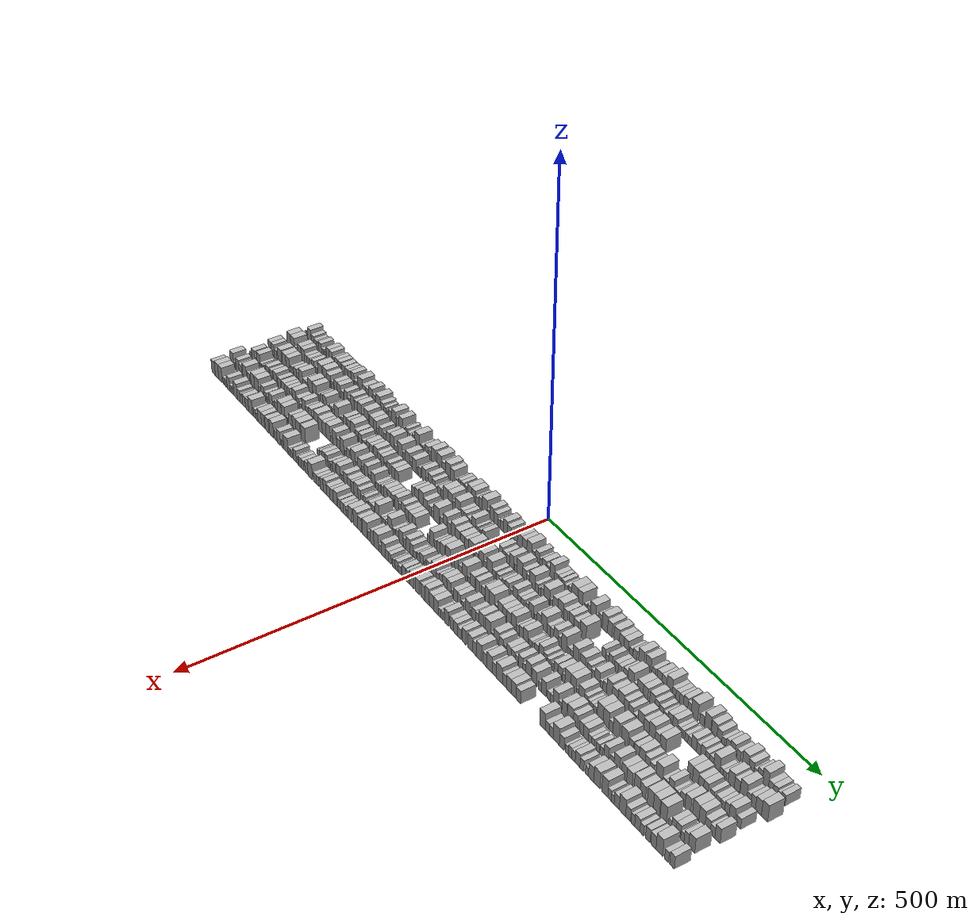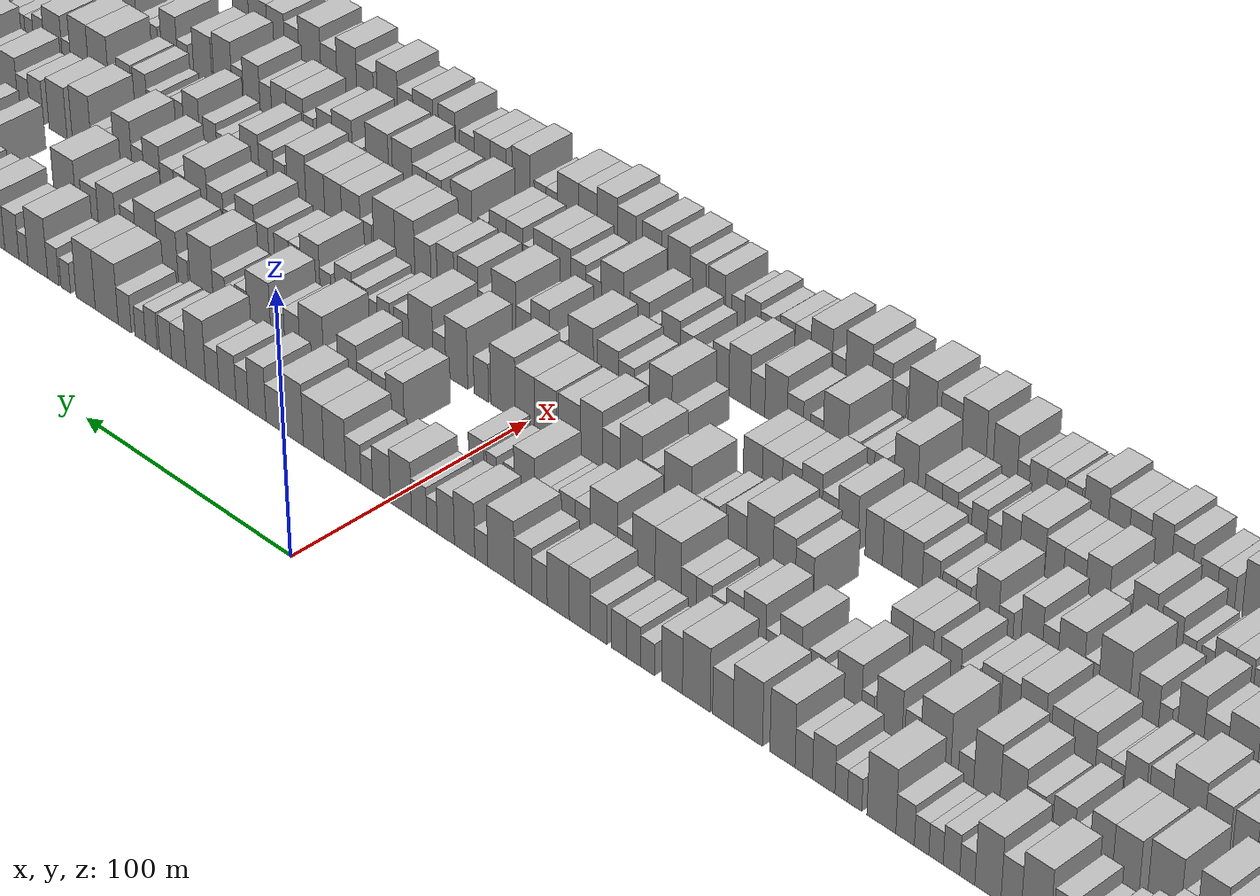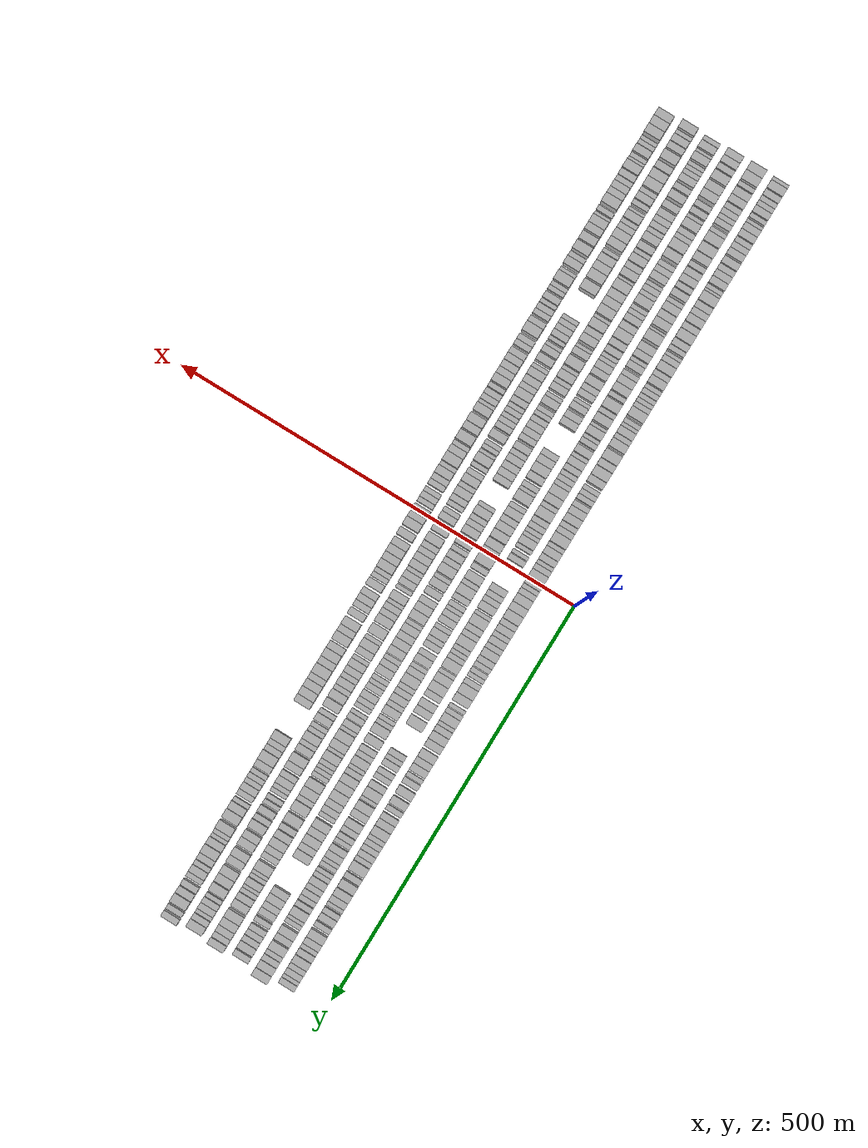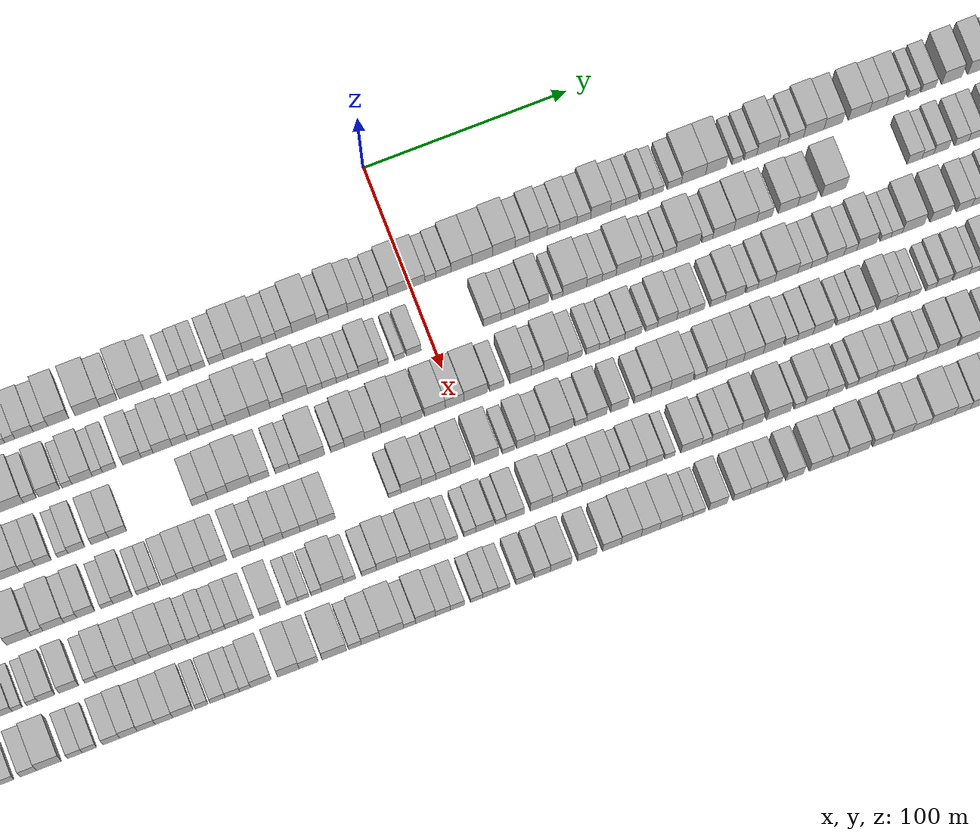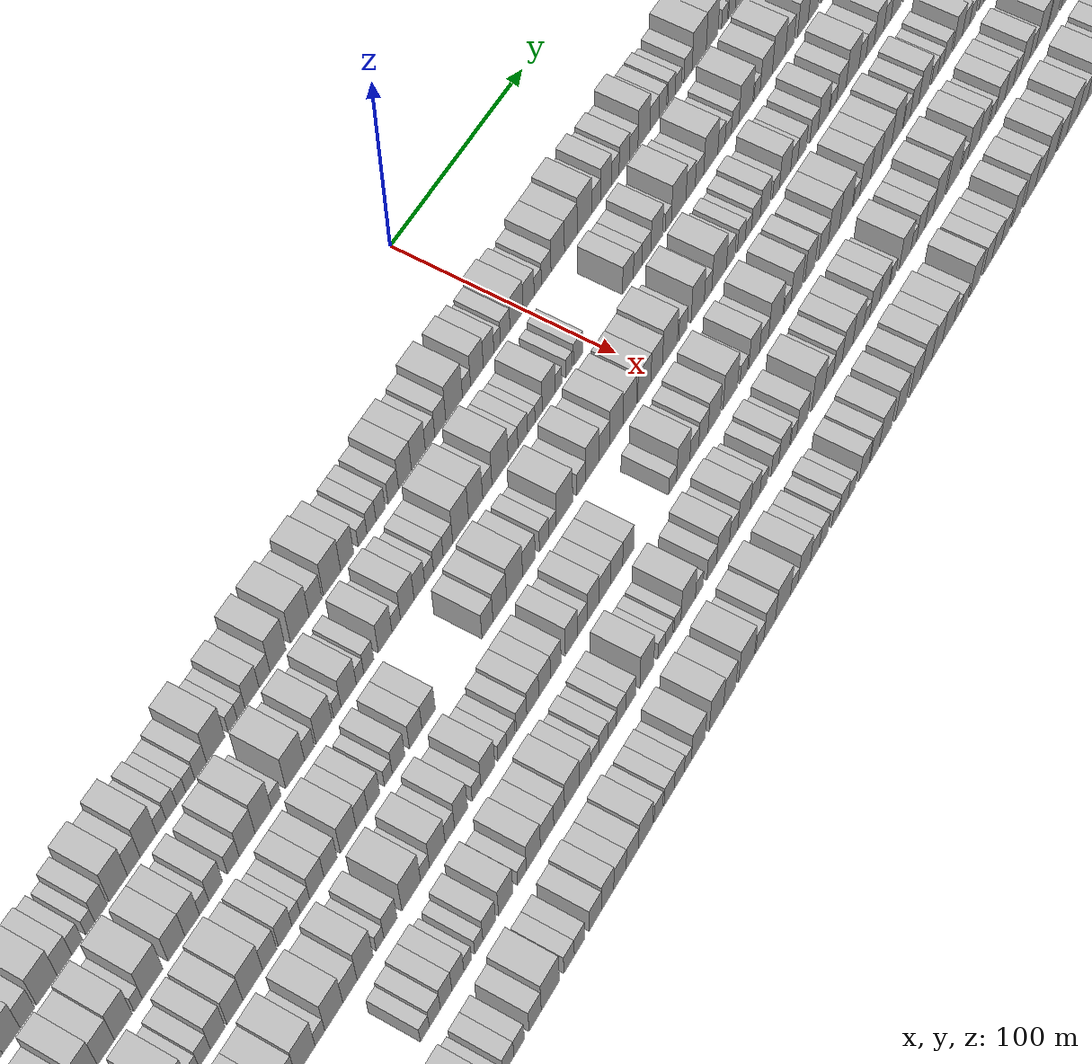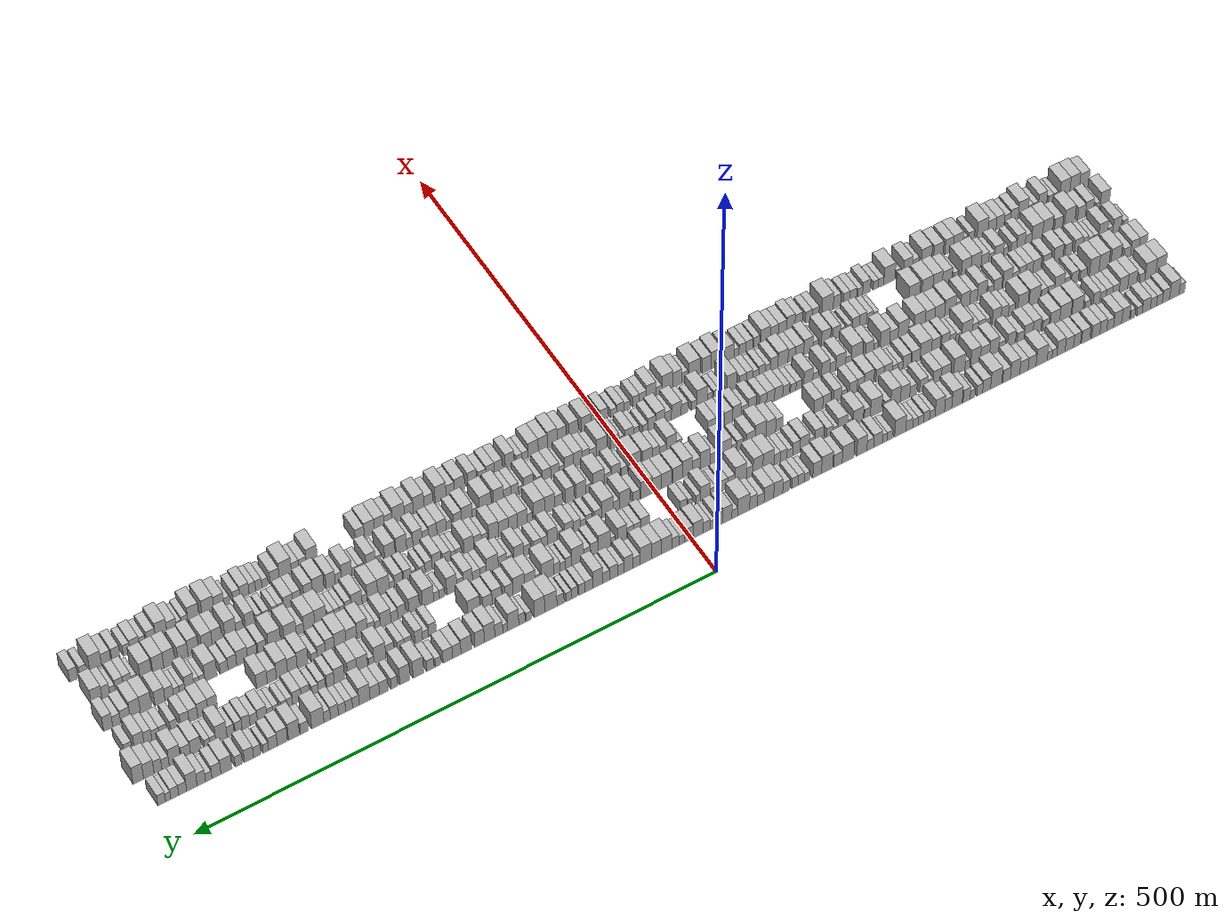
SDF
<sdf version="1.6">
 <world name="default">
  <scene>
   <sky><clouds><speed>12</speed></clouds></sky>
   <ambient>0.4 0.4 0.4 1</ambient>
   <background>0.7 0.7 0.7 1</background>
   <shadows>1</shadows>
  </scene>
  <gravity>0 0 -9.8066</gravity>
  <magnetic_field>6e-06 2.3e-05 -4.2e-05</magnetic_field>
  <physics default="0" name="default_physics" type="ode">
   <ode>
    <solver>
     <type>quick</type>
     <iters>10</iters>
     <sor>1.0</sor>
     <use_dynamic_moi_rescaling>0</use_dynamic_moi_rescaling>
    </solver>
    <constraints>
     <cfm>0</cfm>
     <erp>0.2</erp>
     <contact_max_correcting_vel>100</contact_max_correcting_vel>
     <contact_surface_layer>0.001</contact_surface_layer>
    </constraints>
   </ode>
   <max_step_size>0.004</max_step_size>
   <real_time_factor>1</real_time_factor>
   <real_time_update_rate>250</real_time_update_rate>
  </physics>
  <light name="sun" type="directional">
   <pose>0 0 10 0 0 0</pose>
   <diffuse>0.8 0.8 0.8 1</diffuse>
   <specular>0.2 0.2 0.2 1</specular>
   <attenuation>
    <range>1000</range>
    <constant>0.9</constant>
    <linear>0.01</linear>
    <quadratic>0.001</quadratic>
   </attenuation>
   <direction>-0.5 0.1 -0.9</direction>
  </light>
  <model name="building_1">
   <static>1</static>
   <pose>50.0000 -506.9916 0 0.000000 0.000000 0.000000</pose>
   <link name="link">
    <pose>0 0 7.50 0 0 0</pose>
    <collision name="collision"><geometry><box><size>20.0000 6.0168 15.0000</size></box></geometry></collision>
    <visual name="visual">
     <cast_shadows>0</cast_shadows>
     <geometry><box><size>20.0000 6.0168 15.0000</size></box></geometry>
     <material>
      <script>
       <uri>model://HANNAS_wall/materials/scripts</uri>
       <uri>model://HANNAS_wall/materials/textures</uri>
       <name>vrc/HANNAS_wall</name>
      </script>
     </material>
    </visual>
   </link>
  </model>
  <model name="building_2">
   <static>1</static>
   <pose>50.0000 -498.9707 0 0.000000 0.000000 0.000000</pose>
   <link name="link">
    <pose>0 0 12.00 0 0 0</pose>
    <collision name="collision"><geometry><box><size>20.0000 10.0249 24.0000</size></box></geometry></collision>
    <visual name="visual">
     <cast_shadows>0</cast_shadows>
     <geometry><box><size>20.0000 10.0249 24.0000</size></box></geometry>
     <material>
      <script>
       <uri>model://HANNAS_wall/materials/scripts</uri>
       <uri>model://HANNAS_wall/materials/textures</uri>
       <name>vrc/HANNAS_wall</name>
      </script>
     </material>
    </visual>
   </link>
  </model>
  <model name="building_3">
   <static>1</static>
   <pose>50.0000 -490.0602 0 0.000000 0.000000 0.000000</pose>
   <link name="link">
    <pose>0 0 9.00 0 0 0</pose>
    <collision name="collision"><geometry><box><size>20.0000 7.7961 18.0000</size></box></geometry></collision>
    <visual name="visual">
     <cast_shadows>0</cast_shadows>
     <geometry><box><size>20.0000 7.7961 18.0000</size></box></geometry>
     <material>
      <script>
       <uri>model://HANNAS_wall/materials/scripts</uri>
       <uri>model://HANNAS_wall/materials/textures</uri>
       <name>vrc/HANNAS_wall</name>
      </script>
     </material>
    </visual>
   </link>
  </model>
  <model name="building_4">
   <static>1</static>
   <pose>50.0000 -483.0821 0 0.000000 0.000000 0.000000</pose>
   <link name="link">
    <pose>0 0 7.50 0 0 0</pose>
    <collision name="collision"><geometry><box><size>20.0000 6.1601 15.0000</size></box></geometry></collision>
    <visual name="visual">
     <cast_shadows>0</cast_shadows>
     <geometry><box><size>20.0000 6.1601 15.0000</size></box></geometry>
     <material>
      <script>
       <uri>model://HANNAS_wall/materials/scripts</uri>
       <uri>model://HANNAS_wall/materials/textures</uri>
       <name>vrc/HANNAS_wall</name>
      </script>
     </material>
    </visual>
   </link>
  </model>
  <model name="building_5">
   <static>1</static>
   <pose>50.0000 -476.6821 0 0.000000 0.000000 0.000000</pose>
   <link name="link">
    <pose>0 0 7.50 0 0 0</pose>
    <collision name="collision"><geometry><box><size>20.0000 6.6398 15.0000</size></box></geometry></collision>
    <visual name="visual">
     <cast_shadows>0</cast_shadows>
     <geometry><box><size>20.0000 6.6398 15.0000</size></box></geometry>
     <material>
      <script>
       <uri>model://HANNAS_wall/materials/scripts</uri>
       <uri>model://HANNAS_wall/materials/textures</uri>
       <name>vrc/HANNAS_wall</name>
      </script>
     </material>
    </visual>
   </link>
  </model>
  <model name="building_6">
   <static>1</static>
   <pose>50.0000 -469.0434 0 0.000000 0.000000 0.000000</pose>
   <link name="link">
    <pose>0 0 9.00 0 0 0</pose>
    <collision name="collision"><geometry><box><size>20.0000 8.6375 18.0000</size></box></geometry></collision>
    <visual name="visual">
     <cast_shadows>0</cast_shadows>
     <geometry><box><size>20.0000 8.6375 18.0000</size></box></geometry>
     <material>
      <script>
       <uri>model://HANNAS_wall/materials/scripts</uri>
       <uri>model://HANNAS_wall/materials/textures</uri>
       <name>vrc/HANNAS_wall</name>
      </script>
     </material>
    </visual>
   </link>
  </model>
  <model name="building_7">
   <static>1</static>
   <pose>50.0000 -461.8559 0 0.000000 0.000000 0.000000</pose>
   <link name="link">
    <pose>0 0 6.00 0 0 0</pose>
    <collision name="collision"><geometry><box><size>20.0000 5.7375 12.0000</size></box></geometry></collision>
    <visual name="visual">
     <cast_shadows>0</cast_shadows>
     <geometry><box><size>20.0000 5.7375 12.0000</size></box></geometry>
     <material>
      <script>
       <uri>model://HANNAS_wall/materials/scripts</uri>
       <uri>model://HANNAS_wall/materials/textures</uri>
       <name>vrc/HANNAS_wall</name>
      </script>
     </material>
    </visual>
   </link>
  </model>
  <model name="building_8">
   <static>1</static>
   <pose>50.0000 -454.5249 0 0.000000 0.000000 0.000000</pose>
   <link name="link">
    <pose>0 0 6.00 0 0 0</pose>
    <collision name="collision"><geometry><box><size>20.0000 4.9245 12.0000</size></box></geometry></collision>
    <visual name="visual">
     <cast_shadows>0</cast_shadows>
     <geometry><box><size>20.0000 4.9245 12.0000</size></box></geometry>
     <material>
      <script>
       <uri>model://HANNAS_wall/materials/scripts</uri>
       <uri>model://HANNAS_wall/materials/textures</uri>
       <name>vrc/HANNAS_wall</name>
      </script>
     </material>
    </visual>
   </link>
  </model>
  <model name="building_9">
   <static>1</static>
   <pose>50.0000 -446.8596 0 0.000000 0.000000 0.000000</pose>
   <link name="link">
    <pose>0 0 10.50 0 0 0</pose>
    <collision name="collision"><geometry><box><size>20.0000 8.4061 21.0000</size></box></geometry></collision>
    <visual name="visual">
     <cast_shadows>0</cast_shadows>
     <geometry><box><size>20.0000 8.4061 21.0000</size></box></geometry>
     <material>
      <script>
       <uri>model://HANNAS_wall/materials/scripts</uri>
       <uri>model://HANNAS_wall/materials/textures</uri>
       <name>vrc/HANNAS_wall</name>
      </script>
     </material>
    </visual>
   </link>
  </model>
  <model name="building_10">
   <static>1</static>
   <pose>50.0000 -438.3523 0 0.000000 0.000000 0.000000</pose>
   <link name="link">
    <pose>0 0 10.50 0 0 0</pose>
    <collision name="collision"><geometry><box><size>20.0000 8.6085 21.0000</size></box></geometry></collision>
    <visual name="visual">
     <cast_shadows>0</cast_shadows>
     <geometry><box><size>20.0000 8.6085 21.0000</size></box></geometry>
     <material>
      <script>
       <uri>model://HANNAS_wall/materials/scripts</uri>
       <uri>model://HANNAS_wall/materials/textures</uri>
       <name>vrc/HANNAS_wall</name>
      </script>
     </material>
    </visual>
   </link>
  </model>
  <model name="building_11">
   <static>1</static>
   <pose>50.0000 -430.5139 0 0.000000 0.000000 0.000000</pose>
   <link name="link">
    <pose>0 0 7.50 0 0 0</pose>
    <collision name="collision"><geometry><box><size>20.0000 7.0684 15.0000</size></box></geometry></collision>
    <visual name="visual">
     <cast_shadows>0</cast_shadows>
     <geometry><box><size>20.0000 7.0684 15.0000</size></box></geometry>
     <material>
      <script>
       <uri>model://HANNAS_wall/materials/scripts</uri>
       <uri>model://HANNAS_wall/materials/textures</uri>
       <name>vrc/HANNAS_wall</name>
      </script>
     </material>
    </visual>
   </link>
  </model>
  <model name="building_12">
   <static>1</static>
   <pose>50.0000 -423.2863 0 0.000000 0.000000 0.000000</pose>
   <link name="link">
    <pose>0 0 9.00 0 0 0</pose>
    <collision name="collision"><geometry><box><size>20.0000 7.3868 18.0000</size></box></geometry></collision>
    <visual name="visual">
     <cast_shadows>0</cast_shadows>
     <geometry><box><size>20.0000 7.3868 18.0000</size></box></geometry>
     <material>
      <script>
       <uri>model://HANNAS_wall/materials/scripts</uri>
       <uri>model://HANNAS_wall/materials/textures</uri>
       <name>vrc/HANNAS_wall</name>
      </script>
     </material>
    </visual>
   </link>
  </model>
  <model name="building_13">
   <static>1</static>
   <pose>50.0000 -415.2839 0 0.000000 0.000000 0.000000</pose>
   <link name="link">
    <pose>0 0 9.00 0 0 0</pose>
    <collision name="collision"><geometry><box><size>20.0000 8.6180 18.0000</size></box></geometry></collision>
    <visual name="visual">
     <cast_shadows>0</cast_shadows>
     <geometry><box><size>20.0000 8.6180 18.0000</size></box></geometry>
     <material>
      <script>
       <uri>model://HANNAS_wall/materials/scripts</uri>
       <uri>model://HANNAS_wall/materials/textures</uri>
       <name>vrc/HANNAS_wall</name>
      </script>
     </material>
    </visual>
   </link>
  </model>
  <model name="building_14">
   <static>1</static>
   <pose>50.0000 -404.5082 0 0.000000 0.000000 0.000000</pose>
   <link name="link">
    <pose>0 0 9.00 0 0 0</pose>
    <collision name="collision"><geometry><box><size>20.0000 8.9333 18.0000</size></box></geometry></collision>
    <visual name="visual">
     <cast_shadows>0</cast_shadows>
     <geometry><box><size>20.0000 8.9333 18.0000</size></box></geometry>
     <material>
      <script>
       <uri>model://HANNAS_wall/materials/scripts</uri>
       <uri>model://HANNAS_wall/materials/textures</uri>
       <name>vrc/HANNAS_wall</name>
      </script>
     </material>
    </visual>
   </link>
  </model>
  <model name="building_15">
   <static>1</static>
   <pose>50.0000 -395.3753 0 0.000000 0.000000 0.000000</pose>
   <link name="link">
    <pose>0 0 9.00 0 0 0</pose>
    <collision name="collision"><geometry><box><size>20.0000 7.3325 18.0000</size></box></geometry></collision>
    <visual name="visual">
     <cast_shadows>0</cast_shadows>
     <geometry><box><size>20.0000 7.3325 18.0000</size></box></geometry>
     <material>
      <script>
       <uri>model://HANNAS_wall/materials/scripts</uri>
       <uri>model://HANNAS_wall/materials/textures</uri>
       <name>vrc/HANNAS_wall</name>
      </script>
     </material>
    </visual>
   </link>
  </model>
  <model name="building_16">
   <static>1</static>
   <pose>50.0000 -387.2432 0 0.000000 0.000000 0.000000</pose>
   <link name="link">
    <pose>0 0 9.00 0 0 0</pose>
    <collision name="collision"><geometry><box><size>20.0000 8.9317 18.0000</size></box></geometry></collision>
    <visual name="visual">
     <cast_shadows>0</cast_shadows>
     <geometry><box><size>20.0000 8.9317 18.0000</size></box></geometry>
     <material>
      <script>
       <uri>model://HANNAS_wall/materials/scripts</uri>
       <uri>model://HANNAS_wall/materials/textures</uri>
       <name>vrc/HANNAS_wall</name>
      </script>
     </material>
    </visual>
   </link>
  </model>
  <model name="building_17">
   <static>1</static>
   <pose>50.0000 -378.4819 0 0.000000 0.000000 0.000000</pose>
   <link name="link">
    <pose>0 0 10.50 0 0 0</pose>
    <collision name="collision"><geometry><box><size>20.0000 8.5909 21.0000</size></box></geometry></collision>
    <visual name="visual">
     <cast_shadows>0</cast_shadows>
     <geometry><box><size>20.0000 8.5909 21.0000</size></box></geometry>
     <material>
      <script>
       <uri>model://HANNAS_wall/materials/scripts</uri>
       <uri>model://HANNAS_wall/materials/textures</uri>
       <name>vrc/HANNAS_wall</name>
      </script>
     </material>
    </visual>
   </link>
  </model>
  <model name="building_18">
   <static>1</static>
   <pose>50.0000 -371.5824 0 0.000000 0.000000 0.000000</pose>
   <link name="link">
    <pose>0 0 6.00 0 0 0</pose>
    <collision name="collision"><geometry><box><size>20.0000 5.2082 12.0000</size></box></geometry></collision>
    <visual name="visual">
     <cast_shadows>0</cast_shadows>
     <geometry><box><size>20.0000 5.2082 12.0000</size></box></geometry>
     <material>
      <script>
       <uri>model://HANNAS_wall/materials/scripts</uri>
       <uri>model://HANNAS_wall/materials/textures</uri>
       <name>vrc/HANNAS_wall</name>
      </script>
     </material>
    </visual>
   </link>
  </model>
  <model name="building_19">
   <static>1</static>
   <pose>50.0000 -366.4472 0 0.000000 0.000000 0.000000</pose>
   <link name="link">
    <pose>0 0 6.00 0 0 0</pose>
    <collision name="collision"><geometry><box><size>20.0000 5.0620 12.0000</size></box></geometry></collision>
    <visual name="visual">
     <cast_shadows>0</cast_shadows>
     <geometry><box><size>20.0000 5.0620 12.0000</size></box></geometry>
     <material>
      <script>
       <uri>model://HANNAS_wall/materials/scripts</uri>
       <uri>model://HANNAS_wall/materials/textures</uri>
       <name>vrc/HANNAS_wall</name>
      </script>
     </material>
    </visual>
   </link>
  </model>
  <model name="building_20">
   <static>1</static>
   <pose>50.0000 -358.0317 0 0.000000 0.000000 0.000000</pose>
   <link name="link">
    <pose>0 0 12.00 0 0 0</pose>
    <collision name="collision"><geometry><box><size>20.0000 11.7691 24.0000</size></box></geometry></collision>
    <visual name="visual">
     <cast_shadows>0</cast_shadows>
     <geometry><box><size>20.0000 11.7691 24.0000</size></box></geometry>
     <material>
      <script>
       <uri>model://HANNAS_wall/materials/scripts</uri>
       <uri>model://HANNAS_wall/materials/textures</uri>
       <name>vrc/HANNAS_wall</name>
      </script>
     </material>
    </visual>
   </link>
  </model>
  <model name="building_21">
   <static>1</static>
   <pose>50.0000 -347.9946 0 0.000000 0.000000 0.000000</pose>
   <link name="link">
    <pose>0 0 9.00 0 0 0</pose>
    <collision name="collision"><geometry><box><size>20.0000 8.3049 18.0000</size></box></geometry></collision>
    <visual name="visual">
     <cast_shadows>0</cast_shadows>
     <geometry><box><size>20.0000 8.3049 18.0000</size></box></geometry>
     <material>
      <script>
       <uri>model://HANNAS_wall/materials/scripts</uri>
       <uri>model://HANNAS_wall/materials/textures</uri>
       <name>vrc/HANNAS_wall</name>
      </script>
     </material>
    </visual>
   </link>
  </model>
  <model name="building_22">
   <static>1</static>
   <pose>50.0000 -339.3955 0 0.000000 0.000000 0.000000</pose>
   <link name="link">
    <pose>0 0 9.00 0 0 0</pose>
    <collision name="collision"><geometry><box><size>20.0000 8.8934 18.0000</size></box></geometry></collision>
    <visual name="visual">
     <cast_shadows>0</cast_shadows>
     <geometry><box><size>20.0000 8.8934 18.0000</size></box></geometry>
     <material>
      <script>
       <uri>model://HANNAS_wall/materials/scripts</uri>
       <uri>model://HANNAS_wall/materials/textures</uri>
       <name>vrc/HANNAS_wall</name>
      </script>
     </material>
    </visual>
   </link>
  </model>
  <model name="building_23">
   <static>1</static>
   <pose>50.0000 -330.0623 0 0.000000 0.000000 0.000000</pose>
   <link name="link">
    <pose>0 0 12.00 0 0 0</pose>
    <collision name="collision"><geometry><box><size>20.0000 9.7729 24.0000</size></box></geometry></collision>
    <visual name="visual">
     <cast_shadows>0</cast_shadows>
     <geometry><box><size>20.0000 9.7729 24.0000</size></box></geometry>
     <material>
      <script>
       <uri>model://HANNAS_wall/materials/scripts</uri>
       <uri>model://HANNAS_wall/materials/textures</uri>
       <name>vrc/HANNAS_wall</name>
      </script>
     </material>
    </visual>
   </link>
  </model>
  <model name="building_24">
   <static>1</static>
   <pose>50.0000 -321.1893 0 0.000000 0.000000 0.000000</pose>
   <link name="link">
    <pose>0 0 9.00 0 0 0</pose>
    <collision name="collision"><geometry><box><size>20.0000 7.9732 18.0000</size></box></geometry></collision>
    <visual name="visual">
     <cast_shadows>0</cast_shadows>
     <geometry><box><size>20.0000 7.9732 18.0000</size></box></geometry>
     <material>
      <script>
       <uri>model://HANNAS_wall/materials/scripts</uri>
       <uri>model://HANNAS_wall/materials/textures</uri>
       <name>vrc/HANNAS_wall</name>
      </script>
     </material>
    </visual>
   </link>
  </model>
  <model name="building_25">
   <static>1</static>
   <pose>50.0000 -310.3967 0 0.000000 0.000000 0.000000</pose>
   <link name="link">
    <pose>0 0 12.00 0 0 0</pose>
    <collision name="collision"><geometry><box><size>20.0000 11.6121 24.0000</size></box></geometry></collision>
    <visual name="visual">
     <cast_shadows>0</cast_shadows>
     <geometry><box><size>20.0000 11.6121 24.0000</size></box></geometry>
     <material>
      <script>
       <uri>model://HANNAS_wall/materials/scripts</uri>
       <uri>model://HANNAS_wall/materials/textures</uri>
       <name>vrc/HANNAS_wall</name>
      </script>
     </material>
    </visual>
   </link>
  </model>
  <model name="building_26">
   <static>1</static>
   <pose>50.0000 -300.4433 0 0.000000 0.000000 0.000000</pose>
   <link name="link">
    <pose>0 0 9.00 0 0 0</pose>
    <collision name="collision"><geometry><box><size>20.0000 8.2946 18.0000</size></box></geometry></collision>
    <visual name="visual">
     <cast_shadows>0</cast_shadows>
     <geometry><box><size>20.0000 8.2946 18.0000</size></box></geometry>
     <material>
      <script>
       <uri>model://HANNAS_wall/materials/scripts</uri>
       <uri>model://HANNAS_wall/materials/textures</uri>
       <name>vrc/HANNAS_wall</name>
      </script>
     </material>
    </visual>
   </link>
  </model>
  <model name="building_27">
   <static>1</static>
   <pose>50.0000 -293.2828 0 0.000000 0.000000 0.000000</pose>
   <link name="link">
    <pose>0 0 7.50 0 0 0</pose>
    <collision name="collision"><geometry><box><size>20.0000 6.0265 15.0000</size></box></geometry></collision>
    <visual name="visual">
     <cast_shadows>0</cast_shadows>
     <geometry><box><size>20.0000 6.0265 15.0000</size></box></geometry>
     <material>
      <script>
       <uri>model://HANNAS_wall/materials/scripts</uri>
       <uri>model://HANNAS_wall/materials/textures</uri>
       <name>vrc/HANNAS_wall</name>
      </script>
     </material>
    </visual>
   </link>
  </model>
  <model name="building_28">
   <static>1</static>
   <pose>50.0000 -285.7366 0 0.000000 0.000000 0.000000</pose>
   <link name="link">
    <pose>0 0 6.00 0 0 0</pose>
    <collision name="collision"><geometry><box><size>20.0000 5.0660 12.0000</size></box></geometry></collision>
    <visual name="visual">
     <cast_shadows>0</cast_shadows>
     <geometry><box><size>20.0000 5.0660 12.0000</size></box></geometry>
     <material>
      <script>
       <uri>model://HANNAS_wall/materials/scripts</uri>
       <uri>model://HANNAS_wall/materials/textures</uri>
       <name>vrc/HANNAS_wall</name>
      </script>
     </material>
    </visual>
   </link>
  </model>
  <model name="building_29">
   <static>1</static>
   <pose>50.0000 -279.5629 0 0.000000 0.000000 0.000000</pose>
   <link name="link">
    <pose>0 0 9.00 0 0 0</pose>
    <collision name="collision"><geometry><box><size>20.0000 7.2814 18.0000</size></box></geometry></collision>
    <visual name="visual">
     <cast_shadows>0</cast_shadows>
     <geometry><box><size>20.0000 7.2814 18.0000</size></box></geometry>
     <material>
      <script>
       <uri>model://HANNAS_wall/materials/scripts</uri>
       <uri>model://HANNAS_wall/materials/textures</uri>
       <name>vrc/HANNAS_wall</name>
      </script>
     </material>
    </visual>
   </link>
  </model>
  <model name="building_30">
   <static>1</static>
   <pose>50.0000 -269.5517 0 0.000000 0.000000 0.000000</pose>
   <link name="link">
    <pose>0 0 12.00 0 0 0</pose>
    <collision name="collision"><geometry><box><size>20.0000 10.7412 24.0000</size></box></geometry></collision>
    <visual name="visual">
     <cast_shadows>0</cast_shadows>
     <geometry><box><size>20.0000 10.7412 24.0000</size></box></geometry>
     <material>
      <script>
       <uri>model://HANNAS_wall/materials/scripts</uri>
       <uri>model://HANNAS_wall/materials/textures</uri>
       <name>vrc/HANNAS_wall</name>
      </script>
     </material>
    </visual>
   </link>
  </model>
  <model name="building_31">
   <static>1</static>
   <pose>50.0000 -260.4156 0 0.000000 0.000000 0.000000</pose>
   <link name="link">
    <pose>0 0 9.00 0 0 0</pose>
    <collision name="collision"><geometry><box><size>20.0000 7.5309 18.0000</size></box></geometry></collision>
    <visual name="visual">
     <cast_shadows>0</cast_shadows>
     <geometry><box><size>20.0000 7.5309 18.0000</size></box></geometry>
     <material>
      <script>
       <uri>model://HANNAS_wall/materials/scripts</uri>
       <uri>model://HANNAS_wall/materials/textures</uri>
       <name>vrc/HANNAS_wall</name>
      </script>
     </material>
    </visual>
   </link>
  </model>
  <model name="building_32">
   <static>1</static>
   <pose>50.0000 -251.7488 0 0.000000 0.000000 0.000000</pose>
   <link name="link">
    <pose>0 0 12.00 0 0 0</pose>
    <collision name="collision"><geometry><box><size>20.0000 9.8027 24.0000</size></box></geometry></collision>
    <visual name="visual">
     <cast_shadows>0</cast_shadows>
     <geometry><box><size>20.0000 9.8027 24.0000</size></box></geometry>
     <material>
      <script>
       <uri>model://HANNAS_wall/materials/scripts</uri>
       <uri>model://HANNAS_wall/materials/textures</uri>
       <name>vrc/HANNAS_wall</name>
      </script>
     </material>
    </visual>
   </link>
  </model>
  <model name="building_33">
   <static>1</static>
   <pose>50.0000 -243.9909 0 0.000000 0.000000 0.000000</pose>
   <link name="link">
    <pose>0 0 6.00 0 0 0</pose>
    <collision name="collision"><geometry><box><size>20.0000 5.7133 12.0000</size></box></geometry></collision>
    <visual name="visual">
     <cast_shadows>0</cast_shadows>
     <geometry><box><size>20.0000 5.7133 12.0000</size></box></geometry>
     <material>
      <script>
       <uri>model://HANNAS_wall/materials/scripts</uri>
       <uri>model://HANNAS_wall/materials/textures</uri>
       <name>vrc/HANNAS_wall</name>
      </script>
     </material>
    </visual>
   </link>
  </model>
  <model name="building_34">
   <static>1</static>
   <pose>50.0000 -237.9982 0 0.000000 0.000000 0.000000</pose>
   <link name="link">
    <pose>0 0 7.50 0 0 0</pose>
    <collision name="collision"><geometry><box><size>20.0000 6.2720 15.0000</size></box></geometry></collision>
    <visual name="visual">
     <cast_shadows>0</cast_shadows>
     <geometry><box><size>20.0000 6.2720 15.0000</size></box></geometry>
     <material>
      <script>
       <uri>model://HANNAS_wall/materials/scripts</uri>
       <uri>model://HANNAS_wall/materials/textures</uri>
       <name>vrc/HANNAS_wall</name>
      </script>
     </material>
    </visual>
   </link>
  </model>
  <model name="building_35">
   <static>1</static>
   <pose>50.0000 -232.0915 0 0.000000 0.000000 0.000000</pose>
   <link name="link">
    <pose>0 0 6.00 0 0 0</pose>
    <collision name="collision"><geometry><box><size>20.0000 5.5413 12.0000</size></box></geometry></collision>
    <visual name="visual">
     <cast_shadows>0</cast_shadows>
     <geometry><box><size>20.0000 5.5413 12.0000</size></box></geometry>
     <material>
      <script>
       <uri>model://HANNAS_wall/materials/scripts</uri>
       <uri>model://HANNAS_wall/materials/textures</uri>
       <name>vrc/HANNAS_wall</name>
      </script>
     </material>
    </visual>
   </link>
  </model>
  <model name="building_36">
   <static>1</static>
   <pose>50.0000 -226.5477 0 0.000000 0.000000 0.000000</pose>
   <link name="link">
    <pose>0 0 6.00 0 0 0</pose>
    <collision name="collision"><geometry><box><size>20.0000 5.5463 12.0000</size></box></geometry></collision>
    <visual name="visual">
     <cast_shadows>0</cast_shadows>
     <geometry><box><size>20.0000 5.5463 12.0000</size></box></geometry>
     <material>
      <script>
       <uri>model://HANNAS_wall/materials/scripts</uri>
       <uri>model://HANNAS_wall/materials/textures</uri>
       <name>vrc/HANNAS_wall</name>
      </script>
     </material>
    </visual>
   </link>
  </model>
  <model name="building_37">
   <static>1</static>
   <pose>50.0000 -220.1757 0 0.000000 0.000000 0.000000</pose>
   <link name="link">
    <pose>0 0 7.50 0 0 0</pose>
    <collision name="collision"><geometry><box><size>20.0000 7.1975 15.0000</size></box></geometry></collision>
    <visual name="visual">
     <cast_shadows>0</cast_shadows>
     <geometry><box><size>20.0000 7.1975 15.0000</size></box></geometry>
     <material>
      <script>
       <uri>model://HANNAS_wall/materials/scripts</uri>
       <uri>model://HANNAS_wall/materials/textures</uri>
       <name>vrc/HANNAS_wall</name>
      </script>
     </material>
    </visual>
   </link>
  </model>
  <model name="building_38">
   <static>1</static>
   <pose>50.0000 -210.9292 0 0.000000 0.000000 0.000000</pose>
   <link name="link">
    <pose>0 0 12.00 0 0 0</pose>
    <collision name="collision"><geometry><box><size>20.0000 11.2955 24.0000</size></box></geometry></collision>
    <visual name="visual">
     <cast_shadows>0</cast_shadows>
     <geometry><box><size>20.0000 11.2955 24.0000</size></box></geometry>
     <material>
      <script>
       <uri>model://HANNAS_wall/materials/scripts</uri>
       <uri>model://HANNAS_wall/materials/textures</uri>
       <name>vrc/HANNAS_wall</name>
      </script>
     </material>
    </visual>
   </link>
  </model>
  <model name="building_39">
   <static>1</static>
   <pose>50.0000 -200.4385 0 0.000000 0.000000 0.000000</pose>
   <link name="link">
    <pose>0 0 6.00 0 0 0</pose>
    <collision name="collision"><geometry><box><size>20.0000 5.6861 12.0000</size></box></geometry></collision>
    <visual name="visual">
     <cast_shadows>0</cast_shadows>
     <geometry><box><size>20.0000 5.6861 12.0000</size></box></geometry>
     <material>
      <script>
       <uri>model://HANNAS_wall/materials/scripts</uri>
       <uri>model://HANNAS_wall/materials/textures</uri>
       <name>vrc/HANNAS_wall</name>
      </script>
     </material>
    </visual>
   </link>
  </model>
  <model name="building_40">
   <static>1</static>
   <pose>50.0000 -195.1196 0 0.000000 0.000000 0.000000</pose>
   <link name="link">
    <pose>0 0 6.00 0 0 0</pose>
    <collision name="collision"><geometry><box><size>20.0000 4.9517 12.0000</size></box></geometry></collision>
    <visual name="visual">
     <cast_shadows>0</cast_shadows>
     <geometry><box><size>20.0000 4.9517 12.0000</size></box></geometry>
     <material>
      <script>
       <uri>model://HANNAS_wall/materials/scripts</uri>
       <uri>model://HANNAS_wall/materials/textures</uri>
       <name>vrc/HANNAS_wall</name>
      </script>
     </material>
    </visual>
   </link>
  </model>
  <model name="building_41">
   <static>1</static>
   <pose>50.0000 -188.1827 0 0.000000 0.000000 0.000000</pose>
   <link name="link">
    <pose>0 0 9.00 0 0 0</pose>
    <collision name="collision"><geometry><box><size>20.0000 8.9222 18.0000</size></box></geometry></collision>
    <visual name="visual">
     <cast_shadows>0</cast_shadows>
     <geometry><box><size>20.0000 8.9222 18.0000</size></box></geometry>
     <material>
      <script>
       <uri>model://HANNAS_wall/materials/scripts</uri>
       <uri>model://HANNAS_wall/materials/textures</uri>
       <name>vrc/HANNAS_wall</name>
      </script>
     </material>
    </visual>
   </link>
  </model>
  <model name="building_42">
   <static>1</static>
   <pose>50.0000 -180.2216 0 0.000000 0.000000 0.000000</pose>
   <link name="link">
    <pose>0 0 7.50 0 0 0</pose>
    <collision name="collision"><geometry><box><size>20.0000 7.0001 15.0000</size></box></geometry></collision>
    <visual name="visual">
     <cast_shadows>0</cast_shadows>
     <geometry><box><size>20.0000 7.0001 15.0000</size></box></geometry>
     <material>
      <script>
       <uri>model://HANNAS_wall/materials/scripts</uri>
       <uri>model://HANNAS_wall/materials/textures</uri>
       <name>vrc/HANNAS_wall</name>
      </script>
     </material>
    </visual>
   </link>
  </model>
  <model name="building_43">
   <static>1</static>
   <pose>50.0000 -171.6145 0 0.000000 0.000000 0.000000</pose>
   <link name="link">
    <pose>0 0 12.00 0 0 0</pose>
    <collision name="collision"><geometry><box><size>20.0000 10.2140 24.0000</size></box></geometry></collision>
    <visual name="visual">
     <cast_shadows>0</cast_shadows>
     <geometry><box><size>20.0000 10.2140 24.0000</size></box></geometry>
     <material>
      <script>
       <uri>model://HANNAS_wall/materials/scripts</uri>
       <uri>model://HANNAS_wall/materials/textures</uri>
       <name>vrc/HANNAS_wall</name>
      </script>
     </material>
    </visual>
   </link>
  </model>
  <model name="building_44">
   <static>1</static>
   <pose>50.0000 -157.5136 0 0.000000 0.000000 0.000000</pose>
   <link name="link">
    <pose>0 0 12.00 0 0 0</pose>
    <collision name="collision"><geometry><box><size>20.0000 11.9879 24.0000</size></box></geometry></collision>
    <visual name="visual">
     <cast_shadows>0</cast_shadows>
     <geometry><box><size>20.0000 11.9879 24.0000</size></box></geometry>
     <material>
      <script>
       <uri>model://HANNAS_wall/materials/scripts</uri>
       <uri>model://HANNAS_wall/materials/textures</uri>
       <name>vrc/HANNAS_wall</name>
      </script>
     </material>
    </visual>
   </link>
  </model>
  <model name="building_45">
   <static>1</static>
   <pose>50.0000 -147.2561 0 0.000000 0.000000 0.000000</pose>
   <link name="link">
    <pose>0 0 9.00 0 0 0</pose>
    <collision name="collision"><geometry><box><size>20.0000 8.5272 18.0000</size></box></geometry></collision>
    <visual name="visual">
     <cast_shadows>0</cast_shadows>
     <geometry><box><size>20.0000 8.5272 18.0000</size></box></geometry>
     <material>
      <script>
       <uri>model://HANNAS_wall/materials/scripts</uri>
       <uri>model://HANNAS_wall/materials/textures</uri>
       <name>vrc/HANNAS_wall</name>
      </script>
     </material>
    </visual>
   </link>
  </model>
  <model name="building_46">
   <static>1</static>
   <pose>50.0000 -136.2313 0 0.000000 0.000000 0.000000</pose>
   <link name="link">
    <pose>0 0 12.00 0 0 0</pose>
    <collision name="collision"><geometry><box><size>20.0000 11.5224 24.0000</size></box></geometry></collision>
    <visual name="visual">
     <cast_shadows>0</cast_shadows>
     <geometry><box><size>20.0000 11.5224 24.0000</size></box></geometry>
     <material>
      <script>
       <uri>model://HANNAS_wall/materials/scripts</uri>
       <uri>model://HANNAS_wall/materials/textures</uri>
       <name>vrc/HANNAS_wall</name>
      </script>
     </material>
    </visual>
   </link>
  </model>
  <model name="building_47">
   <static>1</static>
   <pose>50.0000 -126.0759 0 0.000000 0.000000 0.000000</pose>
   <link name="link">
    <pose>0 0 10.50 0 0 0</pose>
    <collision name="collision"><geometry><box><size>20.0000 8.7885 21.0000</size></box></geometry></collision>
    <visual name="visual">
     <cast_shadows>0</cast_shadows>
     <geometry><box><size>20.0000 8.7885 21.0000</size></box></geometry>
     <material>
      <script>
       <uri>model://HANNAS_wall/materials/scripts</uri>
       <uri>model://HANNAS_wall/materials/textures</uri>
       <name>vrc/HANNAS_wall</name>
      </script>
     </material>
    </visual>
   </link>
  </model>
  <model name="building_48">
   <static>1</static>
   <pose>50.0000 -115.7312 0 0.000000 0.000000 0.000000</pose>
   <link name="link">
    <pose>0 0 6.00 0 0 0</pose>
    <collision name="collision"><geometry><box><size>20.0000 5.9009 12.0000</size></box></geometry></collision>
    <visual name="visual">
     <cast_shadows>0</cast_shadows>
     <geometry><box><size>20.0000 5.9009 12.0000</size></box></geometry>
     <material>
      <script>
       <uri>model://HANNAS_wall/materials/scripts</uri>
       <uri>model://HANNAS_wall/materials/textures</uri>
       <name>vrc/HANNAS_wall</name>
      </script>
     </material>
    </visual>
   </link>
  </model>
  <model name="building_49">
   <static>1</static>
   <pose>50.0000 -109.6827 0 0.000000 0.000000 0.000000</pose>
   <link name="link">
    <pose>0 0 7.50 0 0 0</pose>
    <collision name="collision"><geometry><box><size>20.0000 6.1962 15.0000</size></box></geometry></collision>
    <visual name="visual">
     <cast_shadows>0</cast_shadows>
     <geometry><box><size>20.0000 6.1962 15.0000</size></box></geometry>
     <material>
      <script>
       <uri>model://HANNAS_wall/materials/scripts</uri>
       <uri>model://HANNAS_wall/materials/textures</uri>
       <name>vrc/HANNAS_wall</name>
      </script>
     </material>
    </visual>
   </link>
  </model>
  <model name="building_50">
   <static>1</static>
   <pose>50.0000 -103.4571 0 0.000000 0.000000 0.000000</pose>
   <link name="link">
    <pose>0 0 7.50 0 0 0</pose>
    <collision name="collision"><geometry><box><size>20.0000 6.2550 15.0000</size></box></geometry></collision>
    <visual name="visual">
     <cast_shadows>0</cast_shadows>
     <geometry><box><size>20.0000 6.2550 15.0000</size></box></geometry>
     <material>
      <script>
       <uri>model://HANNAS_wall/materials/scripts</uri>
       <uri>model://HANNAS_wall/materials/textures</uri>
       <name>vrc/HANNAS_wall</name>
      </script>
     </material>
    </visual>
   </link>
  </model>
  <model name="building_51">
   <static>1</static>
   <pose>50.0000 -94.7267 0 0.000000 0.000000 0.000000</pose>
   <link name="link">
    <pose>0 0 7.50 0 0 0</pose>
    <collision name="collision"><geometry><box><size>20.0000 7.2057 15.0000</size></box></geometry></collision>
    <visual name="visual">
     <cast_shadows>0</cast_shadows>
     <geometry><box><size>20.0000 7.2057 15.0000</size></box></geometry>
     <material>
      <script>
       <uri>model://HANNAS_wall/materials/scripts</uri>
       <uri>model://HANNAS_wall/materials/textures</uri>
       <name>vrc/HANNAS_wall</name>
      </script>
     </material>
    </visual>
   </link>
  </model>
  <model name="building_52">
   <static>1</static>
   <pose>50.0000 -86.5692 0 0.000000 0.000000 0.000000</pose>
   <link name="link">
    <pose>0 0 10.50 0 0 0</pose>
    <collision name="collision"><geometry><box><size>20.0000 9.1093 21.0000</size></box></geometry></collision>
    <visual name="visual">
     <cast_shadows>0</cast_shadows>
     <geometry><box><size>20.0000 9.1093 21.0000</size></box></geometry>
     <material>
      <script>
       <uri>model://HANNAS_wall/materials/scripts</uri>
       <uri>model://HANNAS_wall/materials/textures</uri>
       <name>vrc/HANNAS_wall</name>
      </script>
     </material>
    </visual>
   </link>
  </model>
  <model name="building_53">
   <static>1</static>
   <pose>50.0000 -77.1655 0 0.000000 0.000000 0.000000</pose>
   <link name="link">
    <pose>0 0 10.50 0 0 0</pose>
    <collision name="collision"><geometry><box><size>20.0000 9.6979 21.0000</size></box></geometry></collision>
    <visual name="visual">
     <cast_shadows>0</cast_shadows>
     <geometry><box><size>20.0000 9.6979 21.0000</size></box></geometry>
     <material>
      <script>
       <uri>model://HANNAS_wall/materials/scripts</uri>
       <uri>model://HANNAS_wall/materials/textures</uri>
       <name>vrc/HANNAS_wall</name>
      </script>
     </material>
    </visual>
   </link>
  </model>
  <model name="building_54">
   <static>1</static>
   <pose>50.0000 -68.9674 0 0.000000 0.000000 0.000000</pose>
   <link name="link">
    <pose>0 0 7.50 0 0 0</pose>
    <collision name="collision"><geometry><box><size>20.0000 6.6983 15.0000</size></box></geometry></collision>
    <visual name="visual">
     <cast_shadows>0</cast_shadows>
     <geometry><box><size>20.0000 6.6983 15.0000</size></box></geometry>
     <material>
      <script>
       <uri>model://HANNAS_wall/materials/scripts</uri>
       <uri>model://HANNAS_wall/materials/textures</uri>
       <name>vrc/HANNAS_wall</name>
      </script>
     </material>
    </visual>
   </link>
  </model>
  <model name="building_55">
   <static>1</static>
   <pose>50.0000 -61.6997 0 0.000000 0.000000 0.000000</pose>
   <link name="link">
    <pose>0 0 9.00 0 0 0</pose>
    <collision name="collision"><geometry><box><size>20.0000 7.8370 18.0000</size></box></geometry></collision>
    <visual name="visual">
     <cast_shadows>0</cast_shadows>
     <geometry><box><size>20.0000 7.8370 18.0000</size></box></geometry>
     <material>
      <script>
       <uri>model://HANNAS_wall/materials/scripts</uri>
       <uri>model://HANNAS_wall/materials/textures</uri>
       <name>vrc/HANNAS_wall</name>
      </script>
     </material>
    </visual>
   </link>
  </model>
  <model name="building_56">
   <static>1</static>
   <pose>50.0000 -51.8079 0 0.000000 0.000000 0.000000</pose>
   <link name="link">
    <pose>0 0 12.00 0 0 0</pose>
    <collision name="collision"><geometry><box><size>20.0000 11.9467 24.0000</size></box></geometry></collision>
    <visual name="visual">
     <cast_shadows>0</cast_shadows>
     <geometry><box><size>20.0000 11.9467 24.0000</size></box></geometry>
     <material>
      <script>
       <uri>model://HANNAS_wall/materials/scripts</uri>
       <uri>model://HANNAS_wall/materials/textures</uri>
       <name>vrc/HANNAS_wall</name>
      </script>
     </material>
    </visual>
   </link>
  </model>
  <model name="building_57">
   <static>1</static>
   <pose>50.0000 -42.8947 0 0.000000 0.000000 0.000000</pose>
   <link name="link">
    <pose>0 0 6.00 0 0 0</pose>
    <collision name="collision"><geometry><box><size>20.0000 5.8796 12.0000</size></box></geometry></collision>
    <visual name="visual">
     <cast_shadows>0</cast_shadows>
     <geometry><box><size>20.0000 5.8796 12.0000</size></box></geometry>
     <material>
      <script>
       <uri>model://HANNAS_wall/materials/scripts</uri>
       <uri>model://HANNAS_wall/materials/textures</uri>
       <name>vrc/HANNAS_wall</name>
      </script>
     </material>
    </visual>
   </link>
  </model>
  <model name="building_58">
   <static>1</static>
   <pose>50.0000 -35.3146 0 0.000000 0.000000 0.000000</pose>
   <link name="link">
    <pose>0 0 10.50 0 0 0</pose>
    <collision name="collision"><geometry><box><size>20.0000 9.2808 21.0000</size></box></geometry></collision>
    <visual name="visual">
     <cast_shadows>0</cast_shadows>
     <geometry><box><size>20.0000 9.2808 21.0000</size></box></geometry>
     <material>
      <script>
       <uri>model://HANNAS_wall/materials/scripts</uri>
       <uri>model://HANNAS_wall/materials/textures</uri>
       <name>vrc/HANNAS_wall</name>
      </script>
     </material>
    </visual>
   </link>
  </model>
  <model name="building_59">
   <static>1</static>
   <pose>50.0000 -26.7613 0 0.000000 0.000000 0.000000</pose>
   <link name="link">
    <pose>0 0 9.00 0 0 0</pose>
    <collision name="collision"><geometry><box><size>20.0000 7.8257 18.0000</size></box></geometry></collision>
    <visual name="visual">
     <cast_shadows>0</cast_shadows>
     <geometry><box><size>20.0000 7.8257 18.0000</size></box></geometry>
     <material>
      <script>
       <uri>model://HANNAS_wall/materials/scripts</uri>
       <uri>model://HANNAS_wall/materials/textures</uri>
       <name>vrc/HANNAS_wall</name>
      </script>
     </material>
    </visual>
   </link>
  </model>
  <model name="building_60">
   <static>1</static>
   <pose>50.0000 -20.4336 0 0.000000 0.000000 0.000000</pose>
   <link name="link">
    <pose>0 0 6.00 0 0 0</pose>
    <collision name="collision"><geometry><box><size>20.0000 4.8297 12.0000</size></box></geometry></collision>
    <visual name="visual">
     <cast_shadows>0</cast_shadows>
     <geometry><box><size>20.0000 4.8297 12.0000</size></box></geometry>
     <material>
      <script>
       <uri>model://HANNAS_wall/materials/scripts</uri>
       <uri>model://HANNAS_wall/materials/textures</uri>
       <name>vrc/HANNAS_wall</name>
      </script>
     </material>
    </visual>
   </link>
  </model>
  <model name="building_61">
   <static>1</static>
   <pose>50.0000 -14.4853 0 0.000000 0.000000 0.000000</pose>
   <link name="link">
    <pose>0 0 7.50 0 0 0</pose>
    <collision name="collision"><geometry><box><size>20.0000 7.0667 15.0000</size></box></geometry></collision>
    <visual name="visual">
     <cast_shadows>0</cast_shadows>
     <geometry><box><size>20.0000 7.0667 15.0000</size></box></geometry>
     <material>
      <script>
       <uri>model://HANNAS_wall/materials/scripts</uri>
       <uri>model://HANNAS_wall/materials/textures</uri>
       <name>vrc/HANNAS_wall</name>
      </script>
     </material>
    </visual>
   </link>
  </model>
  <model name="building_62">
   <static>1</static>
   <pose>50.0000 -6.0214 0 0.000000 0.000000 0.000000</pose>
   <link name="link">
    <pose>0 0 10.50 0 0 0</pose>
    <collision name="collision"><geometry><box><size>20.0000 9.8612 21.0000</size></box></geometry></collision>
    <visual name="visual">
     <cast_shadows>0</cast_shadows>
     <geometry><box><size>20.0000 9.8612 21.0000</size></box></geometry>
     <material>
      <script>
       <uri>model://HANNAS_wall/materials/scripts</uri>
       <uri>model://HANNAS_wall/materials/textures</uri>
       <name>vrc/HANNAS_wall</name>
      </script>
     </material>
    </visual>
   </link>
  </model>
  <model name="building_63">
   <static>1</static>
   <pose>50.0000 3.0512 0 0.000000 0.000000 0.000000</pose>
   <link name="link">
    <pose>0 0 9.00 0 0 0</pose>
    <collision name="collision"><geometry><box><size>20.0000 8.2839 18.0000</size></box></geometry></collision>
    <visual name="visual">
     <cast_shadows>0</cast_shadows>
     <geometry><box><size>20.0000 8.2839 18.0000</size></box></geometry>
     <material>
      <script>
       <uri>model://HANNAS_wall/materials/scripts</uri>
       <uri>model://HANNAS_wall/materials/textures</uri>
       <name>vrc/HANNAS_wall</name>
      </script>
     </material>
    </visual>
   </link>
  </model>
  <model name="building_64">
   <static>1</static>
   <pose>50.0000 9.9308 0 0.000000 0.000000 0.000000</pose>
   <link name="link">
    <pose>0 0 6.00 0 0 0</pose>
    <collision name="collision"><geometry><box><size>20.0000 5.4755 12.0000</size></box></geometry></collision>
    <visual name="visual">
     <cast_shadows>0</cast_shadows>
     <geometry><box><size>20.0000 5.4755 12.0000</size></box></geometry>
     <material>
      <script>
       <uri>model://HANNAS_wall/materials/scripts</uri>
       <uri>model://HANNAS_wall/materials/textures</uri>
       <name>vrc/HANNAS_wall</name>
      </script>
     </material>
    </visual>
   </link>
  </model>
  <model name="building_65">
   <static>1</static>
   <pose>50.0000 16.3078 0 0.000000 0.000000 0.000000</pose>
   <link name="link">
    <pose>0 0 7.50 0 0 0</pose>
    <collision name="collision"><geometry><box><size>20.0000 7.2783 15.0000</size></box></geometry></collision>
    <visual name="visual">
     <cast_shadows>0</cast_shadows>
     <geometry><box><size>20.0000 7.2783 15.0000</size></box></geometry>
     <material>
      <script>
       <uri>model://HANNAS_wall/materials/scripts</uri>
       <uri>model://HANNAS_wall/materials/textures</uri>
       <name>vrc/HANNAS_wall</name>
      </script>
     </material>
    </visual>
   </link>
  </model>
  <model name="building_66">
   <static>1</static>
   <pose>50.0000 25.1313 0 0.000000 0.000000 0.000000</pose>
   <link name="link">
    <pose>0 0 10.50 0 0 0</pose>
    <collision name="collision"><geometry><box><size>20.0000 10.3688 21.0000</size></box></geometry></collision>
    <visual name="visual">
     <cast_shadows>0</cast_shadows>
     <geometry><box><size>20.0000 10.3688 21.0000</size></box></geometry>
     <material>
      <script>
       <uri>model://HANNAS_wall/materials/scripts</uri>
       <uri>model://HANNAS_wall/materials/textures</uri>
       <name>vrc/HANNAS_wall</name>
      </script>
     </material>
    </visual>
   </link>
  </model>
  <model name="building_67">
   <static>1</static>
   <pose>50.0000 35.2658 0 0.000000 0.000000 0.000000</pose>
   <link name="link">
    <pose>0 0 10.50 0 0 0</pose>
    <collision name="collision"><geometry><box><size>20.0000 9.9002 21.0000</size></box></geometry></collision>
    <visual name="visual">
     <cast_shadows>0</cast_shadows>
     <geometry><box><size>20.0000 9.9002 21.0000</size></box></geometry>
     <material>
      <script>
       <uri>model://HANNAS_wall/materials/scripts</uri>
       <uri>model://HANNAS_wall/materials/textures</uri>
       <name>vrc/HANNAS_wall</name>
      </script>
     </material>
    </visual>
   </link>
  </model>
  <model name="building_68">
   <static>1</static>
   <pose>50.0000 45.7797 0 0.000000 0.000000 0.000000</pose>
   <link name="link">
    <pose>0 0 12.00 0 0 0</pose>
    <collision name="collision"><geometry><box><size>20.0000 11.1277 24.0000</size></box></geometry></collision>
    <visual name="visual">
     <cast_shadows>0</cast_shadows>
     <geometry><box><size>20.0000 11.1277 24.0000</size></box></geometry>
     <material>
      <script>
       <uri>model://HANNAS_wall/materials/scripts</uri>
       <uri>model://HANNAS_wall/materials/textures</uri>
       <name>vrc/HANNAS_wall</name>
      </script>
     </material>
    </visual>
   </link>
  </model>
  <model name="building_69">
   <static>1</static>
   <pose>50.0000 54.9168 0 0.000000 0.000000 0.000000</pose>
   <link name="link">
    <pose>0 0 7.50 0 0 0</pose>
    <collision name="collision"><geometry><box><size>20.0000 7.1465 15.0000</size></box></geometry></collision>
    <visual name="visual">
     <cast_shadows>0</cast_shadows>
     <geometry><box><size>20.0000 7.1465 15.0000</size></box></geometry>
     <material>
      <script>
       <uri>model://HANNAS_wall/materials/scripts</uri>
       <uri>model://HANNAS_wall/materials/textures</uri>
       <name>vrc/HANNAS_wall</name>
      </script>
     </material>
    </visual>
   </link>
  </model>
  <model name="building_70">
   <static>1</static>
   <pose>50.0000 62.8040 0 0.000000 0.000000 0.000000</pose>
   <link name="link">
    <pose>0 0 10.50 0 0 0</pose>
    <collision name="collision"><geometry><box><size>20.0000 8.6278 21.0000</size></box></geometry></collision>
    <visual name="visual">
     <cast_shadows>0</cast_shadows>
     <geometry><box><size>20.0000 8.6278 21.0000</size></box></geometry>
     <material>
      <script>
       <uri>model://HANNAS_wall/materials/scripts</uri>
       <uri>model://HANNAS_wall/materials/textures</uri>
       <name>vrc/HANNAS_wall</name>
      </script>
     </material>
    </visual>
   </link>
  </model>
  <model name="building_71">
   <static>1</static>
   <pose>50.0000 70.1985 0 0.000000 0.000000 0.000000</pose>
   <link name="link">
    <pose>0 0 7.50 0 0 0</pose>
    <collision name="collision"><geometry><box><size>20.0000 6.1613 15.0000</size></box></geometry></collision>
    <visual name="visual">
     <cast_shadows>0</cast_shadows>
     <geometry><box><size>20.0000 6.1613 15.0000</size></box></geometry>
     <material>
      <script>
       <uri>model://HANNAS_wall/materials/scripts</uri>
       <uri>model://HANNAS_wall/materials/textures</uri>
       <name>vrc/HANNAS_wall</name>
      </script>
     </material>
    </visual>
   </link>
  </model>
  <model name="building_72">
   <static>1</static>
   <pose>50.0000 77.4950 0 0.000000 0.000000 0.000000</pose>
   <link name="link">
    <pose>0 0 9.00 0 0 0</pose>
    <collision name="collision"><geometry><box><size>20.0000 8.4317 18.0000</size></box></geometry></collision>
    <visual name="visual">
     <cast_shadows>0</cast_shadows>
     <geometry><box><size>20.0000 8.4317 18.0000</size></box></geometry>
     <material>
      <script>
       <uri>model://HANNAS_wall/materials/scripts</uri>
       <uri>model://HANNAS_wall/materials/textures</uri>
       <name>vrc/HANNAS_wall</name>
      </script>
     </material>
    </visual>
   </link>
  </model>
  <model name="building_73">
   <static>1</static>
   <pose>50.0000 85.1063 0 0.000000 0.000000 0.000000</pose>
   <link name="link">
    <pose>0 0 7.50 0 0 0</pose>
    <collision name="collision"><geometry><box><size>20.0000 6.7908 15.0000</size></box></geometry></collision>
    <visual name="visual">
     <cast_shadows>0</cast_shadows>
     <geometry><box><size>20.0000 6.7908 15.0000</size></box></geometry>
     <material>
      <script>
       <uri>model://HANNAS_wall/materials/scripts</uri>
       <uri>model://HANNAS_wall/materials/textures</uri>
       <name>vrc/HANNAS_wall</name>
      </script>
     </material>
    </visual>
   </link>
  </model>
  <model name="building_74">
   <static>1</static>
   <pose>50.0000 93.3463 0 0.000000 0.000000 0.000000</pose>
   <link name="link">
    <pose>0 0 12.00 0 0 0</pose>
    <collision name="collision"><geometry><box><size>20.0000 9.6893 24.0000</size></box></geometry></collision>
    <visual name="visual">
     <cast_shadows>0</cast_shadows>
     <geometry><box><size>20.0000 9.6893 24.0000</size></box></geometry>
     <material>
      <script>
       <uri>model://HANNAS_wall/materials/scripts</uri>
       <uri>model://HANNAS_wall/materials/textures</uri>
       <name>vrc/HANNAS_wall</name>
      </script>
     </material>
    </visual>
   </link>
  </model>
  <model name="building_75">
   <static>1</static>
   <pose>50.0000 101.9193 0 0.000000 0.000000 0.000000</pose>
   <link name="link">
    <pose>0 0 7.50 0 0 0</pose>
    <collision name="collision"><geometry><box><size>20.0000 7.4566 15.0000</size></box></geometry></collision>
    <visual name="visual">
     <cast_shadows>0</cast_shadows>
     <geometry><box><size>20.0000 7.4566 15.0000</size></box></geometry>
     <material>
      <script>
       <uri>model://HANNAS_wall/materials/scripts</uri>
       <uri>model://HANNAS_wall/materials/textures</uri>
       <name>vrc/HANNAS_wall</name>
      </script>
     </material>
    </visual>
   </link>
  </model>
  <model name="building_76">
   <static>1</static>
   <pose>50.0000 108.7788 0 0.000000 0.000000 0.000000</pose>
   <link name="link">
    <pose>0 0 7.50 0 0 0</pose>
    <collision name="collision"><geometry><box><size>20.0000 6.2623 15.0000</size></box></geometry></collision>
    <visual name="visual">
     <cast_shadows>0</cast_shadows>
     <geometry><box><size>20.0000 6.2623 15.0000</size></box></geometry>
     <material>
      <script>
       <uri>model://HANNAS_wall/materials/scripts</uri>
       <uri>model://HANNAS_wall/materials/textures</uri>
       <name>vrc/HANNAS_wall</name>
      </script>
     </material>
    </visual>
   </link>
  </model>
  <model name="building_77">
   <static>1</static>
   <pose>50.0000 115.9818 0 0.000000 0.000000 0.000000</pose>
   <link name="link">
    <pose>0 0 7.50 0 0 0</pose>
    <collision name="collision"><geometry><box><size>20.0000 6.1438 15.0000</size></box></geometry></collision>
    <visual name="visual">
     <cast_shadows>0</cast_shadows>
     <geometry><box><size>20.0000 6.1438 15.0000</size></box></geometry>
     <material>
      <script>
       <uri>model://HANNAS_wall/materials/scripts</uri>
       <uri>model://HANNAS_wall/materials/textures</uri>
       <name>vrc/HANNAS_wall</name>
      </script>
     </material>
    </visual>
   </link>
  </model>
  <model name="building_78">
   <static>1</static>
   <pose>50.0000 121.7191 0 0.000000 0.000000 0.000000</pose>
   <link name="link">
    <pose>0 0 6.00 0 0 0</pose>
    <collision name="collision"><geometry><box><size>20.0000 5.3306 12.0000</size></box></geometry></collision>
    <visual name="visual">
     <cast_shadows>0</cast_shadows>
     <geometry><box><size>20.0000 5.3306 12.0000</size></box></geometry>
     <material>
      <script>
       <uri>model://HANNAS_wall/materials/scripts</uri>
       <uri>model://HANNAS_wall/materials/textures</uri>
       <name>vrc/HANNAS_wall</name>
      </script>
     </material>
    </visual>
   </link>
  </model>
  <model name="building_79">
   <static>1</static>
   <pose>50.0000 129.8049 0 0.000000 0.000000 0.000000</pose>
   <link name="link">
    <pose>0 0 7.50 0 0 0</pose>
    <collision name="collision"><geometry><box><size>20.0000 6.8411 15.0000</size></box></geometry></collision>
    <visual name="visual">
     <cast_shadows>0</cast_shadows>
     <geometry><box><size>20.0000 6.8411 15.0000</size></box></geometry>
     <material>
      <script>
       <uri>model://HANNAS_wall/materials/scripts</uri>
       <uri>model://HANNAS_wall/materials/textures</uri>
       <name>vrc/HANNAS_wall</name>
      </script>
     </material>
    </visual>
   </link>
  </model>
  <model name="building_80">
   <static>1</static>
   <pose>50.0000 139.2177 0 0.000000 0.000000 0.000000</pose>
   <link name="link">
    <pose>0 0 12.00 0 0 0</pose>
    <collision name="collision"><geometry><box><size>20.0000 11.9846 24.0000</size></box></geometry></collision>
    <visual name="visual">
     <cast_shadows>0</cast_shadows>
     <geometry><box><size>20.0000 11.9846 24.0000</size></box></geometry>
     <material>
      <script>
       <uri>model://HANNAS_wall/materials/scripts</uri>
       <uri>model://HANNAS_wall/materials/textures</uri>
       <name>vrc/HANNAS_wall</name>
      </script>
     </material>
    </visual>
   </link>
  </model>
  <model name="building_81">
   <static>1</static>
   <pose>50.0000 150.2545 0 0.000000 0.000000 0.000000</pose>
   <link name="link">
    <pose>0 0 12.00 0 0 0</pose>
    <collision name="collision"><geometry><box><size>20.0000 10.0889 24.0000</size></box></geometry></collision>
    <visual name="visual">
     <cast_shadows>0</cast_shadows>
     <geometry><box><size>20.0000 10.0889 24.0000</size></box></geometry>
     <material>
      <script>
       <uri>model://HANNAS_wall/materials/scripts</uri>
       <uri>model://HANNAS_wall/materials/textures</uri>
       <name>vrc/HANNAS_wall</name>
      </script>
     </material>
    </visual>
   </link>
  </model>
  <model name="building_82">
   <static>1</static>
   <pose>50.0000 160.8277 0 0.000000 0.000000 0.000000</pose>
   <link name="link">
    <pose>0 0 6.00 0 0 0</pose>
    <collision name="collision"><geometry><box><size>20.0000 5.0575 12.0000</size></box></geometry></collision>
    <visual name="visual">
     <cast_shadows>0</cast_shadows>
     <geometry><box><size>20.0000 5.0575 12.0000</size></box></geometry>
     <material>
      <script>
       <uri>model://HANNAS_wall/materials/scripts</uri>
       <uri>model://HANNAS_wall/materials/textures</uri>
       <name>vrc/HANNAS_wall</name>
      </script>
     </material>
    </visual>
   </link>
  </model>
  <model name="building_83">
   <static>1</static>
   <pose>50.0000 167.3991 0 0.000000 0.000000 0.000000</pose>
   <link name="link">
    <pose>0 0 7.50 0 0 0</pose>
    <collision name="collision"><geometry><box><size>20.0000 6.0853 15.0000</size></box></geometry></collision>
    <visual name="visual">
     <cast_shadows>0</cast_shadows>
     <geometry><box><size>20.0000 6.0853 15.0000</size></box></geometry>
     <material>
      <script>
       <uri>model://HANNAS_wall/materials/scripts</uri>
       <uri>model://HANNAS_wall/materials/textures</uri>
       <name>vrc/HANNAS_wall</name>
      </script>
     </material>
    </visual>
   </link>
  </model>
  <model name="building_84">
   <static>1</static>
   <pose>50.0000 175.7296 0 0.000000 0.000000 0.000000</pose>
   <link name="link">
    <pose>0 0 12.00 0 0 0</pose>
    <collision name="collision"><geometry><box><size>20.0000 10.5756 24.0000</size></box></geometry></collision>
    <visual name="visual">
     <cast_shadows>0</cast_shadows>
     <geometry><box><size>20.0000 10.5756 24.0000</size></box></geometry>
     <material>
      <script>
       <uri>model://HANNAS_wall/materials/scripts</uri>
       <uri>model://HANNAS_wall/materials/textures</uri>
       <name>vrc/HANNAS_wall</name>
      </script>
     </material>
    </visual>
   </link>
  </model>
  <model name="building_85">
   <static>1</static>
   <pose>50.0000 183.4808 0 0.000000 0.000000 0.000000</pose>
   <link name="link">
    <pose>0 0 6.00 0 0 0</pose>
    <collision name="collision"><geometry><box><size>20.0000 4.9268 12.0000</size></box></geometry></collision>
    <visual name="visual">
     <cast_shadows>0</cast_shadows>
     <geometry><box><size>20.0000 4.9268 12.0000</size></box></geometry>
     <material>
      <script>
       <uri>model://HANNAS_wall/materials/scripts</uri>
       <uri>model://HANNAS_wall/materials/textures</uri>
       <name>vrc/HANNAS_wall</name>
      </script>
     </material>
    </visual>
   </link>
  </model>
  <model name="building_86">
   <static>1</static>
   <pose>50.0000 189.7976 0 0.000000 0.000000 0.000000</pose>
   <link name="link">
    <pose>0 0 9.00 0 0 0</pose>
    <collision name="collision"><geometry><box><size>20.0000 7.7068 18.0000</size></box></geometry></collision>
    <visual name="visual">
     <cast_shadows>0</cast_shadows>
     <geometry><box><size>20.0000 7.7068 18.0000</size></box></geometry>
     <material>
      <script>
       <uri>model://HANNAS_wall/materials/scripts</uri>
       <uri>model://HANNAS_wall/materials/textures</uri>
       <name>vrc/HANNAS_wall</name>
      </script>
     </material>
    </visual>
   </link>
  </model>
  <model name="building_87">
   <static>1</static>
   <pose>50.0000 198.7217 0 0.000000 0.000000 0.000000</pose>
   <link name="link">
    <pose>0 0 12.00 0 0 0</pose>
    <collision name="collision"><geometry><box><size>20.0000 10.1415 24.0000</size></box></geometry></collision>
    <visual name="visual">
     <cast_shadows>0</cast_shadows>
     <geometry><box><size>20.0000 10.1415 24.0000</size></box></geometry>
     <material>
      <script>
       <uri>model://HANNAS_wall/materials/scripts</uri>
       <uri>model://HANNAS_wall/materials/textures</uri>
       <name>vrc/HANNAS_wall</name>
      </script>
     </material>
    </visual>
   </link>
  </model>
  <model name="building_88">
   <static>1</static>
   <pose>50.0000 208.3711 0 0.000000 0.000000 0.000000</pose>
   <link name="link">
    <pose>0 0 10.50 0 0 0</pose>
    <collision name="collision"><geometry><box><size>20.0000 9.1573 21.0000</size></box></geometry></collision>
    <visual name="visual">
     <cast_shadows>0</cast_shadows>
     <geometry><box><size>20.0000 9.1573 21.0000</size></box></geometry>
     <material>
      <script>
       <uri>model://HANNAS_wall/materials/scripts</uri>
       <uri>model://HANNAS_wall/materials/textures</uri>
       <name>vrc/HANNAS_wall</name>
      </script>
     </material>
    </visual>
   </link>
  </model>
  <model name="building_89">
   <static>1</static>
   <pose>50.0000 221.1318 0 0.000000 0.000000 0.000000</pose>
   <link name="link">
    <pose>0 0 10.50 0 0 0</pose>
    <collision name="collision"><geometry><box><size>20.0000 10.3640 21.0000</size></box></geometry></collision>
    <visual name="visual">
     <cast_shadows>0</cast_shadows>
     <geometry><box><size>20.0000 10.3640 21.0000</size></box></geometry>
     <material>
      <script>
       <uri>model://HANNAS_wall/materials/scripts</uri>
       <uri>model://HANNAS_wall/materials/textures</uri>
       <name>vrc/HANNAS_wall</name>
      </script>
     </material>
    </visual>
   </link>
  </model>
  <model name="building_90">
   <static>1</static>
   <pose>50.0000 230.4606 0 0.000000 0.000000 0.000000</pose>
   <link name="link">
    <pose>0 0 9.00 0 0 0</pose>
    <collision name="collision"><geometry><box><size>20.0000 8.2935 18.0000</size></box></geometry></collision>
    <visual name="visual">
     <cast_shadows>0</cast_shadows>
     <geometry><box><size>20.0000 8.2935 18.0000</size></box></geometry>
     <material>
      <script>
       <uri>model://HANNAS_wall/materials/scripts</uri>
       <uri>model://HANNAS_wall/materials/textures</uri>
       <name>vrc/HANNAS_wall</name>
      </script>
     </material>
    </visual>
   </link>
  </model>
  <model name="building_91">
   <static>1</static>
   <pose>50.0000 239.0653 0 0.000000 0.000000 0.000000</pose>
   <link name="link">
    <pose>0 0 9.00 0 0 0</pose>
    <collision name="collision"><geometry><box><size>20.0000 8.9161 18.0000</size></box></geometry></collision>
    <visual name="visual">
     <cast_shadows>0</cast_shadows>
     <geometry><box><size>20.0000 8.9161 18.0000</size></box></geometry>
     <material>
      <script>
       <uri>model://HANNAS_wall/materials/scripts</uri>
       <uri>model://HANNAS_wall/materials/textures</uri>
       <name>vrc/HANNAS_wall</name>
      </script>
     </material>
    </visual>
   </link>
  </model>
  <model name="building_92">
   <static>1</static>
   <pose>50.0000 248.3040 0 0.000000 0.000000 0.000000</pose>
   <link name="link">
    <pose>0 0 6.00 0 0 0</pose>
    <collision name="collision"><geometry><box><size>20.0000 5.5612 12.0000</size></box></geometry></collision>
    <visual name="visual">
     <cast_shadows>0</cast_shadows>
     <geometry><box><size>20.0000 5.5612 12.0000</size></box></geometry>
     <material>
      <script>
       <uri>model://HANNAS_wall/materials/scripts</uri>
       <uri>model://HANNAS_wall/materials/textures</uri>
       <name>vrc/HANNAS_wall</name>
      </script>
     </material>
    </visual>
   </link>
  </model>
  <model name="building_93">
   <static>1</static>
   <pose>50.0000 255.6967 0 0.000000 0.000000 0.000000</pose>
   <link name="link">
    <pose>0 0 7.50 0 0 0</pose>
    <collision name="collision"><geometry><box><size>20.0000 7.2244 15.0000</size></box></geometry></collision>
    <visual name="visual">
     <cast_shadows>0</cast_shadows>
     <geometry><box><size>20.0000 7.2244 15.0000</size></box></geometry>
     <material>
      <script>
       <uri>model://HANNAS_wall/materials/scripts</uri>
       <uri>model://HANNAS_wall/materials/textures</uri>
       <name>vrc/HANNAS_wall</name>
      </script>
     </material>
    </visual>
   </link>
  </model>
  <model name="building_94">
   <static>1</static>
   <pose>50.0000 267.2891 0 0.000000 0.000000 0.000000</pose>
   <link name="link">
    <pose>0 0 12.00 0 0 0</pose>
    <collision name="collision"><geometry><box><size>20.0000 9.9604 24.0000</size></box></geometry></collision>
    <visual name="visual">
     <cast_shadows>0</cast_shadows>
     <geometry><box><size>20.0000 9.9604 24.0000</size></box></geometry>
     <material>
      <script>
       <uri>model://HANNAS_wall/materials/scripts</uri>
       <uri>model://HANNAS_wall/materials/textures</uri>
       <name>vrc/HANNAS_wall</name>
      </script>
     </material>
    </visual>
   </link>
  </model>
  <model name="building_95">
   <static>1</static>
   <pose>50.0000 280.1073 0 0.000000 0.000000 0.000000</pose>
   <link name="link">
    <pose>0 0 12.00 0 0 0</pose>
    <collision name="collision"><geometry><box><size>20.0000 9.6760 24.0000</size></box></geometry></collision>
    <visual name="visual">
     <cast_shadows>0</cast_shadows>
     <geometry><box><size>20.0000 9.6760 24.0000</size></box></geometry>
     <material>
      <script>
       <uri>model://HANNAS_wall/materials/scripts</uri>
       <uri>model://HANNAS_wall/materials/textures</uri>
       <name>vrc/HANNAS_wall</name>
      </script>
     </material>
    </visual>
   </link>
  </model>
  <model name="building_96">
   <static>1</static>
   <pose>50.0000 290.0958 0 0.000000 0.000000 0.000000</pose>
   <link name="link">
    <pose>0 0 7.50 0 0 0</pose>
    <collision name="collision"><geometry><box><size>20.0000 6.3010 15.0000</size></box></geometry></collision>
    <visual name="visual">
     <cast_shadows>0</cast_shadows>
     <geometry><box><size>20.0000 6.3010 15.0000</size></box></geometry>
     <material>
      <script>
       <uri>model://HANNAS_wall/materials/scripts</uri>
       <uri>model://HANNAS_wall/materials/textures</uri>
       <name>vrc/HANNAS_wall</name>
      </script>
     </material>
    </visual>
   </link>
  </model>
  <model name="building_97">
   <static>1</static>
   <pose>50.0000 300.2858 0 0.000000 0.000000 0.000000</pose>
   <link name="link">
    <pose>0 0 9.00 0 0 0</pose>
    <collision name="collision"><geometry><box><size>20.0000 8.0790 18.0000</size></box></geometry></collision>
    <visual name="visual">
     <cast_shadows>0</cast_shadows>
     <geometry><box><size>20.0000 8.0790 18.0000</size></box></geometry>
     <material>
      <script>
       <uri>model://HANNAS_wall/materials/scripts</uri>
       <uri>model://HANNAS_wall/materials/textures</uri>
       <name>vrc/HANNAS_wall</name>
      </script>
     </material>
    </visual>
   </link>
  </model>
  <model name="building_98">
   <static>1</static>
   <pose>50.0000 308.7973 0 0.000000 0.000000 0.000000</pose>
   <link name="link">
    <pose>0 0 9.00 0 0 0</pose>
    <collision name="collision"><geometry><box><size>20.0000 8.9439 18.0000</size></box></geometry></collision>
    <visual name="visual">
     <cast_shadows>0</cast_shadows>
     <geometry><box><size>20.0000 8.9439 18.0000</size></box></geometry>
     <material>
      <script>
       <uri>model://HANNAS_wall/materials/scripts</uri>
       <uri>model://HANNAS_wall/materials/textures</uri>
       <name>vrc/HANNAS_wall</name>
      </script>
     </material>
    </visual>
   </link>
  </model>
  <model name="building_99">
   <static>1</static>
   <pose>50.0000 318.4404 0 0.000000 0.000000 0.000000</pose>
   <link name="link">
    <pose>0 0 12.00 0 0 0</pose>
    <collision name="collision"><geometry><box><size>20.0000 10.3423 24.0000</size></box></geometry></collision>
    <visual name="visual">
     <cast_shadows>0</cast_shadows>
     <geometry><box><size>20.0000 10.3423 24.0000</size></box></geometry>
     <material>
      <script>
       <uri>model://HANNAS_wall/materials/scripts</uri>
       <uri>model://HANNAS_wall/materials/textures</uri>
       <name>vrc/HANNAS_wall</name>
      </script>
     </material>
    </visual>
   </link>
  </model>
  <model name="building_100">
   <static>1</static>
   <pose>50.0000 326.7508 0 0.000000 0.000000 0.000000</pose>
   <link name="link">
    <pose>0 0 7.50 0 0 0</pose>
    <collision name="collision"><geometry><box><size>20.0000 6.2785 15.0000</size></box></geometry></collision>
    <visual name="visual">
     <cast_shadows>0</cast_shadows>
     <geometry><box><size>20.0000 6.2785 15.0000</size></box></geometry>
     <material>
      <script>
       <uri>model://HANNAS_wall/materials/scripts</uri>
       <uri>model://HANNAS_wall/materials/textures</uri>
       <name>vrc/HANNAS_wall</name>
      </script>
     </material>
    </visual>
   </link>
  </model>
  <model name="building_101">
   <static>1</static>
   <pose>50.0000 333.1623 0 0.000000 0.000000 0.000000</pose>
   <link name="link">
    <pose>0 0 7.50 0 0 0</pose>
    <collision name="collision"><geometry><box><size>20.0000 6.5444 15.0000</size></box></geometry></collision>
    <visual name="visual">
     <cast_shadows>0</cast_shadows>
     <geometry><box><size>20.0000 6.5444 15.0000</size></box></geometry>
     <material>
      <script>
       <uri>model://HANNAS_wall/materials/scripts</uri>
       <uri>model://HANNAS_wall/materials/textures</uri>
       <name>vrc/HANNAS_wall</name>
      </script>
     </material>
    </visual>
   </link>
  </model>
  <model name="building_102">
   <static>1</static>
   <pose>50.0000 339.8382 0 0.000000 0.000000 0.000000</pose>
   <link name="link">
    <pose>0 0 7.50 0 0 0</pose>
    <collision name="collision"><geometry><box><size>20.0000 6.8074 15.0000</size></box></geometry></collision>
    <visual name="visual">
     <cast_shadows>0</cast_shadows>
     <geometry><box><size>20.0000 6.8074 15.0000</size></box></geometry>
     <material>
      <script>
       <uri>model://HANNAS_wall/materials/scripts</uri>
       <uri>model://HANNAS_wall/materials/textures</uri>
       <name>vrc/HANNAS_wall</name>
      </script>
     </material>
    </visual>
   </link>
  </model>
  <model name="building_103">
   <static>1</static>
   <pose>50.0000 347.0147 0 0.000000 0.000000 0.000000</pose>
   <link name="link">
    <pose>0 0 9.00 0 0 0</pose>
    <collision name="collision"><geometry><box><size>20.0000 7.5456 18.0000</size></box></geometry></collision>
    <visual name="visual">
     <cast_shadows>0</cast_shadows>
     <geometry><box><size>20.0000 7.5456 18.0000</size></box></geometry>
     <material>
      <script>
       <uri>model://HANNAS_wall/materials/scripts</uri>
       <uri>model://HANNAS_wall/materials/textures</uri>
       <name>vrc/HANNAS_wall</name>
      </script>
     </material>
    </visual>
   </link>
  </model>
  <model name="building_104">
   <static>1</static>
   <pose>50.0000 353.8501 0 0.000000 0.000000 0.000000</pose>
   <link name="link">
    <pose>0 0 7.50 0 0 0</pose>
    <collision name="collision"><geometry><box><size>20.0000 6.1251 15.0000</size></box></geometry></collision>
    <visual name="visual">
     <cast_shadows>0</cast_shadows>
     <geometry><box><size>20.0000 6.1251 15.0000</size></box></geometry>
     <material>
      <script>
       <uri>model://HANNAS_wall/materials/scripts</uri>
       <uri>model://HANNAS_wall/materials/textures</uri>
       <name>vrc/HANNAS_wall</name>
      </script>
     </material>
    </visual>
   </link>
  </model>
  <model name="building_105">
   <static>1</static>
   <pose>50.0000 362.7485 0 0.000000 0.000000 0.000000</pose>
   <link name="link">
    <pose>0 0 12.00 0 0 0</pose>
    <collision name="collision"><geometry><box><size>20.0000 11.6719 24.0000</size></box></geometry></collision>
    <visual name="visual">
     <cast_shadows>0</cast_shadows>
     <geometry><box><size>20.0000 11.6719 24.0000</size></box></geometry>
     <material>
      <script>
       <uri>model://HANNAS_wall/materials/scripts</uri>
       <uri>model://HANNAS_wall/materials/textures</uri>
       <name>vrc/HANNAS_wall</name>
      </script>
     </material>
    </visual>
   </link>
  </model>
  <model name="building_106">
   <static>1</static>
   <pose>50.0000 375.2909 0 0.000000 0.000000 0.000000</pose>
   <link name="link">
    <pose>0 0 7.50 0 0 0</pose>
    <collision name="collision"><geometry><box><size>20.0000 7.4128 15.0000</size></box></geometry></collision>
    <visual name="visual">
     <cast_shadows>0</cast_shadows>
     <geometry><box><size>20.0000 7.4128 15.0000</size></box></geometry>
     <material>
      <script>
       <uri>model://HANNAS_wall/materials/scripts</uri>
       <uri>model://HANNAS_wall/materials/textures</uri>
       <name>vrc/HANNAS_wall</name>
      </script>
     </material>
    </visual>
   </link>
  </model>
  <model name="building_107">
   <static>1</static>
   <pose>50.0000 385.1627 0 0.000000 0.000000 0.000000</pose>
   <link name="link">
    <pose>0 0 12.00 0 0 0</pose>
    <collision name="collision"><geometry><box><size>20.0000 10.3308 24.0000</size></box></geometry></collision>
    <visual name="visual">
     <cast_shadows>0</cast_shadows>
     <geometry><box><size>20.0000 10.3308 24.0000</size></box></geometry>
     <material>
      <script>
       <uri>model://HANNAS_wall/materials/scripts</uri>
       <uri>model://HANNAS_wall/materials/textures</uri>
       <name>vrc/HANNAS_wall</name>
      </script>
     </material>
    </visual>
   </link>
  </model>
  <model name="building_108">
   <static>1</static>
   <pose>50.0000 396.0615 0 0.000000 0.000000 0.000000</pose>
   <link name="link">
    <pose>0 0 10.50 0 0 0</pose>
    <collision name="collision"><geometry><box><size>20.0000 9.4669 21.0000</size></box></geometry></collision>
    <visual name="visual">
     <cast_shadows>0</cast_shadows>
     <geometry><box><size>20.0000 9.4669 21.0000</size></box></geometry>
     <material>
      <script>
       <uri>model://HANNAS_wall/materials/scripts</uri>
       <uri>model://HANNAS_wall/materials/textures</uri>
       <name>vrc/HANNAS_wall</name>
      </script>
     </material>
    </visual>
   </link>
  </model>
  <model name="building_109">
   <static>1</static>
   <pose>50.0000 404.8894 0 0.000000 0.000000 0.000000</pose>
   <link name="link">
    <pose>0 0 9.00 0 0 0</pose>
    <collision name="collision"><geometry><box><size>20.0000 8.1889 18.0000</size></box></geometry></collision>
    <visual name="visual">
     <cast_shadows>0</cast_shadows>
     <geometry><box><size>20.0000 8.1889 18.0000</size></box></geometry>
     <material>
      <script>
       <uri>model://HANNAS_wall/materials/scripts</uri>
       <uri>model://HANNAS_wall/materials/textures</uri>
       <name>vrc/HANNAS_wall</name>
      </script>
     </material>
    </visual>
   </link>
  </model>
  <model name="building_110">
   <static>1</static>
   <pose>50.0000 411.5685 0 0.000000 0.000000 0.000000</pose>
   <link name="link">
    <pose>0 0 6.00 0 0 0</pose>
    <collision name="collision"><geometry><box><size>20.0000 5.1693 12.0000</size></box></geometry></collision>
    <visual name="visual">
     <cast_shadows>0</cast_shadows>
     <geometry><box><size>20.0000 5.1693 12.0000</size></box></geometry>
     <material>
      <script>
       <uri>model://HANNAS_wall/materials/scripts</uri>
       <uri>model://HANNAS_wall/materials/textures</uri>
       <name>vrc/HANNAS_wall</name>
      </script>
     </material>
    </visual>
   </link>
  </model>
  <model name="building_111">
   <static>1</static>
   <pose>50.0000 419.6284 0 0.000000 0.000000 0.000000</pose>
   <link name="link">
    <pose>0 0 7.50 0 0 0</pose>
    <collision name="collision"><geometry><box><size>20.0000 6.9505 15.0000</size></box></geometry></collision>
    <visual name="visual">
     <cast_shadows>0</cast_shadows>
     <geometry><box><size>20.0000 6.9505 15.0000</size></box></geometry>
     <material>
      <script>
       <uri>model://HANNAS_wall/materials/scripts</uri>
       <uri>model://HANNAS_wall/materials/textures</uri>
       <name>vrc/HANNAS_wall</name>
      </script>
     </material>
    </visual>
   </link>
  </model>
  <model name="building_112">
   <static>1</static>
   <pose>50.0000 427.3668 0 0.000000 0.000000 0.000000</pose>
   <link name="link">
    <pose>0 0 9.00 0 0 0</pose>
    <collision name="collision"><geometry><box><size>20.0000 8.5264 18.0000</size></box></geometry></collision>
    <visual name="visual">
     <cast_shadows>0</cast_shadows>
     <geometry><box><size>20.0000 8.5264 18.0000</size></box></geometry>
     <material>
      <script>
       <uri>model://HANNAS_wall/materials/scripts</uri>
       <uri>model://HANNAS_wall/materials/textures</uri>
       <name>vrc/HANNAS_wall</name>
      </script>
     </material>
    </visual>
   </link>
  </model>
  <model name="building_113">
   <static>1</static>
   <pose>50.0000 436.8863 0 0.000000 0.000000 0.000000</pose>
   <link name="link">
    <pose>0 0 7.50 0 0 0</pose>
    <collision name="collision"><geometry><box><size>20.0000 6.5126 15.0000</size></box></geometry></collision>
    <visual name="visual">
     <cast_shadows>0</cast_shadows>
     <geometry><box><size>20.0000 6.5126 15.0000</size></box></geometry>
     <material>
      <script>
       <uri>model://HANNAS_wall/materials/scripts</uri>
       <uri>model://HANNAS_wall/materials/textures</uri>
       <name>vrc/HANNAS_wall</name>
      </script>
     </material>
    </visual>
   </link>
  </model>
  <model name="building_114">
   <static>1</static>
   <pose>50.0000 448.3292 0 0.000000 0.000000 0.000000</pose>
   <link name="link">
    <pose>0 0 10.50 0 0 0</pose>
    <collision name="collision"><geometry><box><size>20.0000 10.3732 21.0000</size></box></geometry></collision>
    <visual name="visual">
     <cast_shadows>0</cast_shadows>
     <geometry><box><size>20.0000 10.3732 21.0000</size></box></geometry>
     <material>
      <script>
       <uri>model://HANNAS_wall/materials/scripts</uri>
       <uri>model://HANNAS_wall/materials/textures</uri>
       <name>vrc/HANNAS_wall</name>
      </script>
     </material>
    </visual>
   </link>
  </model>
  <model name="building_115">
   <static>1</static>
   <pose>50.0000 457.6762 0 0.000000 0.000000 0.000000</pose>
   <link name="link">
    <pose>0 0 9.00 0 0 0</pose>
    <collision name="collision"><geometry><box><size>20.0000 8.3207 18.0000</size></box></geometry></collision>
    <visual name="visual">
     <cast_shadows>0</cast_shadows>
     <geometry><box><size>20.0000 8.3207 18.0000</size></box></geometry>
     <material>
      <script>
       <uri>model://HANNAS_wall/materials/scripts</uri>
       <uri>model://HANNAS_wall/materials/textures</uri>
       <name>vrc/HANNAS_wall</name>
      </script>
     </material>
    </visual>
   </link>
  </model>
  <model name="building_116">
   <static>1</static>
   <pose>50.0000 464.8121 0 0.000000 0.000000 0.000000</pose>
   <link name="link">
    <pose>0 0 6.00 0 0 0</pose>
    <collision name="collision"><geometry><box><size>20.0000 5.9510 12.0000</size></box></geometry></collision>
    <visual name="visual">
     <cast_shadows>0</cast_shadows>
     <geometry><box><size>20.0000 5.9510 12.0000</size></box></geometry>
     <material>
      <script>
       <uri>model://HANNAS_wall/materials/scripts</uri>
       <uri>model://HANNAS_wall/materials/textures</uri>
       <name>vrc/HANNAS_wall</name>
      </script>
     </material>
    </visual>
   </link>
  </model>
  <model name="building_117">
   <static>1</static>
   <pose>50.0000 471.6848 0 0.000000 0.000000 0.000000</pose>
   <link name="link">
    <pose>0 0 9.00 0 0 0</pose>
    <collision name="collision"><geometry><box><size>20.0000 7.7943 18.0000</size></box></geometry></collision>
    <visual name="visual">
     <cast_shadows>0</cast_shadows>
     <geometry><box><size>20.0000 7.7943 18.0000</size></box></geometry>
     <material>
      <script>
       <uri>model://HANNAS_wall/materials/scripts</uri>
       <uri>model://HANNAS_wall/materials/textures</uri>
       <name>vrc/HANNAS_wall</name>
      </script>
     </material>
    </visual>
   </link>
  </model>
  <model name="building_118">
   <static>1</static>
   <pose>50.0000 480.4277 0 0.000000 0.000000 0.000000</pose>
   <link name="link">
    <pose>0 0 12.00 0 0 0</pose>
    <collision name="collision"><geometry><box><size>20.0000 9.6914 24.0000</size></box></geometry></collision>
    <visual name="visual">
     <cast_shadows>0</cast_shadows>
     <geometry><box><size>20.0000 9.6914 24.0000</size></box></geometry>
     <material>
      <script>
       <uri>model://HANNAS_wall/materials/scripts</uri>
       <uri>model://HANNAS_wall/materials/textures</uri>
       <name>vrc/HANNAS_wall</name>
      </script>
     </material>
    </visual>
   </link>
  </model>
  <model name="building_119">
   <static>1</static>
   <pose>50.0000 488.9293 0 0.000000 0.000000 0.000000</pose>
   <link name="link">
    <pose>0 0 7.50 0 0 0</pose>
    <collision name="collision"><geometry><box><size>20.0000 7.3118 15.0000</size></box></geometry></collision>
    <visual name="visual">
     <cast_shadows>0</cast_shadows>
     <geometry><box><size>20.0000 7.3118 15.0000</size></box></geometry>
     <material>
      <script>
       <uri>model://HANNAS_wall/materials/scripts</uri>
       <uri>model://HANNAS_wall/materials/textures</uri>
       <name>vrc/HANNAS_wall</name>
      </script>
     </material>
    </visual>
   </link>
  </model>
  <model name="building_120">
   <static>1</static>
   <pose>50.0000 496.2499 0 0.000000 0.000000 0.000000</pose>
   <link name="link">
    <pose>0 0 7.50 0 0 0</pose>
    <collision name="collision"><geometry><box><size>20.0000 7.3295 15.0000</size></box></geometry></collision>
    <visual name="visual">
     <cast_shadows>0</cast_shadows>
     <geometry><box><size>20.0000 7.3295 15.0000</size></box></geometry>
     <material>
      <script>
       <uri>model://HANNAS_wall/materials/scripts</uri>
       <uri>model://HANNAS_wall/materials/textures</uri>
       <name>vrc/HANNAS_wall</name>
      </script>
     </material>
    </visual>
   </link>
  </model>
  <model name="building_121">
   <static>1</static>
   <pose>50.0000 502.3638 0 0.000000 0.000000 0.000000</pose>
   <link name="link">
    <pose>0 0 6.00 0 0 0</pose>
    <collision name="collision"><geometry><box><size>20.0000 4.8982 12.0000</size></box></geometry></collision>
    <visual name="visual">
     <cast_shadows>0</cast_shadows>
     <geometry><box><size>20.0000 4.8982 12.0000</size></box></geometry>
     <material>
      <script>
       <uri>model://HANNAS_wall/materials/scripts</uri>
       <uri>model://HANNAS_wall/materials/textures</uri>
       <name>vrc/HANNAS_wall</name>
      </script>
     </material>
    </visual>
   </link>
  </model>
  <model name="building_122">
   <static>1</static>
   <pose>50.0000 508.3706 0 0.000000 0.000000 0.000000</pose>
   <link name="link">
    <pose>0 0 7.50 0 0 0</pose>
    <collision name="collision"><geometry><box><size>20.0000 7.1154 15.0000</size></box></geometry></collision>
    <visual name="visual">
     <cast_shadows>0</cast_shadows>
     <geometry><box><size>20.0000 7.1154 15.0000</size></box></geometry>
     <material>
      <script>
       <uri>model://HANNAS_wall/materials/scripts</uri>
       <uri>model://HANNAS_wall/materials/textures</uri>
       <name>vrc/HANNAS_wall</name>
      </script>
     </material>
    </visual>
   </link>
  </model>
  <model name="building_123">
   <static>1</static>
   <pose>79.0000 -504.6956 0 0.000000 0.000000 0.000000</pose>
   <link name="link">
    <pose>0 0 12.00 0 0 0</pose>
    <collision name="collision"><geometry><box><size>20.0000 10.6087 24.0000</size></box></geometry></collision>
    <visual name="visual">
     <cast_shadows>0</cast_shadows>
     <geometry><box><size>20.0000 10.6087 24.0000</size></box></geometry>
     <material>
      <script>
       <uri>model://HANNAS_wall/materials/scripts</uri>
       <uri>model://HANNAS_wall/materials/textures</uri>
       <name>vrc/HANNAS_wall</name>
      </script>
     </material>
    </visual>
   </link>
  </model>
  <model name="building_124">
   <static>1</static>
   <pose>79.0000 -493.6152 0 0.000000 0.000000 0.000000</pose>
   <link name="link">
    <pose>0 0 12.00 0 0 0</pose>
    <collision name="collision"><geometry><box><size>20.0000 11.5521 24.0000</size></box></geometry></collision>
    <visual name="visual">
     <cast_shadows>0</cast_shadows>
     <geometry><box><size>20.0000 11.5521 24.0000</size></box></geometry>
     <material>
      <script>
       <uri>model://HANNAS_wall/materials/scripts</uri>
       <uri>model://HANNAS_wall/materials/textures</uri>
       <name>vrc/HANNAS_wall</name>
      </script>
     </material>
    </visual>
   </link>
  </model>
  <model name="building_125">
   <static>1</static>
   <pose>79.0000 -484.9370 0 0.000000 0.000000 0.000000</pose>
   <link name="link">
    <pose>0 0 6.00 0 0 0</pose>
    <collision name="collision"><geometry><box><size>20.0000 5.8043 12.0000</size></box></geometry></collision>
    <visual name="visual">
     <cast_shadows>0</cast_shadows>
     <geometry><box><size>20.0000 5.8043 12.0000</size></box></geometry>
     <material>
      <script>
       <uri>model://HANNAS_wall/materials/scripts</uri>
       <uri>model://HANNAS_wall/materials/textures</uri>
       <name>vrc/HANNAS_wall</name>
      </script>
     </material>
    </visual>
   </link>
  </model>
  <model name="building_126">
   <static>1</static>
   <pose>79.0000 -474.2090 0 0.000000 0.000000 0.000000</pose>
   <link name="link">
    <pose>0 0 10.50 0 0 0</pose>
    <collision name="collision"><geometry><box><size>20.0000 9.6517 21.0000</size></box></geometry></collision>
    <visual name="visual">
     <cast_shadows>0</cast_shadows>
     <geometry><box><size>20.0000 9.6517 21.0000</size></box></geometry>
     <material>
      <script>
       <uri>model://HANNAS_wall/materials/scripts</uri>
       <uri>model://HANNAS_wall/materials/textures</uri>
       <name>vrc/HANNAS_wall</name>
      </script>
     </material>
    </visual>
   </link>
  </model>
  <model name="building_127">
   <static>1</static>
   <pose>79.0000 -464.7738 0 0.000000 0.000000 0.000000</pose>
   <link name="link">
    <pose>0 0 10.50 0 0 0</pose>
    <collision name="collision"><geometry><box><size>20.0000 9.2188 21.0000</size></box></geometry></collision>
    <visual name="visual">
     <cast_shadows>0</cast_shadows>
     <geometry><box><size>20.0000 9.2188 21.0000</size></box></geometry>
     <material>
      <script>
       <uri>model://HANNAS_wall/materials/scripts</uri>
       <uri>model://HANNAS_wall/materials/textures</uri>
       <name>vrc/HANNAS_wall</name>
      </script>
     </material>
    </visual>
   </link>
  </model>
  <model name="building_128">
   <static>1</static>
   <pose>79.0000 -456.6982 0 0.000000 0.000000 0.000000</pose>
   <link name="link">
    <pose>0 0 7.50 0 0 0</pose>
    <collision name="collision"><geometry><box><size>20.0000 6.9325 15.0000</size></box></geometry></collision>
    <visual name="visual">
     <cast_shadows>0</cast_shadows>
     <geometry><box><size>20.0000 6.9325 15.0000</size></box></geometry>
     <material>
      <script>
       <uri>model://HANNAS_wall/materials/scripts</uri>
       <uri>model://HANNAS_wall/materials/textures</uri>
       <name>vrc/HANNAS_wall</name>
      </script>
     </material>
    </visual>
   </link>
  </model>
  <model name="building_129">
   <static>1</static>
   <pose>79.0000 -449.6435 0 0.000000 0.000000 0.000000</pose>
   <link name="link">
    <pose>0 0 7.50 0 0 0</pose>
    <collision name="collision"><geometry><box><size>20.0000 7.1769 15.0000</size></box></geometry></collision>
    <visual name="visual">
     <cast_shadows>0</cast_shadows>
     <geometry><box><size>20.0000 7.1769 15.0000</size></box></geometry>
     <material>
      <script>
       <uri>model://HANNAS_wall/materials/scripts</uri>
       <uri>model://HANNAS_wall/materials/textures</uri>
       <name>vrc/HANNAS_wall</name>
      </script>
     </material>
    </visual>
   </link>
  </model>
  <model name="building_130">
   <static>1</static>
   <pose>79.0000 -442.8401 0 0.000000 0.000000 0.000000</pose>
   <link name="link">
    <pose>0 0 7.50 0 0 0</pose>
    <collision name="collision"><geometry><box><size>20.0000 6.4299 15.0000</size></box></geometry></collision>
    <visual name="visual">
     <cast_shadows>0</cast_shadows>
     <geometry><box><size>20.0000 6.4299 15.0000</size></box></geometry>
     <material>
      <script>
       <uri>model://HANNAS_wall/materials/scripts</uri>
       <uri>model://HANNAS_wall/materials/textures</uri>
       <name>vrc/HANNAS_wall</name>
      </script>
     </material>
    </visual>
   </link>
  </model>
  <model name="building_131">
   <static>1</static>
   <pose>79.0000 -436.0194 0 0.000000 0.000000 0.000000</pose>
   <link name="link">
    <pose>0 0 9.00 0 0 0</pose>
    <collision name="collision"><geometry><box><size>20.0000 7.2114 18.0000</size></box></geometry></collision>
    <visual name="visual">
     <cast_shadows>0</cast_shadows>
     <geometry><box><size>20.0000 7.2114 18.0000</size></box></geometry>
     <material>
      <script>
       <uri>model://HANNAS_wall/materials/scripts</uri>
       <uri>model://HANNAS_wall/materials/textures</uri>
       <name>vrc/HANNAS_wall</name>
      </script>
     </material>
    </visual>
   </link>
  </model>
  <model name="building_132">
   <static>1</static>
   <pose>79.0000 -426.5949 0 0.000000 0.000000 0.000000</pose>
   <link name="link">
    <pose>0 0 6.00 0 0 0</pose>
    <collision name="collision"><geometry><box><size>20.0000 5.6375 12.0000</size></box></geometry></collision>
    <visual name="visual">
     <cast_shadows>0</cast_shadows>
     <geometry><box><size>20.0000 5.6375 12.0000</size></box></geometry>
     <material>
      <script>
       <uri>model://HANNAS_wall/materials/scripts</uri>
       <uri>model://HANNAS_wall/materials/textures</uri>
       <name>vrc/HANNAS_wall</name>
      </script>
     </material>
    </visual>
   </link>
  </model>
  <model name="building_133">
   <static>1</static>
   <pose>79.0000 -415.8075 0 0.000000 0.000000 0.000000</pose>
   <link name="link">
    <pose>0 0 12.00 0 0 0</pose>
    <collision name="collision"><geometry><box><size>20.0000 11.9374 24.0000</size></box></geometry></collision>
    <visual name="visual">
     <cast_shadows>0</cast_shadows>
     <geometry><box><size>20.0000 11.9374 24.0000</size></box></geometry>
     <material>
      <script>
       <uri>model://HANNAS_wall/materials/scripts</uri>
       <uri>model://HANNAS_wall/materials/textures</uri>
       <name>vrc/HANNAS_wall</name>
      </script>
     </material>
    </visual>
   </link>
  </model>
  <model name="building_134">
   <static>1</static>
   <pose>79.0000 -402.8582 0 0.000000 0.000000 0.000000</pose>
   <link name="link">
    <pose>0 0 12.00 0 0 0</pose>
    <collision name="collision"><geometry><box><size>20.0000 11.9612 24.0000</size></box></geometry></collision>
    <visual name="visual">
     <cast_shadows>0</cast_shadows>
     <geometry><box><size>20.0000 11.9612 24.0000</size></box></geometry>
     <material>
      <script>
       <uri>model://HANNAS_wall/materials/scripts</uri>
       <uri>model://HANNAS_wall/materials/textures</uri>
       <name>vrc/HANNAS_wall</name>
      </script>
     </material>
    </visual>
   </link>
  </model>
  <model name="building_135">
   <static>1</static>
   <pose>79.0000 -391.7599 0 0.000000 0.000000 0.000000</pose>
   <link name="link">
    <pose>0 0 10.50 0 0 0</pose>
    <collision name="collision"><geometry><box><size>20.0000 10.2354 21.0000</size></box></geometry></collision>
    <visual name="visual">
     <cast_shadows>0</cast_shadows>
     <geometry><box><size>20.0000 10.2354 21.0000</size></box></geometry>
     <material>
      <script>
       <uri>model://HANNAS_wall/materials/scripts</uri>
       <uri>model://HANNAS_wall/materials/textures</uri>
       <name>vrc/HANNAS_wall</name>
      </script>
     </material>
    </visual>
   </link>
  </model>
  <model name="building_136">
   <static>1</static>
   <pose>79.0000 -382.2510 0 0.000000 0.000000 0.000000</pose>
   <link name="link">
    <pose>0 0 7.50 0 0 0</pose>
    <collision name="collision"><geometry><box><size>20.0000 6.7823 15.0000</size></box></geometry></collision>
    <visual name="visual">
     <cast_shadows>0</cast_shadows>
     <geometry><box><size>20.0000 6.7823 15.0000</size></box></geometry>
     <material>
      <script>
       <uri>model://HANNAS_wall/materials/scripts</uri>
       <uri>model://HANNAS_wall/materials/textures</uri>
       <name>vrc/HANNAS_wall</name>
      </script>
     </material>
    </visual>
   </link>
  </model>
  <model name="building_137">
   <static>1</static>
   <pose>79.0000 -372.6180 0 0.000000 0.000000 0.000000</pose>
   <link name="link">
    <pose>0 0 10.50 0 0 0</pose>
    <collision name="collision"><geometry><box><size>20.0000 8.4836 21.0000</size></box></geometry></collision>
    <visual name="visual">
     <cast_shadows>0</cast_shadows>
     <geometry><box><size>20.0000 8.4836 21.0000</size></box></geometry>
     <material>
      <script>
       <uri>model://HANNAS_wall/materials/scripts</uri>
       <uri>model://HANNAS_wall/materials/textures</uri>
       <name>vrc/HANNAS_wall</name>
      </script>
     </material>
    </visual>
   </link>
  </model>
  <model name="building_138">
   <static>1</static>
   <pose>79.0000 -363.7415 0 0.000000 0.000000 0.000000</pose>
   <link name="link">
    <pose>0 0 10.50 0 0 0</pose>
    <collision name="collision"><geometry><box><size>20.0000 9.2694 21.0000</size></box></geometry></collision>
    <visual name="visual">
     <cast_shadows>0</cast_shadows>
     <geometry><box><size>20.0000 9.2694 21.0000</size></box></geometry>
     <material>
      <script>
       <uri>model://HANNAS_wall/materials/scripts</uri>
       <uri>model://HANNAS_wall/materials/textures</uri>
       <name>vrc/HANNAS_wall</name>
      </script>
     </material>
    </visual>
   </link>
  </model>
  <model name="building_139">
   <static>1</static>
   <pose>79.0000 -355.5695 0 0.000000 0.000000 0.000000</pose>
   <link name="link">
    <pose>0 0 7.50 0 0 0</pose>
    <collision name="collision"><geometry><box><size>20.0000 7.0746 15.0000</size></box></geometry></collision>
    <visual name="visual">
     <cast_shadows>0</cast_shadows>
     <geometry><box><size>20.0000 7.0746 15.0000</size></box></geometry>
     <material>
      <script>
       <uri>model://HANNAS_wall/materials/scripts</uri>
       <uri>model://HANNAS_wall/materials/textures</uri>
       <name>vrc/HANNAS_wall</name>
      </script>
     </material>
    </visual>
   </link>
  </model>
  <model name="building_140">
   <static>1</static>
   <pose>79.0000 -345.7314 0 0.000000 0.000000 0.000000</pose>
   <link name="link">
    <pose>0 0 10.50 0 0 0</pose>
    <collision name="collision"><geometry><box><size>20.0000 8.6015 21.0000</size></box></geometry></collision>
    <visual name="visual">
     <cast_shadows>0</cast_shadows>
     <geometry><box><size>20.0000 8.6015 21.0000</size></box></geometry>
     <material>
      <script>
       <uri>model://HANNAS_wall/materials/scripts</uri>
       <uri>model://HANNAS_wall/materials/textures</uri>
       <name>vrc/HANNAS_wall</name>
      </script>
     </material>
    </visual>
   </link>
  </model>
  <model name="building_141">
   <static>1</static>
   <pose>79.0000 -336.0127 0 0.000000 0.000000 0.000000</pose>
   <link name="link">
    <pose>0 0 7.50 0 0 0</pose>
    <collision name="collision"><geometry><box><size>20.0000 6.8360 15.0000</size></box></geometry></collision>
    <visual name="visual">
     <cast_shadows>0</cast_shadows>
     <geometry><box><size>20.0000 6.8360 15.0000</size></box></geometry>
     <material>
      <script>
       <uri>model://HANNAS_wall/materials/scripts</uri>
       <uri>model://HANNAS_wall/materials/textures</uri>
       <name>vrc/HANNAS_wall</name>
      </script>
     </material>
    </visual>
   </link>
  </model>
  <model name="building_142">
   <static>1</static>
   <pose>79.0000 -327.7256 0 0.000000 0.000000 0.000000</pose>
   <link name="link">
    <pose>0 0 12.00 0 0 0</pose>
    <collision name="collision"><geometry><box><size>20.0000 9.7382 24.0000</size></box></geometry></collision>
    <visual name="visual">
     <cast_shadows>0</cast_shadows>
     <geometry><box><size>20.0000 9.7382 24.0000</size></box></geometry>
     <material>
      <script>
       <uri>model://HANNAS_wall/materials/scripts</uri>
       <uri>model://HANNAS_wall/materials/textures</uri>
       <name>vrc/HANNAS_wall</name>
      </script>
     </material>
    </visual>
   </link>
  </model>
  <model name="building_143">
   <static>1</static>
   <pose>79.0000 -318.0687 0 0.000000 0.000000 0.000000</pose>
   <link name="link">
    <pose>0 0 10.50 0 0 0</pose>
    <collision name="collision"><geometry><box><size>20.0000 9.5757 21.0000</size></box></geometry></collision>
    <visual name="visual">
     <cast_shadows>0</cast_shadows>
     <geometry><box><size>20.0000 9.5757 21.0000</size></box></geometry>
     <material>
      <script>
       <uri>model://HANNAS_wall/materials/scripts</uri>
       <uri>model://HANNAS_wall/materials/textures</uri>
       <name>vrc/HANNAS_wall</name>
      </script>
     </material>
    </visual>
   </link>
  </model>
  <model name="building_144">
   <static>1</static>
   <pose>79.0000 -308.2097 0 0.000000 0.000000 0.000000</pose>
   <link name="link">
    <pose>0 0 12.00 0 0 0</pose>
    <collision name="collision"><geometry><box><size>20.0000 10.1423 24.0000</size></box></geometry></collision>
    <visual name="visual">
     <cast_shadows>0</cast_shadows>
     <geometry><box><size>20.0000 10.1423 24.0000</size></box></geometry>
     <material>
      <script>
       <uri>model://HANNAS_wall/materials/scripts</uri>
       <uri>model://HANNAS_wall/materials/textures</uri>
       <name>vrc/HANNAS_wall</name>
      </script>
     </material>
    </visual>
   </link>
  </model>
  <model name="building_145">
   <static>1</static>
   <pose>79.0000 -299.7080 0 0.000000 0.000000 0.000000</pose>
   <link name="link">
    <pose>0 0 6.00 0 0 0</pose>
    <collision name="collision"><geometry><box><size>20.0000 4.8612 12.0000</size></box></geometry></collision>
    <visual name="visual">
     <cast_shadows>0</cast_shadows>
     <geometry><box><size>20.0000 4.8612 12.0000</size></box></geometry>
     <material>
      <script>
       <uri>model://HANNAS_wall/materials/scripts</uri>
       <uri>model://HANNAS_wall/materials/textures</uri>
       <name>vrc/HANNAS_wall</name>
      </script>
     </material>
    </visual>
   </link>
  </model>
  <model name="building_146">
   <static>1</static>
   <pose>79.0000 -291.3251 0 0.000000 0.000000 0.000000</pose>
   <link name="link">
    <pose>0 0 12.00 0 0 0</pose>
    <collision name="collision"><geometry><box><size>20.0000 11.9046 24.0000</size></box></geometry></collision>
    <visual name="visual">
     <cast_shadows>0</cast_shadows>
     <geometry><box><size>20.0000 11.9046 24.0000</size></box></geometry>
     <material>
      <script>
       <uri>model://HANNAS_wall/materials/scripts</uri>
       <uri>model://HANNAS_wall/materials/textures</uri>
       <name>vrc/HANNAS_wall</name>
      </script>
     </material>
    </visual>
   </link>
  </model>
  <model name="building_147">
   <static>1</static>
   <pose>79.0000 -277.4127 0 0.000000 0.000000 0.000000</pose>
   <link name="link">
    <pose>0 0 10.50 0 0 0</pose>
    <collision name="collision"><geometry><box><size>20.0000 9.9202 21.0000</size></box></geometry></collision>
    <visual name="visual">
     <cast_shadows>0</cast_shadows>
     <geometry><box><size>20.0000 9.9202 21.0000</size></box></geometry>
     <material>
      <script>
       <uri>model://HANNAS_wall/materials/scripts</uri>
       <uri>model://HANNAS_wall/materials/textures</uri>
       <name>vrc/HANNAS_wall</name>
      </script>
     </material>
    </visual>
   </link>
  </model>
  <model name="building_148">
   <static>1</static>
   <pose>79.0000 -268.1543 0 0.000000 0.000000 0.000000</pose>
   <link name="link">
    <pose>0 0 10.50 0 0 0</pose>
    <collision name="collision"><geometry><box><size>20.0000 8.5966 21.0000</size></box></geometry></collision>
    <visual name="visual">
     <cast_shadows>0</cast_shadows>
     <geometry><box><size>20.0000 8.5966 21.0000</size></box></geometry>
     <material>
      <script>
       <uri>model://HANNAS_wall/materials/scripts</uri>
       <uri>model://HANNAS_wall/materials/textures</uri>
       <name>vrc/HANNAS_wall</name>
      </script>
     </material>
    </visual>
   </link>
  </model>
  <model name="building_149">
   <static>1</static>
   <pose>79.0000 -261.0487 0 0.000000 0.000000 0.000000</pose>
   <link name="link">
    <pose>0 0 6.00 0 0 0</pose>
    <collision name="collision"><geometry><box><size>20.0000 5.6146 12.0000</size></box></geometry></collision>
    <visual name="visual">
     <cast_shadows>0</cast_shadows>
     <geometry><box><size>20.0000 5.6146 12.0000</size></box></geometry>
     <material>
      <script>
       <uri>model://HANNAS_wall/materials/scripts</uri>
       <uri>model://HANNAS_wall/materials/textures</uri>
       <name>vrc/HANNAS_wall</name>
      </script>
     </material>
    </visual>
   </link>
  </model>
  <model name="building_150">
   <static>1</static>
   <pose>79.0000 -254.1096 0 0.000000 0.000000 0.000000</pose>
   <link name="link">
    <pose>0 0 9.00 0 0 0</pose>
    <collision name="collision"><geometry><box><size>20.0000 8.2636 18.0000</size></box></geometry></collision>
    <visual name="visual">
     <cast_shadows>0</cast_shadows>
     <geometry><box><size>20.0000 8.2636 18.0000</size></box></geometry>
     <material>
      <script>
       <uri>model://HANNAS_wall/materials/scripts</uri>
       <uri>model://HANNAS_wall/materials/textures</uri>
       <name>vrc/HANNAS_wall</name>
      </script>
     </material>
    </visual>
   </link>
  </model>
  <model name="building_151">
   <static>1</static>
   <pose>79.0000 -243.4343 0 0.000000 0.000000 0.000000</pose>
   <link name="link">
    <pose>0 0 7.50 0 0 0</pose>
    <collision name="collision"><geometry><box><size>20.0000 7.0872 15.0000</size></box></geometry></collision>
    <visual name="visual">
     <cast_shadows>0</cast_shadows>
     <geometry><box><size>20.0000 7.0872 15.0000</size></box></geometry>
     <material>
      <script>
       <uri>model://HANNAS_wall/materials/scripts</uri>
       <uri>model://HANNAS_wall/materials/textures</uri>
       <name>vrc/HANNAS_wall</name>
      </script>
     </material>
    </visual>
   </link>
  </model>
  <model name="building_152">
   <static>1</static>
   <pose>79.0000 -235.0201 0 0.000000 0.000000 0.000000</pose>
   <link name="link">
    <pose>0 0 10.50 0 0 0</pose>
    <collision name="collision"><geometry><box><size>20.0000 9.7411 21.0000</size></box></geometry></collision>
    <visual name="visual">
     <cast_shadows>0</cast_shadows>
     <geometry><box><size>20.0000 9.7411 21.0000</size></box></geometry>
     <material>
      <script>
       <uri>model://HANNAS_wall/materials/scripts</uri>
       <uri>model://HANNAS_wall/materials/textures</uri>
       <name>vrc/HANNAS_wall</name>
      </script>
     </material>
    </visual>
   </link>
  </model>
  <model name="building_153">
   <static>1</static>
   <pose>79.0000 -225.0982 0 0.000000 0.000000 0.000000</pose>
   <link name="link">
    <pose>0 0 12.00 0 0 0</pose>
    <collision name="collision"><geometry><box><size>20.0000 10.1028 24.0000</size></box></geometry></collision>
    <visual name="visual">
     <cast_shadows>0</cast_shadows>
     <geometry><box><size>20.0000 10.1028 24.0000</size></box></geometry>
     <material>
      <script>
       <uri>model://HANNAS_wall/materials/scripts</uri>
       <uri>model://HANNAS_wall/materials/textures</uri>
       <name>vrc/HANNAS_wall</name>
      </script>
     </material>
    </visual>
   </link>
  </model>
  <model name="building_154">
   <static>1</static>
   <pose>79.0000 -217.0669 0 0.000000 0.000000 0.000000</pose>
   <link name="link">
    <pose>0 0 6.00 0 0 0</pose>
    <collision name="collision"><geometry><box><size>20.0000 5.9597 12.0000</size></box></geometry></collision>
    <visual name="visual">
     <cast_shadows>0</cast_shadows>
     <geometry><box><size>20.0000 5.9597 12.0000</size></box></geometry>
     <material>
      <script>
       <uri>model://HANNAS_wall/materials/scripts</uri>
       <uri>model://HANNAS_wall/materials/textures</uri>
       <name>vrc/HANNAS_wall</name>
      </script>
     </material>
    </visual>
   </link>
  </model>
  <model name="building_155">
   <static>1</static>
   <pose>79.0000 -205.1395 0 0.000000 0.000000 0.000000</pose>
   <link name="link">
    <pose>0 0 12.00 0 0 0</pose>
    <collision name="collision"><geometry><box><size>20.0000 11.8952 24.0000</size></box></geometry></collision>
    <visual name="visual">
     <cast_shadows>0</cast_shadows>
     <geometry><box><size>20.0000 11.8952 24.0000</size></box></geometry>
     <material>
      <script>
       <uri>model://HANNAS_wall/materials/scripts</uri>
       <uri>model://HANNAS_wall/materials/textures</uri>
       <name>vrc/HANNAS_wall</name>
      </script>
     </material>
    </visual>
   </link>
  </model>
  <model name="building_156">
   <static>1</static>
   <pose>79.0000 -196.0787 0 0.000000 0.000000 0.000000</pose>
   <link name="link">
    <pose>0 0 7.50 0 0 0</pose>
    <collision name="collision"><geometry><box><size>20.0000 6.2266 15.0000</size></box></geometry></collision>
    <visual name="visual">
     <cast_shadows>0</cast_shadows>
     <geometry><box><size>20.0000 6.2266 15.0000</size></box></geometry>
     <material>
      <script>
       <uri>model://HANNAS_wall/materials/scripts</uri>
       <uri>model://HANNAS_wall/materials/textures</uri>
       <name>vrc/HANNAS_wall</name>
      </script>
     </material>
    </visual>
   </link>
  </model>
  <model name="building_157">
   <static>1</static>
   <pose>79.0000 -186.7934 0 0.000000 0.000000 0.000000</pose>
   <link name="link">
    <pose>0 0 10.50 0 0 0</pose>
    <collision name="collision"><geometry><box><size>20.0000 10.3439 21.0000</size></box></geometry></collision>
    <visual name="visual">
     <cast_shadows>0</cast_shadows>
     <geometry><box><size>20.0000 10.3439 21.0000</size></box></geometry>
     <material>
      <script>
       <uri>model://HANNAS_wall/materials/scripts</uri>
       <uri>model://HANNAS_wall/materials/textures</uri>
       <name>vrc/HANNAS_wall</name>
      </script>
     </material>
    </visual>
   </link>
  </model>
  <model name="building_158">
   <static>1</static>
   <pose>79.0000 -178.1878 0 0.000000 0.000000 0.000000</pose>
   <link name="link">
    <pose>0 0 6.00 0 0 0</pose>
    <collision name="collision"><geometry><box><size>20.0000 4.8673 12.0000</size></box></geometry></collision>
    <visual name="visual">
     <cast_shadows>0</cast_shadows>
     <geometry><box><size>20.0000 4.8673 12.0000</size></box></geometry>
     <material>
      <script>
       <uri>model://HANNAS_wall/materials/scripts</uri>
       <uri>model://HANNAS_wall/materials/textures</uri>
       <name>vrc/HANNAS_wall</name>
      </script>
     </material>
    </visual>
   </link>
  </model>
  <model name="building_159">
   <static>1</static>
   <pose>79.0000 -170.7683 0 0.000000 0.000000 0.000000</pose>
   <link name="link">
    <pose>0 0 10.50 0 0 0</pose>
    <collision name="collision"><geometry><box><size>20.0000 9.9718 21.0000</size></box></geometry></collision>
    <visual name="visual">
     <cast_shadows>0</cast_shadows>
     <geometry><box><size>20.0000 9.9718 21.0000</size></box></geometry>
     <material>
      <script>
       <uri>model://HANNAS_wall/materials/scripts</uri>
       <uri>model://HANNAS_wall/materials/textures</uri>
       <name>vrc/HANNAS_wall</name>
      </script>
     </material>
    </visual>
   </link>
  </model>
  <model name="building_160">
   <static>1</static>
   <pose>79.0000 -163.3322 0 0.000000 0.000000 0.000000</pose>
   <link name="link">
    <pose>0 0 6.00 0 0 0</pose>
    <collision name="collision"><geometry><box><size>20.0000 4.9003 12.0000</size></box></geometry></collision>
    <visual name="visual">
     <cast_shadows>0</cast_shadows>
     <geometry><box><size>20.0000 4.9003 12.0000</size></box></geometry>
     <material>
      <script>
       <uri>model://HANNAS_wall/materials/scripts</uri>
       <uri>model://HANNAS_wall/materials/textures</uri>
       <name>vrc/HANNAS_wall</name>
      </script>
     </material>
    </visual>
   </link>
  </model>
  <model name="building_161">
   <static>1</static>
   <pose>79.0000 -157.5991 0 0.000000 0.000000 0.000000</pose>
   <link name="link">
    <pose>0 0 7.50 0 0 0</pose>
    <collision name="collision"><geometry><box><size>20.0000 6.5660 15.0000</size></box></geometry></collision>
    <visual name="visual">
     <cast_shadows>0</cast_shadows>
     <geometry><box><size>20.0000 6.5660 15.0000</size></box></geometry>
     <material>
      <script>
       <uri>model://HANNAS_wall/materials/scripts</uri>
       <uri>model://HANNAS_wall/materials/textures</uri>
       <name>vrc/HANNAS_wall</name>
      </script>
     </material>
    </visual>
   </link>
  </model>
  <model name="building_162">
   <static>1</static>
   <pose>79.0000 -146.7501 0 0.000000 0.000000 0.000000</pose>
   <link name="link">
    <pose>0 0 10.50 0 0 0</pose>
    <collision name="collision"><geometry><box><size>20.0000 9.1320 21.0000</size></box></geometry></collision>
    <visual name="visual">
     <cast_shadows>0</cast_shadows>
     <geometry><box><size>20.0000 9.1320 21.0000</size></box></geometry>
     <material>
      <script>
       <uri>model://HANNAS_wall/materials/scripts</uri>
       <uri>model://HANNAS_wall/materials/textures</uri>
       <name>vrc/HANNAS_wall</name>
      </script>
     </material>
    </visual>
   </link>
  </model>
  <model name="building_163">
   <static>1</static>
   <pose>79.0000 -139.3317 0 0.000000 0.000000 0.000000</pose>
   <link name="link">
    <pose>0 0 6.00 0 0 0</pose>
    <collision name="collision"><geometry><box><size>20.0000 5.7049 12.0000</size></box></geometry></collision>
    <visual name="visual">
     <cast_shadows>0</cast_shadows>
     <geometry><box><size>20.0000 5.7049 12.0000</size></box></geometry>
     <material>
      <script>
       <uri>model://HANNAS_wall/materials/scripts</uri>
       <uri>model://HANNAS_wall/materials/textures</uri>
       <name>vrc/HANNAS_wall</name>
      </script>
     </material>
    </visual>
   </link>
  </model>
  <model name="building_164">
   <static>1</static>
   <pose>79.0000 -131.8574 0 0.000000 0.000000 0.000000</pose>
   <link name="link">
    <pose>0 0 10.50 0 0 0</pose>
    <collision name="collision"><geometry><box><size>20.0000 9.2436 21.0000</size></box></geometry></collision>
    <visual name="visual">
     <cast_shadows>0</cast_shadows>
     <geometry><box><size>20.0000 9.2436 21.0000</size></box></geometry>
     <material>
      <script>
       <uri>model://HANNAS_wall/materials/scripts</uri>
       <uri>model://HANNAS_wall/materials/textures</uri>
       <name>vrc/HANNAS_wall</name>
      </script>
     </material>
    </visual>
   </link>
  </model>
  <model name="building_165">
   <static>1</static>
   <pose>79.0000 -123.5804 0 0.000000 0.000000 0.000000</pose>
   <link name="link">
    <pose>0 0 9.00 0 0 0</pose>
    <collision name="collision"><geometry><box><size>20.0000 7.3105 18.0000</size></box></geometry></collision>
    <visual name="visual">
     <cast_shadows>0</cast_shadows>
     <geometry><box><size>20.0000 7.3105 18.0000</size></box></geometry>
     <material>
      <script>
       <uri>model://HANNAS_wall/materials/scripts</uri>
       <uri>model://HANNAS_wall/materials/textures</uri>
       <name>vrc/HANNAS_wall</name>
      </script>
     </material>
    </visual>
   </link>
  </model>
  <model name="building_166">
   <static>1</static>
   <pose>79.0000 -116.9290 0 0.000000 0.000000 0.000000</pose>
   <link name="link">
    <pose>0 0 6.00 0 0 0</pose>
    <collision name="collision"><geometry><box><size>20.0000 5.9922 12.0000</size></box></geometry></collision>
    <visual name="visual">
     <cast_shadows>0</cast_shadows>
     <geometry><box><size>20.0000 5.9922 12.0000</size></box></geometry>
     <material>
      <script>
       <uri>model://HANNAS_wall/materials/scripts</uri>
       <uri>model://HANNAS_wall/materials/textures</uri>
       <name>vrc/HANNAS_wall</name>
      </script>
     </material>
    </visual>
   </link>
  </model>
  <model name="building_167">
   <static>1</static>
   <pose>79.0000 -110.6026 0 0.000000 0.000000 0.000000</pose>
   <link name="link">
    <pose>0 0 7.50 0 0 0</pose>
    <collision name="collision"><geometry><box><size>20.0000 6.6606 15.0000</size></box></geometry></collision>
    <visual name="visual">
     <cast_shadows>0</cast_shadows>
     <geometry><box><size>20.0000 6.6606 15.0000</size></box></geometry>
     <material>
      <script>
       <uri>model://HANNAS_wall/materials/scripts</uri>
       <uri>model://HANNAS_wall/materials/textures</uri>
       <name>vrc/HANNAS_wall</name>
      </script>
     </material>
    </visual>
   </link>
  </model>
  <model name="building_168">
   <static>1</static>
   <pose>79.0000 -103.9486 0 0.000000 0.000000 0.000000</pose>
   <link name="link">
    <pose>0 0 7.50 0 0 0</pose>
    <collision name="collision"><geometry><box><size>20.0000 6.6475 15.0000</size></box></geometry></collision>
    <visual name="visual">
     <cast_shadows>0</cast_shadows>
     <geometry><box><size>20.0000 6.6475 15.0000</size></box></geometry>
     <material>
      <script>
       <uri>model://HANNAS_wall/materials/scripts</uri>
       <uri>model://HANNAS_wall/materials/textures</uri>
       <name>vrc/HANNAS_wall</name>
      </script>
     </material>
    </visual>
   </link>
  </model>
  <model name="building_169">
   <static>1</static>
   <pose>79.0000 -95.0513 0 0.000000 0.000000 0.000000</pose>
   <link name="link">
    <pose>0 0 12.00 0 0 0</pose>
    <collision name="collision"><geometry><box><size>20.0000 11.1471 24.0000</size></box></geometry></collision>
    <visual name="visual">
     <cast_shadows>0</cast_shadows>
     <geometry><box><size>20.0000 11.1471 24.0000</size></box></geometry>
     <material>
      <script>
       <uri>model://HANNAS_wall/materials/scripts</uri>
       <uri>model://HANNAS_wall/materials/textures</uri>
       <name>vrc/HANNAS_wall</name>
      </script>
     </material>
    </visual>
   </link>
  </model>
  <model name="building_170">
   <static>1</static>
   <pose>79.0000 -84.5015 0 0.000000 0.000000 0.000000</pose>
   <link name="link">
    <pose>0 0 12.00 0 0 0</pose>
    <collision name="collision"><geometry><box><size>20.0000 9.9525 24.0000</size></box></geometry></collision>
    <visual name="visual">
     <cast_shadows>0</cast_shadows>
     <geometry><box><size>20.0000 9.9525 24.0000</size></box></geometry>
     <material>
      <script>
       <uri>model://HANNAS_wall/materials/scripts</uri>
       <uri>model://HANNAS_wall/materials/textures</uri>
       <name>vrc/HANNAS_wall</name>
      </script>
     </material>
    </visual>
   </link>
  </model>
  <model name="building_171">
   <static>1</static>
   <pose>79.0000 -76.2337 0 0.000000 0.000000 0.000000</pose>
   <link name="link">
    <pose>0 0 7.50 0 0 0</pose>
    <collision name="collision"><geometry><box><size>20.0000 6.5830 15.0000</size></box></geometry></collision>
    <visual name="visual">
     <cast_shadows>0</cast_shadows>
     <geometry><box><size>20.0000 6.5830 15.0000</size></box></geometry>
     <material>
      <script>
       <uri>model://HANNAS_wall/materials/scripts</uri>
       <uri>model://HANNAS_wall/materials/textures</uri>
       <name>vrc/HANNAS_wall</name>
      </script>
     </material>
    </visual>
   </link>
  </model>
  <model name="building_172">
   <static>1</static>
   <pose>79.0000 -67.0782 0 0.000000 0.000000 0.000000</pose>
   <link name="link">
    <pose>0 0 12.00 0 0 0</pose>
    <collision name="collision"><geometry><box><size>20.0000 11.7280 24.0000</size></box></geometry></collision>
    <visual name="visual">
     <cast_shadows>0</cast_shadows>
     <geometry><box><size>20.0000 11.7280 24.0000</size></box></geometry>
     <material>
      <script>
       <uri>model://HANNAS_wall/materials/scripts</uri>
       <uri>model://HANNAS_wall/materials/textures</uri>
       <name>vrc/HANNAS_wall</name>
      </script>
     </material>
    </visual>
   </link>
  </model>
  <model name="building_173">
   <static>1</static>
   <pose>79.0000 -57.7067 0 0.000000 0.000000 0.000000</pose>
   <link name="link">
    <pose>0 0 7.50 0 0 0</pose>
    <collision name="collision"><geometry><box><size>20.0000 7.0150 15.0000</size></box></geometry></collision>
    <visual name="visual">
     <cast_shadows>0</cast_shadows>
     <geometry><box><size>20.0000 7.0150 15.0000</size></box></geometry>
     <material>
      <script>
       <uri>model://HANNAS_wall/materials/scripts</uri>
       <uri>model://HANNAS_wall/materials/textures</uri>
       <name>vrc/HANNAS_wall</name>
      </script>
     </material>
    </visual>
   </link>
  </model>
  <model name="building_174">
   <static>1</static>
   <pose>79.0000 -50.7053 0 0.000000 0.000000 0.000000</pose>
   <link name="link">
    <pose>0 0 7.50 0 0 0</pose>
    <collision name="collision"><geometry><box><size>20.0000 6.9877 15.0000</size></box></geometry></collision>
    <visual name="visual">
     <cast_shadows>0</cast_shadows>
     <geometry><box><size>20.0000 6.9877 15.0000</size></box></geometry>
     <material>
      <script>
       <uri>model://HANNAS_wall/materials/scripts</uri>
       <uri>model://HANNAS_wall/materials/textures</uri>
       <name>vrc/HANNAS_wall</name>
      </script>
     </material>
    </visual>
   </link>
  </model>
  <model name="building_175">
   <static>1</static>
   <pose>79.0000 -44.4444 0 0.000000 0.000000 0.000000</pose>
   <link name="link">
    <pose>0 0 6.00 0 0 0</pose>
    <collision name="collision"><geometry><box><size>20.0000 5.5342 12.0000</size></box></geometry></collision>
    <visual name="visual">
     <cast_shadows>0</cast_shadows>
     <geometry><box><size>20.0000 5.5342 12.0000</size></box></geometry>
     <material>
      <script>
       <uri>model://HANNAS_wall/materials/scripts</uri>
       <uri>model://HANNAS_wall/materials/textures</uri>
       <name>vrc/HANNAS_wall</name>
      </script>
     </material>
    </visual>
   </link>
  </model>
  <model name="building_176">
   <static>1</static>
   <pose>79.0000 -39.0052 0 0.000000 0.000000 0.000000</pose>
   <link name="link">
    <pose>0 0 6.00 0 0 0</pose>
    <collision name="collision"><geometry><box><size>20.0000 5.3442 12.0000</size></box></geometry></collision>
    <visual name="visual">
     <cast_shadows>0</cast_shadows>
     <geometry><box><size>20.0000 5.3442 12.0000</size></box></geometry>
     <material>
      <script>
       <uri>model://HANNAS_wall/materials/scripts</uri>
       <uri>model://HANNAS_wall/materials/textures</uri>
       <name>vrc/HANNAS_wall</name>
      </script>
     </material>
    </visual>
   </link>
  </model>
  <model name="building_177">
   <static>1</static>
   <pose>79.0000 -31.5619 0 0.000000 0.000000 0.000000</pose>
   <link name="link">
    <pose>0 0 10.50 0 0 0</pose>
    <collision name="collision"><geometry><box><size>20.0000 9.5423 21.0000</size></box></geometry></collision>
    <visual name="visual">
     <cast_shadows>0</cast_shadows>
     <geometry><box><size>20.0000 9.5423 21.0000</size></box></geometry>
     <material>
      <script>
       <uri>model://HANNAS_wall/materials/scripts</uri>
       <uri>model://HANNAS_wall/materials/textures</uri>
       <name>vrc/HANNAS_wall</name>
      </script>
     </material>
    </visual>
   </link>
  </model>
  <model name="building_178">
   <static>1</static>
   <pose>79.0000 -24.3274 0 0.000000 0.000000 0.000000</pose>
   <link name="link">
    <pose>0 0 6.00 0 0 0</pose>
    <collision name="collision"><geometry><box><size>20.0000 4.9267 12.0000</size></box></geometry></collision>
    <visual name="visual">
     <cast_shadows>0</cast_shadows>
     <geometry><box><size>20.0000 4.9267 12.0000</size></box></geometry>
     <material>
      <script>
       <uri>model://HANNAS_wall/materials/scripts</uri>
       <uri>model://HANNAS_wall/materials/textures</uri>
       <name>vrc/HANNAS_wall</name>
      </script>
     </material>
    </visual>
   </link>
  </model>
  <model name="building_179">
   <static>1</static>
   <pose>79.0000 -16.4608 0 0.000000 0.000000 0.000000</pose>
   <link name="link">
    <pose>0 0 6.00 0 0 0</pose>
    <collision name="collision"><geometry><box><size>20.0000 4.8066 12.0000</size></box></geometry></collision>
    <visual name="visual">
     <cast_shadows>0</cast_shadows>
     <geometry><box><size>20.0000 4.8066 12.0000</size></box></geometry>
     <material>
      <script>
       <uri>model://HANNAS_wall/materials/scripts</uri>
       <uri>model://HANNAS_wall/materials/textures</uri>
       <name>vrc/HANNAS_wall</name>
      </script>
     </material>
    </visual>
   </link>
  </model>
  <model name="building_180">
   <static>1</static>
   <pose>79.0000 -9.4882 0 0.000000 0.000000 0.000000</pose>
   <link name="link">
    <pose>0 0 7.50 0 0 0</pose>
    <collision name="collision"><geometry><box><size>20.0000 7.1388 15.0000</size></box></geometry></collision>
    <visual name="visual">
     <cast_shadows>0</cast_shadows>
     <geometry><box><size>20.0000 7.1388 15.0000</size></box></geometry>
     <material>
      <script>
       <uri>model://HANNAS_wall/materials/scripts</uri>
       <uri>model://HANNAS_wall/materials/textures</uri>
       <name>vrc/HANNAS_wall</name>
      </script>
     </material>
    </visual>
   </link>
  </model>
  <model name="building_181">
   <static>1</static>
   <pose>79.0000 28.7754 0 0.000000 0.000000 0.000000</pose>
   <link name="link">
    <pose>0 0 9.00 0 0 0</pose>
    <collision name="collision"><geometry><box><size>20.0000 8.4628 18.0000</size></box></geometry></collision>
    <visual name="visual">
     <cast_shadows>0</cast_shadows>
     <geometry><box><size>20.0000 8.4628 18.0000</size></box></geometry>
     <material>
      <script>
       <uri>model://HANNAS_wall/materials/scripts</uri>
       <uri>model://HANNAS_wall/materials/textures</uri>
       <name>vrc/HANNAS_wall</name>
      </script>
     </material>
    </visual>
   </link>
  </model>
  <model name="building_182">
   <static>1</static>
   <pose>79.0000 36.4030 0 0.000000 0.000000 0.000000</pose>
   <link name="link">
    <pose>0 0 7.50 0 0 0</pose>
    <collision name="collision"><geometry><box><size>20.0000 6.7922 15.0000</size></box></geometry></collision>
    <visual name="visual">
     <cast_shadows>0</cast_shadows>
     <geometry><box><size>20.0000 6.7922 15.0000</size></box></geometry>
     <material>
      <script>
       <uri>model://HANNAS_wall/materials/scripts</uri>
       <uri>model://HANNAS_wall/materials/textures</uri>
       <name>vrc/HANNAS_wall</name>
      </script>
     </material>
    </visual>
   </link>
  </model>
  <model name="building_183">
   <static>1</static>
   <pose>79.0000 43.3364 0 0.000000 0.000000 0.000000</pose>
   <link name="link">
    <pose>0 0 7.50 0 0 0</pose>
    <collision name="collision"><geometry><box><size>20.0000 7.0746 15.0000</size></box></geometry></collision>
    <visual name="visual">
     <cast_shadows>0</cast_shadows>
     <geometry><box><size>20.0000 7.0746 15.0000</size></box></geometry>
     <material>
      <script>
       <uri>model://HANNAS_wall/materials/scripts</uri>
       <uri>model://HANNAS_wall/materials/textures</uri>
       <name>vrc/HANNAS_wall</name>
      </script>
     </material>
    </visual>
   </link>
  </model>
  <model name="building_184">
   <static>1</static>
   <pose>79.0000 51.5589 0 0.000000 0.000000 0.000000</pose>
   <link name="link">
    <pose>0 0 10.50 0 0 0</pose>
    <collision name="collision"><geometry><box><size>20.0000 9.3705 21.0000</size></box></geometry></collision>
    <visual name="visual">
     <cast_shadows>0</cast_shadows>
     <geometry><box><size>20.0000 9.3705 21.0000</size></box></geometry>
     <material>
      <script>
       <uri>model://HANNAS_wall/materials/scripts</uri>
       <uri>model://HANNAS_wall/materials/textures</uri>
       <name>vrc/HANNAS_wall</name>
      </script>
     </material>
    </visual>
   </link>
  </model>
  <model name="building_185">
   <static>1</static>
   <pose>79.0000 60.7445 0 0.000000 0.000000 0.000000</pose>
   <link name="link">
    <pose>0 0 6.00 0 0 0</pose>
    <collision name="collision"><geometry><box><size>20.0000 5.0007 12.0000</size></box></geometry></collision>
    <visual name="visual">
     <cast_shadows>0</cast_shadows>
     <geometry><box><size>20.0000 5.0007 12.0000</size></box></geometry>
     <material>
      <script>
       <uri>model://HANNAS_wall/materials/scripts</uri>
       <uri>model://HANNAS_wall/materials/textures</uri>
       <name>vrc/HANNAS_wall</name>
      </script>
     </material>
    </visual>
   </link>
  </model>
  <model name="building_186">
   <static>1</static>
   <pose>79.0000 69.1497 0 0.000000 0.000000 0.000000</pose>
   <link name="link">
    <pose>0 0 12.00 0 0 0</pose>
    <collision name="collision"><geometry><box><size>20.0000 11.8096 24.0000</size></box></geometry></collision>
    <visual name="visual">
     <cast_shadows>0</cast_shadows>
     <geometry><box><size>20.0000 11.8096 24.0000</size></box></geometry>
     <material>
      <script>
       <uri>model://HANNAS_wall/materials/scripts</uri>
       <uri>model://HANNAS_wall/materials/textures</uri>
       <name>vrc/HANNAS_wall</name>
      </script>
     </material>
    </visual>
   </link>
  </model>
  <model name="building_187">
   <static>1</static>
   <pose>79.0000 78.8538 0 0.000000 0.000000 0.000000</pose>
   <link name="link">
    <pose>0 0 9.00 0 0 0</pose>
    <collision name="collision"><geometry><box><size>20.0000 7.5987 18.0000</size></box></geometry></collision>
    <visual name="visual">
     <cast_shadows>0</cast_shadows>
     <geometry><box><size>20.0000 7.5987 18.0000</size></box></geometry>
     <material>
      <script>
       <uri>model://HANNAS_wall/materials/scripts</uri>
       <uri>model://HANNAS_wall/materials/textures</uri>
       <name>vrc/HANNAS_wall</name>
      </script>
     </material>
    </visual>
   </link>
  </model>
  <model name="building_188">
   <static>1</static>
   <pose>79.0000 86.1236 0 0.000000 0.000000 0.000000</pose>
   <link name="link">
    <pose>0 0 7.50 0 0 0</pose>
    <collision name="collision"><geometry><box><size>20.0000 6.9408 15.0000</size></box></geometry></collision>
    <visual name="visual">
     <cast_shadows>0</cast_shadows>
     <geometry><box><size>20.0000 6.9408 15.0000</size></box></geometry>
     <material>
      <script>
       <uri>model://HANNAS_wall/materials/scripts</uri>
       <uri>model://HANNAS_wall/materials/textures</uri>
       <name>vrc/HANNAS_wall</name>
      </script>
     </material>
    </visual>
   </link>
  </model>
  <model name="building_189">
   <static>1</static>
   <pose>79.0000 95.4461 0 0.000000 0.000000 0.000000</pose>
   <link name="link">
    <pose>0 0 12.00 0 0 0</pose>
    <collision name="collision"><geometry><box><size>20.0000 11.7041 24.0000</size></box></geometry></collision>
    <visual name="visual">
     <cast_shadows>0</cast_shadows>
     <geometry><box><size>20.0000 11.7041 24.0000</size></box></geometry>
     <material>
      <script>
       <uri>model://HANNAS_wall/materials/scripts</uri>
       <uri>model://HANNAS_wall/materials/textures</uri>
       <name>vrc/HANNAS_wall</name>
      </script>
     </material>
    </visual>
   </link>
  </model>
  <model name="building_190">
   <static>1</static>
   <pose>79.0000 104.3018 0 0.000000 0.000000 0.000000</pose>
   <link name="link">
    <pose>0 0 7.50 0 0 0</pose>
    <collision name="collision"><geometry><box><size>20.0000 6.0073 15.0000</size></box></geometry></collision>
    <visual name="visual">
     <cast_shadows>0</cast_shadows>
     <geometry><box><size>20.0000 6.0073 15.0000</size></box></geometry>
     <material>
      <script>
       <uri>model://HANNAS_wall/materials/scripts</uri>
       <uri>model://HANNAS_wall/materials/textures</uri>
       <name>vrc/HANNAS_wall</name>
      </script>
     </material>
    </visual>
   </link>
  </model>
  <model name="building_191">
   <static>1</static>
   <pose>79.0000 109.9408 0 0.000000 0.000000 0.000000</pose>
   <link name="link">
    <pose>0 0 6.00 0 0 0</pose>
    <collision name="collision"><geometry><box><size>20.0000 5.2708 12.0000</size></box></geometry></collision>
    <visual name="visual">
     <cast_shadows>0</cast_shadows>
     <geometry><box><size>20.0000 5.2708 12.0000</size></box></geometry>
     <material>
      <script>
       <uri>model://HANNAS_wall/materials/scripts</uri>
       <uri>model://HANNAS_wall/materials/textures</uri>
       <name>vrc/HANNAS_wall</name>
      </script>
     </material>
    </visual>
   </link>
  </model>
  <model name="building_192">
   <static>1</static>
   <pose>79.0000 115.7569 0 0.000000 0.000000 0.000000</pose>
   <link name="link">
    <pose>0 0 7.50 0 0 0</pose>
    <collision name="collision"><geometry><box><size>20.0000 6.3614 15.0000</size></box></geometry></collision>
    <visual name="visual">
     <cast_shadows>0</cast_shadows>
     <geometry><box><size>20.0000 6.3614 15.0000</size></box></geometry>
     <material>
      <script>
       <uri>model://HANNAS_wall/materials/scripts</uri>
       <uri>model://HANNAS_wall/materials/textures</uri>
       <name>vrc/HANNAS_wall</name>
      </script>
     </material>
    </visual>
   </link>
  </model>
  <model name="building_193">
   <static>1</static>
   <pose>79.0000 124.8887 0 0.000000 0.000000 0.000000</pose>
   <link name="link">
    <pose>0 0 12.00 0 0 0</pose>
    <collision name="collision"><geometry><box><size>20.0000 11.9023 24.0000</size></box></geometry></collision>
    <visual name="visual">
     <cast_shadows>0</cast_shadows>
     <geometry><box><size>20.0000 11.9023 24.0000</size></box></geometry>
     <material>
      <script>
       <uri>model://HANNAS_wall/materials/scripts</uri>
       <uri>model://HANNAS_wall/materials/textures</uri>
       <name>vrc/HANNAS_wall</name>
      </script>
     </material>
    </visual>
   </link>
  </model>
  <model name="building_194">
   <static>1</static>
   <pose>79.0000 134.4914 0 0.000000 0.000000 0.000000</pose>
   <link name="link">
    <pose>0 0 6.00 0 0 0</pose>
    <collision name="collision"><geometry><box><size>20.0000 5.3030 12.0000</size></box></geometry></collision>
    <visual name="visual">
     <cast_shadows>0</cast_shadows>
     <geometry><box><size>20.0000 5.3030 12.0000</size></box></geometry>
     <material>
      <script>
       <uri>model://HANNAS_wall/materials/scripts</uri>
       <uri>model://HANNAS_wall/materials/textures</uri>
       <name>vrc/HANNAS_wall</name>
      </script>
     </material>
    </visual>
   </link>
  </model>
  <model name="building_195">
   <static>1</static>
   <pose>79.0000 142.3556 0 0.000000 0.000000 0.000000</pose>
   <link name="link">
    <pose>0 0 10.50 0 0 0</pose>
    <collision name="collision"><geometry><box><size>20.0000 10.4254 21.0000</size></box></geometry></collision>
    <visual name="visual">
     <cast_shadows>0</cast_shadows>
     <geometry><box><size>20.0000 10.4254 21.0000</size></box></geometry>
     <material>
      <script>
       <uri>model://HANNAS_wall/materials/scripts</uri>
       <uri>model://HANNAS_wall/materials/textures</uri>
       <name>vrc/HANNAS_wall</name>
      </script>
     </material>
    </visual>
   </link>
  </model>
  <model name="building_196">
   <static>1</static>
   <pose>79.0000 153.2470 0 0.000000 0.000000 0.000000</pose>
   <link name="link">
    <pose>0 0 12.00 0 0 0</pose>
    <collision name="collision"><geometry><box><size>20.0000 11.3574 24.0000</size></box></geometry></collision>
    <visual name="visual">
     <cast_shadows>0</cast_shadows>
     <geometry><box><size>20.0000 11.3574 24.0000</size></box></geometry>
     <material>
      <script>
       <uri>model://HANNAS_wall/materials/scripts</uri>
       <uri>model://HANNAS_wall/materials/textures</uri>
       <name>vrc/HANNAS_wall</name>
      </script>
     </material>
    </visual>
   </link>
  </model>
  <model name="building_197">
   <static>1</static>
   <pose>79.0000 162.7533 0 0.000000 0.000000 0.000000</pose>
   <link name="link">
    <pose>0 0 9.00 0 0 0</pose>
    <collision name="collision"><geometry><box><size>20.0000 7.6553 18.0000</size></box></geometry></collision>
    <visual name="visual">
     <cast_shadows>0</cast_shadows>
     <geometry><box><size>20.0000 7.6553 18.0000</size></box></geometry>
     <material>
      <script>
       <uri>model://HANNAS_wall/materials/scripts</uri>
       <uri>model://HANNAS_wall/materials/textures</uri>
       <name>vrc/HANNAS_wall</name>
      </script>
     </material>
    </visual>
   </link>
  </model>
  <model name="building_198">
   <static>1</static>
   <pose>79.0000 174.3185 0 0.000000 0.000000 0.000000</pose>
   <link name="link">
    <pose>0 0 10.50 0 0 0</pose>
    <collision name="collision"><geometry><box><size>20.0000 9.4750 21.0000</size></box></geometry></collision>
    <visual name="visual">
     <cast_shadows>0</cast_shadows>
     <geometry><box><size>20.0000 9.4750 21.0000</size></box></geometry>
     <material>
      <script>
       <uri>model://HANNAS_wall/materials/scripts</uri>
       <uri>model://HANNAS_wall/materials/textures</uri>
       <name>vrc/HANNAS_wall</name>
      </script>
     </material>
    </visual>
   </link>
  </model>
  <model name="building_199">
   <static>1</static>
   <pose>79.0000 183.5100 0 0.000000 0.000000 0.000000</pose>
   <link name="link">
    <pose>0 0 9.00 0 0 0</pose>
    <collision name="collision"><geometry><box><size>20.0000 8.9079 18.0000</size></box></geometry></collision>
    <visual name="visual">
     <cast_shadows>0</cast_shadows>
     <geometry><box><size>20.0000 8.9079 18.0000</size></box></geometry>
     <material>
      <script>
       <uri>model://HANNAS_wall/materials/scripts</uri>
       <uri>model://HANNAS_wall/materials/textures</uri>
       <name>vrc/HANNAS_wall</name>
      </script>
     </material>
    </visual>
   </link>
  </model>
  <model name="building_200">
   <static>1</static>
   <pose>79.0000 196.9614 0 0.000000 0.000000 0.000000</pose>
   <link name="link">
    <pose>0 0 12.00 0 0 0</pose>
    <collision name="collision"><geometry><box><size>20.0000 11.9950 24.0000</size></box></geometry></collision>
    <visual name="visual">
     <cast_shadows>0</cast_shadows>
     <geometry><box><size>20.0000 11.9950 24.0000</size></box></geometry>
     <material>
      <script>
       <uri>model://HANNAS_wall/materials/scripts</uri>
       <uri>model://HANNAS_wall/materials/textures</uri>
       <name>vrc/HANNAS_wall</name>
      </script>
     </material>
    </visual>
   </link>
  </model>
  <model name="building_201">
   <static>1</static>
   <pose>79.0000 236.9448 0 0.000000 0.000000 0.000000</pose>
   <link name="link">
    <pose>0 0 9.00 0 0 0</pose>
    <collision name="collision"><geometry><box><size>20.0000 7.3240 18.0000</size></box></geometry></collision>
    <visual name="visual">
     <cast_shadows>0</cast_shadows>
     <geometry><box><size>20.0000 7.3240 18.0000</size></box></geometry>
     <material>
      <script>
       <uri>model://HANNAS_wall/materials/scripts</uri>
       <uri>model://HANNAS_wall/materials/textures</uri>
       <name>vrc/HANNAS_wall</name>
      </script>
     </material>
    </visual>
   </link>
  </model>
  <model name="building_202">
   <static>1</static>
   <pose>79.0000 243.5444 0 0.000000 0.000000 0.000000</pose>
   <link name="link">
    <pose>0 0 6.00 0 0 0</pose>
    <collision name="collision"><geometry><box><size>20.0000 5.8751 12.0000</size></box></geometry></collision>
    <visual name="visual">
     <cast_shadows>0</cast_shadows>
     <geometry><box><size>20.0000 5.8751 12.0000</size></box></geometry>
     <material>
      <script>
       <uri>model://HANNAS_wall/materials/scripts</uri>
       <uri>model://HANNAS_wall/materials/textures</uri>
       <name>vrc/HANNAS_wall</name>
      </script>
     </material>
    </visual>
   </link>
  </model>
  <model name="building_203">
   <static>1</static>
   <pose>79.0000 250.1684 0 0.000000 0.000000 0.000000</pose>
   <link name="link">
    <pose>0 0 9.00 0 0 0</pose>
    <collision name="collision"><geometry><box><size>20.0000 7.3730 18.0000</size></box></geometry></collision>
    <visual name="visual">
     <cast_shadows>0</cast_shadows>
     <geometry><box><size>20.0000 7.3730 18.0000</size></box></geometry>
     <material>
      <script>
       <uri>model://HANNAS_wall/materials/scripts</uri>
       <uri>model://HANNAS_wall/materials/textures</uri>
       <name>vrc/HANNAS_wall</name>
      </script>
     </material>
    </visual>
   </link>
  </model>
  <model name="building_204">
   <static>1</static>
   <pose>79.0000 260.3399 0 0.000000 0.000000 0.000000</pose>
   <link name="link">
    <pose>0 0 7.50 0 0 0</pose>
    <collision name="collision"><geometry><box><size>20.0000 6.9699 15.0000</size></box></geometry></collision>
    <visual name="visual">
     <cast_shadows>0</cast_shadows>
     <geometry><box><size>20.0000 6.9699 15.0000</size></box></geometry>
     <material>
      <script>
       <uri>model://HANNAS_wall/materials/scripts</uri>
       <uri>model://HANNAS_wall/materials/textures</uri>
       <name>vrc/HANNAS_wall</name>
      </script>
     </material>
    </visual>
   </link>
  </model>
  <model name="building_205">
   <static>1</static>
   <pose>79.0000 267.1229 0 0.000000 0.000000 0.000000</pose>
   <link name="link">
    <pose>0 0 7.50 0 0 0</pose>
    <collision name="collision"><geometry><box><size>20.0000 6.5961 15.0000</size></box></geometry></collision>
    <visual name="visual">
     <cast_shadows>0</cast_shadows>
     <geometry><box><size>20.0000 6.5961 15.0000</size></box></geometry>
     <material>
      <script>
       <uri>model://HANNAS_wall/materials/scripts</uri>
       <uri>model://HANNAS_wall/materials/textures</uri>
       <name>vrc/HANNAS_wall</name>
      </script>
     </material>
    </visual>
   </link>
  </model>
  <model name="building_206">
   <static>1</static>
   <pose>79.0000 277.5878 0 0.000000 0.000000 0.000000</pose>
   <link name="link">
    <pose>0 0 9.00 0 0 0</pose>
    <collision name="collision"><geometry><box><size>20.0000 8.3338 18.0000</size></box></geometry></collision>
    <visual name="visual">
     <cast_shadows>0</cast_shadows>
     <geometry><box><size>20.0000 8.3338 18.0000</size></box></geometry>
     <material>
      <script>
       <uri>model://HANNAS_wall/materials/scripts</uri>
       <uri>model://HANNAS_wall/materials/textures</uri>
       <name>vrc/HANNAS_wall</name>
      </script>
     </material>
    </visual>
   </link>
  </model>
  <model name="building_207">
   <static>1</static>
   <pose>79.0000 287.3662 0 0.000000 0.000000 0.000000</pose>
   <link name="link">
    <pose>0 0 12.00 0 0 0</pose>
    <collision name="collision"><geometry><box><size>20.0000 11.2230 24.0000</size></box></geometry></collision>
    <visual name="visual">
     <cast_shadows>0</cast_shadows>
     <geometry><box><size>20.0000 11.2230 24.0000</size></box></geometry>
     <material>
      <script>
       <uri>model://HANNAS_wall/materials/scripts</uri>
       <uri>model://HANNAS_wall/materials/textures</uri>
       <name>vrc/HANNAS_wall</name>
      </script>
     </material>
    </visual>
   </link>
  </model>
  <model name="building_208">
   <static>1</static>
   <pose>79.0000 295.4845 0 0.000000 0.000000 0.000000</pose>
   <link name="link">
    <pose>0 0 6.00 0 0 0</pose>
    <collision name="collision"><geometry><box><size>20.0000 5.0136 12.0000</size></box></geometry></collision>
    <visual name="visual">
     <cast_shadows>0</cast_shadows>
     <geometry><box><size>20.0000 5.0136 12.0000</size></box></geometry>
     <material>
      <script>
       <uri>model://HANNAS_wall/materials/scripts</uri>
       <uri>model://HANNAS_wall/materials/textures</uri>
       <name>vrc/HANNAS_wall</name>
      </script>
     </material>
    </visual>
   </link>
  </model>
  <model name="building_209">
   <static>1</static>
   <pose>79.0000 304.1944 0 0.000000 0.000000 0.000000</pose>
   <link name="link">
    <pose>0 0 10.50 0 0 0</pose>
    <collision name="collision"><geometry><box><size>20.0000 10.4061 21.0000</size></box></geometry></collision>
    <visual name="visual">
     <cast_shadows>0</cast_shadows>
     <geometry><box><size>20.0000 10.4061 21.0000</size></box></geometry>
     <material>
      <script>
       <uri>model://HANNAS_wall/materials/scripts</uri>
       <uri>model://HANNAS_wall/materials/textures</uri>
       <name>vrc/HANNAS_wall</name>
      </script>
     </material>
    </visual>
   </link>
  </model>
  <model name="building_210">
   <static>1</static>
   <pose>79.0000 313.7663 0 0.000000 0.000000 0.000000</pose>
   <link name="link">
    <pose>0 0 10.50 0 0 0</pose>
    <collision name="collision"><geometry><box><size>20.0000 8.7378 21.0000</size></box></geometry></collision>
    <visual name="visual">
     <cast_shadows>0</cast_shadows>
     <geometry><box><size>20.0000 8.7378 21.0000</size></box></geometry>
     <material>
      <script>
       <uri>model://HANNAS_wall/materials/scripts</uri>
       <uri>model://HANNAS_wall/materials/textures</uri>
       <name>vrc/HANNAS_wall</name>
      </script>
     </material>
    </visual>
   </link>
  </model>
  <model name="building_211">
   <static>1</static>
   <pose>79.0000 325.9975 0 0.000000 0.000000 0.000000</pose>
   <link name="link">
    <pose>0 0 10.50 0 0 0</pose>
    <collision name="collision"><geometry><box><size>20.0000 9.7245 21.0000</size></box></geometry></collision>
    <visual name="visual">
     <cast_shadows>0</cast_shadows>
     <geometry><box><size>20.0000 9.7245 21.0000</size></box></geometry>
     <material>
      <script>
       <uri>model://HANNAS_wall/materials/scripts</uri>
       <uri>model://HANNAS_wall/materials/textures</uri>
       <name>vrc/HANNAS_wall</name>
      </script>
     </material>
    </visual>
   </link>
  </model>
  <model name="building_212">
   <static>1</static>
   <pose>79.0000 334.4878 0 0.000000 0.000000 0.000000</pose>
   <link name="link">
    <pose>0 0 9.00 0 0 0</pose>
    <collision name="collision"><geometry><box><size>20.0000 7.2562 18.0000</size></box></geometry></collision>
    <visual name="visual">
     <cast_shadows>0</cast_shadows>
     <geometry><box><size>20.0000 7.2562 18.0000</size></box></geometry>
     <material>
      <script>
       <uri>model://HANNAS_wall/materials/scripts</uri>
       <uri>model://HANNAS_wall/materials/textures</uri>
       <name>vrc/HANNAS_wall</name>
      </script>
     </material>
    </visual>
   </link>
  </model>
  <model name="building_213">
   <static>1</static>
   <pose>79.0000 342.5482 0 0.000000 0.000000 0.000000</pose>
   <link name="link">
    <pose>0 0 7.50 0 0 0</pose>
    <collision name="collision"><geometry><box><size>20.0000 6.8645 15.0000</size></box></geometry></collision>
    <visual name="visual">
     <cast_shadows>0</cast_shadows>
     <geometry><box><size>20.0000 6.8645 15.0000</size></box></geometry>
     <material>
      <script>
       <uri>model://HANNAS_wall/materials/scripts</uri>
       <uri>model://HANNAS_wall/materials/textures</uri>
       <name>vrc/HANNAS_wall</name>
      </script>
     </material>
    </visual>
   </link>
  </model>
  <model name="building_214">
   <static>1</static>
   <pose>79.0000 348.8941 0 0.000000 0.000000 0.000000</pose>
   <link name="link">
    <pose>0 0 6.00 0 0 0</pose>
    <collision name="collision"><geometry><box><size>20.0000 5.8273 12.0000</size></box></geometry></collision>
    <visual name="visual">
     <cast_shadows>0</cast_shadows>
     <geometry><box><size>20.0000 5.8273 12.0000</size></box></geometry>
     <material>
      <script>
       <uri>model://HANNAS_wall/materials/scripts</uri>
       <uri>model://HANNAS_wall/materials/textures</uri>
       <name>vrc/HANNAS_wall</name>
      </script>
     </material>
    </visual>
   </link>
  </model>
  <model name="building_215">
   <static>1</static>
   <pose>79.0000 357.8772 0 0.000000 0.000000 0.000000</pose>
   <link name="link">
    <pose>0 0 9.00 0 0 0</pose>
    <collision name="collision"><geometry><box><size>20.0000 8.1389 18.0000</size></box></geometry></collision>
    <visual name="visual">
     <cast_shadows>0</cast_shadows>
     <geometry><box><size>20.0000 8.1389 18.0000</size></box></geometry>
     <material>
      <script>
       <uri>model://HANNAS_wall/materials/scripts</uri>
       <uri>model://HANNAS_wall/materials/textures</uri>
       <name>vrc/HANNAS_wall</name>
      </script>
     </material>
    </visual>
   </link>
  </model>
  <model name="building_216">
   <static>1</static>
   <pose>79.0000 366.1434 0 0.000000 0.000000 0.000000</pose>
   <link name="link">
    <pose>0 0 9.00 0 0 0</pose>
    <collision name="collision"><geometry><box><size>20.0000 8.3935 18.0000</size></box></geometry></collision>
    <visual name="visual">
     <cast_shadows>0</cast_shadows>
     <geometry><box><size>20.0000 8.3935 18.0000</size></box></geometry>
     <material>
      <script>
       <uri>model://HANNAS_wall/materials/scripts</uri>
       <uri>model://HANNAS_wall/materials/textures</uri>
       <name>vrc/HANNAS_wall</name>
      </script>
     </material>
    </visual>
   </link>
  </model>
  <model name="building_217">
   <static>1</static>
   <pose>79.0000 373.0303 0 0.000000 0.000000 0.000000</pose>
   <link name="link">
    <pose>0 0 6.00 0 0 0</pose>
    <collision name="collision"><geometry><box><size>20.0000 5.3803 12.0000</size></box></geometry></collision>
    <visual name="visual">
     <cast_shadows>0</cast_shadows>
     <geometry><box><size>20.0000 5.3803 12.0000</size></box></geometry>
     <material>
      <script>
       <uri>model://HANNAS_wall/materials/scripts</uri>
       <uri>model://HANNAS_wall/materials/textures</uri>
       <name>vrc/HANNAS_wall</name>
      </script>
     </material>
    </visual>
   </link>
  </model>
  <model name="building_218">
   <static>1</static>
   <pose>79.0000 378.4898 0 0.000000 0.000000 0.000000</pose>
   <link name="link">
    <pose>0 0 6.00 0 0 0</pose>
    <collision name="collision"><geometry><box><size>20.0000 5.5388 12.0000</size></box></geometry></collision>
    <visual name="visual">
     <cast_shadows>0</cast_shadows>
     <geometry><box><size>20.0000 5.5388 12.0000</size></box></geometry>
     <material>
      <script>
       <uri>model://HANNAS_wall/materials/scripts</uri>
       <uri>model://HANNAS_wall/materials/textures</uri>
       <name>vrc/HANNAS_wall</name>
      </script>
     </material>
    </visual>
   </link>
  </model>
  <model name="building_219">
   <static>1</static>
   <pose>79.0000 385.9357 0 0.000000 0.000000 0.000000</pose>
   <link name="link">
    <pose>0 0 6.00 0 0 0</pose>
    <collision name="collision"><geometry><box><size>20.0000 5.3530 12.0000</size></box></geometry></collision>
    <visual name="visual">
     <cast_shadows>0</cast_shadows>
     <geometry><box><size>20.0000 5.3530 12.0000</size></box></geometry>
     <material>
      <script>
       <uri>model://HANNAS_wall/materials/scripts</uri>
       <uri>model://HANNAS_wall/materials/textures</uri>
       <name>vrc/HANNAS_wall</name>
      </script>
     </material>
    </visual>
   </link>
  </model>
  <model name="building_220">
   <static>1</static>
   <pose>79.0000 391.5717 0 0.000000 0.000000 0.000000</pose>
   <link name="link">
    <pose>0 0 6.00 0 0 0</pose>
    <collision name="collision"><geometry><box><size>20.0000 5.9190 12.0000</size></box></geometry></collision>
    <visual name="visual">
     <cast_shadows>0</cast_shadows>
     <geometry><box><size>20.0000 5.9190 12.0000</size></box></geometry>
     <material>
      <script>
       <uri>model://HANNAS_wall/materials/scripts</uri>
       <uri>model://HANNAS_wall/materials/textures</uri>
       <name>vrc/HANNAS_wall</name>
      </script>
     </material>
    </visual>
   </link>
  </model>
  <model name="building_221">
   <static>1</static>
   <pose>79.0000 398.9462 0 0.000000 0.000000 0.000000</pose>
   <link name="link">
    <pose>0 0 9.00 0 0 0</pose>
    <collision name="collision"><geometry><box><size>20.0000 8.8301 18.0000</size></box></geometry></collision>
    <visual name="visual">
     <cast_shadows>0</cast_shadows>
     <geometry><box><size>20.0000 8.8301 18.0000</size></box></geometry>
     <material>
      <script>
       <uri>model://HANNAS_wall/materials/scripts</uri>
       <uri>model://HANNAS_wall/materials/textures</uri>
       <name>vrc/HANNAS_wall</name>
      </script>
     </material>
    </visual>
   </link>
  </model>
  <model name="building_222">
   <static>1</static>
   <pose>79.0000 406.8720 0 0.000000 0.000000 0.000000</pose>
   <link name="link">
    <pose>0 0 7.50 0 0 0</pose>
    <collision name="collision"><geometry><box><size>20.0000 7.0215 15.0000</size></box></geometry></collision>
    <visual name="visual">
     <cast_shadows>0</cast_shadows>
     <geometry><box><size>20.0000 7.0215 15.0000</size></box></geometry>
     <material>
      <script>
       <uri>model://HANNAS_wall/materials/scripts</uri>
       <uri>model://HANNAS_wall/materials/textures</uri>
       <name>vrc/HANNAS_wall</name>
      </script>
     </material>
    </visual>
   </link>
  </model>
  <model name="building_223">
   <static>1</static>
   <pose>79.0000 414.1102 0 0.000000 0.000000 0.000000</pose>
   <link name="link">
    <pose>0 0 9.00 0 0 0</pose>
    <collision name="collision"><geometry><box><size>20.0000 7.4547 18.0000</size></box></geometry></collision>
    <visual name="visual">
     <cast_shadows>0</cast_shadows>
     <geometry><box><size>20.0000 7.4547 18.0000</size></box></geometry>
     <material>
      <script>
       <uri>model://HANNAS_wall/materials/scripts</uri>
       <uri>model://HANNAS_wall/materials/textures</uri>
       <name>vrc/HANNAS_wall</name>
      </script>
     </material>
    </visual>
   </link>
  </model>
  <model name="building_224">
   <static>1</static>
   <pose>79.0000 421.0408 0 0.000000 0.000000 0.000000</pose>
   <link name="link">
    <pose>0 0 7.50 0 0 0</pose>
    <collision name="collision"><geometry><box><size>20.0000 6.4064 15.0000</size></box></geometry></collision>
    <visual name="visual">
     <cast_shadows>0</cast_shadows>
     <geometry><box><size>20.0000 6.4064 15.0000</size></box></geometry>
     <material>
      <script>
       <uri>model://HANNAS_wall/materials/scripts</uri>
       <uri>model://HANNAS_wall/materials/textures</uri>
       <name>vrc/HANNAS_wall</name>
      </script>
     </material>
    </visual>
   </link>
  </model>
  <model name="building_225">
   <static>1</static>
   <pose>79.0000 428.5997 0 0.000000 0.000000 0.000000</pose>
   <link name="link">
    <pose>0 0 7.50 0 0 0</pose>
    <collision name="collision"><geometry><box><size>20.0000 6.7115 15.0000</size></box></geometry></collision>
    <visual name="visual">
     <cast_shadows>0</cast_shadows>
     <geometry><box><size>20.0000 6.7115 15.0000</size></box></geometry>
     <material>
      <script>
       <uri>model://HANNAS_wall/materials/scripts</uri>
       <uri>model://HANNAS_wall/materials/textures</uri>
       <name>vrc/HANNAS_wall</name>
      </script>
     </material>
    </visual>
   </link>
  </model>
  <model name="building_226">
   <static>1</static>
   <pose>79.0000 437.1567 0 0.000000 0.000000 0.000000</pose>
   <link name="link">
    <pose>0 0 12.00 0 0 0</pose>
    <collision name="collision"><geometry><box><size>20.0000 10.4025 24.0000</size></box></geometry></collision>
    <visual name="visual">
     <cast_shadows>0</cast_shadows>
     <geometry><box><size>20.0000 10.4025 24.0000</size></box></geometry>
     <material>
      <script>
       <uri>model://HANNAS_wall/materials/scripts</uri>
       <uri>model://HANNAS_wall/materials/textures</uri>
       <name>vrc/HANNAS_wall</name>
      </script>
     </material>
    </visual>
   </link>
  </model>
  <model name="building_227">
   <static>1</static>
   <pose>79.0000 444.9773 0 0.000000 0.000000 0.000000</pose>
   <link name="link">
    <pose>0 0 6.00 0 0 0</pose>
    <collision name="collision"><geometry><box><size>20.0000 5.2385 12.0000</size></box></geometry></collision>
    <visual name="visual">
     <cast_shadows>0</cast_shadows>
     <geometry><box><size>20.0000 5.2385 12.0000</size></box></geometry>
     <material>
      <script>
       <uri>model://HANNAS_wall/materials/scripts</uri>
       <uri>model://HANNAS_wall/materials/textures</uri>
       <name>vrc/HANNAS_wall</name>
      </script>
     </material>
    </visual>
   </link>
  </model>
  <model name="building_228">
   <static>1</static>
   <pose>79.0000 450.2814 0 0.000000 0.000000 0.000000</pose>
   <link name="link">
    <pose>0 0 6.00 0 0 0</pose>
    <collision name="collision"><geometry><box><size>20.0000 5.3697 12.0000</size></box></geometry></collision>
    <visual name="visual">
     <cast_shadows>0</cast_shadows>
     <geometry><box><size>20.0000 5.3697 12.0000</size></box></geometry>
     <material>
      <script>
       <uri>model://HANNAS_wall/materials/scripts</uri>
       <uri>model://HANNAS_wall/materials/textures</uri>
       <name>vrc/HANNAS_wall</name>
      </script>
     </material>
    </visual>
   </link>
  </model>
  <model name="building_229">
   <static>1</static>
   <pose>79.0000 460.9505 0 0.000000 0.000000 0.000000</pose>
   <link name="link">
    <pose>0 0 10.50 0 0 0</pose>
    <collision name="collision"><geometry><box><size>20.0000 9.9686 21.0000</size></box></geometry></collision>
    <visual name="visual">
     <cast_shadows>0</cast_shadows>
     <geometry><box><size>20.0000 9.9686 21.0000</size></box></geometry>
     <material>
      <script>
       <uri>model://HANNAS_wall/materials/scripts</uri>
       <uri>model://HANNAS_wall/materials/textures</uri>
       <name>vrc/HANNAS_wall</name>
      </script>
     </material>
    </visual>
   </link>
  </model>
  <model name="building_230">
   <static>1</static>
   <pose>79.0000 470.1178 0 0.000000 0.000000 0.000000</pose>
   <link name="link">
    <pose>0 0 9.00 0 0 0</pose>
    <collision name="collision"><geometry><box><size>20.0000 8.3659 18.0000</size></box></geometry></collision>
    <visual name="visual">
     <cast_shadows>0</cast_shadows>
     <geometry><box><size>20.0000 8.3659 18.0000</size></box></geometry>
     <material>
      <script>
       <uri>model://HANNAS_wall/materials/scripts</uri>
       <uri>model://HANNAS_wall/materials/textures</uri>
       <name>vrc/HANNAS_wall</name>
      </script>
     </material>
    </visual>
   </link>
  </model>
  <model name="building_231">
   <static>1</static>
   <pose>79.0000 480.5855 0 0.000000 0.000000 0.000000</pose>
   <link name="link">
    <pose>0 0 12.00 0 0 0</pose>
    <collision name="collision"><geometry><box><size>20.0000 10.5695 24.0000</size></box></geometry></collision>
    <visual name="visual">
     <cast_shadows>0</cast_shadows>
     <geometry><box><size>20.0000 10.5695 24.0000</size></box></geometry>
     <material>
      <script>
       <uri>model://HANNAS_wall/materials/scripts</uri>
       <uri>model://HANNAS_wall/materials/textures</uri>
       <name>vrc/HANNAS_wall</name>
      </script>
     </material>
    </visual>
   </link>
  </model>
  <model name="building_232">
   <static>1</static>
   <pose>79.0000 489.2863 0 0.000000 0.000000 0.000000</pose>
   <link name="link">
    <pose>0 0 7.50 0 0 0</pose>
    <collision name="collision"><geometry><box><size>20.0000 6.8323 15.0000</size></box></geometry></collision>
    <visual name="visual">
     <cast_shadows>0</cast_shadows>
     <geometry><box><size>20.0000 6.8323 15.0000</size></box></geometry>
     <material>
      <script>
       <uri>model://HANNAS_wall/materials/scripts</uri>
       <uri>model://HANNAS_wall/materials/textures</uri>
       <name>vrc/HANNAS_wall</name>
      </script>
     </material>
    </visual>
   </link>
  </model>
  <model name="building_233">
   <static>1</static>
   <pose>79.0000 496.3200 0 0.000000 0.000000 0.000000</pose>
   <link name="link">
    <pose>0 0 9.00 0 0 0</pose>
    <collision name="collision"><geometry><box><size>20.0000 7.2352 18.0000</size></box></geometry></collision>
    <visual name="visual">
     <cast_shadows>0</cast_shadows>
     <geometry><box><size>20.0000 7.2352 18.0000</size></box></geometry>
     <material>
      <script>
       <uri>model://HANNAS_wall/materials/scripts</uri>
       <uri>model://HANNAS_wall/materials/textures</uri>
       <name>vrc/HANNAS_wall</name>
      </script>
     </material>
    </visual>
   </link>
  </model>
  <model name="building_234">
   <static>1</static>
   <pose>79.0000 504.7480 0 0.000000 0.000000 0.000000</pose>
   <link name="link">
    <pose>0 0 10.50 0 0 0</pose>
    <collision name="collision"><geometry><box><size>20.0000 9.6207 21.0000</size></box></geometry></collision>
    <visual name="visual">
     <cast_shadows>0</cast_shadows>
     <geometry><box><size>20.0000 9.6207 21.0000</size></box></geometry>
     <material>
      <script>
       <uri>model://HANNAS_wall/materials/scripts</uri>
       <uri>model://HANNAS_wall/materials/textures</uri>
       <name>vrc/HANNAS_wall</name>
      </script>
     </material>
    </visual>
   </link>
  </model>
  <model name="building_235">
   <static>1</static>
   <pose>79.0000 514.4711 0 0.000000 0.000000 0.000000</pose>
   <link name="link">
    <pose>0 0 12.00 0 0 0</pose>
    <collision name="collision"><geometry><box><size>20.0000 9.8256 24.0000</size></box></geometry></collision>
    <visual name="visual">
     <cast_shadows>0</cast_shadows>
     <geometry><box><size>20.0000 9.8256 24.0000</size></box></geometry>
     <material>
      <script>
       <uri>model://HANNAS_wall/materials/scripts</uri>
       <uri>model://HANNAS_wall/materials/textures</uri>
       <name>vrc/HANNAS_wall</name>
      </script>
     </material>
    </visual>
   </link>
  </model>
  <model name="building_236">
   <static>1</static>
   <pose>108.0000 -505.6876 0 0.000000 0.000000 0.000000</pose>
   <link name="link">
    <pose>0 0 10.50 0 0 0</pose>
    <collision name="collision"><geometry><box><size>20.0000 8.6249 21.0000</size></box></geometry></collision>
    <visual name="visual">
     <cast_shadows>0</cast_shadows>
     <geometry><box><size>20.0000 8.6249 21.0000</size></box></geometry>
     <material>
      <script>
       <uri>model://HANNAS_wall/materials/scripts</uri>
       <uri>model://HANNAS_wall/materials/textures</uri>
       <name>vrc/HANNAS_wall</name>
      </script>
     </material>
    </visual>
   </link>
  </model>
  <model name="building_237">
   <static>1</static>
   <pose>108.0000 -497.0589 0 0.000000 0.000000 0.000000</pose>
   <link name="link">
    <pose>0 0 10.50 0 0 0</pose>
    <collision name="collision"><geometry><box><size>20.0000 8.6325 21.0000</size></box></geometry></collision>
    <visual name="visual">
     <cast_shadows>0</cast_shadows>
     <geometry><box><size>20.0000 8.6325 21.0000</size></box></geometry>
     <material>
      <script>
       <uri>model://HANNAS_wall/materials/scripts</uri>
       <uri>model://HANNAS_wall/materials/textures</uri>
       <name>vrc/HANNAS_wall</name>
      </script>
     </material>
    </visual>
   </link>
  </model>
  <model name="building_238">
   <static>1</static>
   <pose>108.0000 -489.0764 0 0.000000 0.000000 0.000000</pose>
   <link name="link">
    <pose>0 0 7.50 0 0 0</pose>
    <collision name="collision"><geometry><box><size>20.0000 7.3325 15.0000</size></box></geometry></collision>
    <visual name="visual">
     <cast_shadows>0</cast_shadows>
     <geometry><box><size>20.0000 7.3325 15.0000</size></box></geometry>
     <material>
      <script>
       <uri>model://HANNAS_wall/materials/scripts</uri>
       <uri>model://HANNAS_wall/materials/textures</uri>
       <name>vrc/HANNAS_wall</name>
      </script>
     </material>
    </visual>
   </link>
  </model>
  <model name="building_239">
   <static>1</static>
   <pose>108.0000 -476.8545 0 0.000000 0.000000 0.000000</pose>
   <link name="link">
    <pose>0 0 12.00 0 0 0</pose>
    <collision name="collision"><geometry><box><size>20.0000 11.1114 24.0000</size></box></geometry></collision>
    <visual name="visual">
     <cast_shadows>0</cast_shadows>
     <geometry><box><size>20.0000 11.1114 24.0000</size></box></geometry>
     <material>
      <script>
       <uri>model://HANNAS_wall/materials/scripts</uri>
       <uri>model://HANNAS_wall/materials/textures</uri>
       <name>vrc/HANNAS_wall</name>
      </script>
     </material>
    </visual>
   </link>
  </model>
  <model name="building_240">
   <static>1</static>
   <pose>108.0000 -463.9745 0 0.000000 0.000000 0.000000</pose>
   <link name="link">
    <pose>0 0 12.00 0 0 0</pose>
    <collision name="collision"><geometry><box><size>20.0000 10.6487 24.0000</size></box></geometry></collision>
    <visual name="visual">
     <cast_shadows>0</cast_shadows>
     <geometry><box><size>20.0000 10.6487 24.0000</size></box></geometry>
     <material>
      <script>
       <uri>model://HANNAS_wall/materials/scripts</uri>
       <uri>model://HANNAS_wall/materials/textures</uri>
       <name>vrc/HANNAS_wall</name>
      </script>
     </material>
    </visual>
   </link>
  </model>
  <model name="building_241">
   <static>1</static>
   <pose>108.0000 -453.5758 0 0.000000 0.000000 0.000000</pose>
   <link name="link">
    <pose>0 0 12.00 0 0 0</pose>
    <collision name="collision"><geometry><box><size>20.0000 10.1487 24.0000</size></box></geometry></collision>
    <visual name="visual">
     <cast_shadows>0</cast_shadows>
     <geometry><box><size>20.0000 10.1487 24.0000</size></box></geometry>
     <material>
      <script>
       <uri>model://HANNAS_wall/materials/scripts</uri>
       <uri>model://HANNAS_wall/materials/textures</uri>
       <name>vrc/HANNAS_wall</name>
      </script>
     </material>
    </visual>
   </link>
  </model>
  <model name="building_242">
   <static>1</static>
   <pose>108.0000 -441.9894 0 0.000000 0.000000 0.000000</pose>
   <link name="link">
    <pose>0 0 7.50 0 0 0</pose>
    <collision name="collision"><geometry><box><size>20.0000 7.0241 15.0000</size></box></geometry></collision>
    <visual name="visual">
     <cast_shadows>0</cast_shadows>
     <geometry><box><size>20.0000 7.0241 15.0000</size></box></geometry>
     <material>
      <script>
       <uri>model://HANNAS_wall/materials/scripts</uri>
       <uri>model://HANNAS_wall/materials/textures</uri>
       <name>vrc/HANNAS_wall</name>
      </script>
     </material>
    </visual>
   </link>
  </model>
  <model name="building_243">
   <static>1</static>
   <pose>108.0000 -432.6683 0 0.000000 0.000000 0.000000</pose>
   <link name="link">
    <pose>0 0 9.00 0 0 0</pose>
    <collision name="collision"><geometry><box><size>20.0000 7.6180 18.0000</size></box></geometry></collision>
    <visual name="visual">
     <cast_shadows>0</cast_shadows>
     <geometry><box><size>20.0000 7.6180 18.0000</size></box></geometry>
     <material>
      <script>
       <uri>model://HANNAS_wall/materials/scripts</uri>
       <uri>model://HANNAS_wall/materials/textures</uri>
       <name>vrc/HANNAS_wall</name>
      </script>
     </material>
    </visual>
   </link>
  </model>
  <model name="building_244">
   <static>1</static>
   <pose>108.0000 -424.7273 0 0.000000 0.000000 0.000000</pose>
   <link name="link">
    <pose>0 0 7.50 0 0 0</pose>
    <collision name="collision"><geometry><box><size>20.0000 6.2641 15.0000</size></box></geometry></collision>
    <visual name="visual">
     <cast_shadows>0</cast_shadows>
     <geometry><box><size>20.0000 6.2641 15.0000</size></box></geometry>
     <material>
      <script>
       <uri>model://HANNAS_wall/materials/scripts</uri>
       <uri>model://HANNAS_wall/materials/textures</uri>
       <name>vrc/HANNAS_wall</name>
      </script>
     </material>
    </visual>
   </link>
  </model>
  <model name="building_245">
   <static>1</static>
   <pose>108.0000 -416.2631 0 0.000000 0.000000 0.000000</pose>
   <link name="link">
    <pose>0 0 12.00 0 0 0</pose>
    <collision name="collision"><geometry><box><size>20.0000 10.6641 24.0000</size></box></geometry></collision>
    <visual name="visual">
     <cast_shadows>0</cast_shadows>
     <geometry><box><size>20.0000 10.6641 24.0000</size></box></geometry>
     <material>
      <script>
       <uri>model://HANNAS_wall/materials/scripts</uri>
       <uri>model://HANNAS_wall/materials/textures</uri>
       <name>vrc/HANNAS_wall</name>
      </script>
     </material>
    </visual>
   </link>
  </model>
  <model name="building_246">
   <static>1</static>
   <pose>108.0000 -407.2840 0 0.000000 0.000000 0.000000</pose>
   <link name="link">
    <pose>0 0 7.50 0 0 0</pose>
    <collision name="collision"><geometry><box><size>20.0000 7.2941 15.0000</size></box></geometry></collision>
    <visual name="visual">
     <cast_shadows>0</cast_shadows>
     <geometry><box><size>20.0000 7.2941 15.0000</size></box></geometry>
     <material>
      <script>
       <uri>model://HANNAS_wall/materials/scripts</uri>
       <uri>model://HANNAS_wall/materials/textures</uri>
       <name>vrc/HANNAS_wall</name>
      </script>
     </material>
    </visual>
   </link>
  </model>
  <model name="building_247">
   <static>1</static>
   <pose>108.0000 -400.3169 0 0.000000 0.000000 0.000000</pose>
   <link name="link">
    <pose>0 0 7.50 0 0 0</pose>
    <collision name="collision"><geometry><box><size>20.0000 6.6402 15.0000</size></box></geometry></collision>
    <visual name="visual">
     <cast_shadows>0</cast_shadows>
     <geometry><box><size>20.0000 6.6402 15.0000</size></box></geometry>
     <material>
      <script>
       <uri>model://HANNAS_wall/materials/scripts</uri>
       <uri>model://HANNAS_wall/materials/textures</uri>
       <name>vrc/HANNAS_wall</name>
      </script>
     </material>
    </visual>
   </link>
  </model>
  <model name="building_248">
   <static>1</static>
   <pose>108.0000 -390.0061 0 0.000000 0.000000 0.000000</pose>
   <link name="link">
    <pose>0 0 12.00 0 0 0</pose>
    <collision name="collision"><geometry><box><size>20.0000 11.9814 24.0000</size></box></geometry></collision>
    <visual name="visual">
     <cast_shadows>0</cast_shadows>
     <geometry><box><size>20.0000 11.9814 24.0000</size></box></geometry>
     <material>
      <script>
       <uri>model://HANNAS_wall/materials/scripts</uri>
       <uri>model://HANNAS_wall/materials/textures</uri>
       <name>vrc/HANNAS_wall</name>
      </script>
     </material>
    </visual>
   </link>
  </model>
  <model name="building_249">
   <static>1</static>
   <pose>108.0000 -377.5690 0 0.000000 0.000000 0.000000</pose>
   <link name="link">
    <pose>0 0 12.00 0 0 0</pose>
    <collision name="collision"><geometry><box><size>20.0000 10.8928 24.0000</size></box></geometry></collision>
    <visual name="visual">
     <cast_shadows>0</cast_shadows>
     <geometry><box><size>20.0000 10.8928 24.0000</size></box></geometry>
     <material>
      <script>
       <uri>model://HANNAS_wall/materials/scripts</uri>
       <uri>model://HANNAS_wall/materials/textures</uri>
       <name>vrc/HANNAS_wall</name>
      </script>
     </material>
    </visual>
   </link>
  </model>
  <model name="building_250">
   <static>1</static>
   <pose>108.0000 -365.7047 0 0.000000 0.000000 0.000000</pose>
   <link name="link">
    <pose>0 0 7.50 0 0 0</pose>
    <collision name="collision"><geometry><box><size>20.0000 6.8358 15.0000</size></box></geometry></collision>
    <visual name="visual">
     <cast_shadows>0</cast_shadows>
     <geometry><box><size>20.0000 6.8358 15.0000</size></box></geometry>
     <material>
      <script>
       <uri>model://HANNAS_wall/materials/scripts</uri>
       <uri>model://HANNAS_wall/materials/textures</uri>
       <name>vrc/HANNAS_wall</name>
      </script>
     </material>
    </visual>
   </link>
  </model>
  <model name="building_251">
   <static>1</static>
   <pose>108.0000 -358.4031 0 0.000000 0.000000 0.000000</pose>
   <link name="link">
    <pose>0 0 9.00 0 0 0</pose>
    <collision name="collision"><geometry><box><size>20.0000 7.7673 18.0000</size></box></geometry></collision>
    <visual name="visual">
     <cast_shadows>0</cast_shadows>
     <geometry><box><size>20.0000 7.7673 18.0000</size></box></geometry>
     <material>
      <script>
       <uri>model://HANNAS_wall/materials/scripts</uri>
       <uri>model://HANNAS_wall/materials/textures</uri>
       <name>vrc/HANNAS_wall</name>
      </script>
     </material>
    </visual>
   </link>
  </model>
  <model name="building_252">
   <static>1</static>
   <pose>108.0000 -349.9289 0 0.000000 0.000000 0.000000</pose>
   <link name="link">
    <pose>0 0 10.50 0 0 0</pose>
    <collision name="collision"><geometry><box><size>20.0000 9.1811 21.0000</size></box></geometry></collision>
    <visual name="visual">
     <cast_shadows>0</cast_shadows>
     <geometry><box><size>20.0000 9.1811 21.0000</size></box></geometry>
     <material>
      <script>
       <uri>model://HANNAS_wall/materials/scripts</uri>
       <uri>model://HANNAS_wall/materials/textures</uri>
       <name>vrc/HANNAS_wall</name>
      </script>
     </material>
    </visual>
   </link>
  </model>
  <model name="building_253">
   <static>1</static>
   <pose>108.0000 -340.7254 0 0.000000 0.000000 0.000000</pose>
   <link name="link">
    <pose>0 0 6.00 0 0 0</pose>
    <collision name="collision"><geometry><box><size>20.0000 5.2258 12.0000</size></box></geometry></collision>
    <visual name="visual">
     <cast_shadows>0</cast_shadows>
     <geometry><box><size>20.0000 5.2258 12.0000</size></box></geometry>
     <material>
      <script>
       <uri>model://HANNAS_wall/materials/scripts</uri>
       <uri>model://HANNAS_wall/materials/textures</uri>
       <name>vrc/HANNAS_wall</name>
      </script>
     </material>
    </visual>
   </link>
  </model>
  <model name="building_254">
   <static>1</static>
   <pose>108.0000 -334.5528 0 0.000000 0.000000 0.000000</pose>
   <link name="link">
    <pose>0 0 7.50 0 0 0</pose>
    <collision name="collision"><geometry><box><size>20.0000 7.1193 15.0000</size></box></geometry></collision>
    <visual name="visual">
     <cast_shadows>0</cast_shadows>
     <geometry><box><size>20.0000 7.1193 15.0000</size></box></geometry>
     <material>
      <script>
       <uri>model://HANNAS_wall/materials/scripts</uri>
       <uri>model://HANNAS_wall/materials/textures</uri>
       <name>vrc/HANNAS_wall</name>
      </script>
     </material>
    </visual>
   </link>
  </model>
  <model name="building_255">
   <static>1</static>
   <pose>108.0000 -327.5733 0 0.000000 0.000000 0.000000</pose>
   <link name="link">
    <pose>0 0 7.50 0 0 0</pose>
    <collision name="collision"><geometry><box><size>20.0000 6.8397 15.0000</size></box></geometry></collision>
    <visual name="visual">
     <cast_shadows>0</cast_shadows>
     <geometry><box><size>20.0000 6.8397 15.0000</size></box></geometry>
     <material>
      <script>
       <uri>model://HANNAS_wall/materials/scripts</uri>
       <uri>model://HANNAS_wall/materials/textures</uri>
       <name>vrc/HANNAS_wall</name>
      </script>
     </material>
    </visual>
   </link>
  </model>
  <model name="building_256">
   <static>1</static>
   <pose>108.0000 -318.5736 0 0.000000 0.000000 0.000000</pose>
   <link name="link">
    <pose>0 0 12.00 0 0 0</pose>
    <collision name="collision"><geometry><box><size>20.0000 11.1596 24.0000</size></box></geometry></collision>
    <visual name="visual">
     <cast_shadows>0</cast_shadows>
     <geometry><box><size>20.0000 11.1596 24.0000</size></box></geometry>
     <material>
      <script>
       <uri>model://HANNAS_wall/materials/scripts</uri>
       <uri>model://HANNAS_wall/materials/textures</uri>
       <name>vrc/HANNAS_wall</name>
      </script>
     </material>
    </visual>
   </link>
  </model>
  <model name="building_257">
   <static>1</static>
   <pose>108.0000 -310.0164 0 0.000000 0.000000 0.000000</pose>
   <link name="link">
    <pose>0 0 6.00 0 0 0</pose>
    <collision name="collision"><geometry><box><size>20.0000 5.9549 12.0000</size></box></geometry></collision>
    <visual name="visual">
     <cast_shadows>0</cast_shadows>
     <geometry><box><size>20.0000 5.9549 12.0000</size></box></geometry>
     <material>
      <script>
       <uri>model://HANNAS_wall/materials/scripts</uri>
       <uri>model://HANNAS_wall/materials/textures</uri>
       <name>vrc/HANNAS_wall</name>
      </script>
     </material>
    </visual>
   </link>
  </model>
  <model name="building_258">
   <static>1</static>
   <pose>108.0000 -303.6909 0 0.000000 0.000000 0.000000</pose>
   <link name="link">
    <pose>0 0 7.50 0 0 0</pose>
    <collision name="collision"><geometry><box><size>20.0000 6.6960 15.0000</size></box></geometry></collision>
    <visual name="visual">
     <cast_shadows>0</cast_shadows>
     <geometry><box><size>20.0000 6.6960 15.0000</size></box></geometry>
     <material>
      <script>
       <uri>model://HANNAS_wall/materials/scripts</uri>
       <uri>model://HANNAS_wall/materials/textures</uri>
       <name>vrc/HANNAS_wall</name>
      </script>
     </material>
    </visual>
   </link>
  </model>
  <model name="building_259">
   <static>1</static>
   <pose>108.0000 -296.0454 0 0.000000 0.000000 0.000000</pose>
   <link name="link">
    <pose>0 0 10.50 0 0 0</pose>
    <collision name="collision"><geometry><box><size>20.0000 8.5949 21.0000</size></box></geometry></collision>
    <visual name="visual">
     <cast_shadows>0</cast_shadows>
     <geometry><box><size>20.0000 8.5949 21.0000</size></box></geometry>
     <material>
      <script>
       <uri>model://HANNAS_wall/materials/scripts</uri>
       <uri>model://HANNAS_wall/materials/textures</uri>
       <name>vrc/HANNAS_wall</name>
      </script>
     </material>
    </visual>
   </link>
  </model>
  <model name="building_260">
   <static>1</static>
   <pose>108.0000 -286.0667 0 0.000000 0.000000 0.000000</pose>
   <link name="link">
    <pose>0 0 10.50 0 0 0</pose>
    <collision name="collision"><geometry><box><size>20.0000 9.3626 21.0000</size></box></geometry></collision>
    <visual name="visual">
     <cast_shadows>0</cast_shadows>
     <geometry><box><size>20.0000 9.3626 21.0000</size></box></geometry>
     <material>
      <script>
       <uri>model://HANNAS_wall/materials/scripts</uri>
       <uri>model://HANNAS_wall/materials/textures</uri>
       <name>vrc/HANNAS_wall</name>
      </script>
     </material>
    </visual>
   </link>
  </model>
  <model name="building_261">
   <static>1</static>
   <pose>108.0000 -275.4497 0 0.000000 0.000000 0.000000</pose>
   <link name="link">
    <pose>0 0 12.00 0 0 0</pose>
    <collision name="collision"><geometry><box><size>20.0000 11.8714 24.0000</size></box></geometry></collision>
    <visual name="visual">
     <cast_shadows>0</cast_shadows>
     <geometry><box><size>20.0000 11.8714 24.0000</size></box></geometry>
     <material>
      <script>
       <uri>model://HANNAS_wall/materials/scripts</uri>
       <uri>model://HANNAS_wall/materials/textures</uri>
       <name>vrc/HANNAS_wall</name>
      </script>
     </material>
    </visual>
   </link>
  </model>
  <model name="building_262">
   <static>1</static>
   <pose>108.0000 -265.2723 0 0.000000 0.000000 0.000000</pose>
   <link name="link">
    <pose>0 0 9.00 0 0 0</pose>
    <collision name="collision"><geometry><box><size>20.0000 8.4834 18.0000</size></box></geometry></collision>
    <visual name="visual">
     <cast_shadows>0</cast_shadows>
     <geometry><box><size>20.0000 8.4834 18.0000</size></box></geometry>
     <material>
      <script>
       <uri>model://HANNAS_wall/materials/scripts</uri>
       <uri>model://HANNAS_wall/materials/textures</uri>
       <name>vrc/HANNAS_wall</name>
      </script>
     </material>
    </visual>
   </link>
  </model>
  <model name="building_263">
   <static>1</static>
   <pose>108.0000 -255.9186 0 0.000000 0.000000 0.000000</pose>
   <link name="link">
    <pose>0 0 9.00 0 0 0</pose>
    <collision name="collision"><geometry><box><size>20.0000 8.2240 18.0000</size></box></geometry></collision>
    <visual name="visual">
     <cast_shadows>0</cast_shadows>
     <geometry><box><size>20.0000 8.2240 18.0000</size></box></geometry>
     <material>
      <script>
       <uri>model://HANNAS_wall/materials/scripts</uri>
       <uri>model://HANNAS_wall/materials/textures</uri>
       <name>vrc/HANNAS_wall</name>
      </script>
     </material>
    </visual>
   </link>
  </model>
  <model name="building_264">
   <static>1</static>
   <pose>108.0000 -249.2884 0 0.000000 0.000000 0.000000</pose>
   <link name="link">
    <pose>0 0 6.00 0 0 0</pose>
    <collision name="collision"><geometry><box><size>20.0000 5.0365 12.0000</size></box></geometry></collision>
    <visual name="visual">
     <cast_shadows>0</cast_shadows>
     <geometry><box><size>20.0000 5.0365 12.0000</size></box></geometry>
     <material>
      <script>
       <uri>model://HANNAS_wall/materials/scripts</uri>
       <uri>model://HANNAS_wall/materials/textures</uri>
       <name>vrc/HANNAS_wall</name>
      </script>
     </material>
    </visual>
   </link>
  </model>
  <model name="building_265">
   <static>1</static>
   <pose>108.0000 -243.8360 0 0.000000 0.000000 0.000000</pose>
   <link name="link">
    <pose>0 0 6.00 0 0 0</pose>
    <collision name="collision"><geometry><box><size>20.0000 5.8683 12.0000</size></box></geometry></collision>
    <visual name="visual">
     <cast_shadows>0</cast_shadows>
     <geometry><box><size>20.0000 5.8683 12.0000</size></box></geometry>
     <material>
      <script>
       <uri>model://HANNAS_wall/materials/scripts</uri>
       <uri>model://HANNAS_wall/materials/textures</uri>
       <name>vrc/HANNAS_wall</name>
      </script>
     </material>
    </visual>
   </link>
  </model>
  <model name="building_266">
   <static>1</static>
   <pose>108.0000 -236.4301 0 0.000000 0.000000 0.000000</pose>
   <link name="link">
    <pose>0 0 9.00 0 0 0</pose>
    <collision name="collision"><geometry><box><size>20.0000 8.9434 18.0000</size></box></geometry></collision>
    <visual name="visual">
     <cast_shadows>0</cast_shadows>
     <geometry><box><size>20.0000 8.9434 18.0000</size></box></geometry>
     <material>
      <script>
       <uri>model://HANNAS_wall/materials/scripts</uri>
       <uri>model://HANNAS_wall/materials/textures</uri>
       <name>vrc/HANNAS_wall</name>
      </script>
     </material>
    </visual>
   </link>
  </model>
  <model name="building_267">
   <static>1</static>
   <pose>108.0000 -227.8700 0 0.000000 0.000000 0.000000</pose>
   <link name="link">
    <pose>0 0 9.00 0 0 0</pose>
    <collision name="collision"><geometry><box><size>20.0000 8.1769 18.0000</size></box></geometry></collision>
    <visual name="visual">
     <cast_shadows>0</cast_shadows>
     <geometry><box><size>20.0000 8.1769 18.0000</size></box></geometry>
     <material>
      <script>
       <uri>model://HANNAS_wall/materials/scripts</uri>
       <uri>model://HANNAS_wall/materials/textures</uri>
       <name>vrc/HANNAS_wall</name>
      </script>
     </material>
    </visual>
   </link>
  </model>
  <model name="building_268">
   <static>1</static>
   <pose>108.0000 -216.7108 0 0.000000 0.000000 0.000000</pose>
   <link name="link">
    <pose>0 0 10.50 0 0 0</pose>
    <collision name="collision"><geometry><box><size>20.0000 10.1415 21.0000</size></box></geometry></collision>
    <visual name="visual">
     <cast_shadows>0</cast_shadows>
     <geometry><box><size>20.0000 10.1415 21.0000</size></box></geometry>
     <material>
      <script>
       <uri>model://HANNAS_wall/materials/scripts</uri>
       <uri>model://HANNAS_wall/materials/textures</uri>
       <name>vrc/HANNAS_wall</name>
      </script>
     </material>
    </visual>
   </link>
  </model>
  <model name="building_269">
   <static>1</static>
   <pose>108.0000 -208.0016 0 0.000000 0.000000 0.000000</pose>
   <link name="link">
    <pose>0 0 9.00 0 0 0</pose>
    <collision name="collision"><geometry><box><size>20.0000 7.2769 18.0000</size></box></geometry></collision>
    <visual name="visual">
     <cast_shadows>0</cast_shadows>
     <geometry><box><size>20.0000 7.2769 18.0000</size></box></geometry>
     <material>
      <script>
       <uri>model://HANNAS_wall/materials/scripts</uri>
       <uri>model://HANNAS_wall/materials/textures</uri>
       <name>vrc/HANNAS_wall</name>
      </script>
     </material>
    </visual>
   </link>
  </model>
  <model name="building_270">
   <static>1</static>
   <pose>108.0000 -200.4807 0 0.000000 0.000000 0.000000</pose>
   <link name="link">
    <pose>0 0 9.00 0 0 0</pose>
    <collision name="collision"><geometry><box><size>20.0000 7.7649 18.0000</size></box></geometry></collision>
    <visual name="visual">
     <cast_shadows>0</cast_shadows>
     <geometry><box><size>20.0000 7.7649 18.0000</size></box></geometry>
     <material>
      <script>
       <uri>model://HANNAS_wall/materials/scripts</uri>
       <uri>model://HANNAS_wall/materials/textures</uri>
       <name>vrc/HANNAS_wall</name>
      </script>
     </material>
    </visual>
   </link>
  </model>
  <model name="building_271">
   <static>1</static>
   <pose>108.0000 -191.0362 0 0.000000 0.000000 0.000000</pose>
   <link name="link">
    <pose>0 0 6.00 0 0 0</pose>
    <collision name="collision"><geometry><box><size>20.0000 5.1241 12.0000</size></box></geometry></collision>
    <visual name="visual">
     <cast_shadows>0</cast_shadows>
     <geometry><box><size>20.0000 5.1241 12.0000</size></box></geometry>
     <material>
      <script>
       <uri>model://HANNAS_wall/materials/scripts</uri>
       <uri>model://HANNAS_wall/materials/textures</uri>
       <name>vrc/HANNAS_wall</name>
      </script>
     </material>
    </visual>
   </link>
  </model>
  <model name="building_272">
   <static>1</static>
   <pose>108.0000 -184.4050 0 0.000000 0.000000 0.000000</pose>
   <link name="link">
    <pose>0 0 9.00 0 0 0</pose>
    <collision name="collision"><geometry><box><size>20.0000 8.1384 18.0000</size></box></geometry></collision>
    <visual name="visual">
     <cast_shadows>0</cast_shadows>
     <geometry><box><size>20.0000 8.1384 18.0000</size></box></geometry>
     <material>
      <script>
       <uri>model://HANNAS_wall/materials/scripts</uri>
       <uri>model://HANNAS_wall/materials/textures</uri>
       <name>vrc/HANNAS_wall</name>
      </script>
     </material>
    </visual>
   </link>
  </model>
  <model name="building_273">
   <static>1</static>
   <pose>108.0000 -173.1613 0 0.000000 0.000000 0.000000</pose>
   <link name="link">
    <pose>0 0 9.00 0 0 0</pose>
    <collision name="collision"><geometry><box><size>20.0000 8.3489 18.0000</size></box></geometry></collision>
    <visual name="visual">
     <cast_shadows>0</cast_shadows>
     <geometry><box><size>20.0000 8.3489 18.0000</size></box></geometry>
     <material>
      <script>
       <uri>model://HANNAS_wall/materials/scripts</uri>
       <uri>model://HANNAS_wall/materials/textures</uri>
       <name>vrc/HANNAS_wall</name>
      </script>
     </material>
    </visual>
   </link>
  </model>
  <model name="building_274">
   <static>1</static>
   <pose>108.0000 -164.5776 0 0.000000 0.000000 0.000000</pose>
   <link name="link">
    <pose>0 0 9.00 0 0 0</pose>
    <collision name="collision"><geometry><box><size>20.0000 8.8185 18.0000</size></box></geometry></collision>
    <visual name="visual">
     <cast_shadows>0</cast_shadows>
     <geometry><box><size>20.0000 8.8185 18.0000</size></box></geometry>
     <material>
      <script>
       <uri>model://HANNAS_wall/materials/scripts</uri>
       <uri>model://HANNAS_wall/materials/textures</uri>
       <name>vrc/HANNAS_wall</name>
      </script>
     </material>
    </visual>
   </link>
  </model>
  <model name="building_275">
   <static>1</static>
   <pose>108.0000 -124.6228 0 0.000000 0.000000 0.000000</pose>
   <link name="link">
    <pose>0 0 9.00 0 0 0</pose>
    <collision name="collision"><geometry><box><size>20.0000 7.6971 18.0000</size></box></geometry></collision>
    <visual name="visual">
     <cast_shadows>0</cast_shadows>
     <geometry><box><size>20.0000 7.6971 18.0000</size></box></geometry>
     <material>
      <script>
       <uri>model://HANNAS_wall/materials/scripts</uri>
       <uri>model://HANNAS_wall/materials/textures</uri>
       <name>vrc/HANNAS_wall</name>
      </script>
     </material>
    </visual>
   </link>
  </model>
  <model name="building_276">
   <static>1</static>
   <pose>108.0000 -116.0191 0 0.000000 0.000000 0.000000</pose>
   <link name="link">
    <pose>0 0 10.50 0 0 0</pose>
    <collision name="collision"><geometry><box><size>20.0000 9.5101 21.0000</size></box></geometry></collision>
    <visual name="visual">
     <cast_shadows>0</cast_shadows>
     <geometry><box><size>20.0000 9.5101 21.0000</size></box></geometry>
     <material>
      <script>
       <uri>model://HANNAS_wall/materials/scripts</uri>
       <uri>model://HANNAS_wall/materials/textures</uri>
       <name>vrc/HANNAS_wall</name>
      </script>
     </material>
    </visual>
   </link>
  </model>
  <model name="building_277">
   <static>1</static>
   <pose>108.0000 -105.6453 0 0.000000 0.000000 0.000000</pose>
   <link name="link">
    <pose>0 0 12.00 0 0 0</pose>
    <collision name="collision"><geometry><box><size>20.0000 11.2376 24.0000</size></box></geometry></collision>
    <visual name="visual">
     <cast_shadows>0</cast_shadows>
     <geometry><box><size>20.0000 11.2376 24.0000</size></box></geometry>
     <material>
      <script>
       <uri>model://HANNAS_wall/materials/scripts</uri>
       <uri>model://HANNAS_wall/materials/textures</uri>
       <name>vrc/HANNAS_wall</name>
      </script>
     </material>
    </visual>
   </link>
  </model>
  <model name="building_278">
   <static>1</static>
   <pose>108.0000 -95.5415 0 0.000000 0.000000 0.000000</pose>
   <link name="link">
    <pose>0 0 9.00 0 0 0</pose>
    <collision name="collision"><geometry><box><size>20.0000 8.9699 18.0000</size></box></geometry></collision>
    <visual name="visual">
     <cast_shadows>0</cast_shadows>
     <geometry><box><size>20.0000 8.9699 18.0000</size></box></geometry>
     <material>
      <script>
       <uri>model://HANNAS_wall/materials/scripts</uri>
       <uri>model://HANNAS_wall/materials/textures</uri>
       <name>vrc/HANNAS_wall</name>
      </script>
     </material>
    </visual>
   </link>
  </model>
  <model name="building_279">
   <static>1</static>
   <pose>108.0000 -84.7318 0 0.000000 0.000000 0.000000</pose>
   <link name="link">
    <pose>0 0 7.50 0 0 0</pose>
    <collision name="collision"><geometry><box><size>20.0000 6.6494 15.0000</size></box></geometry></collision>
    <visual name="visual">
     <cast_shadows>0</cast_shadows>
     <geometry><box><size>20.0000 6.6494 15.0000</size></box></geometry>
     <material>
      <script>
       <uri>model://HANNAS_wall/materials/scripts</uri>
       <uri>model://HANNAS_wall/materials/textures</uri>
       <name>vrc/HANNAS_wall</name>
      </script>
     </material>
    </visual>
   </link>
  </model>
  <model name="building_280">
   <static>1</static>
   <pose>108.0000 -78.7129 0 0.000000 0.000000 0.000000</pose>
   <link name="link">
    <pose>0 0 6.00 0 0 0</pose>
    <collision name="collision"><geometry><box><size>20.0000 5.3883 12.0000</size></box></geometry></collision>
    <visual name="visual">
     <cast_shadows>0</cast_shadows>
     <geometry><box><size>20.0000 5.3883 12.0000</size></box></geometry>
     <material>
      <script>
       <uri>model://HANNAS_wall/materials/scripts</uri>
       <uri>model://HANNAS_wall/materials/textures</uri>
       <name>vrc/HANNAS_wall</name>
      </script>
     </material>
    </visual>
   </link>
  </model>
  <model name="building_281">
   <static>1</static>
   <pose>108.0000 -70.0565 0 0.000000 0.000000 0.000000</pose>
   <link name="link">
    <pose>0 0 12.00 0 0 0</pose>
    <collision name="collision"><geometry><box><size>20.0000 11.9246 24.0000</size></box></geometry></collision>
    <visual name="visual">
     <cast_shadows>0</cast_shadows>
     <geometry><box><size>20.0000 11.9246 24.0000</size></box></geometry>
     <material>
      <script>
       <uri>model://HANNAS_wall/materials/scripts</uri>
       <uri>model://HANNAS_wall/materials/textures</uri>
       <name>vrc/HANNAS_wall</name>
      </script>
     </material>
    </visual>
   </link>
  </model>
  <model name="building_282">
   <static>1</static>
   <pose>108.0000 -57.7945 0 0.000000 0.000000 0.000000</pose>
   <link name="link">
    <pose>0 0 7.50 0 0 0</pose>
    <collision name="collision"><geometry><box><size>20.0000 6.5992 15.0000</size></box></geometry></collision>
    <visual name="visual">
     <cast_shadows>0</cast_shadows>
     <geometry><box><size>20.0000 6.5992 15.0000</size></box></geometry>
     <material>
      <script>
       <uri>model://HANNAS_wall/materials/scripts</uri>
       <uri>model://HANNAS_wall/materials/textures</uri>
       <name>vrc/HANNAS_wall</name>
      </script>
     </material>
    </visual>
   </link>
  </model>
  <model name="building_283">
   <static>1</static>
   <pose>108.0000 -49.5520 0 0.000000 0.000000 0.000000</pose>
   <link name="link">
    <pose>0 0 12.00 0 0 0</pose>
    <collision name="collision"><geometry><box><size>20.0000 9.8858 24.0000</size></box></geometry></collision>
    <visual name="visual">
     <cast_shadows>0</cast_shadows>
     <geometry><box><size>20.0000 9.8858 24.0000</size></box></geometry>
     <material>
      <script>
       <uri>model://HANNAS_wall/materials/scripts</uri>
       <uri>model://HANNAS_wall/materials/textures</uri>
       <name>vrc/HANNAS_wall</name>
      </script>
     </material>
    </visual>
   </link>
  </model>
  <model name="building_284">
   <static>1</static>
   <pose>108.0000 -40.5963 0 0.000000 0.000000 0.000000</pose>
   <link name="link">
    <pose>0 0 9.00 0 0 0</pose>
    <collision name="collision"><geometry><box><size>20.0000 8.0256 18.0000</size></box></geometry></collision>
    <visual name="visual">
     <cast_shadows>0</cast_shadows>
     <geometry><box><size>20.0000 8.0256 18.0000</size></box></geometry>
     <material>
      <script>
       <uri>model://HANNAS_wall/materials/scripts</uri>
       <uri>model://HANNAS_wall/materials/textures</uri>
       <name>vrc/HANNAS_wall</name>
      </script>
     </material>
    </visual>
   </link>
  </model>
  <model name="building_285">
   <static>1</static>
   <pose>108.0000 -31.6114 0 0.000000 0.000000 0.000000</pose>
   <link name="link">
    <pose>0 0 12.00 0 0 0</pose>
    <collision name="collision"><geometry><box><size>20.0000 9.9443 24.0000</size></box></geometry></collision>
    <visual name="visual">
     <cast_shadows>0</cast_shadows>
     <geometry><box><size>20.0000 9.9443 24.0000</size></box></geometry>
     <material>
      <script>
       <uri>model://HANNAS_wall/materials/scripts</uri>
       <uri>model://HANNAS_wall/materials/textures</uri>
       <name>vrc/HANNAS_wall</name>
      </script>
     </material>
    </visual>
   </link>
  </model>
  <model name="building_286">
   <static>1</static>
   <pose>108.0000 -21.5923 0 0.000000 0.000000 0.000000</pose>
   <link name="link">
    <pose>0 0 10.50 0 0 0</pose>
    <collision name="collision"><geometry><box><size>20.0000 10.0939 21.0000</size></box></geometry></collision>
    <visual name="visual">
     <cast_shadows>0</cast_shadows>
     <geometry><box><size>20.0000 10.0939 21.0000</size></box></geometry>
     <material>
      <script>
       <uri>model://HANNAS_wall/materials/scripts</uri>
       <uri>model://HANNAS_wall/materials/textures</uri>
       <name>vrc/HANNAS_wall</name>
      </script>
     </material>
    </visual>
   </link>
  </model>
  <model name="building_287">
   <static>1</static>
   <pose>108.0000 -10.4360 0 0.000000 0.000000 0.000000</pose>
   <link name="link">
    <pose>0 0 10.50 0 0 0</pose>
    <collision name="collision"><geometry><box><size>20.0000 10.2186 21.0000</size></box></geometry></collision>
    <visual name="visual">
     <cast_shadows>0</cast_shadows>
     <geometry><box><size>20.0000 10.2186 21.0000</size></box></geometry>
     <material>
      <script>
       <uri>model://HANNAS_wall/materials/scripts</uri>
       <uri>model://HANNAS_wall/materials/textures</uri>
       <name>vrc/HANNAS_wall</name>
      </script>
     </material>
    </visual>
   </link>
  </model>
  <model name="building_288">
   <static>1</static>
   <pose>108.0000 -0.8430 0 0.000000 0.000000 0.000000</pose>
   <link name="link">
    <pose>0 0 10.50 0 0 0</pose>
    <collision name="collision"><geometry><box><size>20.0000 8.9675 21.0000</size></box></geometry></collision>
    <visual name="visual">
     <cast_shadows>0</cast_shadows>
     <geometry><box><size>20.0000 8.9675 21.0000</size></box></geometry>
     <material>
      <script>
       <uri>model://HANNAS_wall/materials/scripts</uri>
       <uri>model://HANNAS_wall/materials/textures</uri>
       <name>vrc/HANNAS_wall</name>
      </script>
     </material>
    </visual>
   </link>
  </model>
  <model name="building_289">
   <static>1</static>
   <pose>108.0000 9.4545 0 0.000000 0.000000 0.000000</pose>
   <link name="link">
    <pose>0 0 12.00 0 0 0</pose>
    <collision name="collision"><geometry><box><size>20.0000 11.6276 24.0000</size></box></geometry></collision>
    <visual name="visual">
     <cast_shadows>0</cast_shadows>
     <geometry><box><size>20.0000 11.6276 24.0000</size></box></geometry>
     <material>
      <script>
       <uri>model://HANNAS_wall/materials/scripts</uri>
       <uri>model://HANNAS_wall/materials/textures</uri>
       <name>vrc/HANNAS_wall</name>
      </script>
     </material>
    </visual>
   </link>
  </model>
  <model name="building_290">
   <static>1</static>
   <pose>108.0000 19.7019 0 0.000000 0.000000 0.000000</pose>
   <link name="link">
    <pose>0 0 7.50 0 0 0</pose>
    <collision name="collision"><geometry><box><size>20.0000 6.8671 15.0000</size></box></geometry></collision>
    <visual name="visual">
     <cast_shadows>0</cast_shadows>
     <geometry><box><size>20.0000 6.8671 15.0000</size></box></geometry>
     <material>
      <script>
       <uri>model://HANNAS_wall/materials/scripts</uri>
       <uri>model://HANNAS_wall/materials/textures</uri>
       <name>vrc/HANNAS_wall</name>
      </script>
     </material>
    </visual>
   </link>
  </model>
  <model name="building_291">
   <static>1</static>
   <pose>108.0000 31.3519 0 0.000000 0.000000 0.000000</pose>
   <link name="link">
    <pose>0 0 12.00 0 0 0</pose>
    <collision name="collision"><geometry><box><size>20.0000 10.4329 24.0000</size></box></geometry></collision>
    <visual name="visual">
     <cast_shadows>0</cast_shadows>
     <geometry><box><size>20.0000 10.4329 24.0000</size></box></geometry>
     <material>
      <script>
       <uri>model://HANNAS_wall/materials/scripts</uri>
       <uri>model://HANNAS_wall/materials/textures</uri>
       <name>vrc/HANNAS_wall</name>
      </script>
     </material>
    </visual>
   </link>
  </model>
  <model name="building_292">
   <static>1</static>
   <pose>108.0000 39.5927 0 0.000000 0.000000 0.000000</pose>
   <link name="link">
    <pose>0 0 7.50 0 0 0</pose>
    <collision name="collision"><geometry><box><size>20.0000 6.0488 15.0000</size></box></geometry></collision>
    <visual name="visual">
     <cast_shadows>0</cast_shadows>
     <geometry><box><size>20.0000 6.0488 15.0000</size></box></geometry>
     <material>
      <script>
       <uri>model://HANNAS_wall/materials/scripts</uri>
       <uri>model://HANNAS_wall/materials/textures</uri>
       <name>vrc/HANNAS_wall</name>
      </script>
     </material>
    </visual>
   </link>
  </model>
  <model name="building_293">
   <static>1</static>
   <pose>108.0000 48.4767 0 0.000000 0.000000 0.000000</pose>
   <link name="link">
    <pose>0 0 12.00 0 0 0</pose>
    <collision name="collision"><geometry><box><size>20.0000 11.7192 24.0000</size></box></geometry></collision>
    <visual name="visual">
     <cast_shadows>0</cast_shadows>
     <geometry><box><size>20.0000 11.7192 24.0000</size></box></geometry>
     <material>
      <script>
       <uri>model://HANNAS_wall/materials/scripts</uri>
       <uri>model://HANNAS_wall/materials/textures</uri>
       <name>vrc/HANNAS_wall</name>
      </script>
     </material>
    </visual>
   </link>
  </model>
  <model name="building_294">
   <static>1</static>
   <pose>108.0000 57.9008 0 0.000000 0.000000 0.000000</pose>
   <link name="link">
    <pose>0 0 7.50 0 0 0</pose>
    <collision name="collision"><geometry><box><size>20.0000 7.1291 15.0000</size></box></geometry></collision>
    <visual name="visual">
     <cast_shadows>0</cast_shadows>
     <geometry><box><size>20.0000 7.1291 15.0000</size></box></geometry>
     <material>
      <script>
       <uri>model://HANNAS_wall/materials/scripts</uri>
       <uri>model://HANNAS_wall/materials/textures</uri>
       <name>vrc/HANNAS_wall</name>
      </script>
     </material>
    </visual>
   </link>
  </model>
  <model name="building_295">
   <static>1</static>
   <pose>108.0000 66.6432 0 0.000000 0.000000 0.000000</pose>
   <link name="link">
    <pose>0 0 7.50 0 0 0</pose>
    <collision name="collision"><geometry><box><size>20.0000 6.3557 15.0000</size></box></geometry></collision>
    <visual name="visual">
     <cast_shadows>0</cast_shadows>
     <geometry><box><size>20.0000 6.3557 15.0000</size></box></geometry>
     <material>
      <script>
       <uri>model://HANNAS_wall/materials/scripts</uri>
       <uri>model://HANNAS_wall/materials/textures</uri>
       <name>vrc/HANNAS_wall</name>
      </script>
     </material>
    </visual>
   </link>
  </model>
  <model name="building_296">
   <static>1</static>
   <pose>108.0000 72.3871 0 0.000000 0.000000 0.000000</pose>
   <link name="link">
    <pose>0 0 6.00 0 0 0</pose>
    <collision name="collision"><geometry><box><size>20.0000 5.1322 12.0000</size></box></geometry></collision>
    <visual name="visual">
     <cast_shadows>0</cast_shadows>
     <geometry><box><size>20.0000 5.1322 12.0000</size></box></geometry>
     <material>
      <script>
       <uri>model://HANNAS_wall/materials/scripts</uri>
       <uri>model://HANNAS_wall/materials/textures</uri>
       <name>vrc/HANNAS_wall</name>
      </script>
     </material>
    </visual>
   </link>
  </model>
  <model name="building_297">
   <static>1</static>
   <pose>108.0000 78.6445 0 0.000000 0.000000 0.000000</pose>
   <link name="link">
    <pose>0 0 7.50 0 0 0</pose>
    <collision name="collision"><geometry><box><size>20.0000 7.3824 15.0000</size></box></geometry></collision>
    <visual name="visual">
     <cast_shadows>0</cast_shadows>
     <geometry><box><size>20.0000 7.3824 15.0000</size></box></geometry>
     <material>
      <script>
       <uri>model://HANNAS_wall/materials/scripts</uri>
       <uri>model://HANNAS_wall/materials/textures</uri>
       <name>vrc/HANNAS_wall</name>
      </script>
     </material>
    </visual>
   </link>
  </model>
  <model name="building_298">
   <static>1</static>
   <pose>108.0000 86.4740 0 0.000000 0.000000 0.000000</pose>
   <link name="link">
    <pose>0 0 9.00 0 0 0</pose>
    <collision name="collision"><geometry><box><size>20.0000 8.2768 18.0000</size></box></geometry></collision>
    <visual name="visual">
     <cast_shadows>0</cast_shadows>
     <geometry><box><size>20.0000 8.2768 18.0000</size></box></geometry>
     <material>
      <script>
       <uri>model://HANNAS_wall/materials/scripts</uri>
       <uri>model://HANNAS_wall/materials/textures</uri>
       <name>vrc/HANNAS_wall</name>
      </script>
     </material>
    </visual>
   </link>
  </model>
  <model name="building_299">
   <static>1</static>
   <pose>108.0000 95.5050 0 0.000000 0.000000 0.000000</pose>
   <link name="link">
    <pose>0 0 6.00 0 0 0</pose>
    <collision name="collision"><geometry><box><size>20.0000 5.7852 12.0000</size></box></geometry></collision>
    <visual name="visual">
     <cast_shadows>0</cast_shadows>
     <geometry><box><size>20.0000 5.7852 12.0000</size></box></geometry>
     <material>
      <script>
       <uri>model://HANNAS_wall/materials/scripts</uri>
       <uri>model://HANNAS_wall/materials/textures</uri>
       <name>vrc/HANNAS_wall</name>
      </script>
     </material>
    </visual>
   </link>
  </model>
  <model name="building_300">
   <static>1</static>
   <pose>108.0000 103.1488 0 0.000000 0.000000 0.000000</pose>
   <link name="link">
    <pose>0 0 10.50 0 0 0</pose>
    <collision name="collision"><geometry><box><size>20.0000 9.5024 21.0000</size></box></geometry></collision>
    <visual name="visual">
     <cast_shadows>0</cast_shadows>
     <geometry><box><size>20.0000 9.5024 21.0000</size></box></geometry>
     <material>
      <script>
       <uri>model://HANNAS_wall/materials/scripts</uri>
       <uri>model://HANNAS_wall/materials/textures</uri>
       <name>vrc/HANNAS_wall</name>
      </script>
     </material>
    </visual>
   </link>
  </model>
  <model name="building_301">
   <static>1</static>
   <pose>108.0000 110.9851 0 0.000000 0.000000 0.000000</pose>
   <link name="link">
    <pose>0 0 7.50 0 0 0</pose>
    <collision name="collision"><geometry><box><size>20.0000 6.1701 15.0000</size></box></geometry></collision>
    <visual name="visual">
     <cast_shadows>0</cast_shadows>
     <geometry><box><size>20.0000 6.1701 15.0000</size></box></geometry>
     <material>
      <script>
       <uri>model://HANNAS_wall/materials/scripts</uri>
       <uri>model://HANNAS_wall/materials/textures</uri>
       <name>vrc/HANNAS_wall</name>
      </script>
     </material>
    </visual>
   </link>
  </model>
  <model name="building_302">
   <static>1</static>
   <pose>108.0000 117.7312 0 0.000000 0.000000 0.000000</pose>
   <link name="link">
    <pose>0 0 7.50 0 0 0</pose>
    <collision name="collision"><geometry><box><size>20.0000 7.3222 15.0000</size></box></geometry></collision>
    <visual name="visual">
     <cast_shadows>0</cast_shadows>
     <geometry><box><size>20.0000 7.3222 15.0000</size></box></geometry>
     <material>
      <script>
       <uri>model://HANNAS_wall/materials/scripts</uri>
       <uri>model://HANNAS_wall/materials/textures</uri>
       <name>vrc/HANNAS_wall</name>
      </script>
     </material>
    </visual>
   </link>
  </model>
  <model name="building_303">
   <static>1</static>
   <pose>108.0000 127.9344 0 0.000000 0.000000 0.000000</pose>
   <link name="link">
    <pose>0 0 7.50 0 0 0</pose>
    <collision name="collision"><geometry><box><size>20.0000 7.0842 15.0000</size></box></geometry></collision>
    <visual name="visual">
     <cast_shadows>0</cast_shadows>
     <geometry><box><size>20.0000 7.0842 15.0000</size></box></geometry>
     <material>
      <script>
       <uri>model://HANNAS_wall/materials/scripts</uri>
       <uri>model://HANNAS_wall/materials/textures</uri>
       <name>vrc/HANNAS_wall</name>
      </script>
     </material>
    </visual>
   </link>
  </model>
  <model name="building_304">
   <static>1</static>
   <pose>108.0000 136.2412 0 0.000000 0.000000 0.000000</pose>
   <link name="link">
    <pose>0 0 10.50 0 0 0</pose>
    <collision name="collision"><geometry><box><size>20.0000 9.5295 21.0000</size></box></geometry></collision>
    <visual name="visual">
     <cast_shadows>0</cast_shadows>
     <geometry><box><size>20.0000 9.5295 21.0000</size></box></geometry>
     <material>
      <script>
       <uri>model://HANNAS_wall/materials/scripts</uri>
       <uri>model://HANNAS_wall/materials/textures</uri>
       <name>vrc/HANNAS_wall</name>
      </script>
     </material>
    </visual>
   </link>
  </model>
  <model name="building_305">
   <static>1</static>
   <pose>108.0000 144.8470 0 0.000000 0.000000 0.000000</pose>
   <link name="link">
    <pose>0 0 6.00 0 0 0</pose>
    <collision name="collision"><geometry><box><size>20.0000 5.6822 12.0000</size></box></geometry></collision>
    <visual name="visual">
     <cast_shadows>0</cast_shadows>
     <geometry><box><size>20.0000 5.6822 12.0000</size></box></geometry>
     <material>
      <script>
       <uri>model://HANNAS_wall/materials/scripts</uri>
       <uri>model://HANNAS_wall/materials/textures</uri>
       <name>vrc/HANNAS_wall</name>
      </script>
     </material>
    </visual>
   </link>
  </model>
  <model name="building_306">
   <static>1</static>
   <pose>108.0000 151.8438 0 0.000000 0.000000 0.000000</pose>
   <link name="link">
    <pose>0 0 9.00 0 0 0</pose>
    <collision name="collision"><geometry><box><size>20.0000 8.3113 18.0000</size></box></geometry></collision>
    <visual name="visual">
     <cast_shadows>0</cast_shadows>
     <geometry><box><size>20.0000 8.3113 18.0000</size></box></geometry>
     <material>
      <script>
       <uri>model://HANNAS_wall/materials/scripts</uri>
       <uri>model://HANNAS_wall/materials/textures</uri>
       <name>vrc/HANNAS_wall</name>
      </script>
     </material>
    </visual>
   </link>
  </model>
  <model name="building_307">
   <static>1</static>
   <pose>108.0000 161.7494 0 0.000000 0.000000 0.000000</pose>
   <link name="link">
    <pose>0 0 12.00 0 0 0</pose>
    <collision name="collision"><geometry><box><size>20.0000 11.4998 24.0000</size></box></geometry></collision>
    <visual name="visual">
     <cast_shadows>0</cast_shadows>
     <geometry><box><size>20.0000 11.4998 24.0000</size></box></geometry>
     <material>
      <script>
       <uri>model://HANNAS_wall/materials/scripts</uri>
       <uri>model://HANNAS_wall/materials/textures</uri>
       <name>vrc/HANNAS_wall</name>
      </script>
     </material>
    </visual>
   </link>
  </model>
  <model name="building_308">
   <static>1</static>
   <pose>108.0000 170.7254 0 0.000000 0.000000 0.000000</pose>
   <link name="link">
    <pose>0 0 7.50 0 0 0</pose>
    <collision name="collision"><geometry><box><size>20.0000 6.4523 15.0000</size></box></geometry></collision>
    <visual name="visual">
     <cast_shadows>0</cast_shadows>
     <geometry><box><size>20.0000 6.4523 15.0000</size></box></geometry>
     <material>
      <script>
       <uri>model://HANNAS_wall/materials/scripts</uri>
       <uri>model://HANNAS_wall/materials/textures</uri>
       <name>vrc/HANNAS_wall</name>
      </script>
     </material>
    </visual>
   </link>
  </model>
  <model name="building_309">
   <static>1</static>
   <pose>108.0000 177.5648 0 0.000000 0.000000 0.000000</pose>
   <link name="link">
    <pose>0 0 7.50 0 0 0</pose>
    <collision name="collision"><geometry><box><size>20.0000 7.2263 15.0000</size></box></geometry></collision>
    <visual name="visual">
     <cast_shadows>0</cast_shadows>
     <geometry><box><size>20.0000 7.2263 15.0000</size></box></geometry>
     <material>
      <script>
       <uri>model://HANNAS_wall/materials/scripts</uri>
       <uri>model://HANNAS_wall/materials/textures</uri>
       <name>vrc/HANNAS_wall</name>
      </script>
     </material>
    </visual>
   </link>
  </model>
  <model name="building_310">
   <static>1</static>
   <pose>108.0000 185.6355 0 0.000000 0.000000 0.000000</pose>
   <link name="link">
    <pose>0 0 10.50 0 0 0</pose>
    <collision name="collision"><geometry><box><size>20.0000 8.9151 21.0000</size></box></geometry></collision>
    <visual name="visual">
     <cast_shadows>0</cast_shadows>
     <geometry><box><size>20.0000 8.9151 21.0000</size></box></geometry>
     <material>
      <script>
       <uri>model://HANNAS_wall/materials/scripts</uri>
       <uri>model://HANNAS_wall/materials/textures</uri>
       <name>vrc/HANNAS_wall</name>
      </script>
     </material>
    </visual>
   </link>
  </model>
  <model name="building_311">
   <static>1</static>
   <pose>108.0000 193.2934 0 0.000000 0.000000 0.000000</pose>
   <link name="link">
    <pose>0 0 7.50 0 0 0</pose>
    <collision name="collision"><geometry><box><size>20.0000 6.4007 15.0000</size></box></geometry></collision>
    <visual name="visual">
     <cast_shadows>0</cast_shadows>
     <geometry><box><size>20.0000 6.4007 15.0000</size></box></geometry>
     <material>
      <script>
       <uri>model://HANNAS_wall/materials/scripts</uri>
       <uri>model://HANNAS_wall/materials/textures</uri>
       <name>vrc/HANNAS_wall</name>
      </script>
     </material>
    </visual>
   </link>
  </model>
  <model name="building_312">
   <static>1</static>
   <pose>108.0000 201.3694 0 0.000000 0.000000 0.000000</pose>
   <link name="link">
    <pose>0 0 12.00 0 0 0</pose>
    <collision name="collision"><geometry><box><size>20.0000 9.7514 24.0000</size></box></geometry></collision>
    <visual name="visual">
     <cast_shadows>0</cast_shadows>
     <geometry><box><size>20.0000 9.7514 24.0000</size></box></geometry>
     <material>
      <script>
       <uri>model://HANNAS_wall/materials/scripts</uri>
       <uri>model://HANNAS_wall/materials/textures</uri>
       <name>vrc/HANNAS_wall</name>
      </script>
     </material>
    </visual>
   </link>
  </model>
  <model name="building_313">
   <static>1</static>
   <pose>108.0000 210.8467 0 0.000000 0.000000 0.000000</pose>
   <link name="link">
    <pose>0 0 6.00 0 0 0</pose>
    <collision name="collision"><geometry><box><size>20.0000 5.2030 12.0000</size></box></geometry></collision>
    <visual name="visual">
     <cast_shadows>0</cast_shadows>
     <geometry><box><size>20.0000 5.2030 12.0000</size></box></geometry>
     <material>
      <script>
       <uri>model://HANNAS_wall/materials/scripts</uri>
       <uri>model://HANNAS_wall/materials/textures</uri>
       <name>vrc/HANNAS_wall</name>
      </script>
     </material>
    </visual>
   </link>
  </model>
  <model name="building_314">
   <static>1</static>
   <pose>108.0000 216.2438 0 0.000000 0.000000 0.000000</pose>
   <link name="link">
    <pose>0 0 6.00 0 0 0</pose>
    <collision name="collision"><geometry><box><size>20.0000 5.5913 12.0000</size></box></geometry></collision>
    <visual name="visual">
     <cast_shadows>0</cast_shadows>
     <geometry><box><size>20.0000 5.5913 12.0000</size></box></geometry>
     <material>
      <script>
       <uri>model://HANNAS_wall/materials/scripts</uri>
       <uri>model://HANNAS_wall/materials/textures</uri>
       <name>vrc/HANNAS_wall</name>
      </script>
     </material>
    </visual>
   </link>
  </model>
  <model name="building_315">
   <static>1</static>
   <pose>108.0000 224.4160 0 0.000000 0.000000 0.000000</pose>
   <link name="link">
    <pose>0 0 12.00 0 0 0</pose>
    <collision name="collision"><geometry><box><size>20.0000 10.7532 24.0000</size></box></geometry></collision>
    <visual name="visual">
     <cast_shadows>0</cast_shadows>
     <geometry><box><size>20.0000 10.7532 24.0000</size></box></geometry>
     <material>
      <script>
       <uri>model://HANNAS_wall/materials/scripts</uri>
       <uri>model://HANNAS_wall/materials/textures</uri>
       <name>vrc/HANNAS_wall</name>
      </script>
     </material>
    </visual>
   </link>
  </model>
  <model name="building_316">
   <static>1</static>
   <pose>108.0000 237.8615 0 0.000000 0.000000 0.000000</pose>
   <link name="link">
    <pose>0 0 10.50 0 0 0</pose>
    <collision name="collision"><geometry><box><size>20.0000 10.1377 21.0000</size></box></geometry></collision>
    <visual name="visual">
     <cast_shadows>0</cast_shadows>
     <geometry><box><size>20.0000 10.1377 21.0000</size></box></geometry>
     <material>
      <script>
       <uri>model://HANNAS_wall/materials/scripts</uri>
       <uri>model://HANNAS_wall/materials/textures</uri>
       <name>vrc/HANNAS_wall</name>
      </script>
     </material>
    </visual>
   </link>
  </model>
  <model name="building_317">
   <static>1</static>
   <pose>108.0000 249.7180 0 0.000000 0.000000 0.000000</pose>
   <link name="link">
    <pose>0 0 9.00 0 0 0</pose>
    <collision name="collision"><geometry><box><size>20.0000 7.5753 18.0000</size></box></geometry></collision>
    <visual name="visual">
     <cast_shadows>0</cast_shadows>
     <geometry><box><size>20.0000 7.5753 18.0000</size></box></geometry>
     <material>
      <script>
       <uri>model://HANNAS_wall/materials/scripts</uri>
       <uri>model://HANNAS_wall/materials/textures</uri>
       <name>vrc/HANNAS_wall</name>
      </script>
     </material>
    </visual>
   </link>
  </model>
  <model name="building_318">
   <static>1</static>
   <pose>108.0000 256.8769 0 0.000000 0.000000 0.000000</pose>
   <link name="link">
    <pose>0 0 7.50 0 0 0</pose>
    <collision name="collision"><geometry><box><size>20.0000 6.7425 15.0000</size></box></geometry></collision>
    <visual name="visual">
     <cast_shadows>0</cast_shadows>
     <geometry><box><size>20.0000 6.7425 15.0000</size></box></geometry>
     <material>
      <script>
       <uri>model://HANNAS_wall/materials/scripts</uri>
       <uri>model://HANNAS_wall/materials/textures</uri>
       <name>vrc/HANNAS_wall</name>
      </script>
     </material>
    </visual>
   </link>
  </model>
  <model name="building_319">
   <static>1</static>
   <pose>108.0000 265.2940 0 0.000000 0.000000 0.000000</pose>
   <link name="link">
    <pose>0 0 10.50 0 0 0</pose>
    <collision name="collision"><geometry><box><size>20.0000 10.0917 21.0000</size></box></geometry></collision>
    <visual name="visual">
     <cast_shadows>0</cast_shadows>
     <geometry><box><size>20.0000 10.0917 21.0000</size></box></geometry>
     <material>
      <script>
       <uri>model://HANNAS_wall/materials/scripts</uri>
       <uri>model://HANNAS_wall/materials/textures</uri>
       <name>vrc/HANNAS_wall</name>
      </script>
     </material>
    </visual>
   </link>
  </model>
  <model name="building_320">
   <static>1</static>
   <pose>108.0000 273.0103 0 0.000000 0.000000 0.000000</pose>
   <link name="link">
    <pose>0 0 6.00 0 0 0</pose>
    <collision name="collision"><geometry><box><size>20.0000 5.3409 12.0000</size></box></geometry></collision>
    <visual name="visual">
     <cast_shadows>0</cast_shadows>
     <geometry><box><size>20.0000 5.3409 12.0000</size></box></geometry>
     <material>
      <script>
       <uri>model://HANNAS_wall/materials/scripts</uri>
       <uri>model://HANNAS_wall/materials/textures</uri>
       <name>vrc/HANNAS_wall</name>
      </script>
     </material>
    </visual>
   </link>
  </model>
  <model name="building_321">
   <static>1</static>
   <pose>108.0000 279.1522 0 0.000000 0.000000 0.000000</pose>
   <link name="link">
    <pose>0 0 7.50 0 0 0</pose>
    <collision name="collision"><geometry><box><size>20.0000 6.9429 15.0000</size></box></geometry></collision>
    <visual name="visual">
     <cast_shadows>0</cast_shadows>
     <geometry><box><size>20.0000 6.9429 15.0000</size></box></geometry>
     <material>
      <script>
       <uri>model://HANNAS_wall/materials/scripts</uri>
       <uri>model://HANNAS_wall/materials/textures</uri>
       <name>vrc/HANNAS_wall</name>
      </script>
     </material>
    </visual>
   </link>
  </model>
  <model name="building_322">
   <static>1</static>
   <pose>108.0000 287.7018 0 0.000000 0.000000 0.000000</pose>
   <link name="link">
    <pose>0 0 12.00 0 0 0</pose>
    <collision name="collision"><geometry><box><size>20.0000 10.1563 24.0000</size></box></geometry></collision>
    <visual name="visual">
     <cast_shadows>0</cast_shadows>
     <geometry><box><size>20.0000 10.1563 24.0000</size></box></geometry>
     <material>
      <script>
       <uri>model://HANNAS_wall/materials/scripts</uri>
       <uri>model://HANNAS_wall/materials/textures</uri>
       <name>vrc/HANNAS_wall</name>
      </script>
     </material>
    </visual>
   </link>
  </model>
  <model name="building_323">
   <static>1</static>
   <pose>108.0000 297.9927 0 0.000000 0.000000 0.000000</pose>
   <link name="link">
    <pose>0 0 10.50 0 0 0</pose>
    <collision name="collision"><geometry><box><size>20.0000 10.4255 21.0000</size></box></geometry></collision>
    <visual name="visual">
     <cast_shadows>0</cast_shadows>
     <geometry><box><size>20.0000 10.4255 21.0000</size></box></geometry>
     <material>
      <script>
       <uri>model://HANNAS_wall/materials/scripts</uri>
       <uri>model://HANNAS_wall/materials/textures</uri>
       <name>vrc/HANNAS_wall</name>
      </script>
     </material>
    </visual>
   </link>
  </model>
  <model name="building_324">
   <static>1</static>
   <pose>108.0000 308.7622 0 0.000000 0.000000 0.000000</pose>
   <link name="link">
    <pose>0 0 12.00 0 0 0</pose>
    <collision name="collision"><geometry><box><size>20.0000 11.1136 24.0000</size></box></geometry></collision>
    <visual name="visual">
     <cast_shadows>0</cast_shadows>
     <geometry><box><size>20.0000 11.1136 24.0000</size></box></geometry>
     <material>
      <script>
       <uri>model://HANNAS_wall/materials/scripts</uri>
       <uri>model://HANNAS_wall/materials/textures</uri>
       <name>vrc/HANNAS_wall</name>
      </script>
     </material>
    </visual>
   </link>
  </model>
  <model name="building_325">
   <static>1</static>
   <pose>108.0000 318.5356 0 0.000000 0.000000 0.000000</pose>
   <link name="link">
    <pose>0 0 10.50 0 0 0</pose>
    <collision name="collision"><geometry><box><size>20.0000 8.4331 21.0000</size></box></geometry></collision>
    <visual name="visual">
     <cast_shadows>0</cast_shadows>
     <geometry><box><size>20.0000 8.4331 21.0000</size></box></geometry>
     <material>
      <script>
       <uri>model://HANNAS_wall/materials/scripts</uri>
       <uri>model://HANNAS_wall/materials/textures</uri>
       <name>vrc/HANNAS_wall</name>
      </script>
     </material>
    </visual>
   </link>
  </model>
  <model name="building_326">
   <static>1</static>
   <pose>108.0000 326.7048 0 0.000000 0.000000 0.000000</pose>
   <link name="link">
    <pose>0 0 9.00 0 0 0</pose>
    <collision name="collision"><geometry><box><size>20.0000 7.9053 18.0000</size></box></geometry></collision>
    <visual name="visual">
     <cast_shadows>0</cast_shadows>
     <geometry><box><size>20.0000 7.9053 18.0000</size></box></geometry>
     <material>
      <script>
       <uri>model://HANNAS_wall/materials/scripts</uri>
       <uri>model://HANNAS_wall/materials/textures</uri>
       <name>vrc/HANNAS_wall</name>
      </script>
     </material>
    </visual>
   </link>
  </model>
  <model name="building_327">
   <static>1</static>
   <pose>108.0000 333.5377 0 0.000000 0.000000 0.000000</pose>
   <link name="link">
    <pose>0 0 6.00 0 0 0</pose>
    <collision name="collision"><geometry><box><size>20.0000 5.7606 12.0000</size></box></geometry></collision>
    <visual name="visual">
     <cast_shadows>0</cast_shadows>
     <geometry><box><size>20.0000 5.7606 12.0000</size></box></geometry>
     <material>
      <script>
       <uri>model://HANNAS_wall/materials/scripts</uri>
       <uri>model://HANNAS_wall/materials/textures</uri>
       <name>vrc/HANNAS_wall</name>
      </script>
     </material>
    </visual>
   </link>
  </model>
  <model name="building_328">
   <static>1</static>
   <pose>108.0000 344.6061 0 0.000000 0.000000 0.000000</pose>
   <link name="link">
    <pose>0 0 12.00 0 0 0</pose>
    <collision name="collision"><geometry><box><size>20.0000 10.3760 24.0000</size></box></geometry></collision>
    <visual name="visual">
     <cast_shadows>0</cast_shadows>
     <geometry><box><size>20.0000 10.3760 24.0000</size></box></geometry>
     <material>
      <script>
       <uri>model://HANNAS_wall/materials/scripts</uri>
       <uri>model://HANNAS_wall/materials/textures</uri>
       <name>vrc/HANNAS_wall</name>
      </script>
     </material>
    </visual>
   </link>
  </model>
  <model name="building_329">
   <static>1</static>
   <pose>108.0000 354.4221 0 0.000000 0.000000 0.000000</pose>
   <link name="link">
    <pose>0 0 10.50 0 0 0</pose>
    <collision name="collision"><geometry><box><size>20.0000 9.2561 21.0000</size></box></geometry></collision>
    <visual name="visual">
     <cast_shadows>0</cast_shadows>
     <geometry><box><size>20.0000 9.2561 21.0000</size></box></geometry>
     <material>
      <script>
       <uri>model://HANNAS_wall/materials/scripts</uri>
       <uri>model://HANNAS_wall/materials/textures</uri>
       <name>vrc/HANNAS_wall</name>
      </script>
     </material>
    </visual>
   </link>
  </model>
  <model name="building_330">
   <static>1</static>
   <pose>108.0000 364.2839 0 0.000000 0.000000 0.000000</pose>
   <link name="link">
    <pose>0 0 12.00 0 0 0</pose>
    <collision name="collision"><geometry><box><size>20.0000 10.4676 24.0000</size></box></geometry></collision>
    <visual name="visual">
     <cast_shadows>0</cast_shadows>
     <geometry><box><size>20.0000 10.4676 24.0000</size></box></geometry>
     <material>
      <script>
       <uri>model://HANNAS_wall/materials/scripts</uri>
       <uri>model://HANNAS_wall/materials/textures</uri>
       <name>vrc/HANNAS_wall</name>
      </script>
     </material>
    </visual>
   </link>
  </model>
  <model name="building_331">
   <static>1</static>
   <pose>108.0000 373.8463 0 0.000000 0.000000 0.000000</pose>
   <link name="link">
    <pose>0 0 9.00 0 0 0</pose>
    <collision name="collision"><geometry><box><size>20.0000 8.6572 18.0000</size></box></geometry></collision>
    <visual name="visual">
     <cast_shadows>0</cast_shadows>
     <geometry><box><size>20.0000 8.6572 18.0000</size></box></geometry>
     <material>
      <script>
       <uri>model://HANNAS_wall/materials/scripts</uri>
       <uri>model://HANNAS_wall/materials/textures</uri>
       <name>vrc/HANNAS_wall</name>
      </script>
     </material>
    </visual>
   </link>
  </model>
  <model name="building_332">
   <static>1</static>
   <pose>108.0000 383.2151 0 0.000000 0.000000 0.000000</pose>
   <link name="link">
    <pose>0 0 10.50 0 0 0</pose>
    <collision name="collision"><geometry><box><size>20.0000 10.0802 21.0000</size></box></geometry></collision>
    <visual name="visual">
     <cast_shadows>0</cast_shadows>
     <geometry><box><size>20.0000 10.0802 21.0000</size></box></geometry>
     <material>
      <script>
       <uri>model://HANNAS_wall/materials/scripts</uri>
       <uri>model://HANNAS_wall/materials/textures</uri>
       <name>vrc/HANNAS_wall</name>
      </script>
     </material>
    </visual>
   </link>
  </model>
  <model name="building_333">
   <static>1</static>
   <pose>108.0000 429.4847 0 0.000000 0.000000 0.000000</pose>
   <link name="link">
    <pose>0 0 10.50 0 0 0</pose>
    <collision name="collision"><geometry><box><size>20.0000 8.8197 21.0000</size></box></geometry></collision>
    <visual name="visual">
     <cast_shadows>0</cast_shadows>
     <geometry><box><size>20.0000 8.8197 21.0000</size></box></geometry>
     <material>
      <script>
       <uri>model://HANNAS_wall/materials/scripts</uri>
       <uri>model://HANNAS_wall/materials/textures</uri>
       <name>vrc/HANNAS_wall</name>
      </script>
     </material>
    </visual>
   </link>
  </model>
  <model name="building_334">
   <static>1</static>
   <pose>108.0000 438.7557 0 0.000000 0.000000 0.000000</pose>
   <link name="link">
    <pose>0 0 10.50 0 0 0</pose>
    <collision name="collision"><geometry><box><size>20.0000 9.7221 21.0000</size></box></geometry></collision>
    <visual name="visual">
     <cast_shadows>0</cast_shadows>
     <geometry><box><size>20.0000 9.7221 21.0000</size></box></geometry>
     <material>
      <script>
       <uri>model://HANNAS_wall/materials/scripts</uri>
       <uri>model://HANNAS_wall/materials/textures</uri>
       <name>vrc/HANNAS_wall</name>
      </script>
     </material>
    </visual>
   </link>
  </model>
  <model name="building_335">
   <static>1</static>
   <pose>108.0000 447.6447 0 0.000000 0.000000 0.000000</pose>
   <link name="link">
    <pose>0 0 9.00 0 0 0</pose>
    <collision name="collision"><geometry><box><size>20.0000 8.0560 18.0000</size></box></geometry></collision>
    <visual name="visual">
     <cast_shadows>0</cast_shadows>
     <geometry><box><size>20.0000 8.0560 18.0000</size></box></geometry>
     <material>
      <script>
       <uri>model://HANNAS_wall/materials/scripts</uri>
       <uri>model://HANNAS_wall/materials/textures</uri>
       <name>vrc/HANNAS_wall</name>
      </script>
     </material>
    </visual>
   </link>
  </model>
  <model name="building_336">
   <static>1</static>
   <pose>108.0000 455.7054 0 0.000000 0.000000 0.000000</pose>
   <link name="link">
    <pose>0 0 9.00 0 0 0</pose>
    <collision name="collision"><geometry><box><size>20.0000 8.0654 18.0000</size></box></geometry></collision>
    <visual name="visual">
     <cast_shadows>0</cast_shadows>
     <geometry><box><size>20.0000 8.0654 18.0000</size></box></geometry>
     <material>
      <script>
       <uri>model://HANNAS_wall/materials/scripts</uri>
       <uri>model://HANNAS_wall/materials/textures</uri>
       <name>vrc/HANNAS_wall</name>
      </script>
     </material>
    </visual>
   </link>
  </model>
  <model name="building_337">
   <static>1</static>
   <pose>108.0000 465.9015 0 0.000000 0.000000 0.000000</pose>
   <link name="link">
    <pose>0 0 7.50 0 0 0</pose>
    <collision name="collision"><geometry><box><size>20.0000 6.3270 15.0000</size></box></geometry></collision>
    <visual name="visual">
     <cast_shadows>0</cast_shadows>
     <geometry><box><size>20.0000 6.3270 15.0000</size></box></geometry>
     <material>
      <script>
       <uri>model://HANNAS_wall/materials/scripts</uri>
       <uri>model://HANNAS_wall/materials/textures</uri>
       <name>vrc/HANNAS_wall</name>
      </script>
     </material>
    </visual>
   </link>
  </model>
  <model name="building_338">
   <static>1</static>
   <pose>108.0000 475.7556 0 0.000000 0.000000 0.000000</pose>
   <link name="link">
    <pose>0 0 7.50 0 0 0</pose>
    <collision name="collision"><geometry><box><size>20.0000 7.3811 15.0000</size></box></geometry></collision>
    <visual name="visual">
     <cast_shadows>0</cast_shadows>
     <geometry><box><size>20.0000 7.3811 15.0000</size></box></geometry>
     <material>
      <script>
       <uri>model://HANNAS_wall/materials/scripts</uri>
       <uri>model://HANNAS_wall/materials/textures</uri>
       <name>vrc/HANNAS_wall</name>
      </script>
     </material>
    </visual>
   </link>
  </model>
  <model name="building_339">
   <static>1</static>
   <pose>108.0000 482.9212 0 0.000000 0.000000 0.000000</pose>
   <link name="link">
    <pose>0 0 7.50 0 0 0</pose>
    <collision name="collision"><geometry><box><size>20.0000 6.9500 15.0000</size></box></geometry></collision>
    <visual name="visual">
     <cast_shadows>0</cast_shadows>
     <geometry><box><size>20.0000 6.9500 15.0000</size></box></geometry>
     <material>
      <script>
       <uri>model://HANNAS_wall/materials/scripts</uri>
       <uri>model://HANNAS_wall/materials/textures</uri>
       <name>vrc/HANNAS_wall</name>
      </script>
     </material>
    </visual>
   </link>
  </model>
  <model name="building_340">
   <static>1</static>
   <pose>108.0000 490.0046 0 0.000000 0.000000 0.000000</pose>
   <link name="link">
    <pose>0 0 9.00 0 0 0</pose>
    <collision name="collision"><geometry><box><size>20.0000 7.2167 18.0000</size></box></geometry></collision>
    <visual name="visual">
     <cast_shadows>0</cast_shadows>
     <geometry><box><size>20.0000 7.2167 18.0000</size></box></geometry>
     <material>
      <script>
       <uri>model://HANNAS_wall/materials/scripts</uri>
       <uri>model://HANNAS_wall/materials/textures</uri>
       <name>vrc/HANNAS_wall</name>
      </script>
     </material>
    </visual>
   </link>
  </model>
  <model name="building_341">
   <static>1</static>
   <pose>108.0000 498.2079 0 0.000000 0.000000 0.000000</pose>
   <link name="link">
    <pose>0 0 10.50 0 0 0</pose>
    <collision name="collision"><geometry><box><size>20.0000 9.1900 21.0000</size></box></geometry></collision>
    <visual name="visual">
     <cast_shadows>0</cast_shadows>
     <geometry><box><size>20.0000 9.1900 21.0000</size></box></geometry>
     <material>
      <script>
       <uri>model://HANNAS_wall/materials/scripts</uri>
       <uri>model://HANNAS_wall/materials/textures</uri>
       <name>vrc/HANNAS_wall</name>
      </script>
     </material>
    </visual>
   </link>
  </model>
  <model name="building_342">
   <static>1</static>
   <pose>108.0000 508.4698 0 0.000000 0.000000 0.000000</pose>
   <link name="link">
    <pose>0 0 7.50 0 0 0</pose>
    <collision name="collision"><geometry><box><size>20.0000 7.3339 15.0000</size></box></geometry></collision>
    <visual name="visual">
     <cast_shadows>0</cast_shadows>
     <geometry><box><size>20.0000 7.3339 15.0000</size></box></geometry>
     <material>
      <script>
       <uri>model://HANNAS_wall/materials/scripts</uri>
       <uri>model://HANNAS_wall/materials/textures</uri>
       <name>vrc/HANNAS_wall</name>
      </script>
     </material>
    </visual>
   </link>
  </model>
  <model name="building_343">
   <static>1</static>
   <pose>137.0000 -507.3043 0 0.000000 0.000000 0.000000</pose>
   <link name="link">
    <pose>0 0 6.00 0 0 0</pose>
    <collision name="collision"><geometry><box><size>20.0000 5.3915 12.0000</size></box></geometry></collision>
    <visual name="visual">
     <cast_shadows>0</cast_shadows>
     <geometry><box><size>20.0000 5.3915 12.0000</size></box></geometry>
     <material>
      <script>
       <uri>model://HANNAS_wall/materials/scripts</uri>
       <uri>model://HANNAS_wall/materials/textures</uri>
       <name>vrc/HANNAS_wall</name>
      </script>
     </material>
    </visual>
   </link>
  </model>
  <model name="building_344">
   <static>1</static>
   <pose>137.0000 -498.0900 0 0.000000 0.000000 0.000000</pose>
   <link name="link">
    <pose>0 0 10.50 0 0 0</pose>
    <collision name="collision"><geometry><box><size>20.0000 9.0370 21.0000</size></box></geometry></collision>
    <visual name="visual">
     <cast_shadows>0</cast_shadows>
     <geometry><box><size>20.0000 9.0370 21.0000</size></box></geometry>
     <material>
      <script>
       <uri>model://HANNAS_wall/materials/scripts</uri>
       <uri>model://HANNAS_wall/materials/textures</uri>
       <name>vrc/HANNAS_wall</name>
      </script>
     </material>
    </visual>
   </link>
  </model>
  <model name="building_345">
   <static>1</static>
   <pose>137.0000 -491.1334 0 0.000000 0.000000 0.000000</pose>
   <link name="link">
    <pose>0 0 6.00 0 0 0</pose>
    <collision name="collision"><geometry><box><size>20.0000 4.8762 12.0000</size></box></geometry></collision>
    <visual name="visual">
     <cast_shadows>0</cast_shadows>
     <geometry><box><size>20.0000 4.8762 12.0000</size></box></geometry>
     <material>
      <script>
       <uri>model://HANNAS_wall/materials/scripts</uri>
       <uri>model://HANNAS_wall/materials/textures</uri>
       <name>vrc/HANNAS_wall</name>
      </script>
     </material>
    </visual>
   </link>
  </model>
  <model name="building_346">
   <static>1</static>
   <pose>137.0000 -482.8893 0 0.000000 0.000000 0.000000</pose>
   <link name="link">
    <pose>0 0 12.00 0 0 0</pose>
    <collision name="collision"><geometry><box><size>20.0000 9.6119 24.0000</size></box></geometry></collision>
    <visual name="visual">
     <cast_shadows>0</cast_shadows>
     <geometry><box><size>20.0000 9.6119 24.0000</size></box></geometry>
     <material>
      <script>
       <uri>model://HANNAS_wall/materials/scripts</uri>
       <uri>model://HANNAS_wall/materials/textures</uri>
       <name>vrc/HANNAS_wall</name>
      </script>
     </material>
    </visual>
   </link>
  </model>
  <model name="building_347">
   <static>1</static>
   <pose>137.0000 -475.6160 0 0.000000 0.000000 0.000000</pose>
   <link name="link">
    <pose>0 0 6.00 0 0 0</pose>
    <collision name="collision"><geometry><box><size>20.0000 4.9348 12.0000</size></box></geometry></collision>
    <visual name="visual">
     <cast_shadows>0</cast_shadows>
     <geometry><box><size>20.0000 4.9348 12.0000</size></box></geometry>
     <material>
      <script>
       <uri>model://HANNAS_wall/materials/scripts</uri>
       <uri>model://HANNAS_wall/materials/textures</uri>
       <name>vrc/HANNAS_wall</name>
      </script>
     </material>
    </visual>
   </link>
  </model>
  <model name="building_348">
   <static>1</static>
   <pose>137.0000 -470.3496 0 0.000000 0.000000 0.000000</pose>
   <link name="link">
    <pose>0 0 6.00 0 0 0</pose>
    <collision name="collision"><geometry><box><size>20.0000 5.5978 12.0000</size></box></geometry></collision>
    <visual name="visual">
     <cast_shadows>0</cast_shadows>
     <geometry><box><size>20.0000 5.5978 12.0000</size></box></geometry>
     <material>
      <script>
       <uri>model://HANNAS_wall/materials/scripts</uri>
       <uri>model://HANNAS_wall/materials/textures</uri>
       <name>vrc/HANNAS_wall</name>
      </script>
     </material>
    </visual>
   </link>
  </model>
  <model name="building_349">
   <static>1</static>
   <pose>137.0000 -464.4285 0 0.000000 0.000000 0.000000</pose>
   <link name="link">
    <pose>0 0 7.50 0 0 0</pose>
    <collision name="collision"><geometry><box><size>20.0000 6.2444 15.0000</size></box></geometry></collision>
    <visual name="visual">
     <cast_shadows>0</cast_shadows>
     <geometry><box><size>20.0000 6.2444 15.0000</size></box></geometry>
     <material>
      <script>
       <uri>model://HANNAS_wall/materials/scripts</uri>
       <uri>model://HANNAS_wall/materials/textures</uri>
       <name>vrc/HANNAS_wall</name>
      </script>
     </material>
    </visual>
   </link>
  </model>
  <model name="building_350">
   <static>1</static>
   <pose>137.0000 -456.9413 0 0.000000 0.000000 0.000000</pose>
   <link name="link">
    <pose>0 0 9.00 0 0 0</pose>
    <collision name="collision"><geometry><box><size>20.0000 8.7299 18.0000</size></box></geometry></collision>
    <visual name="visual">
     <cast_shadows>0</cast_shadows>
     <geometry><box><size>20.0000 8.7299 18.0000</size></box></geometry>
     <material>
      <script>
       <uri>model://HANNAS_wall/materials/scripts</uri>
       <uri>model://HANNAS_wall/materials/textures</uri>
       <name>vrc/HANNAS_wall</name>
      </script>
     </material>
    </visual>
   </link>
  </model>
  <model name="building_351">
   <static>1</static>
   <pose>137.0000 -445.8616 0 0.000000 0.000000 0.000000</pose>
   <link name="link">
    <pose>0 0 9.00 0 0 0</pose>
    <collision name="collision"><geometry><box><size>20.0000 7.4295 18.0000</size></box></geometry></collision>
    <visual name="visual">
     <cast_shadows>0</cast_shadows>
     <geometry><box><size>20.0000 7.4295 18.0000</size></box></geometry>
     <material>
      <script>
       <uri>model://HANNAS_wall/materials/scripts</uri>
       <uri>model://HANNAS_wall/materials/textures</uri>
       <name>vrc/HANNAS_wall</name>
      </script>
     </material>
    </visual>
   </link>
  </model>
  <model name="building_352">
   <static>1</static>
   <pose>137.0000 -435.1780 0 0.000000 0.000000 0.000000</pose>
   <link name="link">
    <pose>0 0 10.50 0 0 0</pose>
    <collision name="collision"><geometry><box><size>20.0000 9.9377 21.0000</size></box></geometry></collision>
    <visual name="visual">
     <cast_shadows>0</cast_shadows>
     <geometry><box><size>20.0000 9.9377 21.0000</size></box></geometry>
     <material>
      <script>
       <uri>model://HANNAS_wall/materials/scripts</uri>
       <uri>model://HANNAS_wall/materials/textures</uri>
       <name>vrc/HANNAS_wall</name>
      </script>
     </material>
    </visual>
   </link>
  </model>
  <model name="building_353">
   <static>1</static>
   <pose>137.0000 -422.9588 0 0.000000 0.000000 0.000000</pose>
   <link name="link">
    <pose>0 0 9.00 0 0 0</pose>
    <collision name="collision"><geometry><box><size>20.0000 8.5007 18.0000</size></box></geometry></collision>
    <visual name="visual">
     <cast_shadows>0</cast_shadows>
     <geometry><box><size>20.0000 8.5007 18.0000</size></box></geometry>
     <material>
      <script>
       <uri>model://HANNAS_wall/materials/scripts</uri>
       <uri>model://HANNAS_wall/materials/textures</uri>
       <name>vrc/HANNAS_wall</name>
      </script>
     </material>
    </visual>
   </link>
  </model>
  <model name="building_354">
   <static>1</static>
   <pose>137.0000 -412.3125 0 0.000000 0.000000 0.000000</pose>
   <link name="link">
    <pose>0 0 9.00 0 0 0</pose>
    <collision name="collision"><geometry><box><size>20.0000 8.7921 18.0000</size></box></geometry></collision>
    <visual name="visual">
     <cast_shadows>0</cast_shadows>
     <geometry><box><size>20.0000 8.7921 18.0000</size></box></geometry>
     <material>
      <script>
       <uri>model://HANNAS_wall/materials/scripts</uri>
       <uri>model://HANNAS_wall/materials/textures</uri>
       <name>vrc/HANNAS_wall</name>
      </script>
     </material>
    </visual>
   </link>
  </model>
  <model name="building_355">
   <static>1</static>
   <pose>137.0000 -404.2158 0 0.000000 0.000000 0.000000</pose>
   <link name="link">
    <pose>0 0 9.00 0 0 0</pose>
    <collision name="collision"><geometry><box><size>20.0000 7.4012 18.0000</size></box></geometry></collision>
    <visual name="visual">
     <cast_shadows>0</cast_shadows>
     <geometry><box><size>20.0000 7.4012 18.0000</size></box></geometry>
     <material>
      <script>
       <uri>model://HANNAS_wall/materials/scripts</uri>
       <uri>model://HANNAS_wall/materials/textures</uri>
       <name>vrc/HANNAS_wall</name>
      </script>
     </material>
    </visual>
   </link>
  </model>
  <model name="building_356">
   <static>1</static>
   <pose>137.0000 -396.8458 0 0.000000 0.000000 0.000000</pose>
   <link name="link">
    <pose>0 0 9.00 0 0 0</pose>
    <collision name="collision"><geometry><box><size>20.0000 7.3388 18.0000</size></box></geometry></collision>
    <visual name="visual">
     <cast_shadows>0</cast_shadows>
     <geometry><box><size>20.0000 7.3388 18.0000</size></box></geometry>
     <material>
      <script>
       <uri>model://HANNAS_wall/materials/scripts</uri>
       <uri>model://HANNAS_wall/materials/textures</uri>
       <name>vrc/HANNAS_wall</name>
      </script>
     </material>
    </visual>
   </link>
  </model>
  <model name="building_357">
   <static>1</static>
   <pose>137.0000 -389.5262 0 0.000000 0.000000 0.000000</pose>
   <link name="link">
    <pose>0 0 7.50 0 0 0</pose>
    <collision name="collision"><geometry><box><size>20.0000 7.3004 15.0000</size></box></geometry></collision>
    <visual name="visual">
     <cast_shadows>0</cast_shadows>
     <geometry><box><size>20.0000 7.3004 15.0000</size></box></geometry>
     <material>
      <script>
       <uri>model://HANNAS_wall/materials/scripts</uri>
       <uri>model://HANNAS_wall/materials/textures</uri>
       <name>vrc/HANNAS_wall</name>
      </script>
     </material>
    </visual>
   </link>
  </model>
  <model name="building_358">
   <static>1</static>
   <pose>137.0000 -380.9601 0 0.000000 0.000000 0.000000</pose>
   <link name="link">
    <pose>0 0 12.00 0 0 0</pose>
    <collision name="collision"><geometry><box><size>20.0000 9.8318 24.0000</size></box></geometry></collision>
    <visual name="visual">
     <cast_shadows>0</cast_shadows>
     <geometry><box><size>20.0000 9.8318 24.0000</size></box></geometry>
     <material>
      <script>
       <uri>model://HANNAS_wall/materials/scripts</uri>
       <uri>model://HANNAS_wall/materials/textures</uri>
       <name>vrc/HANNAS_wall</name>
      </script>
     </material>
    </visual>
   </link>
  </model>
  <model name="building_359">
   <static>1</static>
   <pose>137.0000 -370.6474 0 0.000000 0.000000 0.000000</pose>
   <link name="link">
    <pose>0 0 9.00 0 0 0</pose>
    <collision name="collision"><geometry><box><size>20.0000 8.7937 18.0000</size></box></geometry></collision>
    <visual name="visual">
     <cast_shadows>0</cast_shadows>
     <geometry><box><size>20.0000 8.7937 18.0000</size></box></geometry>
     <material>
      <script>
       <uri>model://HANNAS_wall/materials/scripts</uri>
       <uri>model://HANNAS_wall/materials/textures</uri>
       <name>vrc/HANNAS_wall</name>
      </script>
     </material>
    </visual>
   </link>
  </model>
  <model name="building_360">
   <static>1</static>
   <pose>137.0000 -363.5881 0 0.000000 0.000000 0.000000</pose>
   <link name="link">
    <pose>0 0 6.00 0 0 0</pose>
    <collision name="collision"><geometry><box><size>20.0000 5.3248 12.0000</size></box></geometry></collision>
    <visual name="visual">
     <cast_shadows>0</cast_shadows>
     <geometry><box><size>20.0000 5.3248 12.0000</size></box></geometry>
     <material>
      <script>
       <uri>model://HANNAS_wall/materials/scripts</uri>
       <uri>model://HANNAS_wall/materials/textures</uri>
       <name>vrc/HANNAS_wall</name>
      </script>
     </material>
    </visual>
   </link>
  </model>
  <model name="building_361">
   <static>1</static>
   <pose>137.0000 -353.9896 0 0.000000 0.000000 0.000000</pose>
   <link name="link">
    <pose>0 0 12.00 0 0 0</pose>
    <collision name="collision"><geometry><box><size>20.0000 9.8723 24.0000</size></box></geometry></collision>
    <visual name="visual">
     <cast_shadows>0</cast_shadows>
     <geometry><box><size>20.0000 9.8723 24.0000</size></box></geometry>
     <material>
      <script>
       <uri>model://HANNAS_wall/materials/scripts</uri>
       <uri>model://HANNAS_wall/materials/textures</uri>
       <name>vrc/HANNAS_wall</name>
      </script>
     </material>
    </visual>
   </link>
  </model>
  <model name="building_362">
   <static>1</static>
   <pose>137.0000 -345.0169 0 0.000000 0.000000 0.000000</pose>
   <link name="link">
    <pose>0 0 9.00 0 0 0</pose>
    <collision name="collision"><geometry><box><size>20.0000 8.0731 18.0000</size></box></geometry></collision>
    <visual name="visual">
     <cast_shadows>0</cast_shadows>
     <geometry><box><size>20.0000 8.0731 18.0000</size></box></geometry>
     <material>
      <script>
       <uri>model://HANNAS_wall/materials/scripts</uri>
       <uri>model://HANNAS_wall/materials/textures</uri>
       <name>vrc/HANNAS_wall</name>
      </script>
     </material>
    </visual>
   </link>
  </model>
  <model name="building_363">
   <static>1</static>
   <pose>137.0000 -336.2495 0 0.000000 0.000000 0.000000</pose>
   <link name="link">
    <pose>0 0 10.50 0 0 0</pose>
    <collision name="collision"><geometry><box><size>20.0000 9.4618 21.0000</size></box></geometry></collision>
    <visual name="visual">
     <cast_shadows>0</cast_shadows>
     <geometry><box><size>20.0000 9.4618 21.0000</size></box></geometry>
     <material>
      <script>
       <uri>model://HANNAS_wall/materials/scripts</uri>
       <uri>model://HANNAS_wall/materials/textures</uri>
       <name>vrc/HANNAS_wall</name>
      </script>
     </material>
    </visual>
   </link>
  </model>
  <model name="building_364">
   <static>1</static>
   <pose>137.0000 -328.8850 0 0.000000 0.000000 0.000000</pose>
   <link name="link">
    <pose>0 0 6.00 0 0 0</pose>
    <collision name="collision"><geometry><box><size>20.0000 5.2673 12.0000</size></box></geometry></collision>
    <visual name="visual">
     <cast_shadows>0</cast_shadows>
     <geometry><box><size>20.0000 5.2673 12.0000</size></box></geometry>
     <material>
      <script>
       <uri>model://HANNAS_wall/materials/scripts</uri>
       <uri>model://HANNAS_wall/materials/textures</uri>
       <name>vrc/HANNAS_wall</name>
      </script>
     </material>
    </visual>
   </link>
  </model>
  <model name="building_365">
   <static>1</static>
   <pose>137.0000 -320.3799 0 0.000000 0.000000 0.000000</pose>
   <link name="link">
    <pose>0 0 12.00 0 0 0</pose>
    <collision name="collision"><geometry><box><size>20.0000 11.7429 24.0000</size></box></geometry></collision>
    <visual name="visual">
     <cast_shadows>0</cast_shadows>
     <geometry><box><size>20.0000 11.7429 24.0000</size></box></geometry>
     <material>
      <script>
       <uri>model://HANNAS_wall/materials/scripts</uri>
       <uri>model://HANNAS_wall/materials/textures</uri>
       <name>vrc/HANNAS_wall</name>
      </script>
     </material>
    </visual>
   </link>
  </model>
  <model name="building_366">
   <static>1</static>
   <pose>137.0000 -309.3626 0 0.000000 0.000000 0.000000</pose>
   <link name="link">
    <pose>0 0 10.50 0 0 0</pose>
    <collision name="collision"><geometry><box><size>20.0000 10.2916 21.0000</size></box></geometry></collision>
    <visual name="visual">
     <cast_shadows>0</cast_shadows>
     <geometry><box><size>20.0000 10.2916 21.0000</size></box></geometry>
     <material>
      <script>
       <uri>model://HANNAS_wall/materials/scripts</uri>
       <uri>model://HANNAS_wall/materials/textures</uri>
       <name>vrc/HANNAS_wall</name>
      </script>
     </material>
    </visual>
   </link>
  </model>
  <model name="building_367">
   <static>1</static>
   <pose>137.0000 -299.0744 0 0.000000 0.000000 0.000000</pose>
   <link name="link">
    <pose>0 0 10.50 0 0 0</pose>
    <collision name="collision"><geometry><box><size>20.0000 10.2848 21.0000</size></box></geometry></collision>
    <visual name="visual">
     <cast_shadows>0</cast_shadows>
     <geometry><box><size>20.0000 10.2848 21.0000</size></box></geometry>
     <material>
      <script>
       <uri>model://HANNAS_wall/materials/scripts</uri>
       <uri>model://HANNAS_wall/materials/textures</uri>
       <name>vrc/HANNAS_wall</name>
      </script>
     </material>
    </visual>
   </link>
  </model>
  <model name="building_368">
   <static>1</static>
   <pose>137.0000 -288.2242 0 0.000000 0.000000 0.000000</pose>
   <link name="link">
    <pose>0 0 12.00 0 0 0</pose>
    <collision name="collision"><geometry><box><size>20.0000 11.4157 24.0000</size></box></geometry></collision>
    <visual name="visual">
     <cast_shadows>0</cast_shadows>
     <geometry><box><size>20.0000 11.4157 24.0000</size></box></geometry>
     <material>
      <script>
       <uri>model://HANNAS_wall/materials/scripts</uri>
       <uri>model://HANNAS_wall/materials/textures</uri>
       <name>vrc/HANNAS_wall</name>
      </script>
     </material>
    </visual>
   </link>
  </model>
  <model name="building_369">
   <static>1</static>
   <pose>137.0000 -279.6098 0 0.000000 0.000000 0.000000</pose>
   <link name="link">
    <pose>0 0 6.00 0 0 0</pose>
    <collision name="collision"><geometry><box><size>20.0000 5.8132 12.0000</size></box></geometry></collision>
    <visual name="visual">
     <cast_shadows>0</cast_shadows>
     <geometry><box><size>20.0000 5.8132 12.0000</size></box></geometry>
     <material>
      <script>
       <uri>model://HANNAS_wall/materials/scripts</uri>
       <uri>model://HANNAS_wall/materials/textures</uri>
       <name>vrc/HANNAS_wall</name>
      </script>
     </material>
    </visual>
   </link>
  </model>
  <model name="building_370">
   <static>1</static>
   <pose>137.0000 -271.2448 0 0.000000 0.000000 0.000000</pose>
   <link name="link">
    <pose>0 0 12.00 0 0 0</pose>
    <collision name="collision"><geometry><box><size>20.0000 10.9167 24.0000</size></box></geometry></collision>
    <visual name="visual">
     <cast_shadows>0</cast_shadows>
     <geometry><box><size>20.0000 10.9167 24.0000</size></box></geometry>
     <material>
      <script>
       <uri>model://HANNAS_wall/materials/scripts</uri>
       <uri>model://HANNAS_wall/materials/textures</uri>
       <name>vrc/HANNAS_wall</name>
      </script>
     </material>
    </visual>
   </link>
  </model>
  <model name="building_371">
   <static>1</static>
   <pose>137.0000 -261.3713 0 0.000000 0.000000 0.000000</pose>
   <link name="link">
    <pose>0 0 9.00 0 0 0</pose>
    <collision name="collision"><geometry><box><size>20.0000 8.8304 18.0000</size></box></geometry></collision>
    <visual name="visual">
     <cast_shadows>0</cast_shadows>
     <geometry><box><size>20.0000 8.8304 18.0000</size></box></geometry>
     <material>
      <script>
       <uri>model://HANNAS_wall/materials/scripts</uri>
       <uri>model://HANNAS_wall/materials/textures</uri>
       <name>vrc/HANNAS_wall</name>
      </script>
     </material>
    </visual>
   </link>
  </model>
  <model name="building_372">
   <static>1</static>
   <pose>137.0000 -252.0507 0 0.000000 0.000000 0.000000</pose>
   <link name="link">
    <pose>0 0 12.00 0 0 0</pose>
    <collision name="collision"><geometry><box><size>20.0000 9.8110 24.0000</size></box></geometry></collision>
    <visual name="visual">
     <cast_shadows>0</cast_shadows>
     <geometry><box><size>20.0000 9.8110 24.0000</size></box></geometry>
     <material>
      <script>
       <uri>model://HANNAS_wall/materials/scripts</uri>
       <uri>model://HANNAS_wall/materials/textures</uri>
       <name>vrc/HANNAS_wall</name>
      </script>
     </material>
    </visual>
   </link>
  </model>
  <model name="building_373">
   <static>1</static>
   <pose>137.0000 -242.7117 0 0.000000 0.000000 0.000000</pose>
   <link name="link">
    <pose>0 0 6.00 0 0 0</pose>
    <collision name="collision"><geometry><box><size>20.0000 4.8669 12.0000</size></box></geometry></collision>
    <visual name="visual">
     <cast_shadows>0</cast_shadows>
     <geometry><box><size>20.0000 4.8669 12.0000</size></box></geometry>
     <material>
      <script>
       <uri>model://HANNAS_wall/materials/scripts</uri>
       <uri>model://HANNAS_wall/materials/textures</uri>
       <name>vrc/HANNAS_wall</name>
      </script>
     </material>
    </visual>
   </link>
  </model>
  <model name="building_374">
   <static>1</static>
   <pose>137.0000 -236.1499 0 0.000000 0.000000 0.000000</pose>
   <link name="link">
    <pose>0 0 9.00 0 0 0</pose>
    <collision name="collision"><geometry><box><size>20.0000 8.2567 18.0000</size></box></geometry></collision>
    <visual name="visual">
     <cast_shadows>0</cast_shadows>
     <geometry><box><size>20.0000 8.2567 18.0000</size></box></geometry>
     <material>
      <script>
       <uri>model://HANNAS_wall/materials/scripts</uri>
       <uri>model://HANNAS_wall/materials/textures</uri>
       <name>vrc/HANNAS_wall</name>
      </script>
     </material>
    </visual>
   </link>
  </model>
  <model name="building_375">
   <static>1</static>
   <pose>137.0000 -223.0472 0 0.000000 0.000000 0.000000</pose>
   <link name="link">
    <pose>0 0 12.00 0 0 0</pose>
    <collision name="collision"><geometry><box><size>20.0000 11.9486 24.0000</size></box></geometry></collision>
    <visual name="visual">
     <cast_shadows>0</cast_shadows>
     <geometry><box><size>20.0000 11.9486 24.0000</size></box></geometry>
     <material>
      <script>
       <uri>model://HANNAS_wall/materials/scripts</uri>
       <uri>model://HANNAS_wall/materials/textures</uri>
       <name>vrc/HANNAS_wall</name>
      </script>
     </material>
    </visual>
   </link>
  </model>
  <model name="building_376">
   <static>1</static>
   <pose>137.0000 -214.1976 0 0.000000 0.000000 0.000000</pose>
   <link name="link">
    <pose>0 0 6.00 0 0 0</pose>
    <collision name="collision"><geometry><box><size>20.0000 5.7506 12.0000</size></box></geometry></collision>
    <visual name="visual">
     <cast_shadows>0</cast_shadows>
     <geometry><box><size>20.0000 5.7506 12.0000</size></box></geometry>
     <material>
      <script>
       <uri>model://HANNAS_wall/materials/scripts</uri>
       <uri>model://HANNAS_wall/materials/textures</uri>
       <name>vrc/HANNAS_wall</name>
      </script>
     </material>
    </visual>
   </link>
  </model>
  <model name="building_377">
   <static>1</static>
   <pose>137.0000 -206.2486 0 0.000000 0.000000 0.000000</pose>
   <link name="link">
    <pose>0 0 10.50 0 0 0</pose>
    <collision name="collision"><geometry><box><size>20.0000 10.1475 21.0000</size></box></geometry></collision>
    <visual name="visual">
     <cast_shadows>0</cast_shadows>
     <geometry><box><size>20.0000 10.1475 21.0000</size></box></geometry>
     <material>
      <script>
       <uri>model://HANNAS_wall/materials/scripts</uri>
       <uri>model://HANNAS_wall/materials/textures</uri>
       <name>vrc/HANNAS_wall</name>
      </script>
     </material>
    </visual>
   </link>
  </model>
  <model name="building_378">
   <static>1</static>
   <pose>137.0000 -198.0681 0 0.000000 0.000000 0.000000</pose>
   <link name="link">
    <pose>0 0 7.50 0 0 0</pose>
    <collision name="collision"><geometry><box><size>20.0000 6.2134 15.0000</size></box></geometry></collision>
    <visual name="visual">
     <cast_shadows>0</cast_shadows>
     <geometry><box><size>20.0000 6.2134 15.0000</size></box></geometry>
     <material>
      <script>
       <uri>model://HANNAS_wall/materials/scripts</uri>
       <uri>model://HANNAS_wall/materials/textures</uri>
       <name>vrc/HANNAS_wall</name>
      </script>
     </material>
    </visual>
   </link>
  </model>
  <model name="building_379">
   <static>1</static>
   <pose>137.0000 -190.6801 0 0.000000 0.000000 0.000000</pose>
   <link name="link">
    <pose>0 0 10.50 0 0 0</pose>
    <collision name="collision"><geometry><box><size>20.0000 8.5626 21.0000</size></box></geometry></collision>
    <visual name="visual">
     <cast_shadows>0</cast_shadows>
     <geometry><box><size>20.0000 8.5626 21.0000</size></box></geometry>
     <material>
      <script>
       <uri>model://HANNAS_wall/materials/scripts</uri>
       <uri>model://HANNAS_wall/materials/textures</uri>
       <name>vrc/HANNAS_wall</name>
      </script>
     </material>
    </visual>
   </link>
  </model>
  <model name="building_380">
   <static>1</static>
   <pose>137.0000 -180.4495 0 0.000000 0.000000 0.000000</pose>
   <link name="link">
    <pose>0 0 6.00 0 0 0</pose>
    <collision name="collision"><geometry><box><size>20.0000 5.8986 12.0000</size></box></geometry></collision>
    <visual name="visual">
     <cast_shadows>0</cast_shadows>
     <geometry><box><size>20.0000 5.8986 12.0000</size></box></geometry>
     <material>
      <script>
       <uri>model://HANNAS_wall/materials/scripts</uri>
       <uri>model://HANNAS_wall/materials/textures</uri>
       <name>vrc/HANNAS_wall</name>
      </script>
     </material>
    </visual>
   </link>
  </model>
  <model name="building_381">
   <static>1</static>
   <pose>137.0000 -172.8266 0 0.000000 0.000000 0.000000</pose>
   <link name="link">
    <pose>0 0 10.50 0 0 0</pose>
    <collision name="collision"><geometry><box><size>20.0000 9.3471 21.0000</size></box></geometry></collision>
    <visual name="visual">
     <cast_shadows>0</cast_shadows>
     <geometry><box><size>20.0000 9.3471 21.0000</size></box></geometry>
     <material>
      <script>
       <uri>model://HANNAS_wall/materials/scripts</uri>
       <uri>model://HANNAS_wall/materials/textures</uri>
       <name>vrc/HANNAS_wall</name>
      </script>
     </material>
    </visual>
   </link>
  </model>
  <model name="building_382">
   <static>1</static>
   <pose>137.0000 -163.1723 0 0.000000 0.000000 0.000000</pose>
   <link name="link">
    <pose>0 0 6.00 0 0 0</pose>
    <collision name="collision"><geometry><box><size>20.0000 5.9615 12.0000</size></box></geometry></collision>
    <visual name="visual">
     <cast_shadows>0</cast_shadows>
     <geometry><box><size>20.0000 5.9615 12.0000</size></box></geometry>
     <material>
      <script>
       <uri>model://HANNAS_wall/materials/scripts</uri>
       <uri>model://HANNAS_wall/materials/textures</uri>
       <name>vrc/HANNAS_wall</name>
      </script>
     </material>
    </visual>
   </link>
  </model>
  <model name="building_383">
   <static>1</static>
   <pose>137.0000 -157.4062 0 0.000000 0.000000 0.000000</pose>
   <link name="link">
    <pose>0 0 6.00 0 0 0</pose>
    <collision name="collision"><geometry><box><size>20.0000 5.5708 12.0000</size></box></geometry></collision>
    <visual name="visual">
     <cast_shadows>0</cast_shadows>
     <geometry><box><size>20.0000 5.5708 12.0000</size></box></geometry>
     <material>
      <script>
       <uri>model://HANNAS_wall/materials/scripts</uri>
       <uri>model://HANNAS_wall/materials/textures</uri>
       <name>vrc/HANNAS_wall</name>
      </script>
     </material>
    </visual>
   </link>
  </model>
  <model name="building_384">
   <static>1</static>
   <pose>137.0000 -150.0614 0 0.000000 0.000000 0.000000</pose>
   <link name="link">
    <pose>0 0 7.50 0 0 0</pose>
    <collision name="collision"><geometry><box><size>20.0000 7.1188 15.0000</size></box></geometry></collision>
    <visual name="visual">
     <cast_shadows>0</cast_shadows>
     <geometry><box><size>20.0000 7.1188 15.0000</size></box></geometry>
     <material>
      <script>
       <uri>model://HANNAS_wall/materials/scripts</uri>
       <uri>model://HANNAS_wall/materials/textures</uri>
       <name>vrc/HANNAS_wall</name>
      </script>
     </material>
    </visual>
   </link>
  </model>
  <model name="building_385">
   <static>1</static>
   <pose>137.0000 -142.3013 0 0.000000 0.000000 0.000000</pose>
   <link name="link">
    <pose>0 0 9.00 0 0 0</pose>
    <collision name="collision"><geometry><box><size>20.0000 8.4014 18.0000</size></box></geometry></collision>
    <visual name="visual">
     <cast_shadows>0</cast_shadows>
     <geometry><box><size>20.0000 8.4014 18.0000</size></box></geometry>
     <material>
      <script>
       <uri>model://HANNAS_wall/materials/scripts</uri>
       <uri>model://HANNAS_wall/materials/textures</uri>
       <name>vrc/HANNAS_wall</name>
      </script>
     </material>
    </visual>
   </link>
  </model>
  <model name="building_386">
   <static>1</static>
   <pose>137.0000 -134.0593 0 0.000000 0.000000 0.000000</pose>
   <link name="link">
    <pose>0 0 9.00 0 0 0</pose>
    <collision name="collision"><geometry><box><size>20.0000 8.0825 18.0000</size></box></geometry></collision>
    <visual name="visual">
     <cast_shadows>0</cast_shadows>
     <geometry><box><size>20.0000 8.0825 18.0000</size></box></geometry>
     <material>
      <script>
       <uri>model://HANNAS_wall/materials/scripts</uri>
       <uri>model://HANNAS_wall/materials/textures</uri>
       <name>vrc/HANNAS_wall</name>
      </script>
     </material>
    </visual>
   </link>
  </model>
  <model name="building_387">
   <static>1</static>
   <pose>137.0000 -126.3455 0 0.000000 0.000000 0.000000</pose>
   <link name="link">
    <pose>0 0 9.00 0 0 0</pose>
    <collision name="collision"><geometry><box><size>20.0000 7.3451 18.0000</size></box></geometry></collision>
    <visual name="visual">
     <cast_shadows>0</cast_shadows>
     <geometry><box><size>20.0000 7.3451 18.0000</size></box></geometry>
     <material>
      <script>
       <uri>model://HANNAS_wall/materials/scripts</uri>
       <uri>model://HANNAS_wall/materials/textures</uri>
       <name>vrc/HANNAS_wall</name>
      </script>
     </material>
    </visual>
   </link>
  </model>
  <model name="building_388">
   <static>1</static>
   <pose>137.0000 -115.3692 0 0.000000 0.000000 0.000000</pose>
   <link name="link">
    <pose>0 0 10.50 0 0 0</pose>
    <collision name="collision"><geometry><box><size>20.0000 8.6076 21.0000</size></box></geometry></collision>
    <visual name="visual">
     <cast_shadows>0</cast_shadows>
     <geometry><box><size>20.0000 8.6076 21.0000</size></box></geometry>
     <material>
      <script>
       <uri>model://HANNAS_wall/materials/scripts</uri>
       <uri>model://HANNAS_wall/materials/textures</uri>
       <name>vrc/HANNAS_wall</name>
      </script>
     </material>
    </visual>
   </link>
  </model>
  <model name="building_389">
   <static>1</static>
   <pose>137.0000 -107.6416 0 0.000000 0.000000 0.000000</pose>
   <link name="link">
    <pose>0 0 7.50 0 0 0</pose>
    <collision name="collision"><geometry><box><size>20.0000 6.8477 15.0000</size></box></geometry></collision>
    <visual name="visual">
     <cast_shadows>0</cast_shadows>
     <geometry><box><size>20.0000 6.8477 15.0000</size></box></geometry>
     <material>
      <script>
       <uri>model://HANNAS_wall/materials/scripts</uri>
       <uri>model://HANNAS_wall/materials/textures</uri>
       <name>vrc/HANNAS_wall</name>
      </script>
     </material>
    </visual>
   </link>
  </model>
  <model name="building_390">
   <static>1</static>
   <pose>137.0000 -99.8120 0 0.000000 0.000000 0.000000</pose>
   <link name="link">
    <pose>0 0 10.50 0 0 0</pose>
    <collision name="collision"><geometry><box><size>20.0000 8.8115 21.0000</size></box></geometry></collision>
    <visual name="visual">
     <cast_shadows>0</cast_shadows>
     <geometry><box><size>20.0000 8.8115 21.0000</size></box></geometry>
     <material>
      <script>
       <uri>model://HANNAS_wall/materials/scripts</uri>
       <uri>model://HANNAS_wall/materials/textures</uri>
       <name>vrc/HANNAS_wall</name>
      </script>
     </material>
    </visual>
   </link>
  </model>
  <model name="building_391">
   <static>1</static>
   <pose>137.0000 -91.2320 0 0.000000 0.000000 0.000000</pose>
   <link name="link">
    <pose>0 0 9.00 0 0 0</pose>
    <collision name="collision"><geometry><box><size>20.0000 8.3484 18.0000</size></box></geometry></collision>
    <visual name="visual">
     <cast_shadows>0</cast_shadows>
     <geometry><box><size>20.0000 8.3484 18.0000</size></box></geometry>
     <material>
      <script>
       <uri>model://HANNAS_wall/materials/scripts</uri>
       <uri>model://HANNAS_wall/materials/textures</uri>
       <name>vrc/HANNAS_wall</name>
      </script>
     </material>
    </visual>
   </link>
  </model>
  <model name="building_392">
   <static>1</static>
   <pose>137.0000 -82.7375 0 0.000000 0.000000 0.000000</pose>
   <link name="link">
    <pose>0 0 9.00 0 0 0</pose>
    <collision name="collision"><geometry><box><size>20.0000 8.6407 18.0000</size></box></geometry></collision>
    <visual name="visual">
     <cast_shadows>0</cast_shadows>
     <geometry><box><size>20.0000 8.6407 18.0000</size></box></geometry>
     <material>
      <script>
       <uri>model://HANNAS_wall/materials/scripts</uri>
       <uri>model://HANNAS_wall/materials/textures</uri>
       <name>vrc/HANNAS_wall</name>
      </script>
     </material>
    </visual>
   </link>
  </model>
  <model name="building_393">
   <static>1</static>
   <pose>137.0000 -74.2795 0 0.000000 0.000000 0.000000</pose>
   <link name="link">
    <pose>0 0 9.00 0 0 0</pose>
    <collision name="collision"><geometry><box><size>20.0000 8.2752 18.0000</size></box></geometry></collision>
    <visual name="visual">
     <cast_shadows>0</cast_shadows>
     <geometry><box><size>20.0000 8.2752 18.0000</size></box></geometry>
     <material>
      <script>
       <uri>model://HANNAS_wall/materials/scripts</uri>
       <uri>model://HANNAS_wall/materials/textures</uri>
       <name>vrc/HANNAS_wall</name>
      </script>
     </material>
    </visual>
   </link>
  </model>
  <model name="building_394">
   <static>1</static>
   <pose>137.0000 -41.1997 0 0.000000 0.000000 0.000000</pose>
   <link name="link">
    <pose>0 0 6.00 0 0 0</pose>
    <collision name="collision"><geometry><box><size>20.0000 5.9615 12.0000</size></box></geometry></collision>
    <visual name="visual">
     <cast_shadows>0</cast_shadows>
     <geometry><box><size>20.0000 5.9615 12.0000</size></box></geometry>
     <material>
      <script>
       <uri>model://HANNAS_wall/materials/scripts</uri>
       <uri>model://HANNAS_wall/materials/textures</uri>
       <name>vrc/HANNAS_wall</name>
      </script>
     </material>
    </visual>
   </link>
  </model>
  <model name="building_395">
   <static>1</static>
   <pose>137.0000 -33.1572 0 0.000000 0.000000 0.000000</pose>
   <link name="link">
    <pose>0 0 12.00 0 0 0</pose>
    <collision name="collision"><geometry><box><size>20.0000 10.1235 24.0000</size></box></geometry></collision>
    <visual name="visual">
     <cast_shadows>0</cast_shadows>
     <geometry><box><size>20.0000 10.1235 24.0000</size></box></geometry>
     <material>
      <script>
       <uri>model://HANNAS_wall/materials/scripts</uri>
       <uri>model://HANNAS_wall/materials/textures</uri>
       <name>vrc/HANNAS_wall</name>
      </script>
     </material>
    </visual>
   </link>
  </model>
  <model name="building_396">
   <static>1</static>
   <pose>137.0000 -24.6772 0 0.000000 0.000000 0.000000</pose>
   <link name="link">
    <pose>0 0 7.50 0 0 0</pose>
    <collision name="collision"><geometry><box><size>20.0000 6.8364 15.0000</size></box></geometry></collision>
    <visual name="visual">
     <cast_shadows>0</cast_shadows>
     <geometry><box><size>20.0000 6.8364 15.0000</size></box></geometry>
     <material>
      <script>
       <uri>model://HANNAS_wall/materials/scripts</uri>
       <uri>model://HANNAS_wall/materials/textures</uri>
       <name>vrc/HANNAS_wall</name>
      </script>
     </material>
    </visual>
   </link>
  </model>
  <model name="building_397">
   <static>1</static>
   <pose>137.0000 -17.6363 0 0.000000 0.000000 0.000000</pose>
   <link name="link">
    <pose>0 0 9.00 0 0 0</pose>
    <collision name="collision"><geometry><box><size>20.0000 7.2454 18.0000</size></box></geometry></collision>
    <visual name="visual">
     <cast_shadows>0</cast_shadows>
     <geometry><box><size>20.0000 7.2454 18.0000</size></box></geometry>
     <material>
      <script>
       <uri>model://HANNAS_wall/materials/scripts</uri>
       <uri>model://HANNAS_wall/materials/textures</uri>
       <name>vrc/HANNAS_wall</name>
      </script>
     </material>
    </visual>
   </link>
  </model>
  <model name="building_398">
   <static>1</static>
   <pose>137.0000 -9.1556 0 0.000000 0.000000 0.000000</pose>
   <link name="link">
    <pose>0 0 10.50 0 0 0</pose>
    <collision name="collision"><geometry><box><size>20.0000 9.7160 21.0000</size></box></geometry></collision>
    <visual name="visual">
     <cast_shadows>0</cast_shadows>
     <geometry><box><size>20.0000 9.7160 21.0000</size></box></geometry>
     <material>
      <script>
       <uri>model://HANNAS_wall/materials/scripts</uri>
       <uri>model://HANNAS_wall/materials/textures</uri>
       <name>vrc/HANNAS_wall</name>
      </script>
     </material>
    </visual>
   </link>
  </model>
  <model name="building_399">
   <static>1</static>
   <pose>137.0000 3.4498 0 0.000000 0.000000 0.000000</pose>
   <link name="link">
    <pose>0 0 12.00 0 0 0</pose>
    <collision name="collision"><geometry><box><size>20.0000 11.4949 24.0000</size></box></geometry></collision>
    <visual name="visual">
     <cast_shadows>0</cast_shadows>
     <geometry><box><size>20.0000 11.4949 24.0000</size></box></geometry>
     <material>
      <script>
       <uri>model://HANNAS_wall/materials/scripts</uri>
       <uri>model://HANNAS_wall/materials/textures</uri>
       <name>vrc/HANNAS_wall</name>
      </script>
     </material>
    </visual>
   </link>
  </model>
  <model name="building_400">
   <static>1</static>
   <pose>137.0000 14.1536 0 0.000000 0.000000 0.000000</pose>
   <link name="link">
    <pose>0 0 6.00 0 0 0</pose>
    <collision name="collision"><geometry><box><size>20.0000 5.9125 12.0000</size></box></geometry></collision>
    <visual name="visual">
     <cast_shadows>0</cast_shadows>
     <geometry><box><size>20.0000 5.9125 12.0000</size></box></geometry>
     <material>
      <script>
       <uri>model://HANNAS_wall/materials/scripts</uri>
       <uri>model://HANNAS_wall/materials/textures</uri>
       <name>vrc/HANNAS_wall</name>
      </script>
     </material>
    </visual>
   </link>
  </model>
  <model name="building_401">
   <static>1</static>
   <pose>137.0000 22.4602 0 0.000000 0.000000 0.000000</pose>
   <link name="link">
    <pose>0 0 10.50 0 0 0</pose>
    <collision name="collision"><geometry><box><size>20.0000 8.7008 21.0000</size></box></geometry></collision>
    <visual name="visual">
     <cast_shadows>0</cast_shadows>
     <geometry><box><size>20.0000 8.7008 21.0000</size></box></geometry>
     <material>
      <script>
       <uri>model://HANNAS_wall/materials/scripts</uri>
       <uri>model://HANNAS_wall/materials/textures</uri>
       <name>vrc/HANNAS_wall</name>
      </script>
     </material>
    </visual>
   </link>
  </model>
  <model name="building_402">
   <static>1</static>
   <pose>137.0000 30.4745 0 0.000000 0.000000 0.000000</pose>
   <link name="link">
    <pose>0 0 7.50 0 0 0</pose>
    <collision name="collision"><geometry><box><size>20.0000 7.3277 15.0000</size></box></geometry></collision>
    <visual name="visual">
     <cast_shadows>0</cast_shadows>
     <geometry><box><size>20.0000 7.3277 15.0000</size></box></geometry>
     <material>
      <script>
       <uri>model://HANNAS_wall/materials/scripts</uri>
       <uri>model://HANNAS_wall/materials/textures</uri>
       <name>vrc/HANNAS_wall</name>
      </script>
     </material>
    </visual>
   </link>
  </model>
  <model name="building_403">
   <static>1</static>
   <pose>137.0000 39.8724 0 0.000000 0.000000 0.000000</pose>
   <link name="link">
    <pose>0 0 12.00 0 0 0</pose>
    <collision name="collision"><geometry><box><size>20.0000 11.4682 24.0000</size></box></geometry></collision>
    <visual name="visual">
     <cast_shadows>0</cast_shadows>
     <geometry><box><size>20.0000 11.4682 24.0000</size></box></geometry>
     <material>
      <script>
       <uri>model://HANNAS_wall/materials/scripts</uri>
       <uri>model://HANNAS_wall/materials/textures</uri>
       <name>vrc/HANNAS_wall</name>
      </script>
     </material>
    </visual>
   </link>
  </model>
  <model name="building_404">
   <static>1</static>
   <pose>137.0000 49.4898 0 0.000000 0.000000 0.000000</pose>
   <link name="link">
    <pose>0 0 6.00 0 0 0</pose>
    <collision name="collision"><geometry><box><size>20.0000 5.7666 12.0000</size></box></geometry></collision>
    <visual name="visual">
     <cast_shadows>0</cast_shadows>
     <geometry><box><size>20.0000 5.7666 12.0000</size></box></geometry>
     <material>
      <script>
       <uri>model://HANNAS_wall/materials/scripts</uri>
       <uri>model://HANNAS_wall/materials/textures</uri>
       <name>vrc/HANNAS_wall</name>
      </script>
     </material>
    </visual>
   </link>
  </model>
  <model name="building_405">
   <static>1</static>
   <pose>137.0000 57.2198 0 0.000000 0.000000 0.000000</pose>
   <link name="link">
    <pose>0 0 10.50 0 0 0</pose>
    <collision name="collision"><geometry><box><size>20.0000 9.6932 21.0000</size></box></geometry></collision>
    <visual name="visual">
     <cast_shadows>0</cast_shadows>
     <geometry><box><size>20.0000 9.6932 21.0000</size></box></geometry>
     <material>
      <script>
       <uri>model://HANNAS_wall/materials/scripts</uri>
       <uri>model://HANNAS_wall/materials/textures</uri>
       <name>vrc/HANNAS_wall</name>
      </script>
     </material>
    </visual>
   </link>
  </model>
  <model name="building_406">
   <static>1</static>
   <pose>137.0000 68.2694 0 0.000000 0.000000 0.000000</pose>
   <link name="link">
    <pose>0 0 10.50 0 0 0</pose>
    <collision name="collision"><geometry><box><size>20.0000 8.4061 21.0000</size></box></geometry></collision>
    <visual name="visual">
     <cast_shadows>0</cast_shadows>
     <geometry><box><size>20.0000 8.4061 21.0000</size></box></geometry>
     <material>
      <script>
       <uri>model://HANNAS_wall/materials/scripts</uri>
       <uri>model://HANNAS_wall/materials/textures</uri>
       <name>vrc/HANNAS_wall</name>
      </script>
     </material>
    </visual>
   </link>
  </model>
  <model name="building_407">
   <static>1</static>
   <pose>137.0000 79.5153 0 0.000000 0.000000 0.000000</pose>
   <link name="link">
    <pose>0 0 9.00 0 0 0</pose>
    <collision name="collision"><geometry><box><size>20.0000 8.0856 18.0000</size></box></geometry></collision>
    <visual name="visual">
     <cast_shadows>0</cast_shadows>
     <geometry><box><size>20.0000 8.0856 18.0000</size></box></geometry>
     <material>
      <script>
       <uri>model://HANNAS_wall/materials/scripts</uri>
       <uri>model://HANNAS_wall/materials/textures</uri>
       <name>vrc/HANNAS_wall</name>
      </script>
     </material>
    </visual>
   </link>
  </model>
  <model name="building_408">
   <static>1</static>
   <pose>137.0000 88.4179 0 0.000000 0.000000 0.000000</pose>
   <link name="link">
    <pose>0 0 12.00 0 0 0</pose>
    <collision name="collision"><geometry><box><size>20.0000 9.7195 24.0000</size></box></geometry></collision>
    <visual name="visual">
     <cast_shadows>0</cast_shadows>
     <geometry><box><size>20.0000 9.7195 24.0000</size></box></geometry>
     <material>
      <script>
       <uri>model://HANNAS_wall/materials/scripts</uri>
       <uri>model://HANNAS_wall/materials/textures</uri>
       <name>vrc/HANNAS_wall</name>
      </script>
     </material>
    </visual>
   </link>
  </model>
  <model name="building_409">
   <static>1</static>
   <pose>137.0000 98.6903 0 0.000000 0.000000 0.000000</pose>
   <link name="link">
    <pose>0 0 12.00 0 0 0</pose>
    <collision name="collision"><geometry><box><size>20.0000 10.8255 24.0000</size></box></geometry></collision>
    <visual name="visual">
     <cast_shadows>0</cast_shadows>
     <geometry><box><size>20.0000 10.8255 24.0000</size></box></geometry>
     <material>
      <script>
       <uri>model://HANNAS_wall/materials/scripts</uri>
       <uri>model://HANNAS_wall/materials/textures</uri>
       <name>vrc/HANNAS_wall</name>
      </script>
     </material>
    </visual>
   </link>
  </model>
  <model name="building_410">
   <static>1</static>
   <pose>137.0000 107.9005 0 0.000000 0.000000 0.000000</pose>
   <link name="link">
    <pose>0 0 6.00 0 0 0</pose>
    <collision name="collision"><geometry><box><size>20.0000 5.5948 12.0000</size></box></geometry></collision>
    <visual name="visual">
     <cast_shadows>0</cast_shadows>
     <geometry><box><size>20.0000 5.5948 12.0000</size></box></geometry>
     <material>
      <script>
       <uri>model://HANNAS_wall/materials/scripts</uri>
       <uri>model://HANNAS_wall/materials/textures</uri>
       <name>vrc/HANNAS_wall</name>
      </script>
     </material>
    </visual>
   </link>
  </model>
  <model name="building_411">
   <static>1</static>
   <pose>137.0000 115.4713 0 0.000000 0.000000 0.000000</pose>
   <link name="link">
    <pose>0 0 10.50 0 0 0</pose>
    <collision name="collision"><geometry><box><size>20.0000 9.5469 21.0000</size></box></geometry></collision>
    <visual name="visual">
     <cast_shadows>0</cast_shadows>
     <geometry><box><size>20.0000 9.5469 21.0000</size></box></geometry>
     <material>
      <script>
       <uri>model://HANNAS_wall/materials/scripts</uri>
       <uri>model://HANNAS_wall/materials/textures</uri>
       <name>vrc/HANNAS_wall</name>
      </script>
     </material>
    </visual>
   </link>
  </model>
  <model name="building_412">
   <static>1</static>
   <pose>137.0000 124.6443 0 0.000000 0.000000 0.000000</pose>
   <link name="link">
    <pose>0 0 10.50 0 0 0</pose>
    <collision name="collision"><geometry><box><size>20.0000 8.7990 21.0000</size></box></geometry></collision>
    <visual name="visual">
     <cast_shadows>0</cast_shadows>
     <geometry><box><size>20.0000 8.7990 21.0000</size></box></geometry>
     <material>
      <script>
       <uri>model://HANNAS_wall/materials/scripts</uri>
       <uri>model://HANNAS_wall/materials/textures</uri>
       <name>vrc/HANNAS_wall</name>
      </script>
     </material>
    </visual>
   </link>
  </model>
  <model name="building_413">
   <static>1</static>
   <pose>137.0000 133.8896 0 0.000000 0.000000 0.000000</pose>
   <link name="link">
    <pose>0 0 10.50 0 0 0</pose>
    <collision name="collision"><geometry><box><size>20.0000 9.6916 21.0000</size></box></geometry></collision>
    <visual name="visual">
     <cast_shadows>0</cast_shadows>
     <geometry><box><size>20.0000 9.6916 21.0000</size></box></geometry>
     <material>
      <script>
       <uri>model://HANNAS_wall/materials/scripts</uri>
       <uri>model://HANNAS_wall/materials/textures</uri>
       <name>vrc/HANNAS_wall</name>
      </script>
     </material>
    </visual>
   </link>
  </model>
  <model name="building_414">
   <static>1</static>
   <pose>137.0000 143.5644 0 0.000000 0.000000 0.000000</pose>
   <link name="link">
    <pose>0 0 12.00 0 0 0</pose>
    <collision name="collision"><geometry><box><size>20.0000 9.6579 24.0000</size></box></geometry></collision>
    <visual name="visual">
     <cast_shadows>0</cast_shadows>
     <geometry><box><size>20.0000 9.6579 24.0000</size></box></geometry>
     <material>
      <script>
       <uri>model://HANNAS_wall/materials/scripts</uri>
       <uri>model://HANNAS_wall/materials/textures</uri>
       <name>vrc/HANNAS_wall</name>
      </script>
     </material>
    </visual>
   </link>
  </model>
  <model name="building_415">
   <static>1</static>
   <pose>137.0000 152.4075 0 0.000000 0.000000 0.000000</pose>
   <link name="link">
    <pose>0 0 7.50 0 0 0</pose>
    <collision name="collision"><geometry><box><size>20.0000 6.0285 15.0000</size></box></geometry></collision>
    <visual name="visual">
     <cast_shadows>0</cast_shadows>
     <geometry><box><size>20.0000 6.0285 15.0000</size></box></geometry>
     <material>
      <script>
       <uri>model://HANNAS_wall/materials/scripts</uri>
       <uri>model://HANNAS_wall/materials/textures</uri>
       <name>vrc/HANNAS_wall</name>
      </script>
     </material>
    </visual>
   </link>
  </model>
  <model name="building_416">
   <static>1</static>
   <pose>137.0000 159.3049 0 0.000000 0.000000 0.000000</pose>
   <link name="link">
    <pose>0 0 9.00 0 0 0</pose>
    <collision name="collision"><geometry><box><size>20.0000 7.7663 18.0000</size></box></geometry></collision>
    <visual name="visual">
     <cast_shadows>0</cast_shadows>
     <geometry><box><size>20.0000 7.7663 18.0000</size></box></geometry>
     <material>
      <script>
       <uri>model://HANNAS_wall/materials/scripts</uri>
       <uri>model://HANNAS_wall/materials/textures</uri>
       <name>vrc/HANNAS_wall</name>
      </script>
     </material>
    </visual>
   </link>
  </model>
  <model name="building_417">
   <static>1</static>
   <pose>137.0000 167.9620 0 0.000000 0.000000 0.000000</pose>
   <link name="link">
    <pose>0 0 10.50 0 0 0</pose>
    <collision name="collision"><geometry><box><size>20.0000 9.5480 21.0000</size></box></geometry></collision>
    <visual name="visual">
     <cast_shadows>0</cast_shadows>
     <geometry><box><size>20.0000 9.5480 21.0000</size></box></geometry>
     <material>
      <script>
       <uri>model://HANNAS_wall/materials/scripts</uri>
       <uri>model://HANNAS_wall/materials/textures</uri>
       <name>vrc/HANNAS_wall</name>
      </script>
     </material>
    </visual>
   </link>
  </model>
  <model name="building_418">
   <static>1</static>
   <pose>137.0000 177.6830 0 0.000000 0.000000 0.000000</pose>
   <link name="link">
    <pose>0 0 6.00 0 0 0</pose>
    <collision name="collision"><geometry><box><size>20.0000 5.8939 12.0000</size></box></geometry></collision>
    <visual name="visual">
     <cast_shadows>0</cast_shadows>
     <geometry><box><size>20.0000 5.8939 12.0000</size></box></geometry>
     <material>
      <script>
       <uri>model://HANNAS_wall/materials/scripts</uri>
       <uri>model://HANNAS_wall/materials/textures</uri>
       <name>vrc/HANNAS_wall</name>
      </script>
     </material>
    </visual>
   </link>
  </model>
  <model name="building_419">
   <static>1</static>
   <pose>137.0000 183.2284 0 0.000000 0.000000 0.000000</pose>
   <link name="link">
    <pose>0 0 6.00 0 0 0</pose>
    <collision name="collision"><geometry><box><size>20.0000 5.1969 12.0000</size></box></geometry></collision>
    <visual name="visual">
     <cast_shadows>0</cast_shadows>
     <geometry><box><size>20.0000 5.1969 12.0000</size></box></geometry>
     <material>
      <script>
       <uri>model://HANNAS_wall/materials/scripts</uri>
       <uri>model://HANNAS_wall/materials/textures</uri>
       <name>vrc/HANNAS_wall</name>
      </script>
     </material>
    </visual>
   </link>
  </model>
  <model name="building_420">
   <static>1</static>
   <pose>137.0000 189.3967 0 0.000000 0.000000 0.000000</pose>
   <link name="link">
    <pose>0 0 7.50 0 0 0</pose>
    <collision name="collision"><geometry><box><size>20.0000 7.1397 15.0000</size></box></geometry></collision>
    <visual name="visual">
     <cast_shadows>0</cast_shadows>
     <geometry><box><size>20.0000 7.1397 15.0000</size></box></geometry>
     <material>
      <script>
       <uri>model://HANNAS_wall/materials/scripts</uri>
       <uri>model://HANNAS_wall/materials/textures</uri>
       <name>vrc/HANNAS_wall</name>
      </script>
     </material>
    </visual>
   </link>
  </model>
  <model name="building_421">
   <static>1</static>
   <pose>137.0000 199.2836 0 0.000000 0.000000 0.000000</pose>
   <link name="link">
    <pose>0 0 10.50 0 0 0</pose>
    <collision name="collision"><geometry><box><size>20.0000 8.6340 21.0000</size></box></geometry></collision>
    <visual name="visual">
     <cast_shadows>0</cast_shadows>
     <geometry><box><size>20.0000 8.6340 21.0000</size></box></geometry>
     <material>
      <script>
       <uri>model://HANNAS_wall/materials/scripts</uri>
       <uri>model://HANNAS_wall/materials/textures</uri>
       <name>vrc/HANNAS_wall</name>
      </script>
     </material>
    </visual>
   </link>
  </model>
  <model name="building_422">
   <static>1</static>
   <pose>137.0000 206.9649 0 0.000000 0.000000 0.000000</pose>
   <link name="link">
    <pose>0 0 7.50 0 0 0</pose>
    <collision name="collision"><geometry><box><size>20.0000 6.7287 15.0000</size></box></geometry></collision>
    <visual name="visual">
     <cast_shadows>0</cast_shadows>
     <geometry><box><size>20.0000 6.7287 15.0000</size></box></geometry>
     <material>
      <script>
       <uri>model://HANNAS_wall/materials/scripts</uri>
       <uri>model://HANNAS_wall/materials/textures</uri>
       <name>vrc/HANNAS_wall</name>
      </script>
     </material>
    </visual>
   </link>
  </model>
  <model name="building_423">
   <static>1</static>
   <pose>137.0000 213.1259 0 0.000000 0.000000 0.000000</pose>
   <link name="link">
    <pose>0 0 6.00 0 0 0</pose>
    <collision name="collision"><geometry><box><size>20.0000 5.5933 12.0000</size></box></geometry></collision>
    <visual name="visual">
     <cast_shadows>0</cast_shadows>
     <geometry><box><size>20.0000 5.5933 12.0000</size></box></geometry>
     <material>
      <script>
       <uri>model://HANNAS_wall/materials/scripts</uri>
       <uri>model://HANNAS_wall/materials/textures</uri>
       <name>vrc/HANNAS_wall</name>
      </script>
     </material>
    </visual>
   </link>
  </model>
  <model name="building_424">
   <static>1</static>
   <pose>137.0000 221.3655 0 0.000000 0.000000 0.000000</pose>
   <link name="link">
    <pose>0 0 6.00 0 0 0</pose>
    <collision name="collision"><geometry><box><size>20.0000 4.8858 12.0000</size></box></geometry></collision>
    <visual name="visual">
     <cast_shadows>0</cast_shadows>
     <geometry><box><size>20.0000 4.8858 12.0000</size></box></geometry>
     <material>
      <script>
       <uri>model://HANNAS_wall/materials/scripts</uri>
       <uri>model://HANNAS_wall/materials/textures</uri>
       <name>vrc/HANNAS_wall</name>
      </script>
     </material>
    </visual>
   </link>
  </model>
  <model name="building_425">
   <static>1</static>
   <pose>137.0000 227.4867 0 0.000000 0.000000 0.000000</pose>
   <link name="link">
    <pose>0 0 9.00 0 0 0</pose>
    <collision name="collision"><geometry><box><size>20.0000 7.3567 18.0000</size></box></geometry></collision>
    <visual name="visual">
     <cast_shadows>0</cast_shadows>
     <geometry><box><size>20.0000 7.3567 18.0000</size></box></geometry>
     <material>
      <script>
       <uri>model://HANNAS_wall/materials/scripts</uri>
       <uri>model://HANNAS_wall/materials/textures</uri>
       <name>vrc/HANNAS_wall</name>
      </script>
     </material>
    </visual>
   </link>
  </model>
  <model name="building_426">
   <static>1</static>
   <pose>137.0000 236.1944 0 0.000000 0.000000 0.000000</pose>
   <link name="link">
    <pose>0 0 9.00 0 0 0</pose>
    <collision name="collision"><geometry><box><size>20.0000 8.0587 18.0000</size></box></geometry></collision>
    <visual name="visual">
     <cast_shadows>0</cast_shadows>
     <geometry><box><size>20.0000 8.0587 18.0000</size></box></geometry>
     <material>
      <script>
       <uri>model://HANNAS_wall/materials/scripts</uri>
       <uri>model://HANNAS_wall/materials/textures</uri>
       <name>vrc/HANNAS_wall</name>
      </script>
     </material>
    </visual>
   </link>
  </model>
  <model name="building_427">
   <static>1</static>
   <pose>137.0000 242.6788 0 0.000000 0.000000 0.000000</pose>
   <link name="link">
    <pose>0 0 6.00 0 0 0</pose>
    <collision name="collision"><geometry><box><size>20.0000 4.9102 12.0000</size></box></geometry></collision>
    <visual name="visual">
     <cast_shadows>0</cast_shadows>
     <geometry><box><size>20.0000 4.9102 12.0000</size></box></geometry>
     <material>
      <script>
       <uri>model://HANNAS_wall/materials/scripts</uri>
       <uri>model://HANNAS_wall/materials/textures</uri>
       <name>vrc/HANNAS_wall</name>
      </script>
     </material>
    </visual>
   </link>
  </model>
  <model name="building_428">
   <static>1</static>
   <pose>137.0000 250.7741 0 0.000000 0.000000 0.000000</pose>
   <link name="link">
    <pose>0 0 12.00 0 0 0</pose>
    <collision name="collision"><geometry><box><size>20.0000 11.2804 24.0000</size></box></geometry></collision>
    <visual name="visual">
     <cast_shadows>0</cast_shadows>
     <geometry><box><size>20.0000 11.2804 24.0000</size></box></geometry>
     <material>
      <script>
       <uri>model://HANNAS_wall/materials/scripts</uri>
       <uri>model://HANNAS_wall/materials/textures</uri>
       <name>vrc/HANNAS_wall</name>
      </script>
     </material>
    </visual>
   </link>
  </model>
  <model name="building_429">
   <static>1</static>
   <pose>137.0000 261.5382 0 0.000000 0.000000 0.000000</pose>
   <link name="link">
    <pose>0 0 12.00 0 0 0</pose>
    <collision name="collision"><geometry><box><size>20.0000 10.2480 24.0000</size></box></geometry></collision>
    <visual name="visual">
     <cast_shadows>0</cast_shadows>
     <geometry><box><size>20.0000 10.2480 24.0000</size></box></geometry>
     <material>
      <script>
       <uri>model://HANNAS_wall/materials/scripts</uri>
       <uri>model://HANNAS_wall/materials/textures</uri>
       <name>vrc/HANNAS_wall</name>
      </script>
     </material>
    </visual>
   </link>
  </model>
  <model name="building_430">
   <static>1</static>
   <pose>137.0000 269.0658 0 0.000000 0.000000 0.000000</pose>
   <link name="link">
    <pose>0 0 6.00 0 0 0</pose>
    <collision name="collision"><geometry><box><size>20.0000 4.8072 12.0000</size></box></geometry></collision>
    <visual name="visual">
     <cast_shadows>0</cast_shadows>
     <geometry><box><size>20.0000 4.8072 12.0000</size></box></geometry>
     <material>
      <script>
       <uri>model://HANNAS_wall/materials/scripts</uri>
       <uri>model://HANNAS_wall/materials/textures</uri>
       <name>vrc/HANNAS_wall</name>
      </script>
     </material>
    </visual>
   </link>
  </model>
  <model name="building_431">
   <static>1</static>
   <pose>137.0000 276.6740 0 0.000000 0.000000 0.000000</pose>
   <link name="link">
    <pose>0 0 10.50 0 0 0</pose>
    <collision name="collision"><geometry><box><size>20.0000 10.4091 21.0000</size></box></geometry></collision>
    <visual name="visual">
     <cast_shadows>0</cast_shadows>
     <geometry><box><size>20.0000 10.4091 21.0000</size></box></geometry>
     <material>
      <script>
       <uri>model://HANNAS_wall/materials/scripts</uri>
       <uri>model://HANNAS_wall/materials/textures</uri>
       <name>vrc/HANNAS_wall</name>
      </script>
     </material>
    </visual>
   </link>
  </model>
  <model name="building_432">
   <static>1</static>
   <pose>137.0000 284.9515 0 0.000000 0.000000 0.000000</pose>
   <link name="link">
    <pose>0 0 7.50 0 0 0</pose>
    <collision name="collision"><geometry><box><size>20.0000 6.1460 15.0000</size></box></geometry></collision>
    <visual name="visual">
     <cast_shadows>0</cast_shadows>
     <geometry><box><size>20.0000 6.1460 15.0000</size></box></geometry>
     <material>
      <script>
       <uri>model://HANNAS_wall/materials/scripts</uri>
       <uri>model://HANNAS_wall/materials/textures</uri>
       <name>vrc/HANNAS_wall</name>
      </script>
     </material>
    </visual>
   </link>
  </model>
  <model name="building_433">
   <static>1</static>
   <pose>137.0000 290.4248 0 0.000000 0.000000 0.000000</pose>
   <link name="link">
    <pose>0 0 6.00 0 0 0</pose>
    <collision name="collision"><geometry><box><size>20.0000 4.8007 12.0000</size></box></geometry></collision>
    <visual name="visual">
     <cast_shadows>0</cast_shadows>
     <geometry><box><size>20.0000 4.8007 12.0000</size></box></geometry>
     <material>
      <script>
       <uri>model://HANNAS_wall/materials/scripts</uri>
       <uri>model://HANNAS_wall/materials/textures</uri>
       <name>vrc/HANNAS_wall</name>
      </script>
     </material>
    </visual>
   </link>
  </model>
  <model name="building_434">
   <static>1</static>
   <pose>137.0000 295.5198 0 0.000000 0.000000 0.000000</pose>
   <link name="link">
    <pose>0 0 6.00 0 0 0</pose>
    <collision name="collision"><geometry><box><size>20.0000 5.3893 12.0000</size></box></geometry></collision>
    <visual name="visual">
     <cast_shadows>0</cast_shadows>
     <geometry><box><size>20.0000 5.3893 12.0000</size></box></geometry>
     <material>
      <script>
       <uri>model://HANNAS_wall/materials/scripts</uri>
       <uri>model://HANNAS_wall/materials/textures</uri>
       <name>vrc/HANNAS_wall</name>
      </script>
     </material>
    </visual>
   </link>
  </model>
  <model name="building_435">
   <static>1</static>
   <pose>137.0000 300.9584 0 0.000000 0.000000 0.000000</pose>
   <link name="link">
    <pose>0 0 6.00 0 0 0</pose>
    <collision name="collision"><geometry><box><size>20.0000 5.4880 12.0000</size></box></geometry></collision>
    <visual name="visual">
     <cast_shadows>0</cast_shadows>
     <geometry><box><size>20.0000 5.4880 12.0000</size></box></geometry>
     <material>
      <script>
       <uri>model://HANNAS_wall/materials/scripts</uri>
       <uri>model://HANNAS_wall/materials/textures</uri>
       <name>vrc/HANNAS_wall</name>
      </script>
     </material>
    </visual>
   </link>
  </model>
  <model name="building_436">
   <static>1</static>
   <pose>137.0000 311.2284 0 0.000000 0.000000 0.000000</pose>
   <link name="link">
    <pose>0 0 12.00 0 0 0</pose>
    <collision name="collision"><geometry><box><size>20.0000 11.0519 24.0000</size></box></geometry></collision>
    <visual name="visual">
     <cast_shadows>0</cast_shadows>
     <geometry><box><size>20.0000 11.0519 24.0000</size></box></geometry>
     <material>
      <script>
       <uri>model://HANNAS_wall/materials/scripts</uri>
       <uri>model://HANNAS_wall/materials/textures</uri>
       <name>vrc/HANNAS_wall</name>
      </script>
     </material>
    </visual>
   </link>
  </model>
  <model name="building_437">
   <static>1</static>
   <pose>137.0000 322.0855 0 0.000000 0.000000 0.000000</pose>
   <link name="link">
    <pose>0 0 12.00 0 0 0</pose>
    <collision name="collision"><geometry><box><size>20.0000 10.6623 24.0000</size></box></geometry></collision>
    <visual name="visual">
     <cast_shadows>0</cast_shadows>
     <geometry><box><size>20.0000 10.6623 24.0000</size></box></geometry>
     <material>
      <script>
       <uri>model://HANNAS_wall/materials/scripts</uri>
       <uri>model://HANNAS_wall/materials/textures</uri>
       <name>vrc/HANNAS_wall</name>
      </script>
     </material>
    </visual>
   </link>
  </model>
  <model name="building_438">
   <static>1</static>
   <pose>137.0000 330.9194 0 0.000000 0.000000 0.000000</pose>
   <link name="link">
    <pose>0 0 7.50 0 0 0</pose>
    <collision name="collision"><geometry><box><size>20.0000 7.0056 15.0000</size></box></geometry></collision>
    <visual name="visual">
     <cast_shadows>0</cast_shadows>
     <geometry><box><size>20.0000 7.0056 15.0000</size></box></geometry>
     <material>
      <script>
       <uri>model://HANNAS_wall/materials/scripts</uri>
       <uri>model://HANNAS_wall/materials/textures</uri>
       <name>vrc/HANNAS_wall</name>
      </script>
     </material>
    </visual>
   </link>
  </model>
  <model name="building_439">
   <static>1</static>
   <pose>137.0000 340.3275 0 0.000000 0.000000 0.000000</pose>
   <link name="link">
    <pose>0 0 12.00 0 0 0</pose>
    <collision name="collision"><geometry><box><size>20.0000 11.8105 24.0000</size></box></geometry></collision>
    <visual name="visual">
     <cast_shadows>0</cast_shadows>
     <geometry><box><size>20.0000 11.8105 24.0000</size></box></geometry>
     <material>
      <script>
       <uri>model://HANNAS_wall/materials/scripts</uri>
       <uri>model://HANNAS_wall/materials/textures</uri>
       <name>vrc/HANNAS_wall</name>
      </script>
     </material>
    </visual>
   </link>
  </model>
  <model name="building_440">
   <static>1</static>
   <pose>137.0000 355.1762 0 0.000000 0.000000 0.000000</pose>
   <link name="link">
    <pose>0 0 12.00 0 0 0</pose>
    <collision name="collision"><geometry><box><size>20.0000 11.8869 24.0000</size></box></geometry></collision>
    <visual name="visual">
     <cast_shadows>0</cast_shadows>
     <geometry><box><size>20.0000 11.8869 24.0000</size></box></geometry>
     <material>
      <script>
       <uri>model://HANNAS_wall/materials/scripts</uri>
       <uri>model://HANNAS_wall/materials/textures</uri>
       <name>vrc/HANNAS_wall</name>
      </script>
     </material>
    </visual>
   </link>
  </model>
  <model name="building_441">
   <static>1</static>
   <pose>137.0000 366.9647 0 0.000000 0.000000 0.000000</pose>
   <link name="link">
    <pose>0 0 9.00 0 0 0</pose>
    <collision name="collision"><geometry><box><size>20.0000 7.6899 18.0000</size></box></geometry></collision>
    <visual name="visual">
     <cast_shadows>0</cast_shadows>
     <geometry><box><size>20.0000 7.6899 18.0000</size></box></geometry>
     <material>
      <script>
       <uri>model://HANNAS_wall/materials/scripts</uri>
       <uri>model://HANNAS_wall/materials/textures</uri>
       <name>vrc/HANNAS_wall</name>
      </script>
     </material>
    </visual>
   </link>
  </model>
  <model name="building_442">
   <static>1</static>
   <pose>137.0000 376.3082 0 0.000000 0.000000 0.000000</pose>
   <link name="link">
    <pose>0 0 9.00 0 0 0</pose>
    <collision name="collision"><geometry><box><size>20.0000 8.9971 18.0000</size></box></geometry></collision>
    <visual name="visual">
     <cast_shadows>0</cast_shadows>
     <geometry><box><size>20.0000 8.9971 18.0000</size></box></geometry>
     <material>
      <script>
       <uri>model://HANNAS_wall/materials/scripts</uri>
       <uri>model://HANNAS_wall/materials/textures</uri>
       <name>vrc/HANNAS_wall</name>
      </script>
     </material>
    </visual>
   </link>
  </model>
  <model name="building_443">
   <static>1</static>
   <pose>137.0000 385.9704 0 0.000000 0.000000 0.000000</pose>
   <link name="link">
    <pose>0 0 10.50 0 0 0</pose>
    <collision name="collision"><geometry><box><size>20.0000 10.3273 21.0000</size></box></geometry></collision>
    <visual name="visual">
     <cast_shadows>0</cast_shadows>
     <geometry><box><size>20.0000 10.3273 21.0000</size></box></geometry>
     <material>
      <script>
       <uri>model://HANNAS_wall/materials/scripts</uri>
       <uri>model://HANNAS_wall/materials/textures</uri>
       <name>vrc/HANNAS_wall</name>
      </script>
     </material>
    </visual>
   </link>
  </model>
  <model name="building_444">
   <static>1</static>
   <pose>137.0000 395.3171 0 0.000000 0.000000 0.000000</pose>
   <link name="link">
    <pose>0 0 9.00 0 0 0</pose>
    <collision name="collision"><geometry><box><size>20.0000 8.3662 18.0000</size></box></geometry></collision>
    <visual name="visual">
     <cast_shadows>0</cast_shadows>
     <geometry><box><size>20.0000 8.3662 18.0000</size></box></geometry>
     <material>
      <script>
       <uri>model://HANNAS_wall/materials/scripts</uri>
       <uri>model://HANNAS_wall/materials/textures</uri>
       <name>vrc/HANNAS_wall</name>
      </script>
     </material>
    </visual>
   </link>
  </model>
  <model name="building_445">
   <static>1</static>
   <pose>137.0000 403.1264 0 0.000000 0.000000 0.000000</pose>
   <link name="link">
    <pose>0 0 7.50 0 0 0</pose>
    <collision name="collision"><geometry><box><size>20.0000 7.2524 15.0000</size></box></geometry></collision>
    <visual name="visual">
     <cast_shadows>0</cast_shadows>
     <geometry><box><size>20.0000 7.2524 15.0000</size></box></geometry>
     <material>
      <script>
       <uri>model://HANNAS_wall/materials/scripts</uri>
       <uri>model://HANNAS_wall/materials/textures</uri>
       <name>vrc/HANNAS_wall</name>
      </script>
     </material>
    </visual>
   </link>
  </model>
  <model name="building_446">
   <static>1</static>
   <pose>137.0000 415.4730 0 0.000000 0.000000 0.000000</pose>
   <link name="link">
    <pose>0 0 12.00 0 0 0</pose>
    <collision name="collision"><geometry><box><size>20.0000 11.4408 24.0000</size></box></geometry></collision>
    <visual name="visual">
     <cast_shadows>0</cast_shadows>
     <geometry><box><size>20.0000 11.4408 24.0000</size></box></geometry>
     <material>
      <script>
       <uri>model://HANNAS_wall/materials/scripts</uri>
       <uri>model://HANNAS_wall/materials/textures</uri>
       <name>vrc/HANNAS_wall</name>
      </script>
     </material>
    </visual>
   </link>
  </model>
  <model name="building_447">
   <static>1</static>
   <pose>137.0000 423.8758 0 0.000000 0.000000 0.000000</pose>
   <link name="link">
    <pose>0 0 6.00 0 0 0</pose>
    <collision name="collision"><geometry><box><size>20.0000 5.3649 12.0000</size></box></geometry></collision>
    <visual name="visual">
     <cast_shadows>0</cast_shadows>
     <geometry><box><size>20.0000 5.3649 12.0000</size></box></geometry>
     <material>
      <script>
       <uri>model://HANNAS_wall/materials/scripts</uri>
       <uri>model://HANNAS_wall/materials/textures</uri>
       <name>vrc/HANNAS_wall</name>
      </script>
     </material>
    </visual>
   </link>
  </model>
  <model name="building_448">
   <static>1</static>
   <pose>137.0000 429.0715 0 0.000000 0.000000 0.000000</pose>
   <link name="link">
    <pose>0 0 6.00 0 0 0</pose>
    <collision name="collision"><geometry><box><size>20.0000 5.0266 12.0000</size></box></geometry></collision>
    <visual name="visual">
     <cast_shadows>0</cast_shadows>
     <geometry><box><size>20.0000 5.0266 12.0000</size></box></geometry>
     <material>
      <script>
       <uri>model://HANNAS_wall/materials/scripts</uri>
       <uri>model://HANNAS_wall/materials/textures</uri>
       <name>vrc/HANNAS_wall</name>
      </script>
     </material>
    </visual>
   </link>
  </model>
  <model name="building_449">
   <static>1</static>
   <pose>137.0000 435.7945 0 0.000000 0.000000 0.000000</pose>
   <link name="link">
    <pose>0 0 10.50 0 0 0</pose>
    <collision name="collision"><geometry><box><size>20.0000 8.4194 21.0000</size></box></geometry></collision>
    <visual name="visual">
     <cast_shadows>0</cast_shadows>
     <geometry><box><size>20.0000 8.4194 21.0000</size></box></geometry>
     <material>
      <script>
       <uri>model://HANNAS_wall/materials/scripts</uri>
       <uri>model://HANNAS_wall/materials/textures</uri>
       <name>vrc/HANNAS_wall</name>
      </script>
     </material>
    </visual>
   </link>
  </model>
  <model name="building_450">
   <static>1</static>
   <pose>137.0000 442.4986 0 0.000000 0.000000 0.000000</pose>
   <link name="link">
    <pose>0 0 6.00 0 0 0</pose>
    <collision name="collision"><geometry><box><size>20.0000 4.9888 12.0000</size></box></geometry></collision>
    <visual name="visual">
     <cast_shadows>0</cast_shadows>
     <geometry><box><size>20.0000 4.9888 12.0000</size></box></geometry>
     <material>
      <script>
       <uri>model://HANNAS_wall/materials/scripts</uri>
       <uri>model://HANNAS_wall/materials/textures</uri>
       <name>vrc/HANNAS_wall</name>
      </script>
     </material>
    </visual>
   </link>
  </model>
  <model name="building_451">
   <static>1</static>
   <pose>137.0000 447.7717 0 0.000000 0.000000 0.000000</pose>
   <link name="link">
    <pose>0 0 6.00 0 0 0</pose>
    <collision name="collision"><geometry><box><size>20.0000 5.5574 12.0000</size></box></geometry></collision>
    <visual name="visual">
     <cast_shadows>0</cast_shadows>
     <geometry><box><size>20.0000 5.5574 12.0000</size></box></geometry>
     <material>
      <script>
       <uri>model://HANNAS_wall/materials/scripts</uri>
       <uri>model://HANNAS_wall/materials/textures</uri>
       <name>vrc/HANNAS_wall</name>
      </script>
     </material>
    </visual>
   </link>
  </model>
  <model name="building_452">
   <static>1</static>
   <pose>137.0000 454.6303 0 0.000000 0.000000 0.000000</pose>
   <link name="link">
    <pose>0 0 9.00 0 0 0</pose>
    <collision name="collision"><geometry><box><size>20.0000 8.1600 18.0000</size></box></geometry></collision>
    <visual name="visual">
     <cast_shadows>0</cast_shadows>
     <geometry><box><size>20.0000 8.1600 18.0000</size></box></geometry>
     <material>
      <script>
       <uri>model://HANNAS_wall/materials/scripts</uri>
       <uri>model://HANNAS_wall/materials/textures</uri>
       <name>vrc/HANNAS_wall</name>
      </script>
     </material>
    </visual>
   </link>
  </model>
  <model name="building_453">
   <static>1</static>
   <pose>137.0000 463.4132 0 0.000000 0.000000 0.000000</pose>
   <link name="link">
    <pose>0 0 10.50 0 0 0</pose>
    <collision name="collision"><geometry><box><size>20.0000 9.4057 21.0000</size></box></geometry></collision>
    <visual name="visual">
     <cast_shadows>0</cast_shadows>
     <geometry><box><size>20.0000 9.4057 21.0000</size></box></geometry>
     <material>
      <script>
       <uri>model://HANNAS_wall/materials/scripts</uri>
       <uri>model://HANNAS_wall/materials/textures</uri>
       <name>vrc/HANNAS_wall</name>
      </script>
     </material>
    </visual>
   </link>
  </model>
  <model name="building_454">
   <static>1</static>
   <pose>137.0000 476.3909 0 0.000000 0.000000 0.000000</pose>
   <link name="link">
    <pose>0 0 12.00 0 0 0</pose>
    <collision name="collision"><geometry><box><size>20.0000 10.5498 24.0000</size></box></geometry></collision>
    <visual name="visual">
     <cast_shadows>0</cast_shadows>
     <geometry><box><size>20.0000 10.5498 24.0000</size></box></geometry>
     <material>
      <script>
       <uri>model://HANNAS_wall/materials/scripts</uri>
       <uri>model://HANNAS_wall/materials/textures</uri>
       <name>vrc/HANNAS_wall</name>
      </script>
     </material>
    </visual>
   </link>
  </model>
  <model name="building_455">
   <static>1</static>
   <pose>137.0000 486.4866 0 0.000000 0.000000 0.000000</pose>
   <link name="link">
    <pose>0 0 12.00 0 0 0</pose>
    <collision name="collision"><geometry><box><size>20.0000 9.6416 24.0000</size></box></geometry></collision>
    <visual name="visual">
     <cast_shadows>0</cast_shadows>
     <geometry><box><size>20.0000 9.6416 24.0000</size></box></geometry>
     <material>
      <script>
       <uri>model://HANNAS_wall/materials/scripts</uri>
       <uri>model://HANNAS_wall/materials/textures</uri>
       <name>vrc/HANNAS_wall</name>
      </script>
     </material>
    </visual>
   </link>
  </model>
  <model name="building_456">
   <static>1</static>
   <pose>137.0000 495.6913 0 0.000000 0.000000 0.000000</pose>
   <link name="link">
    <pose>0 0 9.00 0 0 0</pose>
    <collision name="collision"><geometry><box><size>20.0000 8.7677 18.0000</size></box></geometry></collision>
    <visual name="visual">
     <cast_shadows>0</cast_shadows>
     <geometry><box><size>20.0000 8.7677 18.0000</size></box></geometry>
     <material>
      <script>
       <uri>model://HANNAS_wall/materials/scripts</uri>
       <uri>model://HANNAS_wall/materials/textures</uri>
       <name>vrc/HANNAS_wall</name>
      </script>
     </material>
    </visual>
   </link>
  </model>
  <model name="building_457">
   <static>1</static>
   <pose>137.0000 503.7873 0 0.000000 0.000000 0.000000</pose>
   <link name="link">
    <pose>0 0 7.50 0 0 0</pose>
    <collision name="collision"><geometry><box><size>20.0000 7.4244 15.0000</size></box></geometry></collision>
    <visual name="visual">
     <cast_shadows>0</cast_shadows>
     <geometry><box><size>20.0000 7.4244 15.0000</size></box></geometry>
     <material>
      <script>
       <uri>model://HANNAS_wall/materials/scripts</uri>
       <uri>model://HANNAS_wall/materials/textures</uri>
       <name>vrc/HANNAS_wall</name>
      </script>
     </material>
    </visual>
   </link>
  </model>
  <model name="building_458">
   <static>1</static>
   <pose>137.0000 511.7097 0 0.000000 0.000000 0.000000</pose>
   <link name="link">
    <pose>0 0 10.50 0 0 0</pose>
    <collision name="collision"><geometry><box><size>20.0000 8.4203 21.0000</size></box></geometry></collision>
    <visual name="visual">
     <cast_shadows>0</cast_shadows>
     <geometry><box><size>20.0000 8.4203 21.0000</size></box></geometry>
     <material>
      <script>
       <uri>model://HANNAS_wall/materials/scripts</uri>
       <uri>model://HANNAS_wall/materials/textures</uri>
       <name>vrc/HANNAS_wall</name>
      </script>
     </material>
    </visual>
   </link>
  </model>
  <model name="building_459">
   <static>1</static>
   <pose>166.0000 -504.9073 0 0.000000 0.000000 0.000000</pose>
   <link name="link">
    <pose>0 0 12.00 0 0 0</pose>
    <collision name="collision"><geometry><box><size>20.0000 10.1854 24.0000</size></box></geometry></collision>
    <visual name="visual">
     <cast_shadows>0</cast_shadows>
     <geometry><box><size>20.0000 10.1854 24.0000</size></box></geometry>
     <material>
      <script>
       <uri>model://HANNAS_wall/materials/scripts</uri>
       <uri>model://HANNAS_wall/materials/textures</uri>
       <name>vrc/HANNAS_wall</name>
      </script>
     </material>
    </visual>
   </link>
  </model>
  <model name="building_460">
   <static>1</static>
   <pose>166.0000 -497.3873 0 0.000000 0.000000 0.000000</pose>
   <link name="link">
    <pose>0 0 6.00 0 0 0</pose>
    <collision name="collision"><geometry><box><size>20.0000 4.8547 12.0000</size></box></geometry></collision>
    <visual name="visual">
     <cast_shadows>0</cast_shadows>
     <geometry><box><size>20.0000 4.8547 12.0000</size></box></geometry>
     <material>
      <script>
       <uri>model://HANNAS_wall/materials/scripts</uri>
       <uri>model://HANNAS_wall/materials/textures</uri>
       <name>vrc/HANNAS_wall</name>
      </script>
     </material>
    </visual>
   </link>
  </model>
  <model name="building_461">
   <static>1</static>
   <pose>166.0000 -488.5637 0 0.000000 0.000000 0.000000</pose>
   <link name="link">
    <pose>0 0 10.50 0 0 0</pose>
    <collision name="collision"><geometry><box><size>20.0000 8.7926 21.0000</size></box></geometry></collision>
    <visual name="visual">
     <cast_shadows>0</cast_shadows>
     <geometry><box><size>20.0000 8.7926 21.0000</size></box></geometry>
     <material>
      <script>
       <uri>model://HANNAS_wall/materials/scripts</uri>
       <uri>model://HANNAS_wall/materials/textures</uri>
       <name>vrc/HANNAS_wall</name>
      </script>
     </material>
    </visual>
   </link>
  </model>
  <model name="building_462">
   <static>1</static>
   <pose>166.0000 -480.0448 0 0.000000 0.000000 0.000000</pose>
   <link name="link">
    <pose>0 0 9.00 0 0 0</pose>
    <collision name="collision"><geometry><box><size>20.0000 8.2451 18.0000</size></box></geometry></collision>
    <visual name="visual">
     <cast_shadows>0</cast_shadows>
     <geometry><box><size>20.0000 8.2451 18.0000</size></box></geometry>
     <material>
      <script>
       <uri>model://HANNAS_wall/materials/scripts</uri>
       <uri>model://HANNAS_wall/materials/textures</uri>
       <name>vrc/HANNAS_wall</name>
      </script>
     </material>
    </visual>
   </link>
  </model>
  <model name="building_463">
   <static>1</static>
   <pose>166.0000 -467.2589 0 0.000000 0.000000 0.000000</pose>
   <link name="link">
    <pose>0 0 12.00 0 0 0</pose>
    <collision name="collision"><geometry><box><size>20.0000 11.3267 24.0000</size></box></geometry></collision>
    <visual name="visual">
     <cast_shadows>0</cast_shadows>
     <geometry><box><size>20.0000 11.3267 24.0000</size></box></geometry>
     <material>
      <script>
       <uri>model://HANNAS_wall/materials/scripts</uri>
       <uri>model://HANNAS_wall/materials/textures</uri>
       <name>vrc/HANNAS_wall</name>
      </script>
     </material>
    </visual>
   </link>
  </model>
  <model name="building_464">
   <static>1</static>
   <pose>166.0000 -455.2837 0 0.000000 0.000000 0.000000</pose>
   <link name="link">
    <pose>0 0 9.00 0 0 0</pose>
    <collision name="collision"><geometry><box><size>20.0000 8.6237 18.0000</size></box></geometry></collision>
    <visual name="visual">
     <cast_shadows>0</cast_shadows>
     <geometry><box><size>20.0000 8.6237 18.0000</size></box></geometry>
     <material>
      <script>
       <uri>model://HANNAS_wall/materials/scripts</uri>
       <uri>model://HANNAS_wall/materials/textures</uri>
       <name>vrc/HANNAS_wall</name>
      </script>
     </material>
    </visual>
   </link>
  </model>
  <model name="building_465">
   <static>1</static>
   <pose>166.0000 -443.5302 0 0.000000 0.000000 0.000000</pose>
   <link name="link">
    <pose>0 0 12.00 0 0 0</pose>
    <collision name="collision"><geometry><box><size>20.0000 10.8833 24.0000</size></box></geometry></collision>
    <visual name="visual">
     <cast_shadows>0</cast_shadows>
     <geometry><box><size>20.0000 10.8833 24.0000</size></box></geometry>
     <material>
      <script>
       <uri>model://HANNAS_wall/materials/scripts</uri>
       <uri>model://HANNAS_wall/materials/textures</uri>
       <name>vrc/HANNAS_wall</name>
      </script>
     </material>
    </visual>
   </link>
  </model>
  <model name="building_466">
   <static>1</static>
   <pose>166.0000 -432.2225 0 0.000000 0.000000 0.000000</pose>
   <link name="link">
    <pose>0 0 12.00 0 0 0</pose>
    <collision name="collision"><geometry><box><size>20.0000 11.7322 24.0000</size></box></geometry></collision>
    <visual name="visual">
     <cast_shadows>0</cast_shadows>
     <geometry><box><size>20.0000 11.7322 24.0000</size></box></geometry>
     <material>
      <script>
       <uri>model://HANNAS_wall/materials/scripts</uri>
       <uri>model://HANNAS_wall/materials/textures</uri>
       <name>vrc/HANNAS_wall</name>
      </script>
     </material>
    </visual>
   </link>
  </model>
  <model name="building_467">
   <static>1</static>
   <pose>166.0000 -422.8543 0 0.000000 0.000000 0.000000</pose>
   <link name="link">
    <pose>0 0 7.50 0 0 0</pose>
    <collision name="collision"><geometry><box><size>20.0000 7.0042 15.0000</size></box></geometry></collision>
    <visual name="visual">
     <cast_shadows>0</cast_shadows>
     <geometry><box><size>20.0000 7.0042 15.0000</size></box></geometry>
     <material>
      <script>
       <uri>model://HANNAS_wall/materials/scripts</uri>
       <uri>model://HANNAS_wall/materials/textures</uri>
       <name>vrc/HANNAS_wall</name>
      </script>
     </material>
    </visual>
   </link>
  </model>
  <model name="building_468">
   <static>1</static>
   <pose>166.0000 -414.9219 0 0.000000 0.000000 0.000000</pose>
   <link name="link">
    <pose>0 0 10.50 0 0 0</pose>
    <collision name="collision"><geometry><box><size>20.0000 8.8606 21.0000</size></box></geometry></collision>
    <visual name="visual">
     <cast_shadows>0</cast_shadows>
     <geometry><box><size>20.0000 8.8606 21.0000</size></box></geometry>
     <material>
      <script>
       <uri>model://HANNAS_wall/materials/scripts</uri>
       <uri>model://HANNAS_wall/materials/textures</uri>
       <name>vrc/HANNAS_wall</name>
      </script>
     </material>
    </visual>
   </link>
  </model>
  <model name="building_469">
   <static>1</static>
   <pose>166.0000 -407.4129 0 0.000000 0.000000 0.000000</pose>
   <link name="link">
    <pose>0 0 7.50 0 0 0</pose>
    <collision name="collision"><geometry><box><size>20.0000 6.1574 15.0000</size></box></geometry></collision>
    <visual name="visual">
     <cast_shadows>0</cast_shadows>
     <geometry><box><size>20.0000 6.1574 15.0000</size></box></geometry>
     <material>
      <script>
       <uri>model://HANNAS_wall/materials/scripts</uri>
       <uri>model://HANNAS_wall/materials/textures</uri>
       <name>vrc/HANNAS_wall</name>
      </script>
     </material>
    </visual>
   </link>
  </model>
  <model name="building_470">
   <static>1</static>
   <pose>166.0000 -398.7742 0 0.000000 0.000000 0.000000</pose>
   <link name="link">
    <pose>0 0 6.00 0 0 0</pose>
    <collision name="collision"><geometry><box><size>20.0000 5.1200 12.0000</size></box></geometry></collision>
    <visual name="visual">
     <cast_shadows>0</cast_shadows>
     <geometry><box><size>20.0000 5.1200 12.0000</size></box></geometry>
     <material>
      <script>
       <uri>model://HANNAS_wall/materials/scripts</uri>
       <uri>model://HANNAS_wall/materials/textures</uri>
       <name>vrc/HANNAS_wall</name>
      </script>
     </material>
    </visual>
   </link>
  </model>
  <model name="building_471">
   <static>1</static>
   <pose>166.0000 -391.4300 0 0.000000 0.000000 0.000000</pose>
   <link name="link">
    <pose>0 0 10.50 0 0 0</pose>
    <collision name="collision"><geometry><box><size>20.0000 9.5683 21.0000</size></box></geometry></collision>
    <visual name="visual">
     <cast_shadows>0</cast_shadows>
     <geometry><box><size>20.0000 9.5683 21.0000</size></box></geometry>
     <material>
      <script>
       <uri>model://HANNAS_wall/materials/scripts</uri>
       <uri>model://HANNAS_wall/materials/textures</uri>
       <name>vrc/HANNAS_wall</name>
      </script>
     </material>
    </visual>
   </link>
  </model>
  <model name="building_472">
   <static>1</static>
   <pose>166.0000 -383.6069 0 0.000000 0.000000 0.000000</pose>
   <link name="link">
    <pose>0 0 7.50 0 0 0</pose>
    <collision name="collision"><geometry><box><size>20.0000 6.0780 15.0000</size></box></geometry></collision>
    <visual name="visual">
     <cast_shadows>0</cast_shadows>
     <geometry><box><size>20.0000 6.0780 15.0000</size></box></geometry>
     <material>
      <script>
       <uri>model://HANNAS_wall/materials/scripts</uri>
       <uri>model://HANNAS_wall/materials/textures</uri>
       <name>vrc/HANNAS_wall</name>
      </script>
     </material>
    </visual>
   </link>
  </model>
  <model name="building_473">
   <static>1</static>
   <pose>166.0000 -376.4640 0 0.000000 0.000000 0.000000</pose>
   <link name="link">
    <pose>0 0 9.00 0 0 0</pose>
    <collision name="collision"><geometry><box><size>20.0000 8.2076 18.0000</size></box></geometry></collision>
    <visual name="visual">
     <cast_shadows>0</cast_shadows>
     <geometry><box><size>20.0000 8.2076 18.0000</size></box></geometry>
     <material>
      <script>
       <uri>model://HANNAS_wall/materials/scripts</uri>
       <uri>model://HANNAS_wall/materials/textures</uri>
       <name>vrc/HANNAS_wall</name>
      </script>
     </material>
    </visual>
   </link>
  </model>
  <model name="building_474">
   <static>1</static>
   <pose>166.0000 -366.9847 0 0.000000 0.000000 0.000000</pose>
   <link name="link">
    <pose>0 0 12.00 0 0 0</pose>
    <collision name="collision"><geometry><box><size>20.0000 10.7511 24.0000</size></box></geometry></collision>
    <visual name="visual">
     <cast_shadows>0</cast_shadows>
     <geometry><box><size>20.0000 10.7511 24.0000</size></box></geometry>
     <material>
      <script>
       <uri>model://HANNAS_wall/materials/scripts</uri>
       <uri>model://HANNAS_wall/materials/textures</uri>
       <name>vrc/HANNAS_wall</name>
      </script>
     </material>
    </visual>
   </link>
  </model>
  <model name="building_475">
   <static>1</static>
   <pose>166.0000 -356.5386 0 0.000000 0.000000 0.000000</pose>
   <link name="link">
    <pose>0 0 12.00 0 0 0</pose>
    <collision name="collision"><geometry><box><size>20.0000 10.1411 24.0000</size></box></geometry></collision>
    <visual name="visual">
     <cast_shadows>0</cast_shadows>
     <geometry><box><size>20.0000 10.1411 24.0000</size></box></geometry>
     <material>
      <script>
       <uri>model://HANNAS_wall/materials/scripts</uri>
       <uri>model://HANNAS_wall/materials/textures</uri>
       <name>vrc/HANNAS_wall</name>
      </script>
     </material>
    </visual>
   </link>
  </model>
  <model name="building_476">
   <static>1</static>
   <pose>166.0000 -346.0016 0 0.000000 0.000000 0.000000</pose>
   <link name="link">
    <pose>0 0 6.00 0 0 0</pose>
    <collision name="collision"><geometry><box><size>20.0000 4.9328 12.0000</size></box></geometry></collision>
    <visual name="visual">
     <cast_shadows>0</cast_shadows>
     <geometry><box><size>20.0000 4.9328 12.0000</size></box></geometry>
     <material>
      <script>
       <uri>model://HANNAS_wall/materials/scripts</uri>
       <uri>model://HANNAS_wall/materials/textures</uri>
       <name>vrc/HANNAS_wall</name>
      </script>
     </material>
    </visual>
   </link>
  </model>
  <model name="building_477">
   <static>1</static>
   <pose>166.0000 -336.3772 0 0.000000 0.000000 0.000000</pose>
   <link name="link">
    <pose>0 0 10.50 0 0 0</pose>
    <collision name="collision"><geometry><box><size>20.0000 10.3160 21.0000</size></box></geometry></collision>
    <visual name="visual">
     <cast_shadows>0</cast_shadows>
     <geometry><box><size>20.0000 10.3160 21.0000</size></box></geometry>
     <material>
      <script>
       <uri>model://HANNAS_wall/materials/scripts</uri>
       <uri>model://HANNAS_wall/materials/textures</uri>
       <name>vrc/HANNAS_wall</name>
      </script>
     </material>
    </visual>
   </link>
  </model>
  <model name="building_478">
   <static>1</static>
   <pose>166.0000 -326.2811 0 0.000000 0.000000 0.000000</pose>
   <link name="link">
    <pose>0 0 12.00 0 0 0</pose>
    <collision name="collision"><geometry><box><size>20.0000 9.8762 24.0000</size></box></geometry></collision>
    <visual name="visual">
     <cast_shadows>0</cast_shadows>
     <geometry><box><size>20.0000 9.8762 24.0000</size></box></geometry>
     <material>
      <script>
       <uri>model://HANNAS_wall/materials/scripts</uri>
       <uri>model://HANNAS_wall/materials/textures</uri>
       <name>vrc/HANNAS_wall</name>
      </script>
     </material>
    </visual>
   </link>
  </model>
  <model name="building_479">
   <static>1</static>
   <pose>166.0000 -315.5199 0 0.000000 0.000000 0.000000</pose>
   <link name="link">
    <pose>0 0 12.00 0 0 0</pose>
    <collision name="collision"><geometry><box><size>20.0000 11.6462 24.0000</size></box></geometry></collision>
    <visual name="visual">
     <cast_shadows>0</cast_shadows>
     <geometry><box><size>20.0000 11.6462 24.0000</size></box></geometry>
     <material>
      <script>
       <uri>model://HANNAS_wall/materials/scripts</uri>
       <uri>model://HANNAS_wall/materials/textures</uri>
       <name>vrc/HANNAS_wall</name>
      </script>
     </material>
    </visual>
   </link>
  </model>
  <model name="building_480">
   <static>1</static>
   <pose>166.0000 -301.8178 0 0.000000 0.000000 0.000000</pose>
   <link name="link">
    <pose>0 0 12.00 0 0 0</pose>
    <collision name="collision"><geometry><box><size>20.0000 11.7580 24.0000</size></box></geometry></collision>
    <visual name="visual">
     <cast_shadows>0</cast_shadows>
     <geometry><box><size>20.0000 11.7580 24.0000</size></box></geometry>
     <material>
      <script>
       <uri>model://HANNAS_wall/materials/scripts</uri>
       <uri>model://HANNAS_wall/materials/textures</uri>
       <name>vrc/HANNAS_wall</name>
      </script>
     </material>
    </visual>
   </link>
  </model>
  <model name="building_481">
   <static>1</static>
   <pose>166.0000 -261.5242 0 0.000000 0.000000 0.000000</pose>
   <link name="link">
    <pose>0 0 6.00 0 0 0</pose>
    <collision name="collision"><geometry><box><size>20.0000 5.6097 12.0000</size></box></geometry></collision>
    <visual name="visual">
     <cast_shadows>0</cast_shadows>
     <geometry><box><size>20.0000 5.6097 12.0000</size></box></geometry>
     <material>
      <script>
       <uri>model://HANNAS_wall/materials/scripts</uri>
       <uri>model://HANNAS_wall/materials/textures</uri>
       <name>vrc/HANNAS_wall</name>
      </script>
     </material>
    </visual>
   </link>
  </model>
  <model name="building_482">
   <static>1</static>
   <pose>166.0000 -255.2506 0 0.000000 0.000000 0.000000</pose>
   <link name="link">
    <pose>0 0 7.50 0 0 0</pose>
    <collision name="collision"><geometry><box><size>20.0000 6.9375 15.0000</size></box></geometry></collision>
    <visual name="visual">
     <cast_shadows>0</cast_shadows>
     <geometry><box><size>20.0000 6.9375 15.0000</size></box></geometry>
     <material>
      <script>
       <uri>model://HANNAS_wall/materials/scripts</uri>
       <uri>model://HANNAS_wall/materials/textures</uri>
       <name>vrc/HANNAS_wall</name>
      </script>
     </material>
    </visual>
   </link>
  </model>
  <model name="building_483">
   <static>1</static>
   <pose>166.0000 -248.1429 0 0.000000 0.000000 0.000000</pose>
   <link name="link">
    <pose>0 0 9.00 0 0 0</pose>
    <collision name="collision"><geometry><box><size>20.0000 7.2778 18.0000</size></box></geometry></collision>
    <visual name="visual">
     <cast_shadows>0</cast_shadows>
     <geometry><box><size>20.0000 7.2778 18.0000</size></box></geometry>
     <material>
      <script>
       <uri>model://HANNAS_wall/materials/scripts</uri>
       <uri>model://HANNAS_wall/materials/textures</uri>
       <name>vrc/HANNAS_wall</name>
      </script>
     </material>
    </visual>
   </link>
  </model>
  <model name="building_484">
   <static>1</static>
   <pose>166.0000 -240.6747 0 0.000000 0.000000 0.000000</pose>
   <link name="link">
    <pose>0 0 9.00 0 0 0</pose>
    <collision name="collision"><geometry><box><size>20.0000 7.6587 18.0000</size></box></geometry></collision>
    <visual name="visual">
     <cast_shadows>0</cast_shadows>
     <geometry><box><size>20.0000 7.6587 18.0000</size></box></geometry>
     <material>
      <script>
       <uri>model://HANNAS_wall/materials/scripts</uri>
       <uri>model://HANNAS_wall/materials/textures</uri>
       <name>vrc/HANNAS_wall</name>
      </script>
     </material>
    </visual>
   </link>
  </model>
  <model name="building_485">
   <static>1</static>
   <pose>166.0000 -234.3807 0 0.000000 0.000000 0.000000</pose>
   <link name="link">
    <pose>0 0 6.00 0 0 0</pose>
    <collision name="collision"><geometry><box><size>20.0000 4.9292 12.0000</size></box></geometry></collision>
    <visual name="visual">
     <cast_shadows>0</cast_shadows>
     <geometry><box><size>20.0000 4.9292 12.0000</size></box></geometry>
     <material>
      <script>
       <uri>model://HANNAS_wall/materials/scripts</uri>
       <uri>model://HANNAS_wall/materials/textures</uri>
       <name>vrc/HANNAS_wall</name>
      </script>
     </material>
    </visual>
   </link>
  </model>
  <model name="building_486">
   <static>1</static>
   <pose>166.0000 -227.2905 0 0.000000 0.000000 0.000000</pose>
   <link name="link">
    <pose>0 0 6.00 0 0 0</pose>
    <collision name="collision"><geometry><box><size>20.0000 5.2513 12.0000</size></box></geometry></collision>
    <visual name="visual">
     <cast_shadows>0</cast_shadows>
     <geometry><box><size>20.0000 5.2513 12.0000</size></box></geometry>
     <material>
      <script>
       <uri>model://HANNAS_wall/materials/scripts</uri>
       <uri>model://HANNAS_wall/materials/textures</uri>
       <name>vrc/HANNAS_wall</name>
      </script>
     </material>
    </visual>
   </link>
  </model>
  <model name="building_487">
   <static>1</static>
   <pose>166.0000 -220.5303 0 0.000000 0.000000 0.000000</pose>
   <link name="link">
    <pose>0 0 9.00 0 0 0</pose>
    <collision name="collision"><geometry><box><size>20.0000 8.2691 18.0000</size></box></geometry></collision>
    <visual name="visual">
     <cast_shadows>0</cast_shadows>
     <geometry><box><size>20.0000 8.2691 18.0000</size></box></geometry>
     <material>
      <script>
       <uri>model://HANNAS_wall/materials/scripts</uri>
       <uri>model://HANNAS_wall/materials/textures</uri>
       <name>vrc/HANNAS_wall</name>
      </script>
     </material>
    </visual>
   </link>
  </model>
  <model name="building_488">
   <static>1</static>
   <pose>166.0000 -209.6926 0 0.000000 0.000000 0.000000</pose>
   <link name="link">
    <pose>0 0 10.50 0 0 0</pose>
    <collision name="collision"><geometry><box><size>20.0000 9.4063 21.0000</size></box></geometry></collision>
    <visual name="visual">
     <cast_shadows>0</cast_shadows>
     <geometry><box><size>20.0000 9.4063 21.0000</size></box></geometry>
     <material>
      <script>
       <uri>model://HANNAS_wall/materials/scripts</uri>
       <uri>model://HANNAS_wall/materials/textures</uri>
       <name>vrc/HANNAS_wall</name>
      </script>
     </material>
    </visual>
   </link>
  </model>
  <model name="building_489">
   <static>1</static>
   <pose>166.0000 -199.0329 0 0.000000 0.000000 0.000000</pose>
   <link name="link">
    <pose>0 0 6.00 0 0 0</pose>
    <collision name="collision"><geometry><box><size>20.0000 5.9131 12.0000</size></box></geometry></collision>
    <visual name="visual">
     <cast_shadows>0</cast_shadows>
     <geometry><box><size>20.0000 5.9131 12.0000</size></box></geometry>
     <material>
      <script>
       <uri>model://HANNAS_wall/materials/scripts</uri>
       <uri>model://HANNAS_wall/materials/textures</uri>
       <name>vrc/HANNAS_wall</name>
      </script>
     </material>
    </visual>
   </link>
  </model>
  <model name="building_490">
   <static>1</static>
   <pose>166.0000 -191.3974 0 0.000000 0.000000 0.000000</pose>
   <link name="link">
    <pose>0 0 10.50 0 0 0</pose>
    <collision name="collision"><geometry><box><size>20.0000 9.3579 21.0000</size></box></geometry></collision>
    <visual name="visual">
     <cast_shadows>0</cast_shadows>
     <geometry><box><size>20.0000 9.3579 21.0000</size></box></geometry>
     <material>
      <script>
       <uri>model://HANNAS_wall/materials/scripts</uri>
       <uri>model://HANNAS_wall/materials/textures</uri>
       <name>vrc/HANNAS_wall</name>
      </script>
     </material>
    </visual>
   </link>
  </model>
  <model name="building_491">
   <static>1</static>
   <pose>166.0000 -182.2271 0 0.000000 0.000000 0.000000</pose>
   <link name="link">
    <pose>0 0 9.00 0 0 0</pose>
    <collision name="collision"><geometry><box><size>20.0000 8.9826 18.0000</size></box></geometry></collision>
    <visual name="visual">
     <cast_shadows>0</cast_shadows>
     <geometry><box><size>20.0000 8.9826 18.0000</size></box></geometry>
     <material>
      <script>
       <uri>model://HANNAS_wall/materials/scripts</uri>
       <uri>model://HANNAS_wall/materials/textures</uri>
       <name>vrc/HANNAS_wall</name>
      </script>
     </material>
    </visual>
   </link>
  </model>
  <model name="building_492">
   <static>1</static>
   <pose>166.0000 -174.0609 0 0.000000 0.000000 0.000000</pose>
   <link name="link">
    <pose>0 0 9.00 0 0 0</pose>
    <collision name="collision"><geometry><box><size>20.0000 7.3499 18.0000</size></box></geometry></collision>
    <visual name="visual">
     <cast_shadows>0</cast_shadows>
     <geometry><box><size>20.0000 7.3499 18.0000</size></box></geometry>
     <material>
      <script>
       <uri>model://HANNAS_wall/materials/scripts</uri>
       <uri>model://HANNAS_wall/materials/textures</uri>
       <name>vrc/HANNAS_wall</name>
      </script>
     </material>
    </visual>
   </link>
  </model>
  <model name="building_493">
   <static>1</static>
   <pose>166.0000 -165.2666 0 0.000000 0.000000 0.000000</pose>
   <link name="link">
    <pose>0 0 10.50 0 0 0</pose>
    <collision name="collision"><geometry><box><size>20.0000 10.2387 21.0000</size></box></geometry></collision>
    <visual name="visual">
     <cast_shadows>0</cast_shadows>
     <geometry><box><size>20.0000 10.2387 21.0000</size></box></geometry>
     <material>
      <script>
       <uri>model://HANNAS_wall/materials/scripts</uri>
       <uri>model://HANNAS_wall/materials/textures</uri>
       <name>vrc/HANNAS_wall</name>
      </script>
     </material>
    </visual>
   </link>
  </model>
  <model name="building_494">
   <static>1</static>
   <pose>166.0000 -156.3468 0 0.000000 0.000000 0.000000</pose>
   <link name="link">
    <pose>0 0 9.00 0 0 0</pose>
    <collision name="collision"><geometry><box><size>20.0000 7.6009 18.0000</size></box></geometry></collision>
    <visual name="visual">
     <cast_shadows>0</cast_shadows>
     <geometry><box><size>20.0000 7.6009 18.0000</size></box></geometry>
     <material>
      <script>
       <uri>model://HANNAS_wall/materials/scripts</uri>
       <uri>model://HANNAS_wall/materials/textures</uri>
       <name>vrc/HANNAS_wall</name>
      </script>
     </material>
    </visual>
   </link>
  </model>
  <model name="building_495">
   <static>1</static>
   <pose>166.0000 -149.6176 0 0.000000 0.000000 0.000000</pose>
   <link name="link">
    <pose>0 0 6.00 0 0 0</pose>
    <collision name="collision"><geometry><box><size>20.0000 5.8576 12.0000</size></box></geometry></collision>
    <visual name="visual">
     <cast_shadows>0</cast_shadows>
     <geometry><box><size>20.0000 5.8576 12.0000</size></box></geometry>
     <material>
      <script>
       <uri>model://HANNAS_wall/materials/scripts</uri>
       <uri>model://HANNAS_wall/materials/textures</uri>
       <name>vrc/HANNAS_wall</name>
      </script>
     </material>
    </visual>
   </link>
  </model>
  <model name="building_496">
   <static>1</static>
   <pose>166.0000 -143.4827 0 0.000000 0.000000 0.000000</pose>
   <link name="link">
    <pose>0 0 7.50 0 0 0</pose>
    <collision name="collision"><geometry><box><size>20.0000 6.4121 15.0000</size></box></geometry></collision>
    <visual name="visual">
     <cast_shadows>0</cast_shadows>
     <geometry><box><size>20.0000 6.4121 15.0000</size></box></geometry>
     <material>
      <script>
       <uri>model://HANNAS_wall/materials/scripts</uri>
       <uri>model://HANNAS_wall/materials/textures</uri>
       <name>vrc/HANNAS_wall</name>
      </script>
     </material>
    </visual>
   </link>
  </model>
  <model name="building_497">
   <static>1</static>
   <pose>166.0000 -137.3428 0 0.000000 0.000000 0.000000</pose>
   <link name="link">
    <pose>0 0 6.00 0 0 0</pose>
    <collision name="collision"><geometry><box><size>20.0000 5.8678 12.0000</size></box></geometry></collision>
    <visual name="visual">
     <cast_shadows>0</cast_shadows>
     <geometry><box><size>20.0000 5.8678 12.0000</size></box></geometry>
     <material>
      <script>
       <uri>model://HANNAS_wall/materials/scripts</uri>
       <uri>model://HANNAS_wall/materials/textures</uri>
       <name>vrc/HANNAS_wall</name>
      </script>
     </material>
    </visual>
   </link>
  </model>
  <model name="building_498">
   <static>1</static>
   <pose>166.0000 -131.1297 0 0.000000 0.000000 0.000000</pose>
   <link name="link">
    <pose>0 0 7.50 0 0 0</pose>
    <collision name="collision"><geometry><box><size>20.0000 6.5583 15.0000</size></box></geometry></collision>
    <visual name="visual">
     <cast_shadows>0</cast_shadows>
     <geometry><box><size>20.0000 6.5583 15.0000</size></box></geometry>
     <material>
      <script>
       <uri>model://HANNAS_wall/materials/scripts</uri>
       <uri>model://HANNAS_wall/materials/textures</uri>
       <name>vrc/HANNAS_wall</name>
      </script>
     </material>
    </visual>
   </link>
  </model>
  <model name="building_499">
   <static>1</static>
   <pose>166.0000 -124.2545 0 0.000000 0.000000 0.000000</pose>
   <link name="link">
    <pose>0 0 7.50 0 0 0</pose>
    <collision name="collision"><geometry><box><size>20.0000 7.1922 15.0000</size></box></geometry></collision>
    <visual name="visual">
     <cast_shadows>0</cast_shadows>
     <geometry><box><size>20.0000 7.1922 15.0000</size></box></geometry>
     <material>
      <script>
       <uri>model://HANNAS_wall/materials/scripts</uri>
       <uri>model://HANNAS_wall/materials/textures</uri>
       <name>vrc/HANNAS_wall</name>
      </script>
     </material>
    </visual>
   </link>
  </model>
  <model name="building_500">
   <static>1</static>
   <pose>166.0000 -112.6779 0 0.000000 0.000000 0.000000</pose>
   <link name="link">
    <pose>0 0 12.00 0 0 0</pose>
    <collision name="collision"><geometry><box><size>20.0000 9.9608 24.0000</size></box></geometry></collision>
    <visual name="visual">
     <cast_shadows>0</cast_shadows>
     <geometry><box><size>20.0000 9.9608 24.0000</size></box></geometry>
     <material>
      <script>
       <uri>model://HANNAS_wall/materials/scripts</uri>
       <uri>model://HANNAS_wall/materials/textures</uri>
       <name>vrc/HANNAS_wall</name>
      </script>
     </material>
    </visual>
   </link>
  </model>
  <model name="building_501">
   <static>1</static>
   <pose>166.0000 -101.9785 0 0.000000 0.000000 0.000000</pose>
   <link name="link">
    <pose>0 0 6.00 0 0 0</pose>
    <collision name="collision"><geometry><box><size>20.0000 5.4381 12.0000</size></box></geometry></collision>
    <visual name="visual">
     <cast_shadows>0</cast_shadows>
     <geometry><box><size>20.0000 5.4381 12.0000</size></box></geometry>
     <material>
      <script>
       <uri>model://HANNAS_wall/materials/scripts</uri>
       <uri>model://HANNAS_wall/materials/textures</uri>
       <name>vrc/HANNAS_wall</name>
      </script>
     </material>
    </visual>
   </link>
  </model>
  <model name="building_502">
   <static>1</static>
   <pose>166.0000 -96.5808 0 0.000000 0.000000 0.000000</pose>
   <link name="link">
    <pose>0 0 6.00 0 0 0</pose>
    <collision name="collision"><geometry><box><size>20.0000 5.3573 12.0000</size></box></geometry></collision>
    <visual name="visual">
     <cast_shadows>0</cast_shadows>
     <geometry><box><size>20.0000 5.3573 12.0000</size></box></geometry>
     <material>
      <script>
       <uri>model://HANNAS_wall/materials/scripts</uri>
       <uri>model://HANNAS_wall/materials/textures</uri>
       <name>vrc/HANNAS_wall</name>
      </script>
     </material>
    </visual>
   </link>
  </model>
  <model name="building_503">
   <static>1</static>
   <pose>166.0000 -90.3633 0 0.000000 0.000000 0.000000</pose>
   <link name="link">
    <pose>0 0 6.00 0 0 0</pose>
    <collision name="collision"><geometry><box><size>20.0000 5.0776 12.0000</size></box></geometry></collision>
    <visual name="visual">
     <cast_shadows>0</cast_shadows>
     <geometry><box><size>20.0000 5.0776 12.0000</size></box></geometry>
     <material>
      <script>
       <uri>model://HANNAS_wall/materials/scripts</uri>
       <uri>model://HANNAS_wall/materials/textures</uri>
       <name>vrc/HANNAS_wall</name>
      </script>
     </material>
    </visual>
   </link>
  </model>
  <model name="building_504">
   <static>1</static>
   <pose>166.0000 -82.4186 0 0.000000 0.000000 0.000000</pose>
   <link name="link">
    <pose>0 0 12.00 0 0 0</pose>
    <collision name="collision"><geometry><box><size>20.0000 10.8117 24.0000</size></box></geometry></collision>
    <visual name="visual">
     <cast_shadows>0</cast_shadows>
     <geometry><box><size>20.0000 10.8117 24.0000</size></box></geometry>
     <material>
      <script>
       <uri>model://HANNAS_wall/materials/scripts</uri>
       <uri>model://HANNAS_wall/materials/textures</uri>
       <name>vrc/HANNAS_wall</name>
      </script>
     </material>
    </visual>
   </link>
  </model>
  <model name="building_505">
   <static>1</static>
   <pose>166.0000 -74.1905 0 0.000000 0.000000 0.000000</pose>
   <link name="link">
    <pose>0 0 6.00 0 0 0</pose>
    <collision name="collision"><geometry><box><size>20.0000 5.6444 12.0000</size></box></geometry></collision>
    <visual name="visual">
     <cast_shadows>0</cast_shadows>
     <geometry><box><size>20.0000 5.6444 12.0000</size></box></geometry>
     <material>
      <script>
       <uri>model://HANNAS_wall/materials/scripts</uri>
       <uri>model://HANNAS_wall/materials/textures</uri>
       <name>vrc/HANNAS_wall</name>
      </script>
     </material>
    </visual>
   </link>
  </model>
  <model name="building_506">
   <static>1</static>
   <pose>166.0000 -64.7946 0 0.000000 0.000000 0.000000</pose>
   <link name="link">
    <pose>0 0 7.50 0 0 0</pose>
    <collision name="collision"><geometry><box><size>20.0000 7.1475 15.0000</size></box></geometry></collision>
    <visual name="visual">
     <cast_shadows>0</cast_shadows>
     <geometry><box><size>20.0000 7.1475 15.0000</size></box></geometry>
     <material>
      <script>
       <uri>model://HANNAS_wall/materials/scripts</uri>
       <uri>model://HANNAS_wall/materials/textures</uri>
       <name>vrc/HANNAS_wall</name>
      </script>
     </material>
    </visual>
   </link>
  </model>
  <model name="building_507">
   <static>1</static>
   <pose>166.0000 -56.2692 0 0.000000 0.000000 0.000000</pose>
   <link name="link">
    <pose>0 0 10.50 0 0 0</pose>
    <collision name="collision"><geometry><box><size>20.0000 9.9032 21.0000</size></box></geometry></collision>
    <visual name="visual">
     <cast_shadows>0</cast_shadows>
     <geometry><box><size>20.0000 9.9032 21.0000</size></box></geometry>
     <material>
      <script>
       <uri>model://HANNAS_wall/materials/scripts</uri>
       <uri>model://HANNAS_wall/materials/textures</uri>
       <name>vrc/HANNAS_wall</name>
      </script>
     </material>
    </visual>
   </link>
  </model>
  <model name="building_508">
   <static>1</static>
   <pose>166.0000 -48.1118 0 0.000000 0.000000 0.000000</pose>
   <link name="link">
    <pose>0 0 7.50 0 0 0</pose>
    <collision name="collision"><geometry><box><size>20.0000 6.4116 15.0000</size></box></geometry></collision>
    <visual name="visual">
     <cast_shadows>0</cast_shadows>
     <geometry><box><size>20.0000 6.4116 15.0000</size></box></geometry>
     <material>
      <script>
       <uri>model://HANNAS_wall/materials/scripts</uri>
       <uri>model://HANNAS_wall/materials/textures</uri>
       <name>vrc/HANNAS_wall</name>
      </script>
     </material>
    </visual>
   </link>
  </model>
  <model name="building_509">
   <static>1</static>
   <pose>166.0000 -40.0515 0 0.000000 0.000000 0.000000</pose>
   <link name="link">
    <pose>0 0 10.50 0 0 0</pose>
    <collision name="collision"><geometry><box><size>20.0000 9.7092 21.0000</size></box></geometry></collision>
    <visual name="visual">
     <cast_shadows>0</cast_shadows>
     <geometry><box><size>20.0000 9.7092 21.0000</size></box></geometry>
     <material>
      <script>
       <uri>model://HANNAS_wall/materials/scripts</uri>
       <uri>model://HANNAS_wall/materials/textures</uri>
       <name>vrc/HANNAS_wall</name>
      </script>
     </material>
    </visual>
   </link>
  </model>
  <model name="building_510">
   <static>1</static>
   <pose>166.0000 -31.4717 0 0.000000 0.000000 0.000000</pose>
   <link name="link">
    <pose>0 0 9.00 0 0 0</pose>
    <collision name="collision"><geometry><box><size>20.0000 7.4505 18.0000</size></box></geometry></collision>
    <visual name="visual">
     <cast_shadows>0</cast_shadows>
     <geometry><box><size>20.0000 7.4505 18.0000</size></box></geometry>
     <material>
      <script>
       <uri>model://HANNAS_wall/materials/scripts</uri>
       <uri>model://HANNAS_wall/materials/textures</uri>
       <name>vrc/HANNAS_wall</name>
      </script>
     </material>
    </visual>
   </link>
  </model>
  <model name="building_511">
   <static>1</static>
   <pose>166.0000 -24.8340 0 0.000000 0.000000 0.000000</pose>
   <link name="link">
    <pose>0 0 6.00 0 0 0</pose>
    <collision name="collision"><geometry><box><size>20.0000 5.8249 12.0000</size></box></geometry></collision>
    <visual name="visual">
     <cast_shadows>0</cast_shadows>
     <geometry><box><size>20.0000 5.8249 12.0000</size></box></geometry>
     <material>
      <script>
       <uri>model://HANNAS_wall/materials/scripts</uri>
       <uri>model://HANNAS_wall/materials/textures</uri>
       <name>vrc/HANNAS_wall</name>
      </script>
     </material>
    </visual>
   </link>
  </model>
  <model name="building_512">
   <static>1</static>
   <pose>166.0000 -15.9080 0 0.000000 0.000000 0.000000</pose>
   <link name="link">
    <pose>0 0 7.50 0 0 0</pose>
    <collision name="collision"><geometry><box><size>20.0000 6.0271 15.0000</size></box></geometry></collision>
    <visual name="visual">
     <cast_shadows>0</cast_shadows>
     <geometry><box><size>20.0000 6.0271 15.0000</size></box></geometry>
     <material>
      <script>
       <uri>model://HANNAS_wall/materials/scripts</uri>
       <uri>model://HANNAS_wall/materials/textures</uri>
       <name>vrc/HANNAS_wall</name>
      </script>
     </material>
    </visual>
   </link>
  </model>
  <model name="building_513">
   <static>1</static>
   <pose>166.0000 -8.6383 0 0.000000 0.000000 0.000000</pose>
   <link name="link">
    <pose>0 0 9.00 0 0 0</pose>
    <collision name="collision"><geometry><box><size>20.0000 8.5123 18.0000</size></box></geometry></collision>
    <visual name="visual">
     <cast_shadows>0</cast_shadows>
     <geometry><box><size>20.0000 8.5123 18.0000</size></box></geometry>
     <material>
      <script>
       <uri>model://HANNAS_wall/materials/scripts</uri>
       <uri>model://HANNAS_wall/materials/textures</uri>
       <name>vrc/HANNAS_wall</name>
      </script>
     </material>
    </visual>
   </link>
  </model>
  <model name="building_514">
   <static>1</static>
   <pose>166.0000 -0.9140 0 0.000000 0.000000 0.000000</pose>
   <link name="link">
    <pose>0 0 6.00 0 0 0</pose>
    <collision name="collision"><geometry><box><size>20.0000 4.9364 12.0000</size></box></geometry></collision>
    <visual name="visual">
     <cast_shadows>0</cast_shadows>
     <geometry><box><size>20.0000 4.9364 12.0000</size></box></geometry>
     <material>
      <script>
       <uri>model://HANNAS_wall/materials/scripts</uri>
       <uri>model://HANNAS_wall/materials/textures</uri>
       <name>vrc/HANNAS_wall</name>
      </script>
     </material>
    </visual>
   </link>
  </model>
  <model name="building_515">
   <static>1</static>
   <pose>166.0000 6.0064 0 0.000000 0.000000 0.000000</pose>
   <link name="link">
    <pose>0 0 9.00 0 0 0</pose>
    <collision name="collision"><geometry><box><size>20.0000 8.9045 18.0000</size></box></geometry></collision>
    <visual name="visual">
     <cast_shadows>0</cast_shadows>
     <geometry><box><size>20.0000 8.9045 18.0000</size></box></geometry>
     <material>
      <script>
       <uri>model://HANNAS_wall/materials/scripts</uri>
       <uri>model://HANNAS_wall/materials/textures</uri>
       <name>vrc/HANNAS_wall</name>
      </script>
     </material>
    </visual>
   </link>
  </model>
  <model name="building_516">
   <static>1</static>
   <pose>166.0000 18.7355 0 0.000000 0.000000 0.000000</pose>
   <link name="link">
    <pose>0 0 12.00 0 0 0</pose>
    <collision name="collision"><geometry><box><size>20.0000 10.5537 24.0000</size></box></geometry></collision>
    <visual name="visual">
     <cast_shadows>0</cast_shadows>
     <geometry><box><size>20.0000 10.5537 24.0000</size></box></geometry>
     <material>
      <script>
       <uri>model://HANNAS_wall/materials/scripts</uri>
       <uri>model://HANNAS_wall/materials/textures</uri>
       <name>vrc/HANNAS_wall</name>
      </script>
     </material>
    </visual>
   </link>
  </model>
  <model name="building_517">
   <static>1</static>
   <pose>166.0000 27.5955 0 0.000000 0.000000 0.000000</pose>
   <link name="link">
    <pose>0 0 7.50 0 0 0</pose>
    <collision name="collision"><geometry><box><size>20.0000 7.1661 15.0000</size></box></geometry></collision>
    <visual name="visual">
     <cast_shadows>0</cast_shadows>
     <geometry><box><size>20.0000 7.1661 15.0000</size></box></geometry>
     <material>
      <script>
       <uri>model://HANNAS_wall/materials/scripts</uri>
       <uri>model://HANNAS_wall/materials/textures</uri>
       <name>vrc/HANNAS_wall</name>
      </script>
     </material>
    </visual>
   </link>
  </model>
  <model name="building_518">
   <static>1</static>
   <pose>166.0000 34.8123 0 0.000000 0.000000 0.000000</pose>
   <link name="link">
    <pose>0 0 9.00 0 0 0</pose>
    <collision name="collision"><geometry><box><size>20.0000 7.2675 18.0000</size></box></geometry></collision>
    <visual name="visual">
     <cast_shadows>0</cast_shadows>
     <geometry><box><size>20.0000 7.2675 18.0000</size></box></geometry>
     <material>
      <script>
       <uri>model://HANNAS_wall/materials/scripts</uri>
       <uri>model://HANNAS_wall/materials/textures</uri>
       <name>vrc/HANNAS_wall</name>
      </script>
     </material>
    </visual>
   </link>
  </model>
  <model name="building_519">
   <static>1</static>
   <pose>166.0000 42.9169 0 0.000000 0.000000 0.000000</pose>
   <link name="link">
    <pose>0 0 10.50 0 0 0</pose>
    <collision name="collision"><geometry><box><size>20.0000 8.9419 21.0000</size></box></geometry></collision>
    <visual name="visual">
     <cast_shadows>0</cast_shadows>
     <geometry><box><size>20.0000 8.9419 21.0000</size></box></geometry>
     <material>
      <script>
       <uri>model://HANNAS_wall/materials/scripts</uri>
       <uri>model://HANNAS_wall/materials/textures</uri>
       <name>vrc/HANNAS_wall</name>
      </script>
     </material>
    </visual>
   </link>
  </model>
  <model name="building_520">
   <static>1</static>
   <pose>166.0000 51.9283 0 0.000000 0.000000 0.000000</pose>
   <link name="link">
    <pose>0 0 10.50 0 0 0</pose>
    <collision name="collision"><geometry><box><size>20.0000 9.0809 21.0000</size></box></geometry></collision>
    <visual name="visual">
     <cast_shadows>0</cast_shadows>
     <geometry><box><size>20.0000 9.0809 21.0000</size></box></geometry>
     <material>
      <script>
       <uri>model://HANNAS_wall/materials/scripts</uri>
       <uri>model://HANNAS_wall/materials/textures</uri>
       <name>vrc/HANNAS_wall</name>
      </script>
     </material>
    </visual>
   </link>
  </model>
  <model name="building_521">
   <static>1</static>
   <pose>166.0000 59.0639 0 0.000000 0.000000 0.000000</pose>
   <link name="link">
    <pose>0 0 6.00 0 0 0</pose>
    <collision name="collision"><geometry><box><size>20.0000 5.1903 12.0000</size></box></geometry></collision>
    <visual name="visual">
     <cast_shadows>0</cast_shadows>
     <geometry><box><size>20.0000 5.1903 12.0000</size></box></geometry>
     <material>
      <script>
       <uri>model://HANNAS_wall/materials/scripts</uri>
       <uri>model://HANNAS_wall/materials/textures</uri>
       <name>vrc/HANNAS_wall</name>
      </script>
     </material>
    </visual>
   </link>
  </model>
  <model name="building_522">
   <static>1</static>
   <pose>166.0000 65.7836 0 0.000000 0.000000 0.000000</pose>
   <link name="link">
    <pose>0 0 9.00 0 0 0</pose>
    <collision name="collision"><geometry><box><size>20.0000 8.2490 18.0000</size></box></geometry></collision>
    <visual name="visual">
     <cast_shadows>0</cast_shadows>
     <geometry><box><size>20.0000 8.2490 18.0000</size></box></geometry>
     <material>
      <script>
       <uri>model://HANNAS_wall/materials/scripts</uri>
       <uri>model://HANNAS_wall/materials/textures</uri>
       <name>vrc/HANNAS_wall</name>
      </script>
     </material>
    </visual>
   </link>
  </model>
  <model name="building_523">
   <static>1</static>
   <pose>166.0000 73.9577 0 0.000000 0.000000 0.000000</pose>
   <link name="link">
    <pose>0 0 9.00 0 0 0</pose>
    <collision name="collision"><geometry><box><size>20.0000 8.0993 18.0000</size></box></geometry></collision>
    <visual name="visual">
     <cast_shadows>0</cast_shadows>
     <geometry><box><size>20.0000 8.0993 18.0000</size></box></geometry>
     <material>
      <script>
       <uri>model://HANNAS_wall/materials/scripts</uri>
       <uri>model://HANNAS_wall/materials/textures</uri>
       <name>vrc/HANNAS_wall</name>
      </script>
     </material>
    </visual>
   </link>
  </model>
  <model name="building_524">
   <static>1</static>
   <pose>166.0000 81.4178 0 0.000000 0.000000 0.000000</pose>
   <link name="link">
    <pose>0 0 6.00 0 0 0</pose>
    <collision name="collision"><geometry><box><size>20.0000 4.8209 12.0000</size></box></geometry></collision>
    <visual name="visual">
     <cast_shadows>0</cast_shadows>
     <geometry><box><size>20.0000 4.8209 12.0000</size></box></geometry>
     <material>
      <script>
       <uri>model://HANNAS_wall/materials/scripts</uri>
       <uri>model://HANNAS_wall/materials/textures</uri>
       <name>vrc/HANNAS_wall</name>
      </script>
     </material>
    </visual>
   </link>
  </model>
  <model name="building_525">
   <static>1</static>
   <pose>166.0000 91.9411 0 0.000000 0.000000 0.000000</pose>
   <link name="link">
    <pose>0 0 10.50 0 0 0</pose>
    <collision name="collision"><geometry><box><size>20.0000 10.2256 21.0000</size></box></geometry></collision>
    <visual name="visual">
     <cast_shadows>0</cast_shadows>
     <geometry><box><size>20.0000 10.2256 21.0000</size></box></geometry>
     <material>
      <script>
       <uri>model://HANNAS_wall/materials/scripts</uri>
       <uri>model://HANNAS_wall/materials/textures</uri>
       <name>vrc/HANNAS_wall</name>
      </script>
     </material>
    </visual>
   </link>
  </model>
  <model name="building_526">
   <static>1</static>
   <pose>166.0000 99.4540 0 0.000000 0.000000 0.000000</pose>
   <link name="link">
    <pose>0 0 6.00 0 0 0</pose>
    <collision name="collision"><geometry><box><size>20.0000 4.8002 12.0000</size></box></geometry></collision>
    <visual name="visual">
     <cast_shadows>0</cast_shadows>
     <geometry><box><size>20.0000 4.8002 12.0000</size></box></geometry>
     <material>
      <script>
       <uri>model://HANNAS_wall/materials/scripts</uri>
       <uri>model://HANNAS_wall/materials/textures</uri>
       <name>vrc/HANNAS_wall</name>
      </script>
     </material>
    </visual>
   </link>
  </model>
  <model name="building_527">
   <static>1</static>
   <pose>166.0000 105.6046 0 0.000000 0.000000 0.000000</pose>
   <link name="link">
    <pose>0 0 9.00 0 0 0</pose>
    <collision name="collision"><geometry><box><size>20.0000 7.5010 18.0000</size></box></geometry></collision>
    <visual name="visual">
     <cast_shadows>0</cast_shadows>
     <geometry><box><size>20.0000 7.5010 18.0000</size></box></geometry>
     <material>
      <script>
       <uri>model://HANNAS_wall/materials/scripts</uri>
       <uri>model://HANNAS_wall/materials/textures</uri>
       <name>vrc/HANNAS_wall</name>
      </script>
     </material>
    </visual>
   </link>
  </model>
  <model name="building_528">
   <static>1</static>
   <pose>166.0000 112.9799 0 0.000000 0.000000 0.000000</pose>
   <link name="link">
    <pose>0 0 9.00 0 0 0</pose>
    <collision name="collision"><geometry><box><size>20.0000 7.2495 18.0000</size></box></geometry></collision>
    <visual name="visual">
     <cast_shadows>0</cast_shadows>
     <geometry><box><size>20.0000 7.2495 18.0000</size></box></geometry>
     <material>
      <script>
       <uri>model://HANNAS_wall/materials/scripts</uri>
       <uri>model://HANNAS_wall/materials/textures</uri>
       <name>vrc/HANNAS_wall</name>
      </script>
     </material>
    </visual>
   </link>
  </model>
  <model name="building_529">
   <static>1</static>
   <pose>166.0000 121.6888 0 0.000000 0.000000 0.000000</pose>
   <link name="link">
    <pose>0 0 12.00 0 0 0</pose>
    <collision name="collision"><geometry><box><size>20.0000 10.1683 24.0000</size></box></geometry></collision>
    <visual name="visual">
     <cast_shadows>0</cast_shadows>
     <geometry><box><size>20.0000 10.1683 24.0000</size></box></geometry>
     <material>
      <script>
       <uri>model://HANNAS_wall/materials/scripts</uri>
       <uri>model://HANNAS_wall/materials/textures</uri>
       <name>vrc/HANNAS_wall</name>
      </script>
     </material>
    </visual>
   </link>
  </model>
  <model name="building_530">
   <static>1</static>
   <pose>166.0000 134.6011 0 0.000000 0.000000 0.000000</pose>
   <link name="link">
    <pose>0 0 12.00 0 0 0</pose>
    <collision name="collision"><geometry><box><size>20.0000 11.6562 24.0000</size></box></geometry></collision>
    <visual name="visual">
     <cast_shadows>0</cast_shadows>
     <geometry><box><size>20.0000 11.6562 24.0000</size></box></geometry>
     <material>
      <script>
       <uri>model://HANNAS_wall/materials/scripts</uri>
       <uri>model://HANNAS_wall/materials/textures</uri>
       <name>vrc/HANNAS_wall</name>
      </script>
     </material>
    </visual>
   </link>
  </model>
  <model name="building_531">
   <static>1</static>
   <pose>166.0000 144.9980 0 0.000000 0.000000 0.000000</pose>
   <link name="link">
    <pose>0 0 6.00 0 0 0</pose>
    <collision name="collision"><geometry><box><size>20.0000 5.1377 12.0000</size></box></geometry></collision>
    <visual name="visual">
     <cast_shadows>0</cast_shadows>
     <geometry><box><size>20.0000 5.1377 12.0000</size></box></geometry>
     <material>
      <script>
       <uri>model://HANNAS_wall/materials/scripts</uri>
       <uri>model://HANNAS_wall/materials/textures</uri>
       <name>vrc/HANNAS_wall</name>
      </script>
     </material>
    </visual>
   </link>
  </model>
  <model name="building_532">
   <static>1</static>
   <pose>166.0000 152.7796 0 0.000000 0.000000 0.000000</pose>
   <link name="link">
    <pose>0 0 10.50 0 0 0</pose>
    <collision name="collision"><geometry><box><size>20.0000 10.4254 21.0000</size></box></geometry></collision>
    <visual name="visual">
     <cast_shadows>0</cast_shadows>
     <geometry><box><size>20.0000 10.4254 21.0000</size></box></geometry>
     <material>
      <script>
       <uri>model://HANNAS_wall/materials/scripts</uri>
       <uri>model://HANNAS_wall/materials/textures</uri>
       <name>vrc/HANNAS_wall</name>
      </script>
     </material>
    </visual>
   </link>
  </model>
  <model name="building_533">
   <static>1</static>
   <pose>166.0000 162.0465 0 0.000000 0.000000 0.000000</pose>
   <link name="link">
    <pose>0 0 9.00 0 0 0</pose>
    <collision name="collision"><geometry><box><size>20.0000 8.1084 18.0000</size></box></geometry></collision>
    <visual name="visual">
     <cast_shadows>0</cast_shadows>
     <geometry><box><size>20.0000 8.1084 18.0000</size></box></geometry>
     <material>
      <script>
       <uri>model://HANNAS_wall/materials/scripts</uri>
       <uri>model://HANNAS_wall/materials/textures</uri>
       <name>vrc/HANNAS_wall</name>
      </script>
     </material>
    </visual>
   </link>
  </model>
  <model name="building_534">
   <static>1</static>
   <pose>166.0000 170.6956 0 0.000000 0.000000 0.000000</pose>
   <link name="link">
    <pose>0 0 6.00 0 0 0</pose>
    <collision name="collision"><geometry><box><size>20.0000 5.1897 12.0000</size></box></geometry></collision>
    <visual name="visual">
     <cast_shadows>0</cast_shadows>
     <geometry><box><size>20.0000 5.1897 12.0000</size></box></geometry>
     <material>
      <script>
       <uri>model://HANNAS_wall/materials/scripts</uri>
       <uri>model://HANNAS_wall/materials/textures</uri>
       <name>vrc/HANNAS_wall</name>
      </script>
     </material>
    </visual>
   </link>
  </model>
  <model name="building_535">
   <static>1</static>
   <pose>166.0000 177.7765 0 0.000000 0.000000 0.000000</pose>
   <link name="link">
    <pose>0 0 9.00 0 0 0</pose>
    <collision name="collision"><geometry><box><size>20.0000 8.9721 18.0000</size></box></geometry></collision>
    <visual name="visual">
     <cast_shadows>0</cast_shadows>
     <geometry><box><size>20.0000 8.9721 18.0000</size></box></geometry>
     <material>
      <script>
       <uri>model://HANNAS_wall/materials/scripts</uri>
       <uri>model://HANNAS_wall/materials/textures</uri>
       <name>vrc/HANNAS_wall</name>
      </script>
     </material>
    </visual>
   </link>
  </model>
  <model name="building_536">
   <static>1</static>
   <pose>166.0000 186.3265 0 0.000000 0.000000 0.000000</pose>
   <link name="link">
    <pose>0 0 9.00 0 0 0</pose>
    <collision name="collision"><geometry><box><size>20.0000 8.1279 18.0000</size></box></geometry></collision>
    <visual name="visual">
     <cast_shadows>0</cast_shadows>
     <geometry><box><size>20.0000 8.1279 18.0000</size></box></geometry>
     <material>
      <script>
       <uri>model://HANNAS_wall/materials/scripts</uri>
       <uri>model://HANNAS_wall/materials/textures</uri>
       <name>vrc/HANNAS_wall</name>
      </script>
     </material>
    </visual>
   </link>
  </model>
  <model name="building_537">
   <static>1</static>
   <pose>166.0000 193.5418 0 0.000000 0.000000 0.000000</pose>
   <link name="link">
    <pose>0 0 7.50 0 0 0</pose>
    <collision name="collision"><geometry><box><size>20.0000 6.3027 15.0000</size></box></geometry></collision>
    <visual name="visual">
     <cast_shadows>0</cast_shadows>
     <geometry><box><size>20.0000 6.3027 15.0000</size></box></geometry>
     <material>
      <script>
       <uri>model://HANNAS_wall/materials/scripts</uri>
       <uri>model://HANNAS_wall/materials/textures</uri>
       <name>vrc/HANNAS_wall</name>
      </script>
     </material>
    </visual>
   </link>
  </model>
  <model name="building_538">
   <static>1</static>
   <pose>166.0000 201.1987 0 0.000000 0.000000 0.000000</pose>
   <link name="link">
    <pose>0 0 10.50 0 0 0</pose>
    <collision name="collision"><geometry><box><size>20.0000 9.0111 21.0000</size></box></geometry></collision>
    <visual name="visual">
     <cast_shadows>0</cast_shadows>
     <geometry><box><size>20.0000 9.0111 21.0000</size></box></geometry>
     <material>
      <script>
       <uri>model://HANNAS_wall/materials/scripts</uri>
       <uri>model://HANNAS_wall/materials/textures</uri>
       <name>vrc/HANNAS_wall</name>
      </script>
     </material>
    </visual>
   </link>
  </model>
  <model name="building_539">
   <static>1</static>
   <pose>166.0000 208.7788 0 0.000000 0.000000 0.000000</pose>
   <link name="link">
    <pose>0 0 7.50 0 0 0</pose>
    <collision name="collision"><geometry><box><size>20.0000 6.1491 15.0000</size></box></geometry></collision>
    <visual name="visual">
     <cast_shadows>0</cast_shadows>
     <geometry><box><size>20.0000 6.1491 15.0000</size></box></geometry>
     <material>
      <script>
       <uri>model://HANNAS_wall/materials/scripts</uri>
       <uri>model://HANNAS_wall/materials/textures</uri>
       <name>vrc/HANNAS_wall</name>
      </script>
     </material>
    </visual>
   </link>
  </model>
  <model name="building_540">
   <static>1</static>
   <pose>166.0000 216.9119 0 0.000000 0.000000 0.000000</pose>
   <link name="link">
    <pose>0 0 12.00 0 0 0</pose>
    <collision name="collision"><geometry><box><size>20.0000 10.1172 24.0000</size></box></geometry></collision>
    <visual name="visual">
     <cast_shadows>0</cast_shadows>
     <geometry><box><size>20.0000 10.1172 24.0000</size></box></geometry>
     <material>
      <script>
       <uri>model://HANNAS_wall/materials/scripts</uri>
       <uri>model://HANNAS_wall/materials/textures</uri>
       <name>vrc/HANNAS_wall</name>
      </script>
     </material>
    </visual>
   </link>
  </model>
  <model name="building_541">
   <static>1</static>
   <pose>166.0000 228.0643 0 0.000000 0.000000 0.000000</pose>
   <link name="link">
    <pose>0 0 10.50 0 0 0</pose>
    <collision name="collision"><geometry><box><size>20.0000 10.1877 21.0000</size></box></geometry></collision>
    <visual name="visual">
     <cast_shadows>0</cast_shadows>
     <geometry><box><size>20.0000 10.1877 21.0000</size></box></geometry>
     <material>
      <script>
       <uri>model://HANNAS_wall/materials/scripts</uri>
       <uri>model://HANNAS_wall/materials/textures</uri>
       <name>vrc/HANNAS_wall</name>
      </script>
     </material>
    </visual>
   </link>
  </model>
  <model name="building_542">
   <static>1</static>
   <pose>166.0000 239.1581 0 0.000000 0.000000 0.000000</pose>
   <link name="link">
    <pose>0 0 6.00 0 0 0</pose>
    <collision name="collision"><geometry><box><size>20.0000 5.9998 12.0000</size></box></geometry></collision>
    <visual name="visual">
     <cast_shadows>0</cast_shadows>
     <geometry><box><size>20.0000 5.9998 12.0000</size></box></geometry>
     <material>
      <script>
       <uri>model://HANNAS_wall/materials/scripts</uri>
       <uri>model://HANNAS_wall/materials/textures</uri>
       <name>vrc/HANNAS_wall</name>
      </script>
     </material>
    </visual>
   </link>
  </model>
  <model name="building_543">
   <static>1</static>
   <pose>166.0000 246.6391 0 0.000000 0.000000 0.000000</pose>
   <link name="link">
    <pose>0 0 10.50 0 0 0</pose>
    <collision name="collision"><geometry><box><size>20.0000 8.9622 21.0000</size></box></geometry></collision>
    <visual name="visual">
     <cast_shadows>0</cast_shadows>
     <geometry><box><size>20.0000 8.9622 21.0000</size></box></geometry>
     <material>
      <script>
       <uri>model://HANNAS_wall/materials/scripts</uri>
       <uri>model://HANNAS_wall/materials/textures</uri>
       <name>vrc/HANNAS_wall</name>
      </script>
     </material>
    </visual>
   </link>
  </model>
  <model name="building_544">
   <static>1</static>
   <pose>166.0000 256.0640 0 0.000000 0.000000 0.000000</pose>
   <link name="link">
    <pose>0 0 6.00 0 0 0</pose>
    <collision name="collision"><geometry><box><size>20.0000 5.8877 12.0000</size></box></geometry></collision>
    <visual name="visual">
     <cast_shadows>0</cast_shadows>
     <geometry><box><size>20.0000 5.8877 12.0000</size></box></geometry>
     <material>
      <script>
       <uri>model://HANNAS_wall/materials/scripts</uri>
       <uri>model://HANNAS_wall/materials/textures</uri>
       <name>vrc/HANNAS_wall</name>
      </script>
     </material>
    </visual>
   </link>
  </model>
  <model name="building_545">
   <static>1</static>
   <pose>166.0000 261.9317 0 0.000000 0.000000 0.000000</pose>
   <link name="link">
    <pose>0 0 6.00 0 0 0</pose>
    <collision name="collision"><geometry><box><size>20.0000 5.8476 12.0000</size></box></geometry></collision>
    <visual name="visual">
     <cast_shadows>0</cast_shadows>
     <geometry><box><size>20.0000 5.8476 12.0000</size></box></geometry>
     <material>
      <script>
       <uri>model://HANNAS_wall/materials/scripts</uri>
       <uri>model://HANNAS_wall/materials/textures</uri>
       <name>vrc/HANNAS_wall</name>
      </script>
     </material>
    </visual>
   </link>
  </model>
  <model name="building_546">
   <static>1</static>
   <pose>166.0000 269.8882 0 0.000000 0.000000 0.000000</pose>
   <link name="link">
    <pose>0 0 12.00 0 0 0</pose>
    <collision name="collision"><geometry><box><size>20.0000 10.0655 24.0000</size></box></geometry></collision>
    <visual name="visual">
     <cast_shadows>0</cast_shadows>
     <geometry><box><size>20.0000 10.0655 24.0000</size></box></geometry>
     <material>
      <script>
       <uri>model://HANNAS_wall/materials/scripts</uri>
       <uri>model://HANNAS_wall/materials/textures</uri>
       <name>vrc/HANNAS_wall</name>
      </script>
     </material>
    </visual>
   </link>
  </model>
  <model name="building_547">
   <static>1</static>
   <pose>166.0000 277.9746 0 0.000000 0.000000 0.000000</pose>
   <link name="link">
    <pose>0 0 7.50 0 0 0</pose>
    <collision name="collision"><geometry><box><size>20.0000 6.1073 15.0000</size></box></geometry></collision>
    <visual name="visual">
     <cast_shadows>0</cast_shadows>
     <geometry><box><size>20.0000 6.1073 15.0000</size></box></geometry>
     <material>
      <script>
       <uri>model://HANNAS_wall/materials/scripts</uri>
       <uri>model://HANNAS_wall/materials/textures</uri>
       <name>vrc/HANNAS_wall</name>
      </script>
     </material>
    </visual>
   </link>
  </model>
  <model name="building_548">
   <static>1</static>
   <pose>166.0000 285.3890 0 0.000000 0.000000 0.000000</pose>
   <link name="link">
    <pose>0 0 10.50 0 0 0</pose>
    <collision name="collision"><geometry><box><size>20.0000 8.7214 21.0000</size></box></geometry></collision>
    <visual name="visual">
     <cast_shadows>0</cast_shadows>
     <geometry><box><size>20.0000 8.7214 21.0000</size></box></geometry>
     <material>
      <script>
       <uri>model://HANNAS_wall/materials/scripts</uri>
       <uri>model://HANNAS_wall/materials/textures</uri>
       <name>vrc/HANNAS_wall</name>
      </script>
     </material>
    </visual>
   </link>
  </model>
  <model name="building_549">
   <static>1</static>
   <pose>166.0000 297.1943 0 0.000000 0.000000 0.000000</pose>
   <link name="link">
    <pose>0 0 12.00 0 0 0</pose>
    <collision name="collision"><geometry><box><size>20.0000 10.8893 24.0000</size></box></geometry></collision>
    <visual name="visual">
     <cast_shadows>0</cast_shadows>
     <geometry><box><size>20.0000 10.8893 24.0000</size></box></geometry>
     <material>
      <script>
       <uri>model://HANNAS_wall/materials/scripts</uri>
       <uri>model://HANNAS_wall/materials/textures</uri>
       <name>vrc/HANNAS_wall</name>
      </script>
     </material>
    </visual>
   </link>
  </model>
  <model name="building_550">
   <static>1</static>
   <pose>166.0000 306.8864 0 0.000000 0.000000 0.000000</pose>
   <link name="link">
    <pose>0 0 10.50 0 0 0</pose>
    <collision name="collision"><geometry><box><size>20.0000 8.4950 21.0000</size></box></geometry></collision>
    <visual name="visual">
     <cast_shadows>0</cast_shadows>
     <geometry><box><size>20.0000 8.4950 21.0000</size></box></geometry>
     <material>
      <script>
       <uri>model://HANNAS_wall/materials/scripts</uri>
       <uri>model://HANNAS_wall/materials/textures</uri>
       <name>vrc/HANNAS_wall</name>
      </script>
     </material>
    </visual>
   </link>
  </model>
  <model name="building_551">
   <static>1</static>
   <pose>166.0000 317.8193 0 0.000000 0.000000 0.000000</pose>
   <link name="link">
    <pose>0 0 9.00 0 0 0</pose>
    <collision name="collision"><geometry><box><size>20.0000 7.3706 18.0000</size></box></geometry></collision>
    <visual name="visual">
     <cast_shadows>0</cast_shadows>
     <geometry><box><size>20.0000 7.3706 18.0000</size></box></geometry>
     <material>
      <script>
       <uri>model://HANNAS_wall/materials/scripts</uri>
       <uri>model://HANNAS_wall/materials/textures</uri>
       <name>vrc/HANNAS_wall</name>
      </script>
     </material>
    </visual>
   </link>
  </model>
  <model name="building_552">
   <static>1</static>
   <pose>166.0000 325.9882 0 0.000000 0.000000 0.000000</pose>
   <link name="link">
    <pose>0 0 9.00 0 0 0</pose>
    <collision name="collision"><geometry><box><size>20.0000 8.9674 18.0000</size></box></geometry></collision>
    <visual name="visual">
     <cast_shadows>0</cast_shadows>
     <geometry><box><size>20.0000 8.9674 18.0000</size></box></geometry>
     <material>
      <script>
       <uri>model://HANNAS_wall/materials/scripts</uri>
       <uri>model://HANNAS_wall/materials/textures</uri>
       <name>vrc/HANNAS_wall</name>
      </script>
     </material>
    </visual>
   </link>
  </model>
  <model name="building_553">
   <static>1</static>
   <pose>166.0000 333.3866 0 0.000000 0.000000 0.000000</pose>
   <link name="link">
    <pose>0 0 6.00 0 0 0</pose>
    <collision name="collision"><geometry><box><size>20.0000 5.8293 12.0000</size></box></geometry></collision>
    <visual name="visual">
     <cast_shadows>0</cast_shadows>
     <geometry><box><size>20.0000 5.8293 12.0000</size></box></geometry>
     <material>
      <script>
       <uri>model://HANNAS_wall/materials/scripts</uri>
       <uri>model://HANNAS_wall/materials/textures</uri>
       <name>vrc/HANNAS_wall</name>
      </script>
     </material>
    </visual>
   </link>
  </model>
  <model name="building_554">
   <static>1</static>
   <pose>166.0000 338.7832 0 0.000000 0.000000 0.000000</pose>
   <link name="link">
    <pose>0 0 6.00 0 0 0</pose>
    <collision name="collision"><geometry><box><size>20.0000 4.9639 12.0000</size></box></geometry></collision>
    <visual name="visual">
     <cast_shadows>0</cast_shadows>
     <geometry><box><size>20.0000 4.9639 12.0000</size></box></geometry>
     <material>
      <script>
       <uri>model://HANNAS_wall/materials/scripts</uri>
       <uri>model://HANNAS_wall/materials/textures</uri>
       <name>vrc/HANNAS_wall</name>
      </script>
     </material>
    </visual>
   </link>
  </model>
  <model name="building_555">
   <static>1</static>
   <pose>166.0000 347.2281 0 0.000000 0.000000 0.000000</pose>
   <link name="link">
    <pose>0 0 6.00 0 0 0</pose>
    <collision name="collision"><geometry><box><size>20.0000 5.9260 12.0000</size></box></geometry></collision>
    <visual name="visual">
     <cast_shadows>0</cast_shadows>
     <geometry><box><size>20.0000 5.9260 12.0000</size></box></geometry>
     <material>
      <script>
       <uri>model://HANNAS_wall/materials/scripts</uri>
       <uri>model://HANNAS_wall/materials/textures</uri>
       <name>vrc/HANNAS_wall</name>
      </script>
     </material>
    </visual>
   </link>
  </model>
  <model name="building_556">
   <static>1</static>
   <pose>166.0000 353.8689 0 0.000000 0.000000 0.000000</pose>
   <link name="link">
    <pose>0 0 6.00 0 0 0</pose>
    <collision name="collision"><geometry><box><size>20.0000 5.3557 12.0000</size></box></geometry></collision>
    <visual name="visual">
     <cast_shadows>0</cast_shadows>
     <geometry><box><size>20.0000 5.3557 12.0000</size></box></geometry>
     <material>
      <script>
       <uri>model://HANNAS_wall/materials/scripts</uri>
       <uri>model://HANNAS_wall/materials/textures</uri>
       <name>vrc/HANNAS_wall</name>
      </script>
     </material>
    </visual>
   </link>
  </model>
  <model name="building_557">
   <static>1</static>
   <pose>166.0000 362.8059 0 0.000000 0.000000 0.000000</pose>
   <link name="link">
    <pose>0 0 10.50 0 0 0</pose>
    <collision name="collision"><geometry><box><size>20.0000 8.5182 21.0000</size></box></geometry></collision>
    <visual name="visual">
     <cast_shadows>0</cast_shadows>
     <geometry><box><size>20.0000 8.5182 21.0000</size></box></geometry>
     <material>
      <script>
       <uri>model://HANNAS_wall/materials/scripts</uri>
       <uri>model://HANNAS_wall/materials/textures</uri>
       <name>vrc/HANNAS_wall</name>
      </script>
     </material>
    </visual>
   </link>
  </model>
  <model name="building_558">
   <static>1</static>
   <pose>166.0000 372.5559 0 0.000000 0.000000 0.000000</pose>
   <link name="link">
    <pose>0 0 7.50 0 0 0</pose>
    <collision name="collision"><geometry><box><size>20.0000 6.9819 15.0000</size></box></geometry></collision>
    <visual name="visual">
     <cast_shadows>0</cast_shadows>
     <geometry><box><size>20.0000 6.9819 15.0000</size></box></geometry>
     <material>
      <script>
       <uri>model://HANNAS_wall/materials/scripts</uri>
       <uri>model://HANNAS_wall/materials/textures</uri>
       <name>vrc/HANNAS_wall</name>
      </script>
     </material>
    </visual>
   </link>
  </model>
  <model name="building_559">
   <static>1</static>
   <pose>166.0000 381.2269 0 0.000000 0.000000 0.000000</pose>
   <link name="link">
    <pose>0 0 12.00 0 0 0</pose>
    <collision name="collision"><geometry><box><size>20.0000 10.3601 24.0000</size></box></geometry></collision>
    <visual name="visual">
     <cast_shadows>0</cast_shadows>
     <geometry><box><size>20.0000 10.3601 24.0000</size></box></geometry>
     <material>
      <script>
       <uri>model://HANNAS_wall/materials/scripts</uri>
       <uri>model://HANNAS_wall/materials/textures</uri>
       <name>vrc/HANNAS_wall</name>
      </script>
     </material>
    </visual>
   </link>
  </model>
  <model name="building_560">
   <static>1</static>
   <pose>166.0000 394.0041 0 0.000000 0.000000 0.000000</pose>
   <link name="link">
    <pose>0 0 10.50 0 0 0</pose>
    <collision name="collision"><geometry><box><size>20.0000 9.1943 21.0000</size></box></geometry></collision>
    <visual name="visual">
     <cast_shadows>0</cast_shadows>
     <geometry><box><size>20.0000 9.1943 21.0000</size></box></geometry>
     <material>
      <script>
       <uri>model://HANNAS_wall/materials/scripts</uri>
       <uri>model://HANNAS_wall/materials/textures</uri>
       <name>vrc/HANNAS_wall</name>
      </script>
     </material>
    </visual>
   </link>
  </model>
  <model name="building_561">
   <static>1</static>
   <pose>166.0000 403.5029 0 0.000000 0.000000 0.000000</pose>
   <link name="link">
    <pose>0 0 10.50 0 0 0</pose>
    <collision name="collision"><geometry><box><size>20.0000 9.8032 21.0000</size></box></geometry></collision>
    <visual name="visual">
     <cast_shadows>0</cast_shadows>
     <geometry><box><size>20.0000 9.8032 21.0000</size></box></geometry>
     <material>
      <script>
       <uri>model://HANNAS_wall/materials/scripts</uri>
       <uri>model://HANNAS_wall/materials/textures</uri>
       <name>vrc/HANNAS_wall</name>
      </script>
     </material>
    </visual>
   </link>
  </model>
  <model name="building_562">
   <static>1</static>
   <pose>166.0000 416.3851 0 0.000000 0.000000 0.000000</pose>
   <link name="link">
    <pose>0 0 12.00 0 0 0</pose>
    <collision name="collision"><geometry><box><size>20.0000 9.9612 24.0000</size></box></geometry></collision>
    <visual name="visual">
     <cast_shadows>0</cast_shadows>
     <geometry><box><size>20.0000 9.9612 24.0000</size></box></geometry>
     <material>
      <script>
       <uri>model://HANNAS_wall/materials/scripts</uri>
       <uri>model://HANNAS_wall/materials/textures</uri>
       <name>vrc/HANNAS_wall</name>
      </script>
     </material>
    </visual>
   </link>
  </model>
  <model name="building_563">
   <static>1</static>
   <pose>166.0000 426.0803 0 0.000000 0.000000 0.000000</pose>
   <link name="link">
    <pose>0 0 10.50 0 0 0</pose>
    <collision name="collision"><geometry><box><size>20.0000 9.4292 21.0000</size></box></geometry></collision>
    <visual name="visual">
     <cast_shadows>0</cast_shadows>
     <geometry><box><size>20.0000 9.4292 21.0000</size></box></geometry>
     <material>
      <script>
       <uri>model://HANNAS_wall/materials/scripts</uri>
       <uri>model://HANNAS_wall/materials/textures</uri>
       <name>vrc/HANNAS_wall</name>
      </script>
     </material>
    </visual>
   </link>
  </model>
  <model name="building_564">
   <static>1</static>
   <pose>166.0000 438.9914 0 0.000000 0.000000 0.000000</pose>
   <link name="link">
    <pose>0 0 12.00 0 0 0</pose>
    <collision name="collision"><geometry><box><size>20.0000 10.3930 24.0000</size></box></geometry></collision>
    <visual name="visual">
     <cast_shadows>0</cast_shadows>
     <geometry><box><size>20.0000 10.3930 24.0000</size></box></geometry>
     <material>
      <script>
       <uri>model://HANNAS_wall/materials/scripts</uri>
       <uri>model://HANNAS_wall/materials/textures</uri>
       <name>vrc/HANNAS_wall</name>
      </script>
     </material>
    </visual>
   </link>
  </model>
  <model name="building_565">
   <static>1</static>
   <pose>166.0000 449.3657 0 0.000000 0.000000 0.000000</pose>
   <link name="link">
    <pose>0 0 12.00 0 0 0</pose>
    <collision name="collision"><geometry><box><size>20.0000 10.3556 24.0000</size></box></geometry></collision>
    <visual name="visual">
     <cast_shadows>0</cast_shadows>
     <geometry><box><size>20.0000 10.3556 24.0000</size></box></geometry>
     <material>
      <script>
       <uri>model://HANNAS_wall/materials/scripts</uri>
       <uri>model://HANNAS_wall/materials/textures</uri>
       <name>vrc/HANNAS_wall</name>
      </script>
     </material>
    </visual>
   </link>
  </model>
  <model name="building_566">
   <static>1</static>
   <pose>166.0000 460.9386 0 0.000000 0.000000 0.000000</pose>
   <link name="link">
    <pose>0 0 12.00 0 0 0</pose>
    <collision name="collision"><geometry><box><size>20.0000 10.7902 24.0000</size></box></geometry></collision>
    <visual name="visual">
     <cast_shadows>0</cast_shadows>
     <geometry><box><size>20.0000 10.7902 24.0000</size></box></geometry>
     <material>
      <script>
       <uri>model://HANNAS_wall/materials/scripts</uri>
       <uri>model://HANNAS_wall/materials/textures</uri>
       <name>vrc/HANNAS_wall</name>
      </script>
     </material>
    </visual>
   </link>
  </model>
  <model name="building_567">
   <static>1</static>
   <pose>166.0000 471.9724 0 0.000000 0.000000 0.000000</pose>
   <link name="link">
    <pose>0 0 6.00 0 0 0</pose>
    <collision name="collision"><geometry><box><size>20.0000 5.2773 12.0000</size></box></geometry></collision>
    <visual name="visual">
     <cast_shadows>0</cast_shadows>
     <geometry><box><size>20.0000 5.2773 12.0000</size></box></geometry>
     <material>
      <script>
       <uri>model://HANNAS_wall/materials/scripts</uri>
       <uri>model://HANNAS_wall/materials/textures</uri>
       <name>vrc/HANNAS_wall</name>
      </script>
     </material>
    </visual>
   </link>
  </model>
  <model name="building_568">
   <static>1</static>
   <pose>166.0000 478.2190 0 0.000000 0.000000 0.000000</pose>
   <link name="link">
    <pose>0 0 9.00 0 0 0</pose>
    <collision name="collision"><geometry><box><size>20.0000 7.2160 18.0000</size></box></geometry></collision>
    <visual name="visual">
     <cast_shadows>0</cast_shadows>
     <geometry><box><size>20.0000 7.2160 18.0000</size></box></geometry>
     <material>
      <script>
       <uri>model://HANNAS_wall/materials/scripts</uri>
       <uri>model://HANNAS_wall/materials/textures</uri>
       <name>vrc/HANNAS_wall</name>
      </script>
     </material>
    </visual>
   </link>
  </model>
  <model name="building_569">
   <static>1</static>
   <pose>166.0000 485.6816 0 0.000000 0.000000 0.000000</pose>
   <link name="link">
    <pose>0 0 9.00 0 0 0</pose>
    <collision name="collision"><geometry><box><size>20.0000 7.7092 18.0000</size></box></geometry></collision>
    <visual name="visual">
     <cast_shadows>0</cast_shadows>
     <geometry><box><size>20.0000 7.7092 18.0000</size></box></geometry>
     <material>
      <script>
       <uri>model://HANNAS_wall/materials/scripts</uri>
       <uri>model://HANNAS_wall/materials/textures</uri>
       <name>vrc/HANNAS_wall</name>
      </script>
     </material>
    </visual>
   </link>
  </model>
  <model name="building_570">
   <static>1</static>
   <pose>166.0000 492.2013 0 0.000000 0.000000 0.000000</pose>
   <link name="link">
    <pose>0 0 6.00 0 0 0</pose>
    <collision name="collision"><geometry><box><size>20.0000 5.3302 12.0000</size></box></geometry></collision>
    <visual name="visual">
     <cast_shadows>0</cast_shadows>
     <geometry><box><size>20.0000 5.3302 12.0000</size></box></geometry>
     <material>
      <script>
       <uri>model://HANNAS_wall/materials/scripts</uri>
       <uri>model://HANNAS_wall/materials/textures</uri>
       <name>vrc/HANNAS_wall</name>
      </script>
     </material>
    </visual>
   </link>
  </model>
  <model name="building_571">
   <static>1</static>
   <pose>166.0000 498.5348 0 0.000000 0.000000 0.000000</pose>
   <link name="link">
    <pose>0 0 9.00 0 0 0</pose>
    <collision name="collision"><geometry><box><size>20.0000 7.3366 18.0000</size></box></geometry></collision>
    <visual name="visual">
     <cast_shadows>0</cast_shadows>
     <geometry><box><size>20.0000 7.3366 18.0000</size></box></geometry>
     <material>
      <script>
       <uri>model://HANNAS_wall/materials/scripts</uri>
       <uri>model://HANNAS_wall/materials/textures</uri>
       <name>vrc/HANNAS_wall</name>
      </script>
     </material>
    </visual>
   </link>
  </model>
  <model name="building_572">
   <static>1</static>
   <pose>166.0000 507.2426 0 0.000000 0.000000 0.000000</pose>
   <link name="link">
    <pose>0 0 10.50 0 0 0</pose>
    <collision name="collision"><geometry><box><size>20.0000 10.0791 21.0000</size></box></geometry></collision>
    <visual name="visual">
     <cast_shadows>0</cast_shadows>
     <geometry><box><size>20.0000 10.0791 21.0000</size></box></geometry>
     <material>
      <script>
       <uri>model://HANNAS_wall/materials/scripts</uri>
       <uri>model://HANNAS_wall/materials/textures</uri>
       <name>vrc/HANNAS_wall</name>
      </script>
     </material>
    </visual>
   </link>
  </model>
  <model name="building_573">
   <static>1</static>
   <pose>195.0000 -502.8347 0 0.000000 0.000000 0.000000</pose>
   <link name="link">
    <pose>0 0 10.50 0 0 0</pose>
    <collision name="collision"><geometry><box><size>20.0000 10.3305 21.0000</size></box></geometry></collision>
    <visual name="visual">
     <cast_shadows>0</cast_shadows>
     <geometry><box><size>20.0000 10.3305 21.0000</size></box></geometry>
     <material>
      <script>
       <uri>model://HANNAS_wall/materials/scripts</uri>
       <uri>model://HANNAS_wall/materials/textures</uri>
       <name>vrc/HANNAS_wall</name>
      </script>
     </material>
    </visual>
   </link>
  </model>
  <model name="building_574">
   <static>1</static>
   <pose>195.0000 -492.4841 0 0.000000 0.000000 0.000000</pose>
   <link name="link">
    <pose>0 0 12.00 0 0 0</pose>
    <collision name="collision"><geometry><box><size>20.0000 10.3707 24.0000</size></box></geometry></collision>
    <visual name="visual">
     <cast_shadows>0</cast_shadows>
     <geometry><box><size>20.0000 10.3707 24.0000</size></box></geometry>
     <material>
      <script>
       <uri>model://HANNAS_wall/materials/scripts</uri>
       <uri>model://HANNAS_wall/materials/textures</uri>
       <name>vrc/HANNAS_wall</name>
      </script>
     </material>
    </visual>
   </link>
  </model>
  <model name="building_575">
   <static>1</static>
   <pose>195.0000 -481.9414 0 0.000000 0.000000 0.000000</pose>
   <link name="link">
    <pose>0 0 12.00 0 0 0</pose>
    <collision name="collision"><geometry><box><size>20.0000 10.7147 24.0000</size></box></geometry></collision>
    <visual name="visual">
     <cast_shadows>0</cast_shadows>
     <geometry><box><size>20.0000 10.7147 24.0000</size></box></geometry>
     <material>
      <script>
       <uri>model://HANNAS_wall/materials/scripts</uri>
       <uri>model://HANNAS_wall/materials/textures</uri>
       <name>vrc/HANNAS_wall</name>
      </script>
     </material>
    </visual>
   </link>
  </model>
  <model name="building_576">
   <static>1</static>
   <pose>195.0000 -472.1719 0 0.000000 0.000000 0.000000</pose>
   <link name="link">
    <pose>0 0 6.00 0 0 0</pose>
    <collision name="collision"><geometry><box><size>20.0000 4.8242 12.0000</size></box></geometry></collision>
    <visual name="visual">
     <cast_shadows>0</cast_shadows>
     <geometry><box><size>20.0000 4.8242 12.0000</size></box></geometry>
     <material>
      <script>
       <uri>model://HANNAS_wall/materials/scripts</uri>
       <uri>model://HANNAS_wall/materials/textures</uri>
       <name>vrc/HANNAS_wall</name>
      </script>
     </material>
    </visual>
   </link>
  </model>
  <model name="building_577">
   <static>1</static>
   <pose>195.0000 -466.9992 0 0.000000 0.000000 0.000000</pose>
   <link name="link">
    <pose>0 0 6.00 0 0 0</pose>
    <collision name="collision"><geometry><box><size>20.0000 5.5213 12.0000</size></box></geometry></collision>
    <visual name="visual">
     <cast_shadows>0</cast_shadows>
     <geometry><box><size>20.0000 5.5213 12.0000</size></box></geometry>
     <material>
      <script>
       <uri>model://HANNAS_wall/materials/scripts</uri>
       <uri>model://HANNAS_wall/materials/textures</uri>
       <name>vrc/HANNAS_wall</name>
      </script>
     </material>
    </visual>
   </link>
  </model>
  <model name="building_578">
   <static>1</static>
   <pose>195.0000 -457.7262 0 0.000000 0.000000 0.000000</pose>
   <link name="link">
    <pose>0 0 10.50 0 0 0</pose>
    <collision name="collision"><geometry><box><size>20.0000 9.0246 21.0000</size></box></geometry></collision>
    <visual name="visual">
     <cast_shadows>0</cast_shadows>
     <geometry><box><size>20.0000 9.0246 21.0000</size></box></geometry>
     <material>
      <script>
       <uri>model://HANNAS_wall/materials/scripts</uri>
       <uri>model://HANNAS_wall/materials/textures</uri>
       <name>vrc/HANNAS_wall</name>
      </script>
     </material>
    </visual>
   </link>
  </model>
  <model name="building_579">
   <static>1</static>
   <pose>195.0000 -450.5032 0 0.000000 0.000000 0.000000</pose>
   <link name="link">
    <pose>0 0 6.00 0 0 0</pose>
    <collision name="collision"><geometry><box><size>20.0000 5.4213 12.0000</size></box></geometry></collision>
    <visual name="visual">
     <cast_shadows>0</cast_shadows>
     <geometry><box><size>20.0000 5.4213 12.0000</size></box></geometry>
     <material>
      <script>
       <uri>model://HANNAS_wall/materials/scripts</uri>
       <uri>model://HANNAS_wall/materials/textures</uri>
       <name>vrc/HANNAS_wall</name>
      </script>
     </material>
    </visual>
   </link>
  </model>
  <model name="building_580">
   <static>1</static>
   <pose>195.0000 -445.0087 0 0.000000 0.000000 0.000000</pose>
   <link name="link">
    <pose>0 0 6.00 0 0 0</pose>
    <collision name="collision"><geometry><box><size>20.0000 5.5677 12.0000</size></box></geometry></collision>
    <visual name="visual">
     <cast_shadows>0</cast_shadows>
     <geometry><box><size>20.0000 5.5677 12.0000</size></box></geometry>
     <material>
      <script>
       <uri>model://HANNAS_wall/materials/scripts</uri>
       <uri>model://HANNAS_wall/materials/textures</uri>
       <name>vrc/HANNAS_wall</name>
      </script>
     </material>
    </visual>
   </link>
  </model>
  <model name="building_581">
   <static>1</static>
   <pose>195.0000 -436.9325 0 0.000000 0.000000 0.000000</pose>
   <link name="link">
    <pose>0 0 12.00 0 0 0</pose>
    <collision name="collision"><geometry><box><size>20.0000 10.5848 24.0000</size></box></geometry></collision>
    <visual name="visual">
     <cast_shadows>0</cast_shadows>
     <geometry><box><size>20.0000 10.5848 24.0000</size></box></geometry>
     <material>
      <script>
       <uri>model://HANNAS_wall/materials/scripts</uri>
       <uri>model://HANNAS_wall/materials/textures</uri>
       <name>vrc/HANNAS_wall</name>
      </script>
     </material>
    </visual>
   </link>
  </model>
  <model name="building_582">
   <static>1</static>
   <pose>195.0000 -427.5870 0 0.000000 0.000000 0.000000</pose>
   <link name="link">
    <pose>0 0 9.00 0 0 0</pose>
    <collision name="collision"><geometry><box><size>20.0000 8.1062 18.0000</size></box></geometry></collision>
    <visual name="visual">
     <cast_shadows>0</cast_shadows>
     <geometry><box><size>20.0000 8.1062 18.0000</size></box></geometry>
     <material>
      <script>
       <uri>model://HANNAS_wall/materials/scripts</uri>
       <uri>model://HANNAS_wall/materials/textures</uri>
       <name>vrc/HANNAS_wall</name>
      </script>
     </material>
    </visual>
   </link>
  </model>
  <model name="building_583">
   <static>1</static>
   <pose>195.0000 -420.0474 0 0.000000 0.000000 0.000000</pose>
   <link name="link">
    <pose>0 0 7.50 0 0 0</pose>
    <collision name="collision"><geometry><box><size>20.0000 6.9729 15.0000</size></box></geometry></collision>
    <visual name="visual">
     <cast_shadows>0</cast_shadows>
     <geometry><box><size>20.0000 6.9729 15.0000</size></box></geometry>
     <material>
      <script>
       <uri>model://HANNAS_wall/materials/scripts</uri>
       <uri>model://HANNAS_wall/materials/textures</uri>
       <name>vrc/HANNAS_wall</name>
      </script>
     </material>
    </visual>
   </link>
  </model>
  <model name="building_584">
   <static>1</static>
   <pose>195.0000 -412.3602 0 0.000000 0.000000 0.000000</pose>
   <link name="link">
    <pose>0 0 9.00 0 0 0</pose>
    <collision name="collision"><geometry><box><size>20.0000 8.4016 18.0000</size></box></geometry></collision>
    <visual name="visual">
     <cast_shadows>0</cast_shadows>
     <geometry><box><size>20.0000 8.4016 18.0000</size></box></geometry>
     <material>
      <script>
       <uri>model://HANNAS_wall/materials/scripts</uri>
       <uri>model://HANNAS_wall/materials/textures</uri>
       <name>vrc/HANNAS_wall</name>
      </script>
     </material>
    </visual>
   </link>
  </model>
  <model name="building_585">
   <static>1</static>
   <pose>195.0000 -403.7175 0 0.000000 0.000000 0.000000</pose>
   <link name="link">
    <pose>0 0 9.00 0 0 0</pose>
    <collision name="collision"><geometry><box><size>20.0000 8.8837 18.0000</size></box></geometry></collision>
    <visual name="visual">
     <cast_shadows>0</cast_shadows>
     <geometry><box><size>20.0000 8.8837 18.0000</size></box></geometry>
     <material>
      <script>
       <uri>model://HANNAS_wall/materials/scripts</uri>
       <uri>model://HANNAS_wall/materials/textures</uri>
       <name>vrc/HANNAS_wall</name>
      </script>
     </material>
    </visual>
   </link>
  </model>
  <model name="building_586">
   <static>1</static>
   <pose>195.0000 -393.5007 0 0.000000 0.000000 0.000000</pose>
   <link name="link">
    <pose>0 0 12.00 0 0 0</pose>
    <collision name="collision"><geometry><box><size>20.0000 11.5498 24.0000</size></box></geometry></collision>
    <visual name="visual">
     <cast_shadows>0</cast_shadows>
     <geometry><box><size>20.0000 11.5498 24.0000</size></box></geometry>
     <material>
      <script>
       <uri>model://HANNAS_wall/materials/scripts</uri>
       <uri>model://HANNAS_wall/materials/textures</uri>
       <name>vrc/HANNAS_wall</name>
      </script>
     </material>
    </visual>
   </link>
  </model>
  <model name="building_587">
   <static>1</static>
   <pose>195.0000 -381.6645 0 0.000000 0.000000 0.000000</pose>
   <link name="link">
    <pose>0 0 7.50 0 0 0</pose>
    <collision name="collision"><geometry><box><size>20.0000 6.1226 15.0000</size></box></geometry></collision>
    <visual name="visual">
     <cast_shadows>0</cast_shadows>
     <geometry><box><size>20.0000 6.1226 15.0000</size></box></geometry>
     <material>
      <script>
       <uri>model://HANNAS_wall/materials/scripts</uri>
       <uri>model://HANNAS_wall/materials/textures</uri>
       <name>vrc/HANNAS_wall</name>
      </script>
     </material>
    </visual>
   </link>
  </model>
  <model name="building_588">
   <static>1</static>
   <pose>195.0000 -375.0756 0 0.000000 0.000000 0.000000</pose>
   <link name="link">
    <pose>0 0 6.00 0 0 0</pose>
    <collision name="collision"><geometry><box><size>20.0000 5.0552 12.0000</size></box></geometry></collision>
    <visual name="visual">
     <cast_shadows>0</cast_shadows>
     <geometry><box><size>20.0000 5.0552 12.0000</size></box></geometry>
     <material>
      <script>
       <uri>model://HANNAS_wall/materials/scripts</uri>
       <uri>model://HANNAS_wall/materials/textures</uri>
       <name>vrc/HANNAS_wall</name>
      </script>
     </material>
    </visual>
   </link>
  </model>
  <model name="building_589">
   <static>1</static>
   <pose>195.0000 -367.5071 0 0.000000 0.000000 0.000000</pose>
   <link name="link">
    <pose>0 0 10.50 0 0 0</pose>
    <collision name="collision"><geometry><box><size>20.0000 10.0817 21.0000</size></box></geometry></collision>
    <visual name="visual">
     <cast_shadows>0</cast_shadows>
     <geometry><box><size>20.0000 10.0817 21.0000</size></box></geometry>
     <material>
      <script>
       <uri>model://HANNAS_wall/materials/scripts</uri>
       <uri>model://HANNAS_wall/materials/textures</uri>
       <name>vrc/HANNAS_wall</name>
      </script>
     </material>
    </visual>
   </link>
  </model>
  <model name="building_590">
   <static>1</static>
   <pose>195.0000 -357.9917 0 0.000000 0.000000 0.000000</pose>
   <link name="link">
    <pose>0 0 10.50 0 0 0</pose>
    <collision name="collision"><geometry><box><size>20.0000 8.9490 21.0000</size></box></geometry></collision>
    <visual name="visual">
     <cast_shadows>0</cast_shadows>
     <geometry><box><size>20.0000 8.9490 21.0000</size></box></geometry>
     <material>
      <script>
       <uri>model://HANNAS_wall/materials/scripts</uri>
       <uri>model://HANNAS_wall/materials/textures</uri>
       <name>vrc/HANNAS_wall</name>
      </script>
     </material>
    </visual>
   </link>
  </model>
  <model name="building_591">
   <static>1</static>
   <pose>195.0000 -346.4669 0 0.000000 0.000000 0.000000</pose>
   <link name="link">
    <pose>0 0 10.50 0 0 0</pose>
    <collision name="collision"><geometry><box><size>20.0000 10.1006 21.0000</size></box></geometry></collision>
    <visual name="visual">
     <cast_shadows>0</cast_shadows>
     <geometry><box><size>20.0000 10.1006 21.0000</size></box></geometry>
     <material>
      <script>
       <uri>model://HANNAS_wall/materials/scripts</uri>
       <uri>model://HANNAS_wall/materials/textures</uri>
       <name>vrc/HANNAS_wall</name>
      </script>
     </material>
    </visual>
   </link>
  </model>
  <model name="building_592">
   <static>1</static>
   <pose>195.0000 -333.8345 0 0.000000 0.000000 0.000000</pose>
   <link name="link">
    <pose>0 0 12.00 0 0 0</pose>
    <collision name="collision"><geometry><box><size>20.0000 11.1642 24.0000</size></box></geometry></collision>
    <visual name="visual">
     <cast_shadows>0</cast_shadows>
     <geometry><box><size>20.0000 11.1642 24.0000</size></box></geometry>
     <material>
      <script>
       <uri>model://HANNAS_wall/materials/scripts</uri>
       <uri>model://HANNAS_wall/materials/textures</uri>
       <name>vrc/HANNAS_wall</name>
      </script>
     </material>
    </visual>
   </link>
  </model>
  <model name="building_593">
   <static>1</static>
   <pose>195.0000 -322.7630 0 0.000000 0.000000 0.000000</pose>
   <link name="link">
    <pose>0 0 7.50 0 0 0</pose>
    <collision name="collision"><geometry><box><size>20.0000 6.9787 15.0000</size></box></geometry></collision>
    <visual name="visual">
     <cast_shadows>0</cast_shadows>
     <geometry><box><size>20.0000 6.9787 15.0000</size></box></geometry>
     <material>
      <script>
       <uri>model://HANNAS_wall/materials/scripts</uri>
       <uri>model://HANNAS_wall/materials/textures</uri>
       <name>vrc/HANNAS_wall</name>
      </script>
     </material>
    </visual>
   </link>
  </model>
  <model name="building_594">
   <static>1</static>
   <pose>195.0000 -314.4814 0 0.000000 0.000000 0.000000</pose>
   <link name="link">
    <pose>0 0 10.50 0 0 0</pose>
    <collision name="collision"><geometry><box><size>20.0000 9.5846 21.0000</size></box></geometry></collision>
    <visual name="visual">
     <cast_shadows>0</cast_shadows>
     <geometry><box><size>20.0000 9.5846 21.0000</size></box></geometry>
     <material>
      <script>
       <uri>model://HANNAS_wall/materials/scripts</uri>
       <uri>model://HANNAS_wall/materials/textures</uri>
       <name>vrc/HANNAS_wall</name>
      </script>
     </material>
    </visual>
   </link>
  </model>
  <model name="building_595">
   <static>1</static>
   <pose>195.0000 -304.2179 0 0.000000 0.000000 0.000000</pose>
   <link name="link">
    <pose>0 0 6.00 0 0 0</pose>
    <collision name="collision"><geometry><box><size>20.0000 4.9422 12.0000</size></box></geometry></collision>
    <visual name="visual">
     <cast_shadows>0</cast_shadows>
     <geometry><box><size>20.0000 4.9422 12.0000</size></box></geometry>
     <material>
      <script>
       <uri>model://HANNAS_wall/materials/scripts</uri>
       <uri>model://HANNAS_wall/materials/textures</uri>
       <name>vrc/HANNAS_wall</name>
      </script>
     </material>
    </visual>
   </link>
  </model>
  <model name="building_596">
   <static>1</static>
   <pose>195.0000 -294.8293 0 0.000000 0.000000 0.000000</pose>
   <link name="link">
    <pose>0 0 12.00 0 0 0</pose>
    <collision name="collision"><geometry><box><size>20.0000 11.8350 24.0000</size></box></geometry></collision>
    <visual name="visual">
     <cast_shadows>0</cast_shadows>
     <geometry><box><size>20.0000 11.8350 24.0000</size></box></geometry>
     <material>
      <script>
       <uri>model://HANNAS_wall/materials/scripts</uri>
       <uri>model://HANNAS_wall/materials/textures</uri>
       <name>vrc/HANNAS_wall</name>
      </script>
     </material>
    </visual>
   </link>
  </model>
  <model name="building_597">
   <static>1</static>
   <pose>195.0000 -286.1240 0 0.000000 0.000000 0.000000</pose>
   <link name="link">
    <pose>0 0 6.00 0 0 0</pose>
    <collision name="collision"><geometry><box><size>20.0000 5.5756 12.0000</size></box></geometry></collision>
    <visual name="visual">
     <cast_shadows>0</cast_shadows>
     <geometry><box><size>20.0000 5.5756 12.0000</size></box></geometry>
     <material>
      <script>
       <uri>model://HANNAS_wall/materials/scripts</uri>
       <uri>model://HANNAS_wall/materials/textures</uri>
       <name>vrc/HANNAS_wall</name>
      </script>
     </material>
    </visual>
   </link>
  </model>
  <model name="building_598">
   <static>1</static>
   <pose>195.0000 -280.5828 0 0.000000 0.000000 0.000000</pose>
   <link name="link">
    <pose>0 0 6.00 0 0 0</pose>
    <collision name="collision"><geometry><box><size>20.0000 5.5068 12.0000</size></box></geometry></collision>
    <visual name="visual">
     <cast_shadows>0</cast_shadows>
     <geometry><box><size>20.0000 5.5068 12.0000</size></box></geometry>
     <material>
      <script>
       <uri>model://HANNAS_wall/materials/scripts</uri>
       <uri>model://HANNAS_wall/materials/textures</uri>
       <name>vrc/HANNAS_wall</name>
      </script>
     </material>
    </visual>
   </link>
  </model>
  <model name="building_599">
   <static>1</static>
   <pose>195.0000 -270.7701 0 0.000000 0.000000 0.000000</pose>
   <link name="link">
    <pose>0 0 9.00 0 0 0</pose>
    <collision name="collision"><geometry><box><size>20.0000 8.1186 18.0000</size></box></geometry></collision>
    <visual name="visual">
     <cast_shadows>0</cast_shadows>
     <geometry><box><size>20.0000 8.1186 18.0000</size></box></geometry>
     <material>
      <script>
       <uri>model://HANNAS_wall/materials/scripts</uri>
       <uri>model://HANNAS_wall/materials/textures</uri>
       <name>vrc/HANNAS_wall</name>
      </script>
     </material>
    </visual>
   </link>
  </model>
  <model name="building_600">
   <static>1</static>
   <pose>195.0000 -264.1339 0 0.000000 0.000000 0.000000</pose>
   <link name="link">
    <pose>0 0 6.00 0 0 0</pose>
    <collision name="collision"><geometry><box><size>20.0000 5.1539 12.0000</size></box></geometry></collision>
    <visual name="visual">
     <cast_shadows>0</cast_shadows>
     <geometry><box><size>20.0000 5.1539 12.0000</size></box></geometry>
     <material>
      <script>
       <uri>model://HANNAS_wall/materials/scripts</uri>
       <uri>model://HANNAS_wall/materials/textures</uri>
       <name>vrc/HANNAS_wall</name>
      </script>
     </material>
    </visual>
   </link>
  </model>
  <model name="building_601">
   <static>1</static>
   <pose>195.0000 -256.9921 0 0.000000 0.000000 0.000000</pose>
   <link name="link">
    <pose>0 0 7.50 0 0 0</pose>
    <collision name="collision"><geometry><box><size>20.0000 7.1296 15.0000</size></box></geometry></collision>
    <visual name="visual">
     <cast_shadows>0</cast_shadows>
     <geometry><box><size>20.0000 7.1296 15.0000</size></box></geometry>
     <material>
      <script>
       <uri>model://HANNAS_wall/materials/scripts</uri>
       <uri>model://HANNAS_wall/materials/textures</uri>
       <name>vrc/HANNAS_wall</name>
      </script>
     </material>
    </visual>
   </link>
  </model>
  <model name="building_602">
   <static>1</static>
   <pose>195.0000 -250.1055 0 0.000000 0.000000 0.000000</pose>
   <link name="link">
    <pose>0 0 7.50 0 0 0</pose>
    <collision name="collision"><geometry><box><size>20.0000 6.6436 15.0000</size></box></geometry></collision>
    <visual name="visual">
     <cast_shadows>0</cast_shadows>
     <geometry><box><size>20.0000 6.6436 15.0000</size></box></geometry>
     <material>
      <script>
       <uri>model://HANNAS_wall/materials/scripts</uri>
       <uri>model://HANNAS_wall/materials/textures</uri>
       <name>vrc/HANNAS_wall</name>
      </script>
     </material>
    </visual>
   </link>
  </model>
  <model name="building_603">
   <static>1</static>
   <pose>195.0000 -239.8310 0 0.000000 0.000000 0.000000</pose>
   <link name="link">
    <pose>0 0 9.00 0 0 0</pose>
    <collision name="collision"><geometry><box><size>20.0000 7.9054 18.0000</size></box></geometry></collision>
    <visual name="visual">
     <cast_shadows>0</cast_shadows>
     <geometry><box><size>20.0000 7.9054 18.0000</size></box></geometry>
     <material>
      <script>
       <uri>model://HANNAS_wall/materials/scripts</uri>
       <uri>model://HANNAS_wall/materials/textures</uri>
       <name>vrc/HANNAS_wall</name>
      </script>
     </material>
    </visual>
   </link>
  </model>
  <model name="building_604">
   <static>1</static>
   <pose>195.0000 -229.9935 0 0.000000 0.000000 0.000000</pose>
   <link name="link">
    <pose>0 0 12.00 0 0 0</pose>
    <collision name="collision"><geometry><box><size>20.0000 11.7695 24.0000</size></box></geometry></collision>
    <visual name="visual">
     <cast_shadows>0</cast_shadows>
     <geometry><box><size>20.0000 11.7695 24.0000</size></box></geometry>
     <material>
      <script>
       <uri>model://HANNAS_wall/materials/scripts</uri>
       <uri>model://HANNAS_wall/materials/textures</uri>
       <name>vrc/HANNAS_wall</name>
      </script>
     </material>
    </visual>
   </link>
  </model>
  <model name="building_605">
   <static>1</static>
   <pose>195.0000 -217.6195 0 0.000000 0.000000 0.000000</pose>
   <link name="link">
    <pose>0 0 7.50 0 0 0</pose>
    <collision name="collision"><geometry><box><size>20.0000 6.9785 15.0000</size></box></geometry></collision>
    <visual name="visual">
     <cast_shadows>0</cast_shadows>
     <geometry><box><size>20.0000 6.9785 15.0000</size></box></geometry>
     <material>
      <script>
       <uri>model://HANNAS_wall/materials/scripts</uri>
       <uri>model://HANNAS_wall/materials/textures</uri>
       <name>vrc/HANNAS_wall</name>
      </script>
     </material>
    </visual>
   </link>
  </model>
  <model name="building_606">
   <static>1</static>
   <pose>195.0000 -210.6568 0 0.000000 0.000000 0.000000</pose>
   <link name="link">
    <pose>0 0 7.50 0 0 0</pose>
    <collision name="collision"><geometry><box><size>20.0000 6.9470 15.0000</size></box></geometry></collision>
    <visual name="visual">
     <cast_shadows>0</cast_shadows>
     <geometry><box><size>20.0000 6.9470 15.0000</size></box></geometry>
     <material>
      <script>
       <uri>model://HANNAS_wall/materials/scripts</uri>
       <uri>model://HANNAS_wall/materials/textures</uri>
       <name>vrc/HANNAS_wall</name>
      </script>
     </material>
    </visual>
   </link>
  </model>
  <model name="building_607">
   <static>1</static>
   <pose>195.0000 -200.1333 0 0.000000 0.000000 0.000000</pose>
   <link name="link">
    <pose>0 0 9.00 0 0 0</pose>
    <collision name="collision"><geometry><box><size>20.0000 8.1000 18.0000</size></box></geometry></collision>
    <visual name="visual">
     <cast_shadows>0</cast_shadows>
     <geometry><box><size>20.0000 8.1000 18.0000</size></box></geometry>
     <material>
      <script>
       <uri>model://HANNAS_wall/materials/scripts</uri>
       <uri>model://HANNAS_wall/materials/textures</uri>
       <name>vrc/HANNAS_wall</name>
      </script>
     </material>
    </visual>
   </link>
  </model>
  <model name="building_608">
   <static>1</static>
   <pose>195.0000 -191.8483 0 0.000000 0.000000 0.000000</pose>
   <link name="link">
    <pose>0 0 10.50 0 0 0</pose>
    <collision name="collision"><geometry><box><size>20.0000 8.4700 21.0000</size></box></geometry></collision>
    <visual name="visual">
     <cast_shadows>0</cast_shadows>
     <geometry><box><size>20.0000 8.4700 21.0000</size></box></geometry>
     <material>
      <script>
       <uri>model://HANNAS_wall/materials/scripts</uri>
       <uri>model://HANNAS_wall/materials/textures</uri>
       <name>vrc/HANNAS_wall</name>
      </script>
     </material>
    </visual>
   </link>
  </model>
  <model name="building_609">
   <static>1</static>
   <pose>195.0000 -183.3591 0 0.000000 0.000000 0.000000</pose>
   <link name="link">
    <pose>0 0 9.00 0 0 0</pose>
    <collision name="collision"><geometry><box><size>20.0000 8.5084 18.0000</size></box></geometry></collision>
    <visual name="visual">
     <cast_shadows>0</cast_shadows>
     <geometry><box><size>20.0000 8.5084 18.0000</size></box></geometry>
     <material>
      <script>
       <uri>model://HANNAS_wall/materials/scripts</uri>
       <uri>model://HANNAS_wall/materials/textures</uri>
       <name>vrc/HANNAS_wall</name>
      </script>
     </material>
    </visual>
   </link>
  </model>
  <model name="building_610">
   <static>1</static>
   <pose>195.0000 -174.8674 0 0.000000 0.000000 0.000000</pose>
   <link name="link">
    <pose>0 0 9.00 0 0 0</pose>
    <collision name="collision"><geometry><box><size>20.0000 8.4751 18.0000</size></box></geometry></collision>
    <visual name="visual">
     <cast_shadows>0</cast_shadows>
     <geometry><box><size>20.0000 8.4751 18.0000</size></box></geometry>
     <material>
      <script>
       <uri>model://HANNAS_wall/materials/scripts</uri>
       <uri>model://HANNAS_wall/materials/textures</uri>
       <name>vrc/HANNAS_wall</name>
      </script>
     </material>
    </visual>
   </link>
  </model>
  <model name="building_611">
   <static>1</static>
   <pose>195.0000 -165.7053 0 0.000000 0.000000 0.000000</pose>
   <link name="link">
    <pose>0 0 10.50 0 0 0</pose>
    <collision name="collision"><geometry><box><size>20.0000 9.8491 21.0000</size></box></geometry></collision>
    <visual name="visual">
     <cast_shadows>0</cast_shadows>
     <geometry><box><size>20.0000 9.8491 21.0000</size></box></geometry>
     <material>
      <script>
       <uri>model://HANNAS_wall/materials/scripts</uri>
       <uri>model://HANNAS_wall/materials/textures</uri>
       <name>vrc/HANNAS_wall</name>
      </script>
     </material>
    </visual>
   </link>
  </model>
  <model name="building_612">
   <static>1</static>
   <pose>195.0000 -156.7147 0 0.000000 0.000000 0.000000</pose>
   <link name="link">
    <pose>0 0 7.50 0 0 0</pose>
    <collision name="collision"><geometry><box><size>20.0000 6.1323 15.0000</size></box></geometry></collision>
    <visual name="visual">
     <cast_shadows>0</cast_shadows>
     <geometry><box><size>20.0000 6.1323 15.0000</size></box></geometry>
     <material>
      <script>
       <uri>model://HANNAS_wall/materials/scripts</uri>
       <uri>model://HANNAS_wall/materials/textures</uri>
       <name>vrc/HANNAS_wall</name>
      </script>
     </material>
    </visual>
   </link>
  </model>
  <model name="building_613">
   <static>1</static>
   <pose>195.0000 -149.0502 0 0.000000 0.000000 0.000000</pose>
   <link name="link">
    <pose>0 0 7.50 0 0 0</pose>
    <collision name="collision"><geometry><box><size>20.0000 7.1966 15.0000</size></box></geometry></collision>
    <visual name="visual">
     <cast_shadows>0</cast_shadows>
     <geometry><box><size>20.0000 7.1966 15.0000</size></box></geometry>
     <material>
      <script>
       <uri>model://HANNAS_wall/materials/scripts</uri>
       <uri>model://HANNAS_wall/materials/textures</uri>
       <name>vrc/HANNAS_wall</name>
      </script>
     </material>
    </visual>
   </link>
  </model>
  <model name="building_614">
   <static>1</static>
   <pose>195.0000 -141.9094 0 0.000000 0.000000 0.000000</pose>
   <link name="link">
    <pose>0 0 7.50 0 0 0</pose>
    <collision name="collision"><geometry><box><size>20.0000 7.0850 15.0000</size></box></geometry></collision>
    <visual name="visual">
     <cast_shadows>0</cast_shadows>
     <geometry><box><size>20.0000 7.0850 15.0000</size></box></geometry>
     <material>
      <script>
       <uri>model://HANNAS_wall/materials/scripts</uri>
       <uri>model://HANNAS_wall/materials/textures</uri>
       <name>vrc/HANNAS_wall</name>
      </script>
     </material>
    </visual>
   </link>
  </model>
  <model name="building_615">
   <static>1</static>
   <pose>195.0000 -135.8206 0 0.000000 0.000000 0.000000</pose>
   <link name="link">
    <pose>0 0 6.00 0 0 0</pose>
    <collision name="collision"><geometry><box><size>20.0000 5.0927 12.0000</size></box></geometry></collision>
    <visual name="visual">
     <cast_shadows>0</cast_shadows>
     <geometry><box><size>20.0000 5.0927 12.0000</size></box></geometry>
     <material>
      <script>
       <uri>model://HANNAS_wall/materials/scripts</uri>
       <uri>model://HANNAS_wall/materials/textures</uri>
       <name>vrc/HANNAS_wall</name>
      </script>
     </material>
    </visual>
   </link>
  </model>
  <model name="building_616">
   <static>1</static>
   <pose>195.0000 -128.2530 0 0.000000 0.000000 0.000000</pose>
   <link name="link">
    <pose>0 0 10.50 0 0 0</pose>
    <collision name="collision"><geometry><box><size>20.0000 10.0425 21.0000</size></box></geometry></collision>
    <visual name="visual">
     <cast_shadows>0</cast_shadows>
     <geometry><box><size>20.0000 10.0425 21.0000</size></box></geometry>
     <material>
      <script>
       <uri>model://HANNAS_wall/materials/scripts</uri>
       <uri>model://HANNAS_wall/materials/textures</uri>
       <name>vrc/HANNAS_wall</name>
      </script>
     </material>
    </visual>
   </link>
  </model>
  <model name="building_617">
   <static>1</static>
   <pose>195.0000 -115.0313 0 0.000000 0.000000 0.000000</pose>
   <link name="link">
    <pose>0 0 12.00 0 0 0</pose>
    <collision name="collision"><geometry><box><size>20.0000 10.4009 24.0000</size></box></geometry></collision>
    <visual name="visual">
     <cast_shadows>0</cast_shadows>
     <geometry><box><size>20.0000 10.4009 24.0000</size></box></geometry>
     <material>
      <script>
       <uri>model://HANNAS_wall/materials/scripts</uri>
       <uri>model://HANNAS_wall/materials/textures</uri>
       <name>vrc/HANNAS_wall</name>
      </script>
     </material>
    </visual>
   </link>
  </model>
  <model name="building_618">
   <static>1</static>
   <pose>195.0000 -105.2671 0 0.000000 0.000000 0.000000</pose>
   <link name="link">
    <pose>0 0 10.50 0 0 0</pose>
    <collision name="collision"><geometry><box><size>20.0000 9.1274 21.0000</size></box></geometry></collision>
    <visual name="visual">
     <cast_shadows>0</cast_shadows>
     <geometry><box><size>20.0000 9.1274 21.0000</size></box></geometry>
     <material>
      <script>
       <uri>model://HANNAS_wall/materials/scripts</uri>
       <uri>model://HANNAS_wall/materials/textures</uri>
       <name>vrc/HANNAS_wall</name>
      </script>
     </material>
    </visual>
   </link>
  </model>
  <model name="building_619">
   <static>1</static>
   <pose>195.0000 -92.7858 0 0.000000 0.000000 0.000000</pose>
   <link name="link">
    <pose>0 0 12.00 0 0 0</pose>
    <collision name="collision"><geometry><box><size>20.0000 11.8351 24.0000</size></box></geometry></collision>
    <visual name="visual">
     <cast_shadows>0</cast_shadows>
     <geometry><box><size>20.0000 11.8351 24.0000</size></box></geometry>
     <material>
      <script>
       <uri>model://HANNAS_wall/materials/scripts</uri>
       <uri>model://HANNAS_wall/materials/textures</uri>
       <name>vrc/HANNAS_wall</name>
      </script>
     </material>
    </visual>
   </link>
  </model>
  <model name="building_620">
   <static>1</static>
   <pose>195.0000 -82.7951 0 0.000000 0.000000 0.000000</pose>
   <link name="link">
    <pose>0 0 7.50 0 0 0</pose>
    <collision name="collision"><geometry><box><size>20.0000 6.1464 15.0000</size></box></geometry></collision>
    <visual name="visual">
     <cast_shadows>0</cast_shadows>
     <geometry><box><size>20.0000 6.1464 15.0000</size></box></geometry>
     <material>
      <script>
       <uri>model://HANNAS_wall/materials/scripts</uri>
       <uri>model://HANNAS_wall/materials/textures</uri>
       <name>vrc/HANNAS_wall</name>
      </script>
     </material>
    </visual>
   </link>
  </model>
  <model name="building_621">
   <static>1</static>
   <pose>195.0000 -75.3268 0 0.000000 0.000000 0.000000</pose>
   <link name="link">
    <pose>0 0 10.50 0 0 0</pose>
    <collision name="collision"><geometry><box><size>20.0000 8.7902 21.0000</size></box></geometry></collision>
    <visual name="visual">
     <cast_shadows>0</cast_shadows>
     <geometry><box><size>20.0000 8.7902 21.0000</size></box></geometry>
     <material>
      <script>
       <uri>model://HANNAS_wall/materials/scripts</uri>
       <uri>model://HANNAS_wall/materials/textures</uri>
       <name>vrc/HANNAS_wall</name>
      </script>
     </material>
    </visual>
   </link>
  </model>
  <model name="building_622">
   <static>1</static>
   <pose>195.0000 -65.1465 0 0.000000 0.000000 0.000000</pose>
   <link name="link">
    <pose>0 0 12.00 0 0 0</pose>
    <collision name="collision"><geometry><box><size>20.0000 11.5703 24.0000</size></box></geometry></collision>
    <visual name="visual">
     <cast_shadows>0</cast_shadows>
     <geometry><box><size>20.0000 11.5703 24.0000</size></box></geometry>
     <material>
      <script>
       <uri>model://HANNAS_wall/materials/scripts</uri>
       <uri>model://HANNAS_wall/materials/textures</uri>
       <name>vrc/HANNAS_wall</name>
      </script>
     </material>
    </visual>
   </link>
  </model>
  <model name="building_623">
   <static>1</static>
   <pose>195.0000 -56.3941 0 0.000000 0.000000 0.000000</pose>
   <link name="link">
    <pose>0 0 6.00 0 0 0</pose>
    <collision name="collision"><geometry><box><size>20.0000 5.9345 12.0000</size></box></geometry></collision>
    <visual name="visual">
     <cast_shadows>0</cast_shadows>
     <geometry><box><size>20.0000 5.9345 12.0000</size></box></geometry>
     <material>
      <script>
       <uri>model://HANNAS_wall/materials/scripts</uri>
       <uri>model://HANNAS_wall/materials/textures</uri>
       <name>vrc/HANNAS_wall</name>
      </script>
     </material>
    </visual>
   </link>
  </model>
  <model name="building_624">
   <static>1</static>
   <pose>195.0000 -48.6611 0 0.000000 0.000000 0.000000</pose>
   <link name="link">
    <pose>0 0 10.50 0 0 0</pose>
    <collision name="collision"><geometry><box><size>20.0000 9.5315 21.0000</size></box></geometry></collision>
    <visual name="visual">
     <cast_shadows>0</cast_shadows>
     <geometry><box><size>20.0000 9.5315 21.0000</size></box></geometry>
     <material>
      <script>
       <uri>model://HANNAS_wall/materials/scripts</uri>
       <uri>model://HANNAS_wall/materials/textures</uri>
       <name>vrc/HANNAS_wall</name>
      </script>
     </material>
    </visual>
   </link>
  </model>
  <model name="building_625">
   <static>1</static>
   <pose>195.0000 -40.2424 0 0.000000 0.000000 0.000000</pose>
   <link name="link">
    <pose>0 0 7.50 0 0 0</pose>
    <collision name="collision"><geometry><box><size>20.0000 7.3061 15.0000</size></box></geometry></collision>
    <visual name="visual">
     <cast_shadows>0</cast_shadows>
     <geometry><box><size>20.0000 7.3061 15.0000</size></box></geometry>
     <material>
      <script>
       <uri>model://HANNAS_wall/materials/scripts</uri>
       <uri>model://HANNAS_wall/materials/textures</uri>
       <name>vrc/HANNAS_wall</name>
      </script>
     </material>
    </visual>
   </link>
  </model>
  <model name="building_626">
   <static>1</static>
   <pose>195.0000 -33.2597 0 0.000000 0.000000 0.000000</pose>
   <link name="link">
    <pose>0 0 7.50 0 0 0</pose>
    <collision name="collision"><geometry><box><size>20.0000 6.6592 15.0000</size></box></geometry></collision>
    <visual name="visual">
     <cast_shadows>0</cast_shadows>
     <geometry><box><size>20.0000 6.6592 15.0000</size></box></geometry>
     <material>
      <script>
       <uri>model://HANNAS_wall/materials/scripts</uri>
       <uri>model://HANNAS_wall/materials/textures</uri>
       <name>vrc/HANNAS_wall</name>
      </script>
     </material>
    </visual>
   </link>
  </model>
  <model name="building_627">
   <static>1</static>
   <pose>195.0000 -23.9441 0 0.000000 0.000000 0.000000</pose>
   <link name="link">
    <pose>0 0 6.00 0 0 0</pose>
    <collision name="collision"><geometry><box><size>20.0000 5.9720 12.0000</size></box></geometry></collision>
    <visual name="visual">
     <cast_shadows>0</cast_shadows>
     <geometry><box><size>20.0000 5.9720 12.0000</size></box></geometry>
     <material>
      <script>
       <uri>model://HANNAS_wall/materials/scripts</uri>
       <uri>model://HANNAS_wall/materials/textures</uri>
       <name>vrc/HANNAS_wall</name>
      </script>
     </material>
    </visual>
   </link>
  </model>
  <model name="building_628">
   <static>1</static>
   <pose>195.0000 -17.3571 0 0.000000 0.000000 0.000000</pose>
   <link name="link">
    <pose>0 0 7.50 0 0 0</pose>
    <collision name="collision"><geometry><box><size>20.0000 7.2021 15.0000</size></box></geometry></collision>
    <visual name="visual">
     <cast_shadows>0</cast_shadows>
     <geometry><box><size>20.0000 7.2021 15.0000</size></box></geometry>
     <material>
      <script>
       <uri>model://HANNAS_wall/materials/scripts</uri>
       <uri>model://HANNAS_wall/materials/textures</uri>
       <name>vrc/HANNAS_wall</name>
      </script>
     </material>
    </visual>
   </link>
  </model>
  <model name="building_629">
   <static>1</static>
   <pose>195.0000 -10.8076 0 0.000000 0.000000 0.000000</pose>
   <link name="link">
    <pose>0 0 6.00 0 0 0</pose>
    <collision name="collision"><geometry><box><size>20.0000 5.8970 12.0000</size></box></geometry></collision>
    <visual name="visual">
     <cast_shadows>0</cast_shadows>
     <geometry><box><size>20.0000 5.8970 12.0000</size></box></geometry>
     <material>
      <script>
       <uri>model://HANNAS_wall/materials/scripts</uri>
       <uri>model://HANNAS_wall/materials/textures</uri>
       <name>vrc/HANNAS_wall</name>
      </script>
     </material>
    </visual>
   </link>
  </model>
  <model name="building_630">
   <static>1</static>
   <pose>195.0000 -0.8644 0 0.000000 0.000000 0.000000</pose>
   <link name="link">
    <pose>0 0 9.00 0 0 0</pose>
    <collision name="collision"><geometry><box><size>20.0000 7.9895 18.0000</size></box></geometry></collision>
    <visual name="visual">
     <cast_shadows>0</cast_shadows>
     <geometry><box><size>20.0000 7.9895 18.0000</size></box></geometry>
     <material>
      <script>
       <uri>model://HANNAS_wall/materials/scripts</uri>
       <uri>model://HANNAS_wall/materials/textures</uri>
       <name>vrc/HANNAS_wall</name>
      </script>
     </material>
    </visual>
   </link>
  </model>
  <model name="building_631">
   <static>1</static>
   <pose>195.0000 7.9553 0 0.000000 0.000000 0.000000</pose>
   <link name="link">
    <pose>0 0 9.00 0 0 0</pose>
    <collision name="collision"><geometry><box><size>20.0000 7.6500 18.0000</size></box></geometry></collision>
    <visual name="visual">
     <cast_shadows>0</cast_shadows>
     <geometry><box><size>20.0000 7.6500 18.0000</size></box></geometry>
     <material>
      <script>
       <uri>model://HANNAS_wall/materials/scripts</uri>
       <uri>model://HANNAS_wall/materials/textures</uri>
       <name>vrc/HANNAS_wall</name>
      </script>
     </material>
    </visual>
   </link>
  </model>
  <model name="building_632">
   <static>1</static>
   <pose>195.0000 16.9032 0 0.000000 0.000000 0.000000</pose>
   <link name="link">
    <pose>0 0 10.50 0 0 0</pose>
    <collision name="collision"><geometry><box><size>20.0000 10.2457 21.0000</size></box></geometry></collision>
    <visual name="visual">
     <cast_shadows>0</cast_shadows>
     <geometry><box><size>20.0000 10.2457 21.0000</size></box></geometry>
     <material>
      <script>
       <uri>model://HANNAS_wall/materials/scripts</uri>
       <uri>model://HANNAS_wall/materials/textures</uri>
       <name>vrc/HANNAS_wall</name>
      </script>
     </material>
    </visual>
   </link>
  </model>
  <model name="building_633">
   <static>1</static>
   <pose>195.0000 29.5903 0 0.000000 0.000000 0.000000</pose>
   <link name="link">
    <pose>0 0 10.50 0 0 0</pose>
    <collision name="collision"><geometry><box><size>20.0000 9.1286 21.0000</size></box></geometry></collision>
    <visual name="visual">
     <cast_shadows>0</cast_shadows>
     <geometry><box><size>20.0000 9.1286 21.0000</size></box></geometry>
     <material>
      <script>
       <uri>model://HANNAS_wall/materials/scripts</uri>
       <uri>model://HANNAS_wall/materials/textures</uri>
       <name>vrc/HANNAS_wall</name>
      </script>
     </material>
    </visual>
   </link>
  </model>
  <model name="building_634">
   <static>1</static>
   <pose>195.0000 41.6991 0 0.000000 0.000000 0.000000</pose>
   <link name="link">
    <pose>0 0 10.50 0 0 0</pose>
    <collision name="collision"><geometry><box><size>20.0000 9.0889 21.0000</size></box></geometry></collision>
    <visual name="visual">
     <cast_shadows>0</cast_shadows>
     <geometry><box><size>20.0000 9.0889 21.0000</size></box></geometry>
     <material>
      <script>
       <uri>model://HANNAS_wall/materials/scripts</uri>
       <uri>model://HANNAS_wall/materials/textures</uri>
       <name>vrc/HANNAS_wall</name>
      </script>
     </material>
    </visual>
   </link>
  </model>
  <model name="building_635">
   <static>1</static>
   <pose>195.0000 51.1279 0 0.000000 0.000000 0.000000</pose>
   <link name="link">
    <pose>0 0 12.00 0 0 0</pose>
    <collision name="collision"><geometry><box><size>20.0000 9.7686 24.0000</size></box></geometry></collision>
    <visual name="visual">
     <cast_shadows>0</cast_shadows>
     <geometry><box><size>20.0000 9.7686 24.0000</size></box></geometry>
     <material>
      <script>
       <uri>model://HANNAS_wall/materials/scripts</uri>
       <uri>model://HANNAS_wall/materials/textures</uri>
       <name>vrc/HANNAS_wall</name>
      </script>
     </material>
    </visual>
   </link>
  </model>
  <model name="building_636">
   <static>1</static>
   <pose>195.0000 60.5368 0 0.000000 0.000000 0.000000</pose>
   <link name="link">
    <pose>0 0 10.50 0 0 0</pose>
    <collision name="collision"><geometry><box><size>20.0000 9.0493 21.0000</size></box></geometry></collision>
    <visual name="visual">
     <cast_shadows>0</cast_shadows>
     <geometry><box><size>20.0000 9.0493 21.0000</size></box></geometry>
     <material>
      <script>
       <uri>model://HANNAS_wall/materials/scripts</uri>
       <uri>model://HANNAS_wall/materials/textures</uri>
       <name>vrc/HANNAS_wall</name>
      </script>
     </material>
    </visual>
   </link>
  </model>
  <model name="building_637">
   <static>1</static>
   <pose>195.0000 70.2282 0 0.000000 0.000000 0.000000</pose>
   <link name="link">
    <pose>0 0 10.50 0 0 0</pose>
    <collision name="collision"><geometry><box><size>20.0000 10.3334 21.0000</size></box></geometry></collision>
    <visual name="visual">
     <cast_shadows>0</cast_shadows>
     <geometry><box><size>20.0000 10.3334 21.0000</size></box></geometry>
     <material>
      <script>
       <uri>model://HANNAS_wall/materials/scripts</uri>
       <uri>model://HANNAS_wall/materials/textures</uri>
       <name>vrc/HANNAS_wall</name>
      </script>
     </material>
    </visual>
   </link>
  </model>
  <model name="building_638">
   <static>1</static>
   <pose>195.0000 78.2680 0 0.000000 0.000000 0.000000</pose>
   <link name="link">
    <pose>0 0 6.00 0 0 0</pose>
    <collision name="collision"><geometry><box><size>20.0000 5.7461 12.0000</size></box></geometry></collision>
    <visual name="visual">
     <cast_shadows>0</cast_shadows>
     <geometry><box><size>20.0000 5.7461 12.0000</size></box></geometry>
     <material>
      <script>
       <uri>model://HANNAS_wall/materials/scripts</uri>
       <uri>model://HANNAS_wall/materials/textures</uri>
       <name>vrc/HANNAS_wall</name>
      </script>
     </material>
    </visual>
   </link>
  </model>
  <model name="building_639">
   <static>1</static>
   <pose>195.0000 84.0635 0 0.000000 0.000000 0.000000</pose>
   <link name="link">
    <pose>0 0 6.00 0 0 0</pose>
    <collision name="collision"><geometry><box><size>20.0000 5.8450 12.0000</size></box></geometry></collision>
    <visual name="visual">
     <cast_shadows>0</cast_shadows>
     <geometry><box><size>20.0000 5.8450 12.0000</size></box></geometry>
     <material>
      <script>
       <uri>model://HANNAS_wall/materials/scripts</uri>
       <uri>model://HANNAS_wall/materials/textures</uri>
       <name>vrc/HANNAS_wall</name>
      </script>
     </material>
    </visual>
   </link>
  </model>
  <model name="building_640">
   <static>1</static>
   <pose>195.0000 93.4154 0 0.000000 0.000000 0.000000</pose>
   <link name="link">
    <pose>0 0 10.50 0 0 0</pose>
    <collision name="collision"><geometry><box><size>20.0000 8.8587 21.0000</size></box></geometry></collision>
    <visual name="visual">
     <cast_shadows>0</cast_shadows>
     <geometry><box><size>20.0000 8.8587 21.0000</size></box></geometry>
     <material>
      <script>
       <uri>model://HANNAS_wall/materials/scripts</uri>
       <uri>model://HANNAS_wall/materials/textures</uri>
       <name>vrc/HANNAS_wall</name>
      </script>
     </material>
    </visual>
   </link>
  </model>
  <model name="building_641">
   <static>1</static>
   <pose>195.0000 104.8254 0 0.000000 0.000000 0.000000</pose>
   <link name="link">
    <pose>0 0 9.00 0 0 0</pose>
    <collision name="collision"><geometry><box><size>20.0000 7.9612 18.0000</size></box></geometry></collision>
    <visual name="visual">
     <cast_shadows>0</cast_shadows>
     <geometry><box><size>20.0000 7.9612 18.0000</size></box></geometry>
     <material>
      <script>
       <uri>model://HANNAS_wall/materials/scripts</uri>
       <uri>model://HANNAS_wall/materials/textures</uri>
       <name>vrc/HANNAS_wall</name>
      </script>
     </material>
    </visual>
   </link>
  </model>
  <model name="building_642">
   <static>1</static>
   <pose>195.0000 112.9126 0 0.000000 0.000000 0.000000</pose>
   <link name="link">
    <pose>0 0 9.00 0 0 0</pose>
    <collision name="collision"><geometry><box><size>20.0000 8.2132 18.0000</size></box></geometry></collision>
    <visual name="visual">
     <cast_shadows>0</cast_shadows>
     <geometry><box><size>20.0000 8.2132 18.0000</size></box></geometry>
     <material>
      <script>
       <uri>model://HANNAS_wall/materials/scripts</uri>
       <uri>model://HANNAS_wall/materials/textures</uri>
       <name>vrc/HANNAS_wall</name>
      </script>
     </material>
    </visual>
   </link>
  </model>
  <model name="building_643">
   <static>1</static>
   <pose>195.0000 120.7636 0 0.000000 0.000000 0.000000</pose>
   <link name="link">
    <pose>0 0 7.50 0 0 0</pose>
    <collision name="collision"><geometry><box><size>20.0000 7.4888 15.0000</size></box></geometry></collision>
    <visual name="visual">
     <cast_shadows>0</cast_shadows>
     <geometry><box><size>20.0000 7.4888 15.0000</size></box></geometry>
     <material>
      <script>
       <uri>model://HANNAS_wall/materials/scripts</uri>
       <uri>model://HANNAS_wall/materials/textures</uri>
       <name>vrc/HANNAS_wall</name>
      </script>
     </material>
    </visual>
   </link>
  </model>
  <model name="building_644">
   <static>1</static>
   <pose>195.0000 130.8001 0 0.000000 0.000000 0.000000</pose>
   <link name="link">
    <pose>0 0 10.50 0 0 0</pose>
    <collision name="collision"><geometry><box><size>20.0000 8.5842 21.0000</size></box></geometry></collision>
    <visual name="visual">
     <cast_shadows>0</cast_shadows>
     <geometry><box><size>20.0000 8.5842 21.0000</size></box></geometry>
     <material>
      <script>
       <uri>model://HANNAS_wall/materials/scripts</uri>
       <uri>model://HANNAS_wall/materials/textures</uri>
       <name>vrc/HANNAS_wall</name>
      </script>
     </material>
    </visual>
   </link>
  </model>
  <model name="building_645">
   <static>1</static>
   <pose>195.0000 143.2116 0 0.000000 0.000000 0.000000</pose>
   <link name="link">
    <pose>0 0 10.50 0 0 0</pose>
    <collision name="collision"><geometry><box><size>20.0000 10.2389 21.0000</size></box></geometry></collision>
    <visual name="visual">
     <cast_shadows>0</cast_shadows>
     <geometry><box><size>20.0000 10.2389 21.0000</size></box></geometry>
     <material>
      <script>
       <uri>model://HANNAS_wall/materials/scripts</uri>
       <uri>model://HANNAS_wall/materials/textures</uri>
       <name>vrc/HANNAS_wall</name>
      </script>
     </material>
    </visual>
   </link>
  </model>
  <model name="building_646">
   <static>1</static>
   <pose>195.0000 152.3848 0 0.000000 0.000000 0.000000</pose>
   <link name="link">
    <pose>0 0 9.00 0 0 0</pose>
    <collision name="collision"><geometry><box><size>20.0000 8.1076 18.0000</size></box></geometry></collision>
    <visual name="visual">
     <cast_shadows>0</cast_shadows>
     <geometry><box><size>20.0000 8.1076 18.0000</size></box></geometry>
     <material>
      <script>
       <uri>model://HANNAS_wall/materials/scripts</uri>
       <uri>model://HANNAS_wall/materials/textures</uri>
       <name>vrc/HANNAS_wall</name>
      </script>
     </material>
    </visual>
   </link>
  </model>
  <model name="building_647">
   <static>1</static>
   <pose>195.0000 161.7930 0 0.000000 0.000000 0.000000</pose>
   <link name="link">
    <pose>0 0 12.00 0 0 0</pose>
    <collision name="collision"><geometry><box><size>20.0000 10.7086 24.0000</size></box></geometry></collision>
    <visual name="visual">
     <cast_shadows>0</cast_shadows>
     <geometry><box><size>20.0000 10.7086 24.0000</size></box></geometry>
     <material>
      <script>
       <uri>model://HANNAS_wall/materials/scripts</uri>
       <uri>model://HANNAS_wall/materials/textures</uri>
       <name>vrc/HANNAS_wall</name>
      </script>
     </material>
    </visual>
   </link>
  </model>
  <model name="building_648">
   <static>1</static>
   <pose>195.0000 173.6122 0 0.000000 0.000000 0.000000</pose>
   <link name="link">
    <pose>0 0 9.00 0 0 0</pose>
    <collision name="collision"><geometry><box><size>20.0000 8.9298 18.0000</size></box></geometry></collision>
    <visual name="visual">
     <cast_shadows>0</cast_shadows>
     <geometry><box><size>20.0000 8.9298 18.0000</size></box></geometry>
     <material>
      <script>
       <uri>model://HANNAS_wall/materials/scripts</uri>
       <uri>model://HANNAS_wall/materials/textures</uri>
       <name>vrc/HANNAS_wall</name>
      </script>
     </material>
    </visual>
   </link>
  </model>
  <model name="building_649">
   <static>1</static>
   <pose>195.0000 183.3555 0 0.000000 0.000000 0.000000</pose>
   <link name="link">
    <pose>0 0 12.00 0 0 0</pose>
    <collision name="collision"><geometry><box><size>20.0000 10.5568 24.0000</size></box></geometry></collision>
    <visual name="visual">
     <cast_shadows>0</cast_shadows>
     <geometry><box><size>20.0000 10.5568 24.0000</size></box></geometry>
     <material>
      <script>
       <uri>model://HANNAS_wall/materials/scripts</uri>
       <uri>model://HANNAS_wall/materials/textures</uri>
       <name>vrc/HANNAS_wall</name>
      </script>
     </material>
    </visual>
   </link>
  </model>
  <model name="building_650">
   <static>1</static>
   <pose>195.0000 192.9541 0 0.000000 0.000000 0.000000</pose>
   <link name="link">
    <pose>0 0 9.00 0 0 0</pose>
    <collision name="collision"><geometry><box><size>20.0000 8.6404 18.0000</size></box></geometry></collision>
    <visual name="visual">
     <cast_shadows>0</cast_shadows>
     <geometry><box><size>20.0000 8.6404 18.0000</size></box></geometry>
     <material>
      <script>
       <uri>model://HANNAS_wall/materials/scripts</uri>
       <uri>model://HANNAS_wall/materials/textures</uri>
       <name>vrc/HANNAS_wall</name>
      </script>
     </material>
    </visual>
   </link>
  </model>
  <model name="building_651">
   <static>1</static>
   <pose>195.0000 203.1681 0 0.000000 0.000000 0.000000</pose>
   <link name="link">
    <pose>0 0 12.00 0 0 0</pose>
    <collision name="collision"><geometry><box><size>20.0000 11.7877 24.0000</size></box></geometry></collision>
    <visual name="visual">
     <cast_shadows>0</cast_shadows>
     <geometry><box><size>20.0000 11.7877 24.0000</size></box></geometry>
     <material>
      <script>
       <uri>model://HANNAS_wall/materials/scripts</uri>
       <uri>model://HANNAS_wall/materials/textures</uri>
       <name>vrc/HANNAS_wall</name>
      </script>
     </material>
    </visual>
   </link>
  </model>
  <model name="building_652">
   <static>1</static>
   <pose>195.0000 212.9758 0 0.000000 0.000000 0.000000</pose>
   <link name="link">
    <pose>0 0 9.00 0 0 0</pose>
    <collision name="collision"><geometry><box><size>20.0000 7.8276 18.0000</size></box></geometry></collision>
    <visual name="visual">
     <cast_shadows>0</cast_shadows>
     <geometry><box><size>20.0000 7.8276 18.0000</size></box></geometry>
     <material>
      <script>
       <uri>model://HANNAS_wall/materials/scripts</uri>
       <uri>model://HANNAS_wall/materials/textures</uri>
       <name>vrc/HANNAS_wall</name>
      </script>
     </material>
    </visual>
   </link>
  </model>
  <model name="building_653">
   <static>1</static>
   <pose>195.0000 221.6631 0 0.000000 0.000000 0.000000</pose>
   <link name="link">
    <pose>0 0 10.50 0 0 0</pose>
    <collision name="collision"><geometry><box><size>20.0000 9.5470 21.0000</size></box></geometry></collision>
    <visual name="visual">
     <cast_shadows>0</cast_shadows>
     <geometry><box><size>20.0000 9.5470 21.0000</size></box></geometry>
     <material>
      <script>
       <uri>model://HANNAS_wall/materials/scripts</uri>
       <uri>model://HANNAS_wall/materials/textures</uri>
       <name>vrc/HANNAS_wall</name>
      </script>
     </material>
    </visual>
   </link>
  </model>
  <model name="building_654">
   <static>1</static>
   <pose>195.0000 231.4345 0 0.000000 0.000000 0.000000</pose>
   <link name="link">
    <pose>0 0 10.50 0 0 0</pose>
    <collision name="collision"><geometry><box><size>20.0000 9.9958 21.0000</size></box></geometry></collision>
    <visual name="visual">
     <cast_shadows>0</cast_shadows>
     <geometry><box><size>20.0000 9.9958 21.0000</size></box></geometry>
     <material>
      <script>
       <uri>model://HANNAS_wall/materials/scripts</uri>
       <uri>model://HANNAS_wall/materials/textures</uri>
       <name>vrc/HANNAS_wall</name>
      </script>
     </material>
    </visual>
   </link>
  </model>
  <model name="building_655">
   <static>1</static>
   <pose>195.0000 240.8000 0 0.000000 0.000000 0.000000</pose>
   <link name="link">
    <pose>0 0 9.00 0 0 0</pose>
    <collision name="collision"><geometry><box><size>20.0000 8.7353 18.0000</size></box></geometry></collision>
    <visual name="visual">
     <cast_shadows>0</cast_shadows>
     <geometry><box><size>20.0000 8.7353 18.0000</size></box></geometry>
     <material>
      <script>
       <uri>model://HANNAS_wall/materials/scripts</uri>
       <uri>model://HANNAS_wall/materials/textures</uri>
       <name>vrc/HANNAS_wall</name>
      </script>
     </material>
    </visual>
   </link>
  </model>
  <model name="building_656">
   <static>1</static>
   <pose>195.0000 287.1501 0 0.000000 0.000000 0.000000</pose>
   <link name="link">
    <pose>0 0 12.00 0 0 0</pose>
    <collision name="collision"><geometry><box><size>20.0000 10.6550 24.0000</size></box></geometry></collision>
    <visual name="visual">
     <cast_shadows>0</cast_shadows>
     <geometry><box><size>20.0000 10.6550 24.0000</size></box></geometry>
     <material>
      <script>
       <uri>model://HANNAS_wall/materials/scripts</uri>
       <uri>model://HANNAS_wall/materials/textures</uri>
       <name>vrc/HANNAS_wall</name>
      </script>
     </material>
    </visual>
   </link>
  </model>
  <model name="building_657">
   <static>1</static>
   <pose>195.0000 296.0896 0 0.000000 0.000000 0.000000</pose>
   <link name="link">
    <pose>0 0 7.50 0 0 0</pose>
    <collision name="collision"><geometry><box><size>20.0000 7.2239 15.0000</size></box></geometry></collision>
    <visual name="visual">
     <cast_shadows>0</cast_shadows>
     <geometry><box><size>20.0000 7.2239 15.0000</size></box></geometry>
     <material>
      <script>
       <uri>model://HANNAS_wall/materials/scripts</uri>
       <uri>model://HANNAS_wall/materials/textures</uri>
       <name>vrc/HANNAS_wall</name>
      </script>
     </material>
    </visual>
   </link>
  </model>
  <model name="building_658">
   <static>1</static>
   <pose>195.0000 303.3391 0 0.000000 0.000000 0.000000</pose>
   <link name="link">
    <pose>0 0 7.50 0 0 0</pose>
    <collision name="collision"><geometry><box><size>20.0000 7.2752 15.0000</size></box></geometry></collision>
    <visual name="visual">
     <cast_shadows>0</cast_shadows>
     <geometry><box><size>20.0000 7.2752 15.0000</size></box></geometry>
     <material>
      <script>
       <uri>model://HANNAS_wall/materials/scripts</uri>
       <uri>model://HANNAS_wall/materials/textures</uri>
       <name>vrc/HANNAS_wall</name>
      </script>
     </material>
    </visual>
   </link>
  </model>
  <model name="building_659">
   <static>1</static>
   <pose>195.0000 312.8465 0 0.000000 0.000000 0.000000</pose>
   <link name="link">
    <pose>0 0 12.00 0 0 0</pose>
    <collision name="collision"><geometry><box><size>20.0000 11.7396 24.0000</size></box></geometry></collision>
    <visual name="visual">
     <cast_shadows>0</cast_shadows>
     <geometry><box><size>20.0000 11.7396 24.0000</size></box></geometry>
     <material>
      <script>
       <uri>model://HANNAS_wall/materials/scripts</uri>
       <uri>model://HANNAS_wall/materials/textures</uri>
       <name>vrc/HANNAS_wall</name>
      </script>
     </material>
    </visual>
   </link>
  </model>
  <model name="building_660">
   <static>1</static>
   <pose>195.0000 323.1130 0 0.000000 0.000000 0.000000</pose>
   <link name="link">
    <pose>0 0 9.00 0 0 0</pose>
    <collision name="collision"><geometry><box><size>20.0000 8.7934 18.0000</size></box></geometry></collision>
    <visual name="visual">
     <cast_shadows>0</cast_shadows>
     <geometry><box><size>20.0000 8.7934 18.0000</size></box></geometry>
     <material>
      <script>
       <uri>model://HANNAS_wall/materials/scripts</uri>
       <uri>model://HANNAS_wall/materials/textures</uri>
       <name>vrc/HANNAS_wall</name>
      </script>
     </material>
    </visual>
   </link>
  </model>
  <model name="building_661">
   <static>1</static>
   <pose>195.0000 332.4245 0 0.000000 0.000000 0.000000</pose>
   <link name="link">
    <pose>0 0 6.00 0 0 0</pose>
    <collision name="collision"><geometry><box><size>20.0000 5.8297 12.0000</size></box></geometry></collision>
    <visual name="visual">
     <cast_shadows>0</cast_shadows>
     <geometry><box><size>20.0000 5.8297 12.0000</size></box></geometry>
     <material>
      <script>
       <uri>model://HANNAS_wall/materials/scripts</uri>
       <uri>model://HANNAS_wall/materials/textures</uri>
       <name>vrc/HANNAS_wall</name>
      </script>
     </material>
    </visual>
   </link>
  </model>
  <model name="building_662">
   <static>1</static>
   <pose>195.0000 338.4123 0 0.000000 0.000000 0.000000</pose>
   <link name="link">
    <pose>0 0 7.50 0 0 0</pose>
    <collision name="collision"><geometry><box><size>20.0000 6.1459 15.0000</size></box></geometry></collision>
    <visual name="visual">
     <cast_shadows>0</cast_shadows>
     <geometry><box><size>20.0000 6.1459 15.0000</size></box></geometry>
     <material>
      <script>
       <uri>model://HANNAS_wall/materials/scripts</uri>
       <uri>model://HANNAS_wall/materials/textures</uri>
       <name>vrc/HANNAS_wall</name>
      </script>
     </material>
    </visual>
   </link>
  </model>
  <model name="building_663">
   <static>1</static>
   <pose>195.0000 344.5796 0 0.000000 0.000000 0.000000</pose>
   <link name="link">
    <pose>0 0 7.50 0 0 0</pose>
    <collision name="collision"><geometry><box><size>20.0000 6.1888 15.0000</size></box></geometry></collision>
    <visual name="visual">
     <cast_shadows>0</cast_shadows>
     <geometry><box><size>20.0000 6.1888 15.0000</size></box></geometry>
     <material>
      <script>
       <uri>model://HANNAS_wall/materials/scripts</uri>
       <uri>model://HANNAS_wall/materials/textures</uri>
       <name>vrc/HANNAS_wall</name>
      </script>
     </material>
    </visual>
   </link>
  </model>
  <model name="building_664">
   <static>1</static>
   <pose>195.0000 351.9800 0 0.000000 0.000000 0.000000</pose>
   <link name="link">
    <pose>0 0 9.00 0 0 0</pose>
    <collision name="collision"><geometry><box><size>20.0000 8.6120 18.0000</size></box></geometry></collision>
    <visual name="visual">
     <cast_shadows>0</cast_shadows>
     <geometry><box><size>20.0000 8.6120 18.0000</size></box></geometry>
     <material>
      <script>
       <uri>model://HANNAS_wall/materials/scripts</uri>
       <uri>model://HANNAS_wall/materials/textures</uri>
       <name>vrc/HANNAS_wall</name>
      </script>
     </material>
    </visual>
   </link>
  </model>
  <model name="building_665">
   <static>1</static>
   <pose>195.0000 359.7176 0 0.000000 0.000000 0.000000</pose>
   <link name="link">
    <pose>0 0 7.50 0 0 0</pose>
    <collision name="collision"><geometry><box><size>20.0000 6.8632 15.0000</size></box></geometry></collision>
    <visual name="visual">
     <cast_shadows>0</cast_shadows>
     <geometry><box><size>20.0000 6.8632 15.0000</size></box></geometry>
     <material>
      <script>
       <uri>model://HANNAS_wall/materials/scripts</uri>
       <uri>model://HANNAS_wall/materials/textures</uri>
       <name>vrc/HANNAS_wall</name>
      </script>
     </material>
    </visual>
   </link>
  </model>
  <model name="building_666">
   <static>1</static>
   <pose>195.0000 368.8455 0 0.000000 0.000000 0.000000</pose>
   <link name="link">
    <pose>0 0 6.00 0 0 0</pose>
    <collision name="collision"><geometry><box><size>20.0000 5.3924 12.0000</size></box></geometry></collision>
    <visual name="visual">
     <cast_shadows>0</cast_shadows>
     <geometry><box><size>20.0000 5.3924 12.0000</size></box></geometry>
     <material>
      <script>
       <uri>model://HANNAS_wall/materials/scripts</uri>
       <uri>model://HANNAS_wall/materials/textures</uri>
       <name>vrc/HANNAS_wall</name>
      </script>
     </material>
    </visual>
   </link>
  </model>
  <model name="building_667">
   <static>1</static>
   <pose>195.0000 376.3137 0 0.000000 0.000000 0.000000</pose>
   <link name="link">
    <pose>0 0 10.50 0 0 0</pose>
    <collision name="collision"><geometry><box><size>20.0000 9.5441 21.0000</size></box></geometry></collision>
    <visual name="visual">
     <cast_shadows>0</cast_shadows>
     <geometry><box><size>20.0000 9.5441 21.0000</size></box></geometry>
     <material>
      <script>
       <uri>model://HANNAS_wall/materials/scripts</uri>
       <uri>model://HANNAS_wall/materials/textures</uri>
       <name>vrc/HANNAS_wall</name>
      </script>
     </material>
    </visual>
   </link>
  </model>
  <model name="building_668">
   <static>1</static>
   <pose>195.0000 386.6786 0 0.000000 0.000000 0.000000</pose>
   <link name="link">
    <pose>0 0 12.00 0 0 0</pose>
    <collision name="collision"><geometry><box><size>20.0000 11.1856 24.0000</size></box></geometry></collision>
    <visual name="visual">
     <cast_shadows>0</cast_shadows>
     <geometry><box><size>20.0000 11.1856 24.0000</size></box></geometry>
     <material>
      <script>
       <uri>model://HANNAS_wall/materials/scripts</uri>
       <uri>model://HANNAS_wall/materials/textures</uri>
       <name>vrc/HANNAS_wall</name>
      </script>
     </material>
    </visual>
   </link>
  </model>
  <model name="building_669">
   <static>1</static>
   <pose>195.0000 400.5066 0 0.000000 0.000000 0.000000</pose>
   <link name="link">
    <pose>0 0 12.00 0 0 0</pose>
    <collision name="collision"><geometry><box><size>20.0000 10.4703 24.0000</size></box></geometry></collision>
    <visual name="visual">
     <cast_shadows>0</cast_shadows>
     <geometry><box><size>20.0000 10.4703 24.0000</size></box></geometry>
     <material>
      <script>
       <uri>model://HANNAS_wall/materials/scripts</uri>
       <uri>model://HANNAS_wall/materials/textures</uri>
       <name>vrc/HANNAS_wall</name>
      </script>
     </material>
    </visual>
   </link>
  </model>
  <model name="building_670">
   <static>1</static>
   <pose>195.0000 408.7435 0 0.000000 0.000000 0.000000</pose>
   <link name="link">
    <pose>0 0 7.50 0 0 0</pose>
    <collision name="collision"><geometry><box><size>20.0000 6.0035 15.0000</size></box></geometry></collision>
    <visual name="visual">
     <cast_shadows>0</cast_shadows>
     <geometry><box><size>20.0000 6.0035 15.0000</size></box></geometry>
     <material>
      <script>
       <uri>model://HANNAS_wall/materials/scripts</uri>
       <uri>model://HANNAS_wall/materials/textures</uri>
       <name>vrc/HANNAS_wall</name>
      </script>
     </material>
    </visual>
   </link>
  </model>
  <model name="building_671">
   <static>1</static>
   <pose>195.0000 414.2111 0 0.000000 0.000000 0.000000</pose>
   <link name="link">
    <pose>0 0 6.00 0 0 0</pose>
    <collision name="collision"><geometry><box><size>20.0000 4.9317 12.0000</size></box></geometry></collision>
    <visual name="visual">
     <cast_shadows>0</cast_shadows>
     <geometry><box><size>20.0000 4.9317 12.0000</size></box></geometry>
     <material>
      <script>
       <uri>model://HANNAS_wall/materials/scripts</uri>
       <uri>model://HANNAS_wall/materials/textures</uri>
       <name>vrc/HANNAS_wall</name>
      </script>
     </material>
    </visual>
   </link>
  </model>
  <model name="building_672">
   <static>1</static>
   <pose>195.0000 421.1711 0 0.000000 0.000000 0.000000</pose>
   <link name="link">
    <pose>0 0 9.00 0 0 0</pose>
    <collision name="collision"><geometry><box><size>20.0000 8.9884 18.0000</size></box></geometry></collision>
    <visual name="visual">
     <cast_shadows>0</cast_shadows>
     <geometry><box><size>20.0000 8.9884 18.0000</size></box></geometry>
     <material>
      <script>
       <uri>model://HANNAS_wall/materials/scripts</uri>
       <uri>model://HANNAS_wall/materials/textures</uri>
       <name>vrc/HANNAS_wall</name>
      </script>
     </material>
    </visual>
   </link>
  </model>
  <model name="building_673">
   <static>1</static>
   <pose>195.0000 431.0346 0 0.000000 0.000000 0.000000</pose>
   <link name="link">
    <pose>0 0 12.00 0 0 0</pose>
    <collision name="collision"><geometry><box><size>20.0000 10.7387 24.0000</size></box></geometry></collision>
    <visual name="visual">
     <cast_shadows>0</cast_shadows>
     <geometry><box><size>20.0000 10.7387 24.0000</size></box></geometry>
     <material>
      <script>
       <uri>model://HANNAS_wall/materials/scripts</uri>
       <uri>model://HANNAS_wall/materials/textures</uri>
       <name>vrc/HANNAS_wall</name>
      </script>
     </material>
    </visual>
   </link>
  </model>
  <model name="building_674">
   <static>1</static>
   <pose>195.0000 440.5826 0 0.000000 0.000000 0.000000</pose>
   <link name="link">
    <pose>0 0 9.00 0 0 0</pose>
    <collision name="collision"><geometry><box><size>20.0000 8.3573 18.0000</size></box></geometry></collision>
    <visual name="visual">
     <cast_shadows>0</cast_shadows>
     <geometry><box><size>20.0000 8.3573 18.0000</size></box></geometry>
     <material>
      <script>
       <uri>model://HANNAS_wall/materials/scripts</uri>
       <uri>model://HANNAS_wall/materials/textures</uri>
       <name>vrc/HANNAS_wall</name>
      </script>
     </material>
    </visual>
   </link>
  </model>
  <model name="building_675">
   <static>1</static>
   <pose>195.0000 448.7636 0 0.000000 0.000000 0.000000</pose>
   <link name="link">
    <pose>0 0 7.50 0 0 0</pose>
    <collision name="collision"><geometry><box><size>20.0000 6.0046 15.0000</size></box></geometry></collision>
    <visual name="visual">
     <cast_shadows>0</cast_shadows>
     <geometry><box><size>20.0000 6.0046 15.0000</size></box></geometry>
     <material>
      <script>
       <uri>model://HANNAS_wall/materials/scripts</uri>
       <uri>model://HANNAS_wall/materials/textures</uri>
       <name>vrc/HANNAS_wall</name>
      </script>
     </material>
    </visual>
   </link>
  </model>
  <model name="building_676">
   <static>1</static>
   <pose>195.0000 456.2101 0 0.000000 0.000000 0.000000</pose>
   <link name="link">
    <pose>0 0 9.00 0 0 0</pose>
    <collision name="collision"><geometry><box><size>20.0000 8.8884 18.0000</size></box></geometry></collision>
    <visual name="visual">
     <cast_shadows>0</cast_shadows>
     <geometry><box><size>20.0000 8.8884 18.0000</size></box></geometry>
     <material>
      <script>
       <uri>model://HANNAS_wall/materials/scripts</uri>
       <uri>model://HANNAS_wall/materials/textures</uri>
       <name>vrc/HANNAS_wall</name>
      </script>
     </material>
    </visual>
   </link>
  </model>
  <model name="building_677">
   <static>1</static>
   <pose>195.0000 463.7993 0 0.000000 0.000000 0.000000</pose>
   <link name="link">
    <pose>0 0 7.50 0 0 0</pose>
    <collision name="collision"><geometry><box><size>20.0000 6.2899 15.0000</size></box></geometry></collision>
    <visual name="visual">
     <cast_shadows>0</cast_shadows>
     <geometry><box><size>20.0000 6.2899 15.0000</size></box></geometry>
     <material>
      <script>
       <uri>model://HANNAS_wall/materials/scripts</uri>
       <uri>model://HANNAS_wall/materials/textures</uri>
       <name>vrc/HANNAS_wall</name>
      </script>
     </material>
    </visual>
   </link>
  </model>
  <model name="building_678">
   <static>1</static>
   <pose>195.0000 473.7460 0 0.000000 0.000000 0.000000</pose>
   <link name="link">
    <pose>0 0 9.00 0 0 0</pose>
    <collision name="collision"><geometry><box><size>20.0000 7.6034 18.0000</size></box></geometry></collision>
    <visual name="visual">
     <cast_shadows>0</cast_shadows>
     <geometry><box><size>20.0000 7.6034 18.0000</size></box></geometry>
     <material>
      <script>
       <uri>model://HANNAS_wall/materials/scripts</uri>
       <uri>model://HANNAS_wall/materials/textures</uri>
       <name>vrc/HANNAS_wall</name>
      </script>
     </material>
    </visual>
   </link>
  </model>
  <model name="building_679">
   <static>1</static>
   <pose>195.0000 482.9331 0 0.000000 0.000000 0.000000</pose>
   <link name="link">
    <pose>0 0 9.00 0 0 0</pose>
    <collision name="collision"><geometry><box><size>20.0000 8.7708 18.0000</size></box></geometry></collision>
    <visual name="visual">
     <cast_shadows>0</cast_shadows>
     <geometry><box><size>20.0000 8.7708 18.0000</size></box></geometry>
     <material>
      <script>
       <uri>model://HANNAS_wall/materials/scripts</uri>
       <uri>model://HANNAS_wall/materials/textures</uri>
       <name>vrc/HANNAS_wall</name>
      </script>
     </material>
    </visual>
   </link>
  </model>
  <model name="building_680">
   <static>1</static>
   <pose>195.0000 492.8026 0 0.000000 0.000000 0.000000</pose>
   <link name="link">
    <pose>0 0 12.00 0 0 0</pose>
    <collision name="collision"><geometry><box><size>20.0000 10.9683 24.0000</size></box></geometry></collision>
    <visual name="visual">
     <cast_shadows>0</cast_shadows>
     <geometry><box><size>20.0000 10.9683 24.0000</size></box></geometry>
     <material>
      <script>
       <uri>model://HANNAS_wall/materials/scripts</uri>
       <uri>model://HANNAS_wall/materials/textures</uri>
       <name>vrc/HANNAS_wall</name>
      </script>
     </material>
    </visual>
   </link>
  </model>
  <model name="building_681">
   <static>1</static>
   <pose>195.0000 504.4460 0 0.000000 0.000000 0.000000</pose>
   <link name="link">
    <pose>0 0 7.50 0 0 0</pose>
    <collision name="collision"><geometry><box><size>20.0000 6.3186 15.0000</size></box></geometry></collision>
    <visual name="visual">
     <cast_shadows>0</cast_shadows>
     <geometry><box><size>20.0000 6.3186 15.0000</size></box></geometry>
     <material>
      <script>
       <uri>model://HANNAS_wall/materials/scripts</uri>
       <uri>model://HANNAS_wall/materials/textures</uri>
       <name>vrc/HANNAS_wall</name>
      </script>
     </material>
    </visual>
   </link>
  </model>
  <model name="building_682">
   <static>1</static>
   <pose>195.0000 513.4269 0 0.000000 0.000000 0.000000</pose>
   <link name="link">
    <pose>0 0 9.00 0 0 0</pose>
    <collision name="collision"><geometry><box><size>20.0000 7.6432 18.0000</size></box></geometry></collision>
    <visual name="visual">
     <cast_shadows>0</cast_shadows>
     <geometry><box><size>20.0000 7.6432 18.0000</size></box></geometry>
     <material>
      <script>
       <uri>model://HANNAS_wall/materials/scripts</uri>
       <uri>model://HANNAS_wall/materials/textures</uri>
       <name>vrc/HANNAS_wall</name>
      </script>
     </material>
    </visual>
   </link>
  </model>
 </world>
</sdf>
